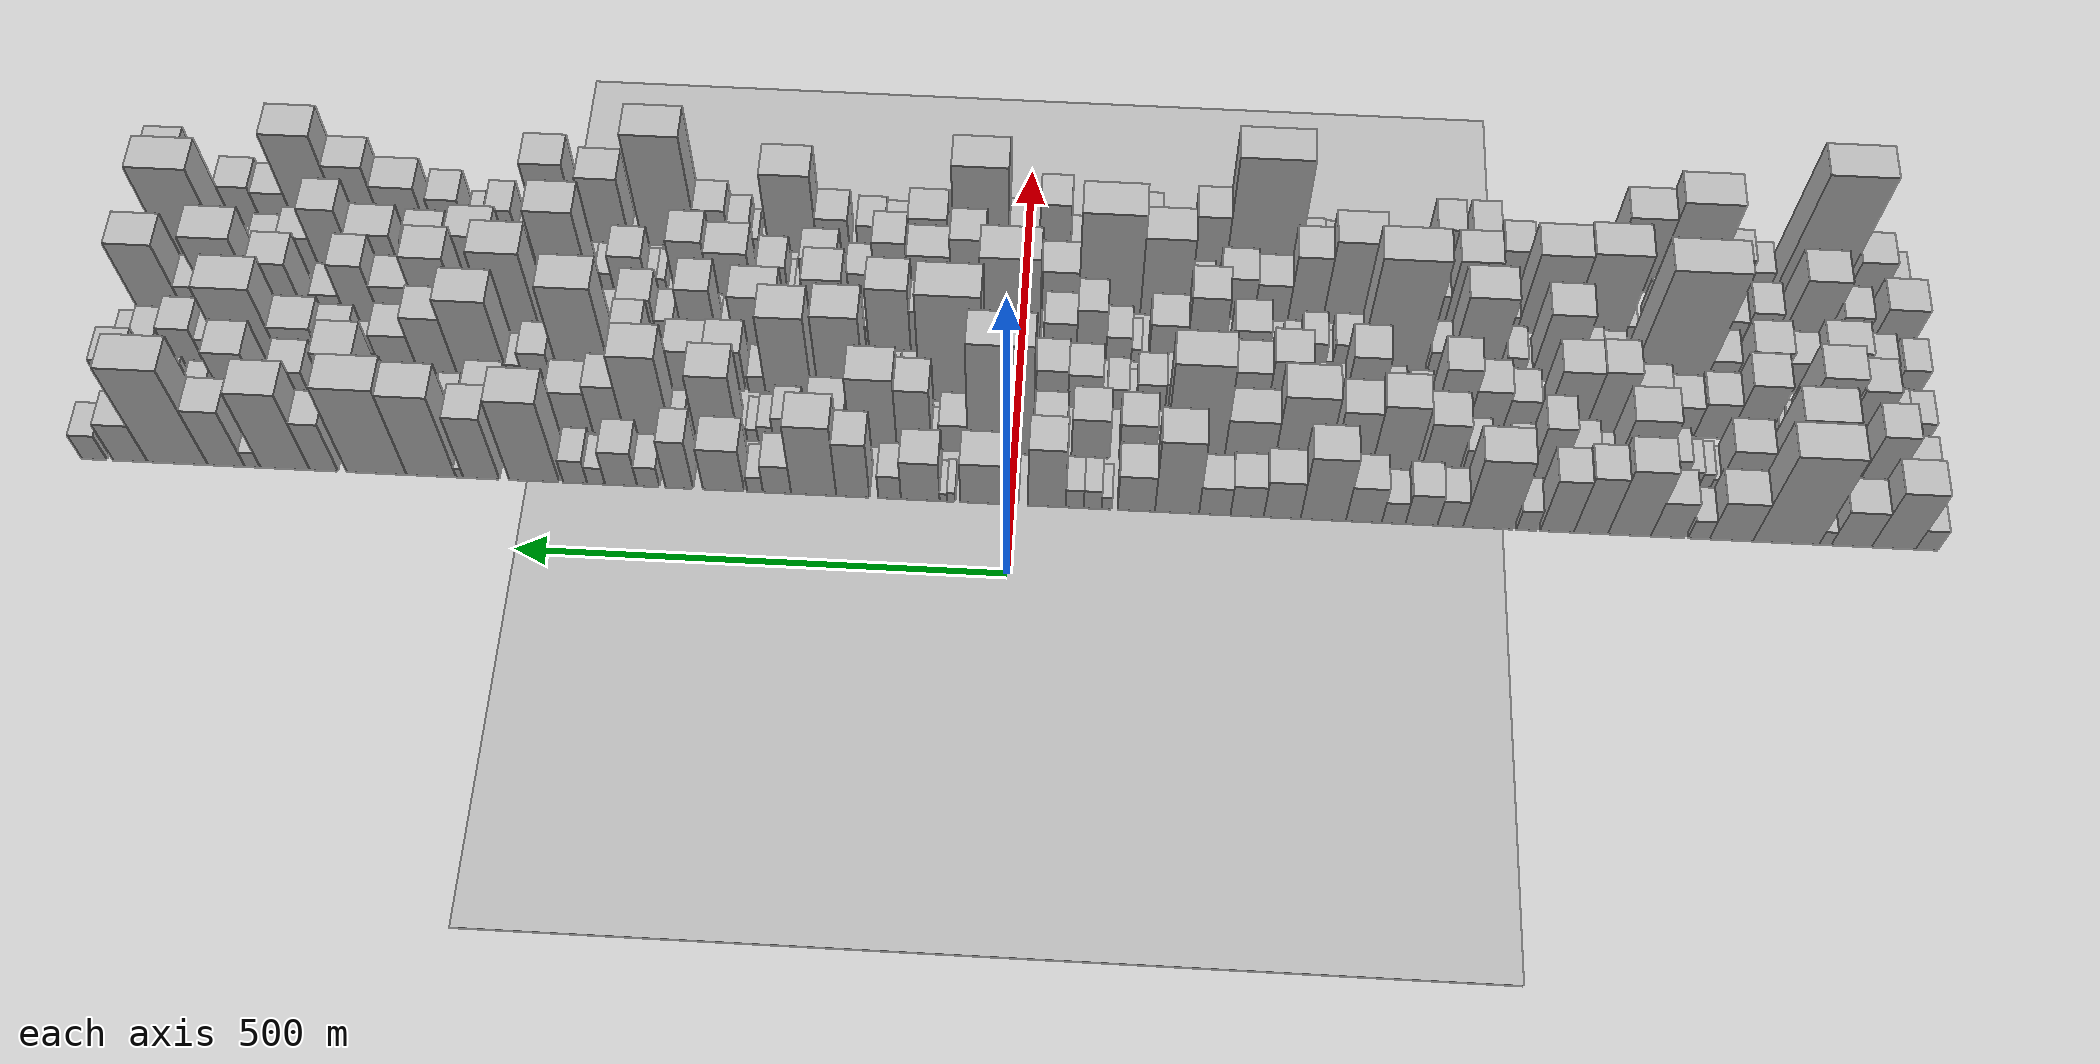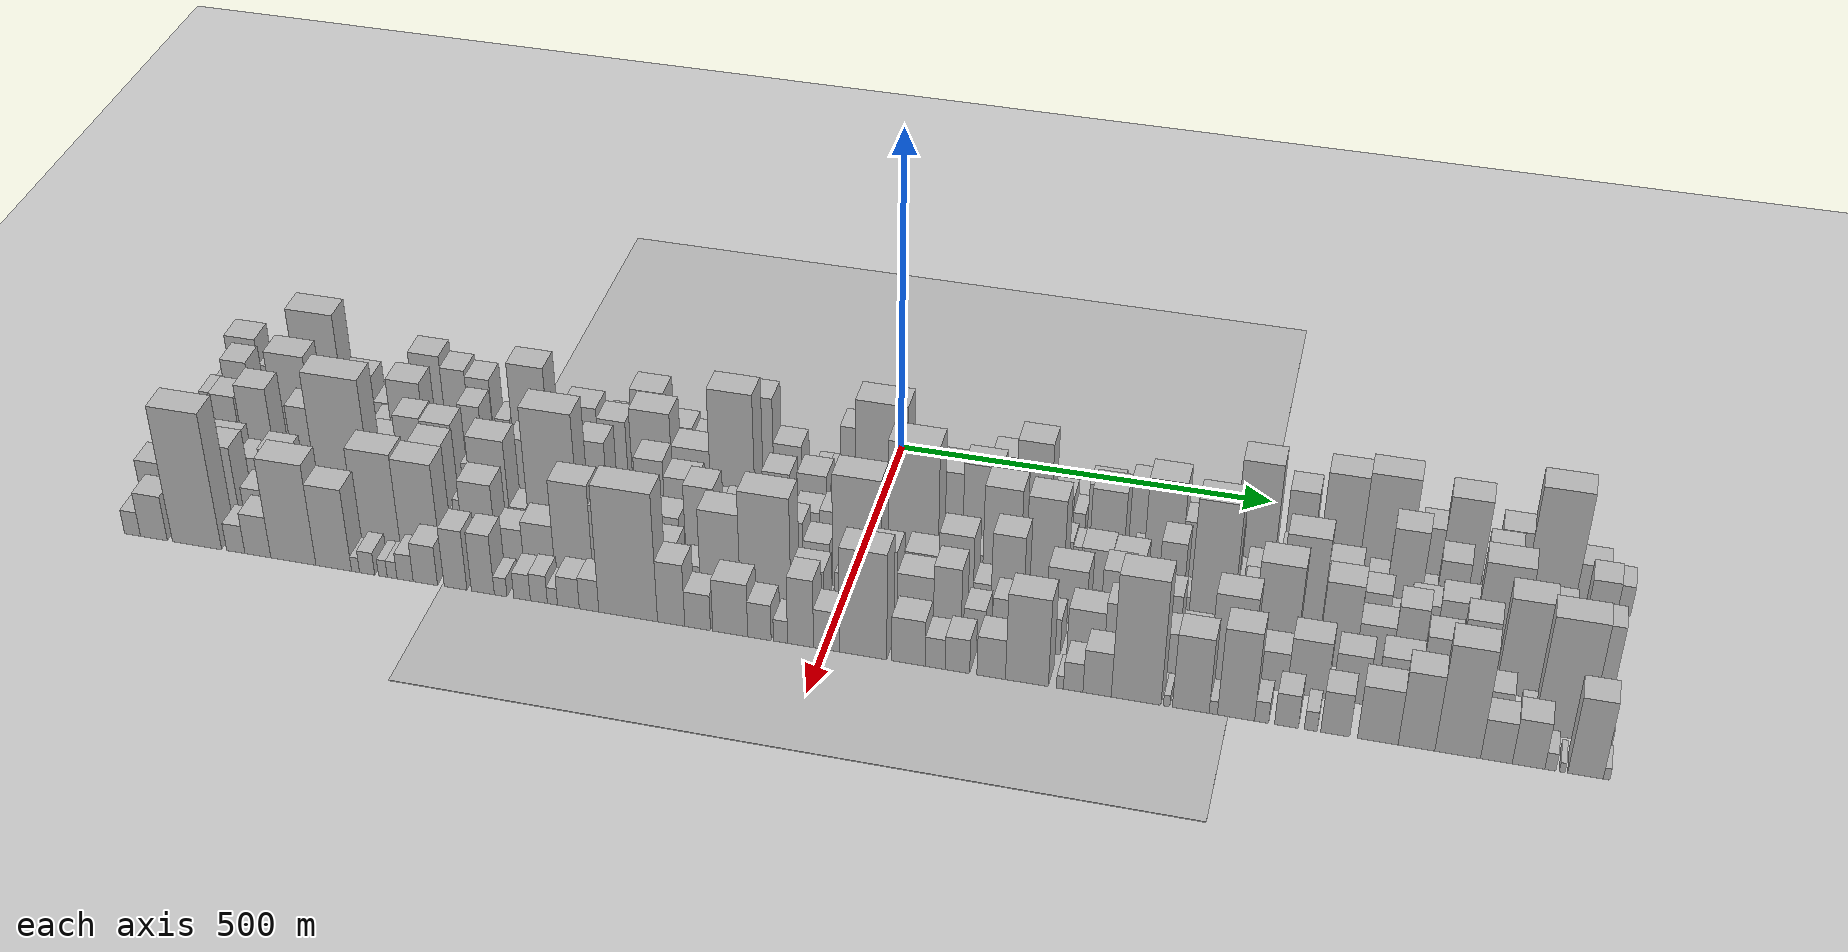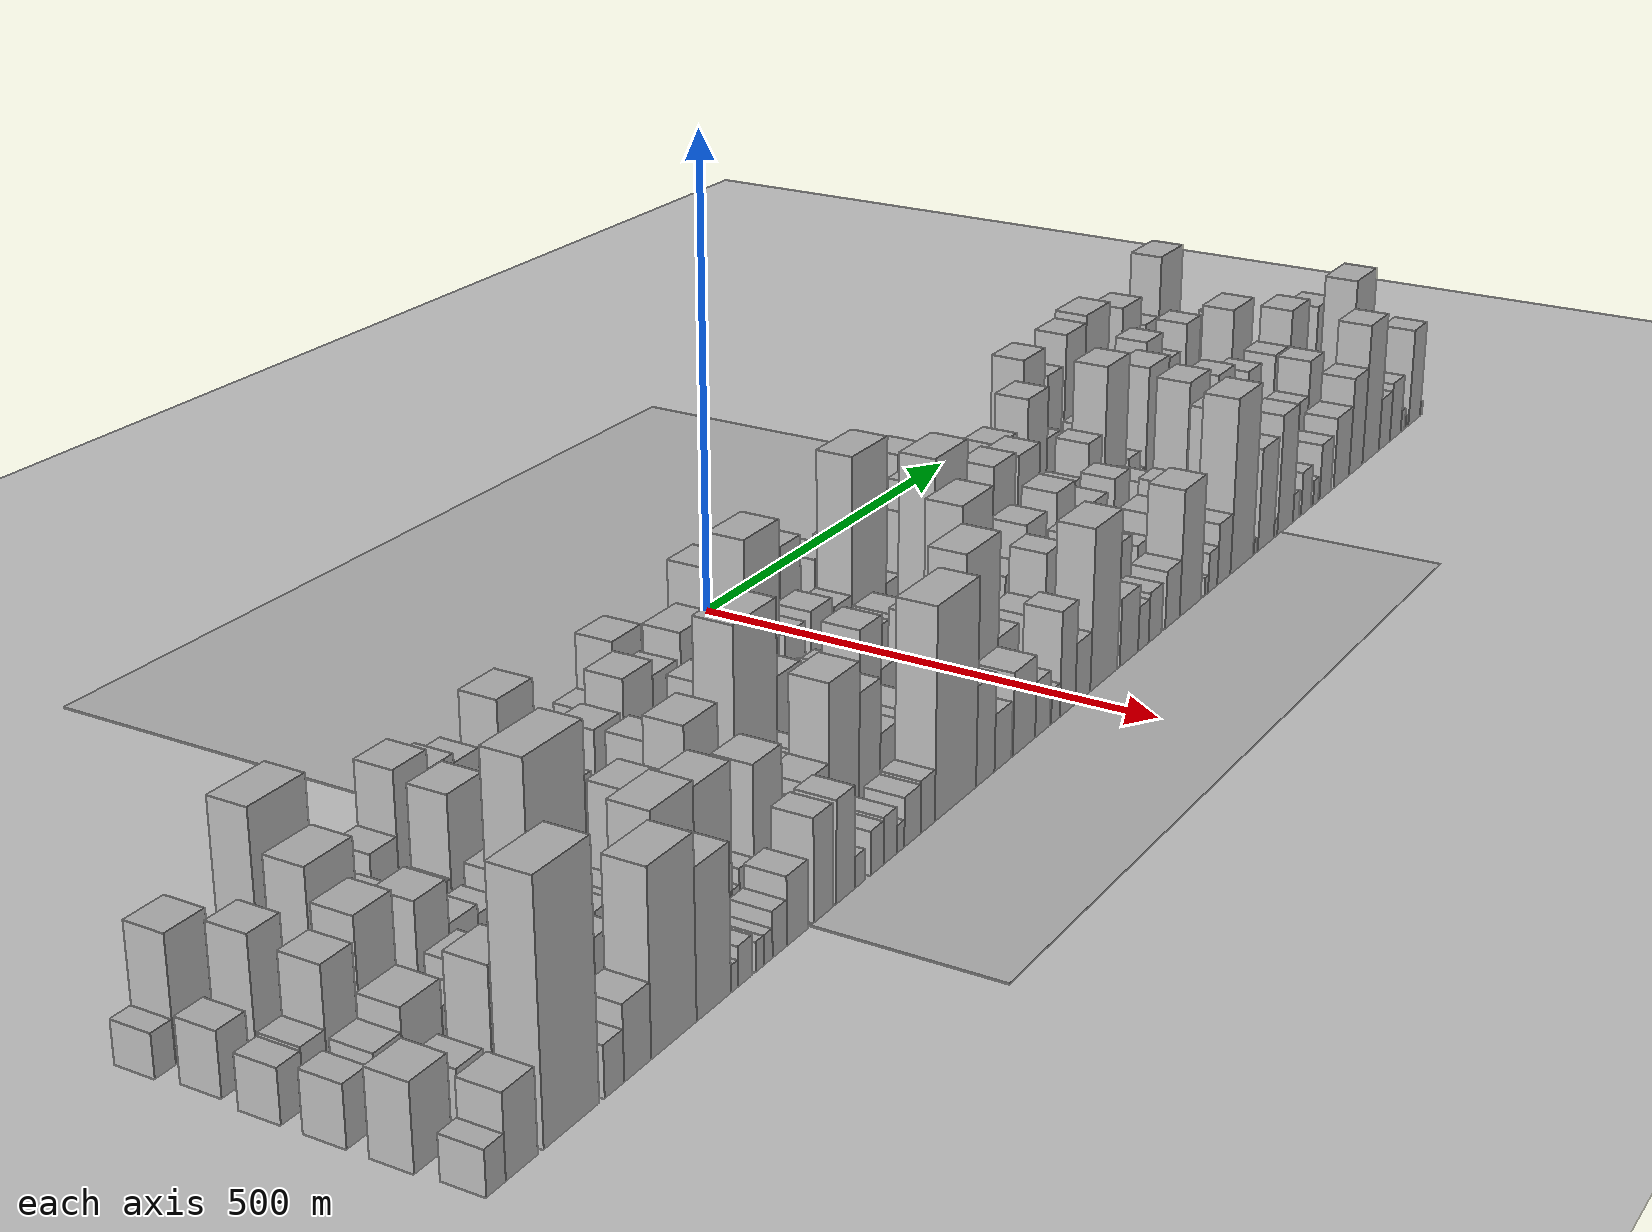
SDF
<?xml version="1.0" encoding="utf-8"?>

<sdf version="1.6">

   <world name="default">

      <gui fullscreen="0">

         <camera name="user_camera">

            <pose>-15 0 4.57585 0 0 0</pose>

            <view_controller>orbit</view_controller>

         </camera>

      </gui>

      <scene>

         <sky>

           <clouds>

             <speed>12</speed>

           </clouds>

         </sky>

         <ambient>0.4 0.4 0.4 1</ambient>

         <background>0.7 0.7 0.7 1</background>

         <shadows>1</shadows>

      </scene>

      <gravity>0 0 -9.8066</gravity>

      <magnetic_field>6e-06 2.3e-05 -4.2e-05</magnetic_field>

      <physics default="0" name="default_physics" type="ode">

         <ode>

            <solver>

               <type>quick</type>

               <iters>10</iters>

               <sor>1.0</sor>

               <use_dynamic_moi_rescaling>0</use_dynamic_moi_rescaling>

            </solver>

            <constraints>

               <cfm>0</cfm>

               <erp>0.2</erp>

               <contact_max_correcting_vel>100</contact_max_correcting_vel>

               <contact_surface_layer>0.001</contact_surface_layer>

            </constraints>

         </ode>

         <max_step_size>0.004</max_step_size>

         <real_time_factor>1</real_time_factor>

         <real_time_update_rate>250</real_time_update_rate>

      </physics>

      <light name="sun" type="directional">

         <cast_shadows>1</cast_shadows>

         <pose>0 0 10 0 0 0</pose>

         <diffuse>0.8 0.8 0.8 1</diffuse>

         <specular>0.2 0.2 0.2 1</specular>

         <attenuation>

            <range>1000</range>

            <constant>0.9</constant>

            <linear>0.01</linear>

            <quadratic>0.001</quadratic>

         </attenuation>

         <direction>-0.5 0.1 -0.9</direction>

      </light>

      <include>

         <name>ground_plane_1</name>

         <uri>model://HANNAS_ground_plane</uri>

         <pose>0 0 0  0 0 0</pose>

      </include>

      <include>

         <name>ground_plane_2</name>

         <uri>model://HANNAS_ground_plane</uri>

         <pose>100 0 0  0 0 0</pose>

      </include>

      <model name="building_1">

         <static>1</static>

         <pose frame="">100.0000 -928.6633 0 0.000000 0.000000 0.000000</pose>

         <link name="link">

            <pose frame="">0 0 19.50 0 0 0</pose>

            <collision name="collision">

               <geometry>

                  <box>

                     <size>40.0000 22.6733 39.0000</size>

                  </box>

               </geometry>

               <max_contacts>10</max_contacts>

               <surface>

                  <contact>

                     <ode/>

                  </contact>

                  <bounce/>

                  <friction>

                     <torsional>

                        <ode/>

                     </torsional>

                     <ode/>

                  </friction>

               </surface>

            </collision>

            <visual name="visual">

               <cast_shadows>0</cast_shadows>

               <geometry>

                  <box>

                     <size>40.0000 22.6733 39.0000</size>

                  </box>

               </geometry>

               <material>

                  <script>

                     <uri>model://HANNAS_wall/materials/scripts</uri>

                     <uri>model://HANNAS_wall/materials/textures</uri>

                     <name>vrc/HANNAS_wall</name>

                  </script>

               </material>

            </visual>

            <self_collide>0</self_collide>

            <enable_wind>0</enable_wind>

            <kinematic>0</kinematic>

         </link>

      </model>

      <model name="building_2">

         <static>1</static>

         <pose frame="">100.0000 -895.1582 0 0.000000 0.000000 0.000000</pose>

         <link name="link">

            <pose frame="">0 0 55.50 0 0 0</pose>

            <collision name="collision">

               <geometry>

                  <box>

                     <size>40.0000 44.3370 111.0000</size>

                  </box>

               </geometry>

               <max_contacts>10</max_contacts>

               <surface>

                  <contact>

                     <ode/>

                  </contact>

                  <bounce/>

                  <friction>

                     <torsional>

                        <ode/>

                     </torsional>

                     <ode/>

                  </friction>

               </surface>

            </collision>

            <visual name="visual">

               <cast_shadows>0</cast_shadows>

               <geometry>

                  <box>

                     <size>40.0000 44.3370 111.0000</size>

                  </box>

               </geometry>

               <material>

                  <script>

                     <uri>model://HANNAS_wall/materials/scripts</uri>

                     <uri>model://HANNAS_wall/materials/textures</uri>

                     <name>vrc/HANNAS_wall</name>

                  </script>

               </material>

            </visual>

            <self_collide>0</self_collide>

            <enable_wind>0</enable_wind>

            <kinematic>0</kinematic>

         </link>

      </model>

      <model name="building_3">

         <static>1</static>

         <pose frame="">100.0000 -852.6867 0 0.000000 0.000000 0.000000</pose>

         <link name="link">

            <pose frame="">0 0 34.50 0 0 0</pose>

            <collision name="collision">

               <geometry>

                  <box>

                     <size>40.0000 40.6060 69.0000</size>

                  </box>

               </geometry>

               <max_contacts>10</max_contacts>

               <surface>

                  <contact>

                     <ode/>

                  </contact>

                  <bounce/>

                  <friction>

                     <torsional>

                        <ode/>

                     </torsional>

                     <ode/>

                  </friction>

               </surface>

            </collision>

            <visual name="visual">

               <cast_shadows>0</cast_shadows>

               <geometry>

                  <box>

                     <size>40.0000 40.6060 69.0000</size>

                  </box>

               </geometry>

               <material>

                  <script>

                     <uri>model://HANNAS_wall/materials/scripts</uri>

                     <uri>model://HANNAS_wall/materials/textures</uri>

                     <name>vrc/HANNAS_wall</name>

                  </script>

               </material>

            </visual>

            <self_collide>0</self_collide>

            <enable_wind>0</enable_wind>

            <kinematic>0</kinematic>

         </link>

      </model>

      <model name="building_4">

         <static>1</static>

         <pose frame="">100.0000 -826.3222 0 0.000000 0.000000 0.000000</pose>

         <link name="link">

            <pose frame="">0 0 13.50 0 0 0</pose>

            <collision name="collision">

               <geometry>

                  <box>

                     <size>40.0000 12.1230 27.0000</size>

                  </box>

               </geometry>

               <max_contacts>10</max_contacts>

               <surface>

                  <contact>

                     <ode/>

                  </contact>

                  <bounce/>

                  <friction>

                     <torsional>

                        <ode/>

                     </torsional>

                     <ode/>

                  </friction>

               </surface>

            </collision>

            <visual name="visual">

               <cast_shadows>0</cast_shadows>

               <geometry>

                  <box>

                     <size>40.0000 12.1230 27.0000</size>

                  </box>

               </geometry>

               <material>

                  <script>

                     <uri>model://HANNAS_wall/materials/scripts</uri>

                     <uri>model://HANNAS_wall/materials/textures</uri>

                     <name>vrc/HANNAS_wall</name>

                  </script>

               </material>

            </visual>

            <self_collide>0</self_collide>

            <enable_wind>0</enable_wind>

            <kinematic>0</kinematic>

         </link>

      </model>

      <model name="building_5">

         <static>1</static>

         <pose frame="">100.0000 -786.8183 0 0.000000 0.000000 0.000000</pose>

         <link name="link">

            <pose frame="">0 0 85.50 0 0 0</pose>

            <collision name="collision">

               <geometry>

                  <box>

                     <size>40.0000 66.8846 171.0000</size>

                  </box>

               </geometry>

               <max_contacts>10</max_contacts>

               <surface>

                  <contact>

                     <ode/>

                  </contact>

                  <bounce/>

                  <friction>

                     <torsional>

                        <ode/>

                     </torsional>

                     <ode/>

                  </friction>

               </surface>

            </collision>

            <visual name="visual">

               <cast_shadows>0</cast_shadows>

               <geometry>

                  <box>

                     <size>40.0000 66.8846 171.0000</size>

                  </box>

               </geometry>

               <material>

                  <script>

                     <uri>model://HANNAS_wall/materials/scripts</uri>

                     <uri>model://HANNAS_wall/materials/textures</uri>

                     <name>vrc/HANNAS_wall</name>

                  </script>

               </material>

            </visual>

            <self_collide>0</self_collide>

            <enable_wind>0</enable_wind>

            <kinematic>0</kinematic>

         </link>

      </model>

      <model name="building_6">

         <static>1</static>

         <pose frame="">100.0000 -731.4493 0 0.000000 0.000000 0.000000</pose>

         <link name="link">

            <pose frame="">0 0 37.50 0 0 0</pose>

            <collision name="collision">

               <geometry>

                  <box>

                     <size>40.0000 43.8536 75.0000</size>

                  </box>

               </geometry>

               <max_contacts>10</max_contacts>

               <surface>

                  <contact>

                     <ode/>

                  </contact>

                  <bounce/>

                  <friction>

                     <torsional>

                        <ode/>

                     </torsional>

                     <ode/>

                  </friction>

               </surface>

            </collision>

            <visual name="visual">

               <cast_shadows>0</cast_shadows>

               <geometry>

                  <box>

                     <size>40.0000 43.8536 75.0000</size>

                  </box>

               </geometry>

               <material>

                  <script>

                     <uri>model://HANNAS_wall/materials/scripts</uri>

                     <uri>model://HANNAS_wall/materials/textures</uri>

                     <name>vrc/HANNAS_wall</name>

                  </script>

               </material>

            </visual>

            <self_collide>0</self_collide>

            <enable_wind>0</enable_wind>

            <kinematic>0</kinematic>

         </link>

      </model>

      <model name="building_7">

         <static>1</static>

         <pose frame="">100.0000 -698.7344 0 0.000000 0.000000 0.000000</pose>

         <link name="link">

            <pose frame="">0 0 18.00 0 0 0</pose>

            <collision name="collision">

               <geometry>

                  <box>

                     <size>40.0000 21.5762 36.0000</size>

                  </box>

               </geometry>

               <max_contacts>10</max_contacts>

               <surface>

                  <contact>

                     <ode/>

                  </contact>

                  <bounce/>

                  <friction>

                     <torsional>

                        <ode/>

                     </torsional>

                     <ode/>

                  </friction>

               </surface>

            </collision>

            <visual name="visual">

               <cast_shadows>0</cast_shadows>

               <geometry>

                  <box>

                     <size>40.0000 21.5762 36.0000</size>

                  </box>

               </geometry>

               <material>

                  <script>

                     <uri>model://HANNAS_wall/materials/scripts</uri>

                     <uri>model://HANNAS_wall/materials/textures</uri>

                     <name>vrc/HANNAS_wall</name>

                  </script>

               </material>

            </visual>

            <self_collide>0</self_collide>

            <enable_wind>0</enable_wind>

            <kinematic>0</kinematic>

         </link>

      </model>

      <model name="building_8">

         <static>1</static>

         <pose frame="">100.0000 -667.6218 0 0.000000 0.000000 0.000000</pose>

         <link name="link">

            <pose frame="">0 0 34.50 0 0 0</pose>

            <collision name="collision">

               <geometry>

                  <box>

                     <size>40.0000 34.6488 69.0000</size>

                  </box>

               </geometry>

               <max_contacts>10</max_contacts>

               <surface>

                  <contact>

                     <ode/>

                  </contact>

                  <bounce/>

                  <friction>

                     <torsional>

                        <ode/>

                     </torsional>

                     <ode/>

                  </friction>

               </surface>

            </collision>

            <visual name="visual">

               <cast_shadows>0</cast_shadows>

               <geometry>

                  <box>

                     <size>40.0000 34.6488 69.0000</size>

                  </box>

               </geometry>

               <material>

                  <script>

                     <uri>model://HANNAS_wall/materials/scripts</uri>

                     <uri>model://HANNAS_wall/materials/textures</uri>

                     <name>vrc/HANNAS_wall</name>

                  </script>

               </material>

            </visual>

            <self_collide>0</self_collide>

            <enable_wind>0</enable_wind>

            <kinematic>0</kinematic>

         </link>

      </model>

      <model name="building_9">

         <static>1</static>

         <pose frame="">100.0000 -628.5737 0 0.000000 0.000000 0.000000</pose>

         <link name="link">

            <pose frame="">0 0 64.50 0 0 0</pose>

            <collision name="collision">

               <geometry>

                  <box>

                     <size>40.0000 43.4475 129.0000</size>

                  </box>

               </geometry>

               <max_contacts>10</max_contacts>

               <surface>

                  <contact>

                     <ode/>

                  </contact>

                  <bounce/>

                  <friction>

                     <torsional>

                        <ode/>

                     </torsional>

                     <ode/>

                  </friction>

               </surface>

            </collision>

            <visual name="visual">

               <cast_shadows>0</cast_shadows>

               <geometry>

                  <box>

                     <size>40.0000 43.4475 129.0000</size>

                  </box>

               </geometry>

               <material>

                  <script>

                     <uri>model://HANNAS_wall/materials/scripts</uri>

                     <uri>model://HANNAS_wall/materials/textures</uri>

                     <name>vrc/HANNAS_wall</name>

                  </script>

               </material>

            </visual>

            <self_collide>0</self_collide>

            <enable_wind>0</enable_wind>

            <kinematic>0</kinematic>

         </link>

      </model>

      <model name="building_10">

         <static>1</static>

         <pose frame="">100.0000 -589.6463 0 0.000000 0.000000 0.000000</pose>

         <link name="link">

            <pose frame="">0 0 55.50 0 0 0</pose>

            <collision name="collision">

               <geometry>

                  <box>

                     <size>40.0000 34.4072 111.0000</size>

                  </box>

               </geometry>

               <max_contacts>10</max_contacts>

               <surface>

                  <contact>

                     <ode/>

                  </contact>

                  <bounce/>

                  <friction>

                     <torsional>

                        <ode/>

                     </torsional>

                     <ode/>

                  </friction>

               </surface>

            </collision>

            <visual name="visual">

               <cast_shadows>0</cast_shadows>

               <geometry>

                  <box>

                     <size>40.0000 34.4072 111.0000</size>

                  </box>

               </geometry>

               <material>

                  <script>

                     <uri>model://HANNAS_wall/materials/scripts</uri>

                     <uri>model://HANNAS_wall/materials/textures</uri>

                     <name>vrc/HANNAS_wall</name>

                  </script>

               </material>

            </visual>

            <self_collide>0</self_collide>

            <enable_wind>0</enable_wind>

            <kinematic>0</kinematic>

         </link>

      </model>

      <model name="building_11">

         <static>1</static>

         <pose frame="">100.0000 -555.4277 0 0.000000 0.000000 0.000000</pose>

         <link name="link">

            <pose frame="">0 0 51.00 0 0 0</pose>

            <collision name="collision">

               <geometry>

                  <box>

                     <size>40.0000 34.0300 102.0000</size>

                  </box>

               </geometry>

               <max_contacts>10</max_contacts>

               <surface>

                  <contact>

                     <ode/>

                  </contact>

                  <bounce/>

                  <friction>

                     <torsional>

                        <ode/>

                     </torsional>

                     <ode/>

                  </friction>

               </surface>

            </collision>

            <visual name="visual">

               <cast_shadows>0</cast_shadows>

               <geometry>

                  <box>

                     <size>40.0000 34.0300 102.0000</size>

                  </box>

               </geometry>

               <material>

                  <script>

                     <uri>model://HANNAS_wall/materials/scripts</uri>

                     <uri>model://HANNAS_wall/materials/textures</uri>

                     <name>vrc/HANNAS_wall</name>

                  </script>

               </material>

            </visual>

            <self_collide>0</self_collide>

            <enable_wind>0</enable_wind>

            <kinematic>0</kinematic>

         </link>

      </model>

      <model name="building_12">

         <static>1</static>

         <pose frame="">100.0000 -524.8343 0 0.000000 0.000000 0.000000</pose>

         <link name="link">

            <pose frame="">0 0 19.50 0 0 0</pose>

            <collision name="collision">

               <geometry>

                  <box>

                     <size>40.0000 21.1568 39.0000</size>

                  </box>

               </geometry>

               <max_contacts>10</max_contacts>

               <surface>

                  <contact>

                     <ode/>

                  </contact>

                  <bounce/>

                  <friction>

                     <torsional>

                        <ode/>

                     </torsional>

                     <ode/>

                  </friction>

               </surface>

            </collision>

            <visual name="visual">

               <cast_shadows>0</cast_shadows>

               <geometry>

                  <box>

                     <size>40.0000 21.1568 39.0000</size>

                  </box>

               </geometry>

               <material>

                  <script>

                     <uri>model://HANNAS_wall/materials/scripts</uri>

                     <uri>model://HANNAS_wall/materials/textures</uri>

                     <name>vrc/HANNAS_wall</name>

                  </script>

               </material>

            </visual>

            <self_collide>0</self_collide>

            <enable_wind>0</enable_wind>

            <kinematic>0</kinematic>

         </link>

      </model>

      <model name="building_13">

         <static>1</static>

         <pose frame="">100.0000 -485.7063 0 0.000000 0.000000 0.000000</pose>

         <link name="link">

            <pose frame="">0 0 67.50 0 0 0</pose>

            <collision name="collision">

               <geometry>

                  <box>

                     <size>40.0000 51.0993 135.0000</size>

                  </box>

               </geometry>

               <max_contacts>10</max_contacts>

               <surface>

                  <contact>

                     <ode/>

                  </contact>

                  <bounce/>

                  <friction>

                     <torsional>

                        <ode/>

                     </torsional>

                     <ode/>

                  </friction>

               </surface>

            </collision>

            <visual name="visual">

               <cast_shadows>0</cast_shadows>

               <geometry>

                  <box>

                     <size>40.0000 51.0993 135.0000</size>

                  </box>

               </geometry>

               <material>

                  <script>

                     <uri>model://HANNAS_wall/materials/scripts</uri>

                     <uri>model://HANNAS_wall/materials/textures</uri>

                     <name>vrc/HANNAS_wall</name>

                  </script>

               </material>

            </visual>

            <self_collide>0</self_collide>

            <enable_wind>0</enable_wind>

            <kinematic>0</kinematic>

         </link>

      </model>

      <model name="building_14">

         <static>1</static>

         <pose frame="">100.0000 -447.0501 0 0.000000 0.000000 0.000000</pose>

         <link name="link">

            <pose frame="">0 0 25.50 0 0 0</pose>

            <collision name="collision">

               <geometry>

                  <box>

                     <size>40.0000 26.2131 51.0000</size>

                  </box>

               </geometry>

               <max_contacts>10</max_contacts>

               <surface>

                  <contact>

                     <ode/>

                  </contact>

                  <bounce/>

                  <friction>

                     <torsional>

                        <ode/>

                     </torsional>

                     <ode/>

                  </friction>

               </surface>

            </collision>

            <visual name="visual">

               <cast_shadows>0</cast_shadows>

               <geometry>

                  <box>

                     <size>40.0000 26.2131 51.0000</size>

                  </box>

               </geometry>

               <material>

                  <script>

                     <uri>model://HANNAS_wall/materials/scripts</uri>

                     <uri>model://HANNAS_wall/materials/textures</uri>

                     <name>vrc/HANNAS_wall</name>

                  </script>

               </material>

            </visual>

            <self_collide>0</self_collide>

            <enable_wind>0</enable_wind>

            <kinematic>0</kinematic>

         </link>

      </model>

      <model name="building_15">

         <static>1</static>

         <pose frame="">100.0000 -417.6876 0 0.000000 0.000000 0.000000</pose>

         <link name="link">

            <pose frame="">0 0 30.00 0 0 0</pose>

            <collision name="collision">

               <geometry>

                  <box>

                     <size>40.0000 32.5119 60.0000</size>

                  </box>

               </geometry>

               <max_contacts>10</max_contacts>

               <surface>

                  <contact>

                     <ode/>

                  </contact>

                  <bounce/>

                  <friction>

                     <torsional>

                        <ode/>

                     </torsional>

                     <ode/>

                  </friction>

               </surface>

            </collision>

            <visual name="visual">

               <cast_shadows>0</cast_shadows>

               <geometry>

                  <box>

                     <size>40.0000 32.5119 60.0000</size>

                  </box>

               </geometry>

               <material>

                  <script>

                     <uri>model://HANNAS_wall/materials/scripts</uri>

                     <uri>model://HANNAS_wall/materials/textures</uri>

                     <name>vrc/HANNAS_wall</name>

                  </script>

               </material>

            </visual>

            <self_collide>0</self_collide>

            <enable_wind>0</enable_wind>

            <kinematic>0</kinematic>

         </link>

      </model>

      <model name="building_16">

         <static>1</static>

         <pose frame="">100.0000 -389.3960 0 0.000000 0.000000 0.000000</pose>

         <link name="link">

            <pose frame="">0 0 21.00 0 0 0</pose>

            <collision name="collision">

               <geometry>

                  <box>

                     <size>40.0000 24.0713 42.0000</size>

                  </box>

               </geometry>

               <max_contacts>10</max_contacts>

               <surface>

                  <contact>

                     <ode/>

                  </contact>

                  <bounce/>

                  <friction>

                     <torsional>

                        <ode/>

                     </torsional>

                     <ode/>

                  </friction>

               </surface>

            </collision>

            <visual name="visual">

               <cast_shadows>0</cast_shadows>

               <geometry>

                  <box>

                     <size>40.0000 24.0713 42.0000</size>

                  </box>

               </geometry>

               <material>

                  <script>

                     <uri>model://HANNAS_wall/materials/scripts</uri>

                     <uri>model://HANNAS_wall/materials/textures</uri>

                     <name>vrc/HANNAS_wall</name>

                  </script>

               </material>

            </visual>

            <self_collide>0</self_collide>

            <enable_wind>0</enable_wind>

            <kinematic>0</kinematic>

         </link>

      </model>

      <model name="building_17">

         <static>1</static>

         <pose frame="">100.0000 -359.1189 0 0.000000 0.000000 0.000000</pose>

         <link name="link">

            <pose frame="">0 0 34.50 0 0 0</pose>

            <collision name="collision">

               <geometry>

                  <box>

                     <size>40.0000 36.4830 69.0000</size>

                  </box>

               </geometry>

               <max_contacts>10</max_contacts>

               <surface>

                  <contact>

                     <ode/>

                  </contact>

                  <bounce/>

                  <friction>

                     <torsional>

                        <ode/>

                     </torsional>

                     <ode/>

                  </friction>

               </surface>

            </collision>

            <visual name="visual">

               <cast_shadows>0</cast_shadows>

               <geometry>

                  <box>

                     <size>40.0000 36.4830 69.0000</size>

                  </box>

               </geometry>

               <material>

                  <script>

                     <uri>model://HANNAS_wall/materials/scripts</uri>

                     <uri>model://HANNAS_wall/materials/textures</uri>

                     <name>vrc/HANNAS_wall</name>

                  </script>

               </material>

            </visual>

            <self_collide>0</self_collide>

            <enable_wind>0</enable_wind>

            <kinematic>0</kinematic>

         </link>

      </model>

      <model name="building_18">

         <static>1</static>

         <pose frame="">100.0000 -317.8565 0 0.000000 0.000000 0.000000</pose>

         <link name="link">

            <pose frame="">0 0 61.50 0 0 0</pose>

            <collision name="collision">

               <geometry>

                  <box>

                     <size>40.0000 46.0417 123.0000</size>

                  </box>

               </geometry>

               <max_contacts>10</max_contacts>

               <surface>

                  <contact>

                     <ode/>

                  </contact>

                  <bounce/>

                  <friction>

                     <torsional>

                        <ode/>

                     </torsional>

                     <ode/>

                  </friction>

               </surface>

            </collision>

            <visual name="visual">

               <cast_shadows>0</cast_shadows>

               <geometry>

                  <box>

                     <size>40.0000 46.0417 123.0000</size>

                  </box>

               </geometry>

               <material>

                  <script>

                     <uri>model://HANNAS_wall/materials/scripts</uri>

                     <uri>model://HANNAS_wall/materials/textures</uri>

                     <name>vrc/HANNAS_wall</name>

                  </script>

               </material>

            </visual>

            <self_collide>0</self_collide>

            <enable_wind>0</enable_wind>

            <kinematic>0</kinematic>

         </link>

      </model>

      <model name="building_19">

         <static>1</static>

         <pose frame="">100.0000 -276.0443 0 0.000000 0.000000 0.000000</pose>

         <link name="link">

            <pose frame="">0 0 36.00 0 0 0</pose>

            <collision name="collision">

               <geometry>

                  <box>

                     <size>40.0000 37.5828 72.0000</size>

                  </box>

               </geometry>

               <max_contacts>10</max_contacts>

               <surface>

                  <contact>

                     <ode/>

                  </contact>

                  <bounce/>

                  <friction>

                     <torsional>

                        <ode/>

                     </torsional>

                     <ode/>

                  </friction>

               </surface>

            </collision>

            <visual name="visual">

               <cast_shadows>0</cast_shadows>

               <geometry>

                  <box>

                     <size>40.0000 37.5828 72.0000</size>

                  </box>

               </geometry>

               <material>

                  <script>

                     <uri>model://HANNAS_wall/materials/scripts</uri>

                     <uri>model://HANNAS_wall/materials/textures</uri>

                     <name>vrc/HANNAS_wall</name>

                  </script>

               </material>

            </visual>

            <self_collide>0</self_collide>

            <enable_wind>0</enable_wind>

            <kinematic>0</kinematic>

         </link>

      </model>

      <model name="building_20">

         <static>1</static>

         <pose frame="">100.0000 -240.2655 0 0.000000 0.000000 0.000000</pose>

         <link name="link">

            <pose frame="">0 0 30.00 0 0 0</pose>

            <collision name="collision">

               <geometry>

                  <box>

                     <size>40.0000 33.9747 60.0000</size>

                  </box>

               </geometry>

               <max_contacts>10</max_contacts>

               <surface>

                  <contact>

                     <ode/>

                  </contact>

                  <bounce/>

                  <friction>

                     <torsional>

                        <ode/>

                     </torsional>

                     <ode/>

                  </friction>

               </surface>

            </collision>

            <visual name="visual">

               <cast_shadows>0</cast_shadows>

               <geometry>

                  <box>

                     <size>40.0000 33.9747 60.0000</size>

                  </box>

               </geometry>

               <material>

                  <script>

                     <uri>model://HANNAS_wall/materials/scripts</uri>

                     <uri>model://HANNAS_wall/materials/textures</uri>

                     <name>vrc/HANNAS_wall</name>

                  </script>

               </material>

            </visual>

            <self_collide>0</self_collide>

            <enable_wind>0</enable_wind>

            <kinematic>0</kinematic>

         </link>

      </model>

      <model name="building_21">

         <static>1</static>

         <pose frame="">100.0000 -207.2316 0 0.000000 0.000000 0.000000</pose>

         <link name="link">

            <pose frame="">0 0 27.00 0 0 0</pose>

            <collision name="collision">

               <geometry>

                  <box>

                     <size>40.0000 32.0932 54.0000</size>

                  </box>

               </geometry>

               <max_contacts>10</max_contacts>

               <surface>

                  <contact>

                     <ode/>

                  </contact>

                  <bounce/>

                  <friction>

                     <torsional>

                        <ode/>

                     </torsional>

                     <ode/>

                  </friction>

               </surface>

            </collision>

            <visual name="visual">

               <cast_shadows>0</cast_shadows>

               <geometry>

                  <box>

                     <size>40.0000 32.0932 54.0000</size>

                  </box>

               </geometry>

               <material>

                  <script>

                     <uri>model://HANNAS_wall/materials/scripts</uri>

                     <uri>model://HANNAS_wall/materials/textures</uri>

                     <name>vrc/HANNAS_wall</name>

                  </script>

               </material>

            </visual>

            <self_collide>0</self_collide>

            <enable_wind>0</enable_wind>

            <kinematic>0</kinematic>

         </link>

      </model>

      <model name="building_22">

         <static>1</static>

         <pose frame="">100.0000 -168.6694 0 0.000000 0.000000 0.000000</pose>

         <link name="link">

            <pose frame="">0 0 70.50 0 0 0</pose>

            <collision name="collision">

               <geometry>

                  <box>

                     <size>40.0000 45.0312 141.0000</size>

                  </box>

               </geometry>

               <max_contacts>10</max_contacts>

               <surface>

                  <contact>

                     <ode/>

                  </contact>

                  <bounce/>

                  <friction>

                     <torsional>

                        <ode/>

                     </torsional>

                     <ode/>

                  </friction>

               </surface>

            </collision>

            <visual name="visual">

               <cast_shadows>0</cast_shadows>

               <geometry>

                  <box>

                     <size>40.0000 45.0312 141.0000</size>

                  </box>

               </geometry>

               <material>

                  <script>

                     <uri>model://HANNAS_wall/materials/scripts</uri>

                     <uri>model://HANNAS_wall/materials/textures</uri>

                     <name>vrc/HANNAS_wall</name>

                  </script>

               </material>

            </visual>

            <self_collide>0</self_collide>

            <enable_wind>0</enable_wind>

            <kinematic>0</kinematic>

         </link>

      </model>

      <model name="building_23">

         <static>1</static>

         <pose frame="">100.0000 -127.0873 0 0.000000 0.000000 0.000000</pose>

         <link name="link">

            <pose frame="">0 0 34.50 0 0 0</pose>

            <collision name="collision">

               <geometry>

                  <box>

                     <size>40.0000 38.1330 69.0000</size>

                  </box>

               </geometry>

               <max_contacts>10</max_contacts>

               <surface>

                  <contact>

                     <ode/>

                  </contact>

                  <bounce/>

                  <friction>

                     <torsional>

                        <ode/>

                     </torsional>

                     <ode/>

                  </friction>

               </surface>

            </collision>

            <visual name="visual">

               <cast_shadows>0</cast_shadows>

               <geometry>

                  <box>

                     <size>40.0000 38.1330 69.0000</size>

                  </box>

               </geometry>

               <material>

                  <script>

                     <uri>model://HANNAS_wall/materials/scripts</uri>

                     <uri>model://HANNAS_wall/materials/textures</uri>

                     <name>vrc/HANNAS_wall</name>

                  </script>

               </material>

            </visual>

            <self_collide>0</self_collide>

            <enable_wind>0</enable_wind>

            <kinematic>0</kinematic>

         </link>

      </model>

      <model name="building_24">

         <static>1</static>

         <pose frame="">100.0000 -96.7946 0 0.000000 0.000000 0.000000</pose>

         <link name="link">

            <pose frame="">0 0 12.00 0 0 0</pose>

            <collision name="collision">

               <geometry>

                  <box>

                     <size>40.0000 10.4522 24.0000</size>

                  </box>

               </geometry>

               <max_contacts>10</max_contacts>

               <surface>

                  <contact>

                     <ode/>

                  </contact>

                  <bounce/>

                  <friction>

                     <torsional>

                        <ode/>

                     </torsional>

                     <ode/>

                  </friction>

               </surface>

            </collision>

            <visual name="visual">

               <cast_shadows>0</cast_shadows>

               <geometry>

                  <box>

                     <size>40.0000 10.4522 24.0000</size>

                  </box>

               </geometry>

               <material>

                  <script>

                     <uri>model://HANNAS_wall/materials/scripts</uri>

                     <uri>model://HANNAS_wall/materials/textures</uri>

                     <name>vrc/HANNAS_wall</name>

                  </script>

               </material>

            </visual>

            <self_collide>0</self_collide>

            <enable_wind>0</enable_wind>

            <kinematic>0</kinematic>

         </link>

      </model>

      <model name="building_25">

         <static>1</static>

         <pose frame="">100.0000 -82.4453 0 0.000000 0.000000 0.000000</pose>

         <link name="link">

            <pose frame="">0 0 18.00 0 0 0</pose>

            <collision name="collision">

               <geometry>

                  <box>

                     <size>40.0000 18.2464 36.0000</size>

                  </box>

               </geometry>

               <max_contacts>10</max_contacts>

               <surface>

                  <contact>

                     <ode/>

                  </contact>

                  <bounce/>

                  <friction>

                     <torsional>

                        <ode/>

                     </torsional>

                     <ode/>

                  </friction>

               </surface>

            </collision>

            <visual name="visual">

               <cast_shadows>0</cast_shadows>

               <geometry>

                  <box>

                     <size>40.0000 18.2464 36.0000</size>

                  </box>

               </geometry>

               <material>

                  <script>

                     <uri>model://HANNAS_wall/materials/scripts</uri>

                     <uri>model://HANNAS_wall/materials/textures</uri>

                     <name>vrc/HANNAS_wall</name>

                  </script>

               </material>

            </visual>

            <self_collide>0</self_collide>

            <enable_wind>0</enable_wind>

            <kinematic>0</kinematic>

         </link>

      </model>

      <model name="building_26">

         <static>1</static>

         <pose frame="">100.0000 -64.1063 0 0.000000 0.000000 0.000000</pose>

         <link name="link">

            <pose frame="">0 0 18.00 0 0 0</pose>

            <collision name="collision">

               <geometry>

                  <box>

                     <size>40.0000 18.4317 36.0000</size>

                  </box>

               </geometry>

               <max_contacts>10</max_contacts>

               <surface>

                  <contact>

                     <ode/>

                  </contact>

                  <bounce/>

                  <friction>

                     <torsional>

                        <ode/>

                     </torsional>

                     <ode/>

                  </friction>

               </surface>

            </collision>

            <visual name="visual">

               <cast_shadows>0</cast_shadows>

               <geometry>

                  <box>

                     <size>40.0000 18.4317 36.0000</size>

                  </box>

               </geometry>

               <material>

                  <script>

                     <uri>model://HANNAS_wall/materials/scripts</uri>

                     <uri>model://HANNAS_wall/materials/textures</uri>

                     <name>vrc/HANNAS_wall</name>

                  </script>

               </material>

            </visual>

            <self_collide>0</self_collide>

            <enable_wind>0</enable_wind>

            <kinematic>0</kinematic>

         </link>

      </model>

      <model name="building_27">

         <static>1</static>

         <pose frame="">100.0000 -35.6017 0 0.000000 0.000000 0.000000</pose>

         <link name="link">

            <pose frame="">0 0 57.00 0 0 0</pose>

            <collision name="collision">

               <geometry>

                  <box>

                     <size>40.0000 38.5774 114.0000</size>

                  </box>

               </geometry>

               <max_contacts>10</max_contacts>

               <surface>

                  <contact>

                     <ode/>

                  </contact>

                  <bounce/>

                  <friction>

                     <torsional>

                        <ode/>

                     </torsional>

                     <ode/>

                  </friction>

               </surface>

            </collision>

            <visual name="visual">

               <cast_shadows>0</cast_shadows>

               <geometry>

                  <box>

                     <size>40.0000 38.5774 114.0000</size>

                  </box>

               </geometry>

               <material>

                  <script>

                     <uri>model://HANNAS_wall/materials/scripts</uri>

                     <uri>model://HANNAS_wall/materials/textures</uri>

                     <name>vrc/HANNAS_wall</name>

                  </script>

               </material>

            </visual>

            <self_collide>0</self_collide>

            <enable_wind>0</enable_wind>

            <kinematic>0</kinematic>

         </link>

      </model>

      <model name="building_28">

         <static>1</static>

         <pose frame="">100.0000 2.2748 0 0.000000 0.000000 0.000000</pose>

         <link name="link">

            <pose frame="">0 0 16.50 0 0 0</pose>

            <collision name="collision">

               <geometry>

                  <box>

                     <size>40.0000 17.1756 33.0000</size>

                  </box>

               </geometry>

               <max_contacts>10</max_contacts>

               <surface>

                  <contact>

                     <ode/>

                  </contact>

                  <bounce/>

                  <friction>

                     <torsional>

                        <ode/>

                     </torsional>

                     <ode/>

                  </friction>

               </surface>

            </collision>

            <visual name="visual">

               <cast_shadows>0</cast_shadows>

               <geometry>

                  <box>

                     <size>40.0000 17.1756 33.0000</size>

                  </box>

               </geometry>

               <material>

                  <script>

                     <uri>model://HANNAS_wall/materials/scripts</uri>

                     <uri>model://HANNAS_wall/materials/textures</uri>

                     <name>vrc/HANNAS_wall</name>

                  </script>

               </material>

            </visual>

            <self_collide>0</self_collide>

            <enable_wind>0</enable_wind>

            <kinematic>0</kinematic>

         </link>

      </model>

      <model name="building_29">

         <static>1</static>

         <pose frame="">100.0000 32.0478 0 0.000000 0.000000 0.000000</pose>

         <link name="link">

            <pose frame="">0 0 39.00 0 0 0</pose>

            <collision name="collision">

               <geometry>

                  <box>

                     <size>40.0000 42.3704 78.0000</size>

                  </box>

               </geometry>

               <max_contacts>10</max_contacts>

               <surface>

                  <contact>

                     <ode/>

                  </contact>

                  <bounce/>

                  <friction>

                     <torsional>

                        <ode/>

                     </torsional>

                     <ode/>

                  </friction>

               </surface>

            </collision>

            <visual name="visual">

               <cast_shadows>0</cast_shadows>

               <geometry>

                  <box>

                     <size>40.0000 42.3704 78.0000</size>

                  </box>

               </geometry>

               <material>

                  <script>

                     <uri>model://HANNAS_wall/materials/scripts</uri>

                     <uri>model://HANNAS_wall/materials/textures</uri>

                     <name>vrc/HANNAS_wall</name>

                  </script>

               </material>

            </visual>

            <self_collide>0</self_collide>

            <enable_wind>0</enable_wind>

            <kinematic>0</kinematic>

         </link>

      </model>

      <model name="building_30">

         <static>1</static>

         <pose frame="">100.0000 62.5855 0 0.000000 0.000000 0.000000</pose>

         <link name="link">

            <pose frame="">0 0 9.00 0 0 0</pose>

            <collision name="collision">

               <geometry>

                  <box>

                     <size>40.0000 8.7050 18.0000</size>

                  </box>

               </geometry>

               <max_contacts>10</max_contacts>

               <surface>

                  <contact>

                     <ode/>

                  </contact>

                  <bounce/>

                  <friction>

                     <torsional>

                        <ode/>

                     </torsional>

                     <ode/>

                  </friction>

               </surface>

            </collision>

            <visual name="visual">

               <cast_shadows>0</cast_shadows>

               <geometry>

                  <box>

                     <size>40.0000 8.7050 18.0000</size>

                  </box>

               </geometry>

               <material>

                  <script>

                     <uri>model://HANNAS_wall/materials/scripts</uri>

                     <uri>model://HANNAS_wall/materials/textures</uri>

                     <name>vrc/HANNAS_wall</name>

                  </script>

               </material>

            </visual>

            <self_collide>0</self_collide>

            <enable_wind>0</enable_wind>

            <kinematic>0</kinematic>

         </link>

      </model>

      <model name="building_31">

         <static>1</static>

         <pose frame="">100.0000 70.6687 0 0.000000 0.000000 0.000000</pose>

         <link name="link">

            <pose frame="">0 0 7.50 0 0 0</pose>

            <collision name="collision">

               <geometry>

                  <box>

                     <size>40.0000 7.4614 15.0000</size>

                  </box>

               </geometry>

               <max_contacts>10</max_contacts>

               <surface>

                  <contact>

                     <ode/>

                  </contact>

                  <bounce/>

                  <friction>

                     <torsional>

                        <ode/>

                     </torsional>

                     <ode/>

                  </friction>

               </surface>

            </collision>

            <visual name="visual">

               <cast_shadows>0</cast_shadows>

               <geometry>

                  <box>

                     <size>40.0000 7.4614 15.0000</size>

                  </box>

               </geometry>

               <material>

                  <script>

                     <uri>model://HANNAS_wall/materials/scripts</uri>

                     <uri>model://HANNAS_wall/materials/textures</uri>

                     <name>vrc/HANNAS_wall</name>

                  </script>

               </material>

            </visual>

            <self_collide>0</self_collide>

            <enable_wind>0</enable_wind>

            <kinematic>0</kinematic>

         </link>

      </model>

      <model name="building_32">

         <static>1</static>

         <pose frame="">100.0000 94.2671 0 0.000000 0.000000 0.000000</pose>

         <link name="link">

            <pose frame="">0 0 37.50 0 0 0</pose>

            <collision name="collision">

               <geometry>

                  <box>

                     <size>40.0000 39.7354 75.0000</size>

                  </box>

               </geometry>

               <max_contacts>10</max_contacts>

               <surface>

                  <contact>

                     <ode/>

                  </contact>

                  <bounce/>

                  <friction>

                     <torsional>

                        <ode/>

                     </torsional>

                     <ode/>

                  </friction>

               </surface>

            </collision>

            <visual name="visual">

               <cast_shadows>0</cast_shadows>

               <geometry>

                  <box>

                     <size>40.0000 39.7354 75.0000</size>

                  </box>

               </geometry>

               <material>

                  <script>

                     <uri>model://HANNAS_wall/materials/scripts</uri>

                     <uri>model://HANNAS_wall/materials/textures</uri>

                     <name>vrc/HANNAS_wall</name>

                  </script>

               </material>

            </visual>

            <self_collide>0</self_collide>

            <enable_wind>0</enable_wind>

            <kinematic>0</kinematic>

         </link>

      </model>

      <model name="building_33">

         <static>1</static>

         <pose frame="">100.0000 125.7722 0 0.000000 0.000000 0.000000</pose>

         <link name="link">

            <pose frame="">0 0 22.50 0 0 0</pose>

            <collision name="collision">

               <geometry>

                  <box>

                     <size>40.0000 23.2749 45.0000</size>

                  </box>

               </geometry>

               <max_contacts>10</max_contacts>

               <surface>

                  <contact>

                     <ode/>

                  </contact>

                  <bounce/>

                  <friction>

                     <torsional>

                        <ode/>

                     </torsional>

                     <ode/>

                  </friction>

               </surface>

            </collision>

            <visual name="visual">

               <cast_shadows>0</cast_shadows>

               <geometry>

                  <box>

                     <size>40.0000 23.2749 45.0000</size>

                  </box>

               </geometry>

               <material>

                  <script>

                     <uri>model://HANNAS_wall/materials/scripts</uri>

                     <uri>model://HANNAS_wall/materials/textures</uri>

                     <name>vrc/HANNAS_wall</name>

                  </script>

               </material>

            </visual>

            <self_collide>0</self_collide>

            <enable_wind>0</enable_wind>

            <kinematic>0</kinematic>

         </link>

      </model>

      <model name="building_34">

         <static>1</static>

         <pose frame="">100.0000 163.4008 0 0.000000 0.000000 0.000000</pose>

         <link name="link">

            <pose frame="">0 0 52.50 0 0 0</pose>

            <collision name="collision">

               <geometry>

                  <box>

                     <size>40.0000 33.9822 105.0000</size>

                  </box>

               </geometry>

               <max_contacts>10</max_contacts>

               <surface>

                  <contact>

                     <ode/>

                  </contact>

                  <bounce/>

                  <friction>

                     <torsional>

                        <ode/>

                     </torsional>

                     <ode/>

                  </friction>

               </surface>

            </collision>

            <visual name="visual">

               <cast_shadows>0</cast_shadows>

               <geometry>

                  <box>

                     <size>40.0000 33.9822 105.0000</size>

                  </box>

               </geometry>

               <material>

                  <script>

                     <uri>model://HANNAS_wall/materials/scripts</uri>

                     <uri>model://HANNAS_wall/materials/textures</uri>

                     <name>vrc/HANNAS_wall</name>

                  </script>

               </material>

            </visual>

            <self_collide>0</self_collide>

            <enable_wind>0</enable_wind>

            <kinematic>0</kinematic>

         </link>

      </model>

      <model name="building_35">

         <static>1</static>

         <pose frame="">100.0000 203.6889 0 0.000000 0.000000 0.000000</pose>

         <link name="link">

            <pose frame="">0 0 67.50 0 0 0</pose>

            <collision name="collision">

               <geometry>

                  <box>

                     <size>40.0000 46.5941 135.0000</size>

                  </box>

               </geometry>

               <max_contacts>10</max_contacts>

               <surface>

                  <contact>

                     <ode/>

                  </contact>

                  <bounce/>

                  <friction>

                     <torsional>

                        <ode/>

                     </torsional>

                     <ode/>

                  </friction>

               </surface>

            </collision>

            <visual name="visual">

               <cast_shadows>0</cast_shadows>

               <geometry>

                  <box>

                     <size>40.0000 46.5941 135.0000</size>

                  </box>

               </geometry>

               <material>

                  <script>

                     <uri>model://HANNAS_wall/materials/scripts</uri>

                     <uri>model://HANNAS_wall/materials/textures</uri>

                     <name>vrc/HANNAS_wall</name>

                  </script>

               </material>

            </visual>

            <self_collide>0</self_collide>

            <enable_wind>0</enable_wind>

            <kinematic>0</kinematic>

         </link>

      </model>

      <model name="building_36">

         <static>1</static>

         <pose frame="">100.0000 241.4894 0 0.000000 0.000000 0.000000</pose>

         <link name="link">

            <pose frame="">0 0 27.00 0 0 0</pose>

            <collision name="collision">

               <geometry>

                  <box>

                     <size>40.0000 29.0069 54.0000</size>

                  </box>

               </geometry>

               <max_contacts>10</max_contacts>

               <surface>

                  <contact>

                     <ode/>

                  </contact>

                  <bounce/>

                  <friction>

                     <torsional>

                        <ode/>

                     </torsional>

                     <ode/>

                  </friction>

               </surface>

            </collision>

            <visual name="visual">

               <cast_shadows>0</cast_shadows>

               <geometry>

                  <box>

                     <size>40.0000 29.0069 54.0000</size>

                  </box>

               </geometry>

               <material>

                  <script>

                     <uri>model://HANNAS_wall/materials/scripts</uri>

                     <uri>model://HANNAS_wall/materials/textures</uri>

                     <name>vrc/HANNAS_wall</name>

                  </script>

               </material>

            </visual>

            <self_collide>0</self_collide>

            <enable_wind>0</enable_wind>

            <kinematic>0</kinematic>

         </link>

      </model>

      <model name="building_37">

         <static>1</static>

         <pose frame="">100.0000 264.1600 0 0.000000 0.000000 0.000000</pose>

         <link name="link">

            <pose frame="">0 0 15.00 0 0 0</pose>

            <collision name="collision">

               <geometry>

                  <box>

                     <size>40.0000 16.3343 30.0000</size>

                  </box>

               </geometry>

               <max_contacts>10</max_contacts>

               <surface>

                  <contact>

                     <ode/>

                  </contact>

                  <bounce/>

                  <friction>

                     <torsional>

                        <ode/>

                     </torsional>

                     <ode/>

                  </friction>

               </surface>

            </collision>

            <visual name="visual">

               <cast_shadows>0</cast_shadows>

               <geometry>

                  <box>

                     <size>40.0000 16.3343 30.0000</size>

                  </box>

               </geometry>

               <material>

                  <script>

                     <uri>model://HANNAS_wall/materials/scripts</uri>

                     <uri>model://HANNAS_wall/materials/textures</uri>

                     <name>vrc/HANNAS_wall</name>

                  </script>

               </material>

            </visual>

            <self_collide>0</self_collide>

            <enable_wind>0</enable_wind>

            <kinematic>0</kinematic>

         </link>

      </model>

      <model name="building_38">

         <static>1</static>

         <pose frame="">100.0000 296.6469 0 0.000000 0.000000 0.000000</pose>

         <link name="link">

            <pose frame="">0 0 40.50 0 0 0</pose>

            <collision name="collision">

               <geometry>

                  <box>

                     <size>40.0000 42.6395 81.0000</size>

                  </box>

               </geometry>

               <max_contacts>10</max_contacts>

               <surface>

                  <contact>

                     <ode/>

                  </contact>

                  <bounce/>

                  <friction>

                     <torsional>

                        <ode/>

                     </torsional>

                     <ode/>

                  </friction>

               </surface>

            </collision>

            <visual name="visual">

               <cast_shadows>0</cast_shadows>

               <geometry>

                  <box>

                     <size>40.0000 42.6395 81.0000</size>

                  </box>

               </geometry>

               <material>

                  <script>

                     <uri>model://HANNAS_wall/materials/scripts</uri>

                     <uri>model://HANNAS_wall/materials/textures</uri>

                     <name>vrc/HANNAS_wall</name>

                  </script>

               </material>

            </visual>

            <self_collide>0</self_collide>

            <enable_wind>0</enable_wind>

            <kinematic>0</kinematic>

         </link>

      </model>

      <model name="building_39">

         <static>1</static>

         <pose frame="">100.0000 342.3426 0 0.000000 0.000000 0.000000</pose>

         <link name="link">

            <pose frame="">0 0 46.50 0 0 0</pose>

            <collision name="collision">

               <geometry>

                  <box>

                     <size>40.0000 28.7520 93.0000</size>

                  </box>

               </geometry>

               <max_contacts>10</max_contacts>

               <surface>

                  <contact>

                     <ode/>

                  </contact>

                  <bounce/>

                  <friction>

                     <torsional>

                        <ode/>

                     </torsional>

                     <ode/>

                  </friction>

               </surface>

            </collision>

            <visual name="visual">

               <cast_shadows>0</cast_shadows>

               <geometry>

                  <box>

                     <size>40.0000 28.7520 93.0000</size>

                  </box>

               </geometry>

               <material>

                  <script>

                     <uri>model://HANNAS_wall/materials/scripts</uri>

                     <uri>model://HANNAS_wall/materials/textures</uri>

                     <name>vrc/HANNAS_wall</name>

                  </script>

               </material>

            </visual>

            <self_collide>0</self_collide>

            <enable_wind>0</enable_wind>

            <kinematic>0</kinematic>

         </link>

      </model>

      <model name="building_40">

         <static>1</static>

         <pose frame="">100.0000 374.2584 0 0.000000 0.000000 0.000000</pose>

         <link name="link">

            <pose frame="">0 0 19.50 0 0 0</pose>

            <collision name="collision">

               <geometry>

                  <box>

                     <size>40.0000 23.0796 39.0000</size>

                  </box>

               </geometry>

               <max_contacts>10</max_contacts>

               <surface>

                  <contact>

                     <ode/>

                  </contact>

                  <bounce/>

                  <friction>

                     <torsional>

                        <ode/>

                     </torsional>

                     <ode/>

                  </friction>

               </surface>

            </collision>

            <visual name="visual">

               <cast_shadows>0</cast_shadows>

               <geometry>

                  <box>

                     <size>40.0000 23.0796 39.0000</size>

                  </box>

               </geometry>

               <material>

                  <script>

                     <uri>model://HANNAS_wall/materials/scripts</uri>

                     <uri>model://HANNAS_wall/materials/textures</uri>

                     <name>vrc/HANNAS_wall</name>

                  </script>

               </material>

            </visual>

            <self_collide>0</self_collide>

            <enable_wind>0</enable_wind>

            <kinematic>0</kinematic>

         </link>

      </model>

      <model name="building_41">

         <static>1</static>

         <pose frame="">100.0000 402.4575 0 0.000000 0.000000 0.000000</pose>

         <link name="link">

            <pose frame="">0 0 33.00 0 0 0</pose>

            <collision name="collision">

               <geometry>

                  <box>

                     <size>40.0000 33.3187 66.0000</size>

                  </box>

               </geometry>

               <max_contacts>10</max_contacts>

               <surface>

                  <contact>

                     <ode/>

                  </contact>

                  <bounce/>

                  <friction>

                     <torsional>

                        <ode/>

                     </torsional>

                     <ode/>

                  </friction>

               </surface>

            </collision>

            <visual name="visual">

               <cast_shadows>0</cast_shadows>

               <geometry>

                  <box>

                     <size>40.0000 33.3187 66.0000</size>

                  </box>

               </geometry>

               <material>

                  <script>

                     <uri>model://HANNAS_wall/materials/scripts</uri>

                     <uri>model://HANNAS_wall/materials/textures</uri>

                     <name>vrc/HANNAS_wall</name>

                  </script>

               </material>

            </visual>

            <self_collide>0</self_collide>

            <enable_wind>0</enable_wind>

            <kinematic>0</kinematic>

         </link>

      </model>

      <model name="building_42">

         <static>1</static>

         <pose frame="">100.0000 428.3117 0 0.000000 0.000000 0.000000</pose>

         <link name="link">

            <pose frame="">0 0 16.50 0 0 0</pose>

            <collision name="collision">

               <geometry>

                  <box>

                     <size>40.0000 18.3898 33.0000</size>

                  </box>

               </geometry>

               <max_contacts>10</max_contacts>

               <surface>

                  <contact>

                     <ode/>

                  </contact>

                  <bounce/>

                  <friction>

                     <torsional>

                        <ode/>

                     </torsional>

                     <ode/>

                  </friction>

               </surface>

            </collision>

            <visual name="visual">

               <cast_shadows>0</cast_shadows>

               <geometry>

                  <box>

                     <size>40.0000 18.3898 33.0000</size>

                  </box>

               </geometry>

               <material>

                  <script>

                     <uri>model://HANNAS_wall/materials/scripts</uri>

                     <uri>model://HANNAS_wall/materials/textures</uri>

                     <name>vrc/HANNAS_wall</name>

                  </script>

               </material>

            </visual>

            <self_collide>0</self_collide>

            <enable_wind>0</enable_wind>

            <kinematic>0</kinematic>

         </link>

      </model>

      <model name="building_43">

         <static>1</static>

         <pose frame="">100.0000 449.9957 0 0.000000 0.000000 0.000000</pose>

         <link name="link">

            <pose frame="">0 0 22.50 0 0 0</pose>

            <collision name="collision">

               <geometry>

                  <box>

                     <size>40.0000 24.9781 45.0000</size>

                  </box>

               </geometry>

               <max_contacts>10</max_contacts>

               <surface>

                  <contact>

                     <ode/>

                  </contact>

                  <bounce/>

                  <friction>

                     <torsional>

                        <ode/>

                     </torsional>

                     <ode/>

                  </friction>

               </surface>

            </collision>

            <visual name="visual">

               <cast_shadows>0</cast_shadows>

               <geometry>

                  <box>

                     <size>40.0000 24.9781 45.0000</size>

                  </box>

               </geometry>

               <material>

                  <script>

                     <uri>model://HANNAS_wall/materials/scripts</uri>

                     <uri>model://HANNAS_wall/materials/textures</uri>

                     <name>vrc/HANNAS_wall</name>

                  </script>

               </material>

            </visual>

            <self_collide>0</self_collide>

            <enable_wind>0</enable_wind>

            <kinematic>0</kinematic>

         </link>

      </model>

      <model name="building_44">

         <static>1</static>

         <pose frame="">100.0000 492.5037 0 0.000000 0.000000 0.000000</pose>

         <link name="link">

            <pose frame="">0 0 78.00 0 0 0</pose>

            <collision name="collision">

               <geometry>

                  <box>

                     <size>40.0000 52.0380 156.0000</size>

                  </box>

               </geometry>

               <max_contacts>10</max_contacts>

               <surface>

                  <contact>

                     <ode/>

                  </contact>

                  <bounce/>

                  <friction>

                     <torsional>

                        <ode/>

                     </torsional>

                     <ode/>

                  </friction>

               </surface>

            </collision>

            <visual name="visual">

               <cast_shadows>0</cast_shadows>

               <geometry>

                  <box>

                     <size>40.0000 52.0380 156.0000</size>

                  </box>

               </geometry>

               <material>

                  <script>

                     <uri>model://HANNAS_wall/materials/scripts</uri>

                     <uri>model://HANNAS_wall/materials/textures</uri>

                     <name>vrc/HANNAS_wall</name>

                  </script>

               </material>

            </visual>

            <self_collide>0</self_collide>

            <enable_wind>0</enable_wind>

            <kinematic>0</kinematic>

         </link>

      </model>

      <model name="building_45">

         <static>1</static>

         <pose frame="">100.0000 547.2936 0 0.000000 0.000000 0.000000</pose>

         <link name="link">

            <pose frame="">0 0 60.00 0 0 0</pose>

            <collision name="collision">

               <geometry>

                  <box>

                     <size>40.0000 37.5418 120.0000</size>

                  </box>

               </geometry>

               <max_contacts>10</max_contacts>

               <surface>

                  <contact>

                     <ode/>

                  </contact>

                  <bounce/>

                  <friction>

                     <torsional>

                        <ode/>

                     </torsional>

                     <ode/>

                  </friction>

               </surface>

            </collision>

            <visual name="visual">

               <cast_shadows>0</cast_shadows>

               <geometry>

                  <box>

                     <size>40.0000 37.5418 120.0000</size>

                  </box>

               </geometry>

               <material>

                  <script>

                     <uri>model://HANNAS_wall/materials/scripts</uri>

                     <uri>model://HANNAS_wall/materials/textures</uri>

                     <name>vrc/HANNAS_wall</name>

                  </script>

               </material>

            </visual>

            <self_collide>0</self_collide>

            <enable_wind>0</enable_wind>

            <kinematic>0</kinematic>

         </link>

      </model>

      <model name="building_46">

         <static>1</static>

         <pose frame="">100.0000 569.7478 0 0.000000 0.000000 0.000000</pose>

         <link name="link">

            <pose frame="">0 0 9.00 0 0 0</pose>

            <collision name="collision">

               <geometry>

                  <box>

                     <size>40.0000 7.3667 18.0000</size>

                  </box>

               </geometry>

               <max_contacts>10</max_contacts>

               <surface>

                  <contact>

                     <ode/>

                  </contact>

                  <bounce/>

                  <friction>

                     <torsional>

                        <ode/>

                     </torsional>

                     <ode/>

                  </friction>

               </surface>

            </collision>

            <visual name="visual">

               <cast_shadows>0</cast_shadows>

               <geometry>

                  <box>

                     <size>40.0000 7.3667 18.0000</size>

                  </box>

               </geometry>

               <material>

                  <script>

                     <uri>model://HANNAS_wall/materials/scripts</uri>

                     <uri>model://HANNAS_wall/materials/textures</uri>

                     <name>vrc/HANNAS_wall</name>

                  </script>

               </material>

            </visual>

            <self_collide>0</self_collide>

            <enable_wind>0</enable_wind>

            <kinematic>0</kinematic>

         </link>

      </model>

      <model name="building_47">

         <static>1</static>

         <pose frame="">100.0000 599.1721 0 0.000000 0.000000 0.000000</pose>

         <link name="link">

            <pose frame="">0 0 78.00 0 0 0</pose>

            <collision name="collision">

               <geometry>

                  <box>

                     <size>40.0000 51.4819 156.0000</size>

                  </box>

               </geometry>

               <max_contacts>10</max_contacts>

               <surface>

                  <contact>

                     <ode/>

                  </contact>

                  <bounce/>

                  <friction>

                     <torsional>

                        <ode/>

                     </torsional>

                     <ode/>

                  </friction>

               </surface>

            </collision>

            <visual name="visual">

               <cast_shadows>0</cast_shadows>

               <geometry>

                  <box>

                     <size>40.0000 51.4819 156.0000</size>

                  </box>

               </geometry>

               <material>

                  <script>

                     <uri>model://HANNAS_wall/materials/scripts</uri>

                     <uri>model://HANNAS_wall/materials/textures</uri>

                     <name>vrc/HANNAS_wall</name>

                  </script>

               </material>

            </visual>

            <self_collide>0</self_collide>

            <enable_wind>0</enable_wind>

            <kinematic>0</kinematic>

         </link>

      </model>

      <model name="building_48">

         <static>1</static>

         <pose frame="">100.0000 656.0593 0 0.000000 0.000000 0.000000</pose>

         <link name="link">

            <pose frame="">0 0 82.50 0 0 0</pose>

            <collision name="collision">

               <geometry>

                  <box>

                     <size>40.0000 62.2925 165.0000</size>

                  </box>

               </geometry>

               <max_contacts>10</max_contacts>

               <surface>

                  <contact>

                     <ode/>

                  </contact>

                  <bounce/>

                  <friction>

                     <torsional>

                        <ode/>

                     </torsional>

                     <ode/>

                  </friction>

               </surface>

            </collision>

            <visual name="visual">

               <cast_shadows>0</cast_shadows>

               <geometry>

                  <box>

                     <size>40.0000 62.2925 165.0000</size>

                  </box>

               </geometry>

               <material>

                  <script>

                     <uri>model://HANNAS_wall/materials/scripts</uri>

                     <uri>model://HANNAS_wall/materials/textures</uri>

                     <name>vrc/HANNAS_wall</name>

                  </script>

               </material>

            </visual>

            <self_collide>0</self_collide>

            <enable_wind>0</enable_wind>

            <kinematic>0</kinematic>

         </link>

      </model>

      <model name="building_49">

         <static>1</static>

         <pose frame="">100.0000 710.8783 0 0.000000 0.000000 0.000000</pose>

         <link name="link">

            <pose frame="">0 0 46.50 0 0 0</pose>

            <collision name="collision">

               <geometry>

                  <box>

                     <size>40.0000 29.3456 93.0000</size>

                  </box>

               </geometry>

               <max_contacts>10</max_contacts>

               <surface>

                  <contact>

                     <ode/>

                  </contact>

                  <bounce/>

                  <friction>

                     <torsional>

                        <ode/>

                     </torsional>

                     <ode/>

                  </friction>

               </surface>

            </collision>

            <visual name="visual">

               <cast_shadows>0</cast_shadows>

               <geometry>

                  <box>

                     <size>40.0000 29.3456 93.0000</size>

                  </box>

               </geometry>

               <material>

                  <script>

                     <uri>model://HANNAS_wall/materials/scripts</uri>

                     <uri>model://HANNAS_wall/materials/textures</uri>

                     <name>vrc/HANNAS_wall</name>

                  </script>

               </material>

            </visual>

            <self_collide>0</self_collide>

            <enable_wind>0</enable_wind>

            <kinematic>0</kinematic>

         </link>

      </model>

      <model name="building_50">

         <static>1</static>

         <pose frame="">100.0000 751.2971 0 0.000000 0.000000 0.000000</pose>

         <link name="link">

            <pose frame="">0 0 73.50 0 0 0</pose>

            <collision name="collision">

               <geometry>

                  <box>

                     <size>40.0000 51.4919 147.0000</size>

                  </box>

               </geometry>

               <max_contacts>10</max_contacts>

               <surface>

                  <contact>

                     <ode/>

                  </contact>

                  <bounce/>

                  <friction>

                     <torsional>

                        <ode/>

                     </torsional>

                     <ode/>

                  </friction>

               </surface>

            </collision>

            <visual name="visual">

               <cast_shadows>0</cast_shadows>

               <geometry>

                  <box>

                     <size>40.0000 51.4919 147.0000</size>

                  </box>

               </geometry>

               <material>

                  <script>

                     <uri>model://HANNAS_wall/materials/scripts</uri>

                     <uri>model://HANNAS_wall/materials/textures</uri>

                     <name>vrc/HANNAS_wall</name>

                  </script>

               </material>

            </visual>

            <self_collide>0</self_collide>

            <enable_wind>0</enable_wind>

            <kinematic>0</kinematic>

         </link>

      </model>

      <model name="building_51">

         <static>1</static>

         <pose frame="">100.0000 785.1018 0 0.000000 0.000000 0.000000</pose>

         <link name="link">

            <pose frame="">0 0 15.00 0 0 0</pose>

            <collision name="collision">

               <geometry>

                  <box>

                     <size>40.0000 16.1175 30.0000</size>

                  </box>

               </geometry>

               <max_contacts>10</max_contacts>

               <surface>

                  <contact>

                     <ode/>

                  </contact>

                  <bounce/>

                  <friction>

                     <torsional>

                        <ode/>

                     </torsional>

                     <ode/>

                  </friction>

               </surface>

            </collision>

            <visual name="visual">

               <cast_shadows>0</cast_shadows>

               <geometry>

                  <box>

                     <size>40.0000 16.1175 30.0000</size>

                  </box>

               </geometry>

               <material>

                  <script>

                     <uri>model://HANNAS_wall/materials/scripts</uri>

                     <uri>model://HANNAS_wall/materials/textures</uri>

                     <name>vrc/HANNAS_wall</name>

                  </script>

               </material>

            </visual>

            <self_collide>0</self_collide>

            <enable_wind>0</enable_wind>

            <kinematic>0</kinematic>

         </link>

      </model>

      <model name="building_52">

         <static>1</static>

         <pose frame="">100.0000 812.4176 0 0.000000 0.000000 0.000000</pose>

         <link name="link">

            <pose frame="">0 0 54.00 0 0 0</pose>

            <collision name="collision">

               <geometry>

                  <box>

                     <size>40.0000 38.5142 108.0000</size>

                  </box>

               </geometry>

               <max_contacts>10</max_contacts>

               <surface>

                  <contact>

                     <ode/>

                  </contact>

                  <bounce/>

                  <friction>

                     <torsional>

                        <ode/>

                     </torsional>

                     <ode/>

                  </friction>

               </surface>

            </collision>

            <visual name="visual">

               <cast_shadows>0</cast_shadows>

               <geometry>

                  <box>

                     <size>40.0000 38.5142 108.0000</size>

                  </box>

               </geometry>

               <material>

                  <script>

                     <uri>model://HANNAS_wall/materials/scripts</uri>

                     <uri>model://HANNAS_wall/materials/textures</uri>

                     <name>vrc/HANNAS_wall</name>

                  </script>

               </material>

            </visual>

            <self_collide>0</self_collide>

            <enable_wind>0</enable_wind>

            <kinematic>0</kinematic>

         </link>

      </model>

      <model name="building_53">

         <static>1</static>

         <pose frame="">100.0000 863.1393 0 0.000000 0.000000 0.000000</pose>

         <link name="link">

            <pose frame="">0 0 91.50 0 0 0</pose>

            <collision name="collision">

               <geometry>

                  <box>

                     <size>40.0000 62.9293 183.0000</size>

                  </box>

               </geometry>

               <max_contacts>10</max_contacts>

               <surface>

                  <contact>

                     <ode/>

                  </contact>

                  <bounce/>

                  <friction>

                     <torsional>

                        <ode/>

                     </torsional>

                     <ode/>

                  </friction>

               </surface>

            </collision>

            <visual name="visual">

               <cast_shadows>0</cast_shadows>

               <geometry>

                  <box>

                     <size>40.0000 62.9293 183.0000</size>

                  </box>

               </geometry>

               <material>

                  <script>

                     <uri>model://HANNAS_wall/materials/scripts</uri>

                     <uri>model://HANNAS_wall/materials/textures</uri>

                     <name>vrc/HANNAS_wall</name>

                  </script>

               </material>

            </visual>

            <self_collide>0</self_collide>

            <enable_wind>0</enable_wind>

            <kinematic>0</kinematic>

         </link>

      </model>

      <model name="building_54">

         <static>1</static>

         <pose frame="">100.0000 912.8080 0 0.000000 0.000000 0.000000</pose>

         <link name="link">

            <pose frame="">0 0 36.00 0 0 0</pose>

            <collision name="collision">

               <geometry>

                  <box>

                     <size>40.0000 36.4080 72.0000</size>

                  </box>

               </geometry>

               <max_contacts>10</max_contacts>

               <surface>

                  <contact>

                     <ode/>

                  </contact>

                  <bounce/>

                  <friction>

                     <torsional>

                        <ode/>

                     </torsional>

                     <ode/>

                  </friction>

               </surface>

            </collision>

            <visual name="visual">

               <cast_shadows>0</cast_shadows>

               <geometry>

                  <box>

                     <size>40.0000 36.4080 72.0000</size>

                  </box>

               </geometry>

               <material>

                  <script>

                     <uri>model://HANNAS_wall/materials/scripts</uri>

                     <uri>model://HANNAS_wall/materials/textures</uri>

                     <name>vrc/HANNAS_wall</name>

                  </script>

               </material>

            </visual>

            <self_collide>0</self_collide>

            <enable_wind>0</enable_wind>

            <kinematic>0</kinematic>

         </link>

      </model>

      <model name="building_55">

         <static>1</static>

         <pose frame="">100.0000 950.3897 0 0.000000 0.000000 0.000000</pose>

         <link name="link">

            <pose frame="">0 0 24.00 0 0 0</pose>

            <collision name="collision">

               <geometry>

                  <box>

                     <size>40.0000 26.7554 48.0000</size>

                  </box>

               </geometry>

               <max_contacts>10</max_contacts>

               <surface>

                  <contact>

                     <ode/>

                  </contact>

                  <bounce/>

                  <friction>

                     <torsional>

                        <ode/>

                     </torsional>

                     <ode/>

                  </friction>

               </surface>

            </collision>

            <visual name="visual">

               <cast_shadows>0</cast_shadows>

               <geometry>

                  <box>

                     <size>40.0000 26.7554 48.0000</size>

                  </box>

               </geometry>

               <material>

                  <script>

                     <uri>model://HANNAS_wall/materials/scripts</uri>

                     <uri>model://HANNAS_wall/materials/textures</uri>

                     <name>vrc/HANNAS_wall</name>

                  </script>

               </material>

            </visual>

            <self_collide>0</self_collide>

            <enable_wind>0</enable_wind>

            <kinematic>0</kinematic>

         </link>

      </model>

      <model name="building_56">

         <static>1</static>

         <pose frame="">160.0000 -919.1552 0 0.000000 0.000000 0.000000</pose>

         <link name="link">

            <pose frame="">0 0 28.50 0 0 0</pose>

            <collision name="collision">

               <geometry>

                  <box>

                     <size>40.0000 31.6895 57.0000</size>

                  </box>

               </geometry>

               <max_contacts>10</max_contacts>

               <surface>

                  <contact>

                     <ode/>

                  </contact>

                  <bounce/>

                  <friction>

                     <torsional>

                        <ode/>

                     </torsional>

                     <ode/>

                  </friction>

               </surface>

            </collision>

            <visual name="visual">

               <cast_shadows>0</cast_shadows>

               <geometry>

                  <box>

                     <size>40.0000 31.6895 57.0000</size>

                  </box>

               </geometry>

               <material>

                  <script>

                     <uri>model://HANNAS_wall/materials/scripts</uri>

                     <uri>model://HANNAS_wall/materials/textures</uri>

                     <name>vrc/HANNAS_wall</name>

                  </script>

               </material>

            </visual>

            <self_collide>0</self_collide>

            <enable_wind>0</enable_wind>

            <kinematic>0</kinematic>

         </link>

      </model>

      <model name="building_57">

         <static>1</static>

         <pose frame="">160.0000 -877.0877 0 0.000000 0.000000 0.000000</pose>

         <link name="link">

            <pose frame="">0 0 58.50 0 0 0</pose>

            <collision name="collision">

               <geometry>

                  <box>

                     <size>40.0000 36.4456 117.0000</size>

                  </box>

               </geometry>

               <max_contacts>10</max_contacts>

               <surface>

                  <contact>

                     <ode/>

                  </contact>

                  <bounce/>

                  <friction>

                     <torsional>

                        <ode/>

                     </torsional>

                     <ode/>

                  </friction>

               </surface>

            </collision>

            <visual name="visual">

               <cast_shadows>0</cast_shadows>

               <geometry>

                  <box>

                     <size>40.0000 36.4456 117.0000</size>

                  </box>

               </geometry>

               <material>

                  <script>

                     <uri>model://HANNAS_wall/materials/scripts</uri>

                     <uri>model://HANNAS_wall/materials/textures</uri>

                     <name>vrc/HANNAS_wall</name>

                  </script>

               </material>

            </visual>

            <self_collide>0</self_collide>

            <enable_wind>0</enable_wind>

            <kinematic>0</kinematic>

         </link>

      </model>

      <model name="building_58">

         <static>1</static>

         <pose frame="">160.0000 -840.0924 0 0.000000 0.000000 0.000000</pose>

         <link name="link">

            <pose frame="">0 0 19.50 0 0 0</pose>

            <collision name="collision">

               <geometry>

                  <box>

                     <size>40.0000 21.5450 39.0000</size>

                  </box>

               </geometry>

               <max_contacts>10</max_contacts>

               <surface>

                  <contact>

                     <ode/>

                  </contact>

                  <bounce/>

                  <friction>

                     <torsional>

                        <ode/>

                     </torsional>

                     <ode/>

                  </friction>

               </surface>

            </collision>

            <visual name="visual">

               <cast_shadows>0</cast_shadows>

               <geometry>

                  <box>

                     <size>40.0000 21.5450 39.0000</size>

                  </box>

               </geometry>

               <material>

                  <script>

                     <uri>model://HANNAS_wall/materials/scripts</uri>

                     <uri>model://HANNAS_wall/materials/textures</uri>

                     <name>vrc/HANNAS_wall</name>

                  </script>

               </material>

            </visual>

            <self_collide>0</self_collide>

            <enable_wind>0</enable_wind>

            <kinematic>0</kinematic>

         </link>

      </model>

      <model name="building_59">

         <static>1</static>

         <pose frame="">160.0000 -801.3334 0 0.000000 0.000000 0.000000</pose>

         <link name="link">

            <pose frame="">0 0 70.50 0 0 0</pose>

            <collision name="collision">

               <geometry>

                  <box>

                     <size>40.0000 55.9730 141.0000</size>

                  </box>

               </geometry>

               <max_contacts>10</max_contacts>

               <surface>

                  <contact>

                     <ode/>

                  </contact>

                  <bounce/>

                  <friction>

                     <torsional>

                        <ode/>

                     </torsional>

                     <ode/>

                  </friction>

               </surface>

            </collision>

            <visual name="visual">

               <cast_shadows>0</cast_shadows>

               <geometry>

                  <box>

                     <size>40.0000 55.9730 141.0000</size>

                  </box>

               </geometry>

               <material>

                  <script>

                     <uri>model://HANNAS_wall/materials/scripts</uri>

                     <uri>model://HANNAS_wall/materials/textures</uri>

                     <name>vrc/HANNAS_wall</name>

                  </script>

               </material>

            </visual>

            <self_collide>0</self_collide>

            <enable_wind>0</enable_wind>

            <kinematic>0</kinematic>

         </link>

      </model>

      <model name="building_60">

         <static>1</static>

         <pose frame="">160.0000 -743.4794 0 0.000000 0.000000 0.000000</pose>

         <link name="link">

            <pose frame="">0 0 37.50 0 0 0</pose>

            <collision name="collision">

               <geometry>

                  <box>

                     <size>40.0000 41.7349 75.0000</size>

                  </box>

               </geometry>

               <max_contacts>10</max_contacts>

               <surface>

                  <contact>

                     <ode/>

                  </contact>

                  <bounce/>

                  <friction>

                     <torsional>

                        <ode/>

                     </torsional>

                     <ode/>

                  </friction>

               </surface>

            </collision>

            <visual name="visual">

               <cast_shadows>0</cast_shadows>

               <geometry>

                  <box>

                     <size>40.0000 41.7349 75.0000</size>

                  </box>

               </geometry>

               <material>

                  <script>

                     <uri>model://HANNAS_wall/materials/scripts</uri>

                     <uri>model://HANNAS_wall/materials/textures</uri>

                     <name>vrc/HANNAS_wall</name>

                  </script>

               </material>

            </visual>

            <self_collide>0</self_collide>

            <enable_wind>0</enable_wind>

            <kinematic>0</kinematic>

         </link>

      </model>

      <model name="building_61">

         <static>1</static>

         <pose frame="">160.0000 -718.9502 0 0.000000 0.000000 0.000000</pose>

         <link name="link">

            <pose frame="">0 0 9.00 0 0 0</pose>

            <collision name="collision">

               <geometry>

                  <box>

                     <size>40.0000 7.3236 18.0000</size>

                  </box>

               </geometry>

               <max_contacts>10</max_contacts>

               <surface>

                  <contact>

                     <ode/>

                  </contact>

                  <bounce/>

                  <friction>

                     <torsional>

                        <ode/>

                     </torsional>

                     <ode/>

                  </friction>

               </surface>

            </collision>

            <visual name="visual">

               <cast_shadows>0</cast_shadows>

               <geometry>

                  <box>

                     <size>40.0000 7.3236 18.0000</size>

                  </box>

               </geometry>

               <material>

                  <script>

                     <uri>model://HANNAS_wall/materials/scripts</uri>

                     <uri>model://HANNAS_wall/materials/textures</uri>

                     <name>vrc/HANNAS_wall</name>

                  </script>

               </material>

            </visual>

            <self_collide>0</self_collide>

            <enable_wind>0</enable_wind>

            <kinematic>0</kinematic>

         </link>

      </model>

      <model name="building_62">

         <static>1</static>

         <pose frame="">160.0000 -709.4369 0 0.000000 0.000000 0.000000</pose>

         <link name="link">

            <pose frame="">0 0 13.50 0 0 0</pose>

            <collision name="collision">

               <geometry>

                  <box>

                     <size>40.0000 11.7029 27.0000</size>

                  </box>

               </geometry>

               <max_contacts>10</max_contacts>

               <surface>

                  <contact>

                     <ode/>

                  </contact>

                  <bounce/>

                  <friction>

                     <torsional>

                        <ode/>

                     </torsional>

                     <ode/>

                  </friction>

               </surface>

            </collision>

            <visual name="visual">

               <cast_shadows>0</cast_shadows>

               <geometry>

                  <box>

                     <size>40.0000 11.7029 27.0000</size>

                  </box>

               </geometry>

               <material>

                  <script>

                     <uri>model://HANNAS_wall/materials/scripts</uri>

                     <uri>model://HANNAS_wall/materials/textures</uri>

                     <name>vrc/HANNAS_wall</name>

                  </script>

               </material>

            </visual>

            <self_collide>0</self_collide>

            <enable_wind>0</enable_wind>

            <kinematic>0</kinematic>

         </link>

      </model>

      <model name="building_63">

         <static>1</static>

         <pose frame="">160.0000 -695.0232 0 0.000000 0.000000 0.000000</pose>

         <link name="link">

            <pose frame="">0 0 15.00 0 0 0</pose>

            <collision name="collision">

               <geometry>

                  <box>

                     <size>40.0000 17.1245 30.0000</size>

                  </box>

               </geometry>

               <max_contacts>10</max_contacts>

               <surface>

                  <contact>

                     <ode/>

                  </contact>

                  <bounce/>

                  <friction>

                     <torsional>

                        <ode/>

                     </torsional>

                     <ode/>

                  </friction>

               </surface>

            </collision>

            <visual name="visual">

               <cast_shadows>0</cast_shadows>

               <geometry>

                  <box>

                     <size>40.0000 17.1245 30.0000</size>

                  </box>

               </geometry>

               <material>

                  <script>

                     <uri>model://HANNAS_wall/materials/scripts</uri>

                     <uri>model://HANNAS_wall/materials/textures</uri>

                     <name>vrc/HANNAS_wall</name>

                  </script>

               </material>

            </visual>

            <self_collide>0</self_collide>

            <enable_wind>0</enable_wind>

            <kinematic>0</kinematic>

         </link>

      </model>

      <model name="building_64">

         <static>1</static>

         <pose frame="">160.0000 -672.4857 0 0.000000 0.000000 0.000000</pose>

         <link name="link">

            <pose frame="">0 0 25.50 0 0 0</pose>

            <collision name="collision">

               <geometry>

                  <box>

                     <size>40.0000 27.9505 51.0000</size>

                  </box>

               </geometry>

               <max_contacts>10</max_contacts>

               <surface>

                  <contact>

                     <ode/>

                  </contact>

                  <bounce/>

                  <friction>

                     <torsional>

                        <ode/>

                     </torsional>

                     <ode/>

                  </friction>

               </surface>

            </collision>

            <visual name="visual">

               <cast_shadows>0</cast_shadows>

               <geometry>

                  <box>

                     <size>40.0000 27.9505 51.0000</size>

                  </box>

               </geometry>

               <material>

                  <script>

                     <uri>model://HANNAS_wall/materials/scripts</uri>

                     <uri>model://HANNAS_wall/materials/textures</uri>

                     <name>vrc/HANNAS_wall</name>

                  </script>

               </material>

            </visual>

            <self_collide>0</self_collide>

            <enable_wind>0</enable_wind>

            <kinematic>0</kinematic>

         </link>

      </model>

      <model name="building_65">

         <static>1</static>

         <pose frame="">160.0000 -635.2087 0 0.000000 0.000000 0.000000</pose>

         <link name="link">

            <pose frame="">0 0 63.00 0 0 0</pose>

            <collision name="collision">

               <geometry>

                  <box>

                     <size>40.0000 46.6035 126.0000</size>

                  </box>

               </geometry>

               <max_contacts>10</max_contacts>

               <surface>

                  <contact>

                     <ode/>

                  </contact>

                  <bounce/>

                  <friction>

                     <torsional>

                        <ode/>

                     </torsional>

                     <ode/>

                  </friction>

               </surface>

            </collision>

            <visual name="visual">

               <cast_shadows>0</cast_shadows>

               <geometry>

                  <box>

                     <size>40.0000 46.6035 126.0000</size>

                  </box>

               </geometry>

               <material>

                  <script>

                     <uri>model://HANNAS_wall/materials/scripts</uri>

                     <uri>model://HANNAS_wall/materials/textures</uri>

                     <name>vrc/HANNAS_wall</name>

                  </script>

               </material>

            </visual>

            <self_collide>0</self_collide>

            <enable_wind>0</enable_wind>

            <kinematic>0</kinematic>

         </link>

      </model>

      <model name="building_66">

         <static>1</static>

         <pose frame="">160.0000 -602.7980 0 0.000000 0.000000 0.000000</pose>

         <link name="link">

            <pose frame="">0 0 18.00 0 0 0</pose>

            <collision name="collision">

               <geometry>

                  <box>

                     <size>40.0000 18.2181 36.0000</size>

                  </box>

               </geometry>

               <max_contacts>10</max_contacts>

               <surface>

                  <contact>

                     <ode/>

                  </contact>

                  <bounce/>

                  <friction>

                     <torsional>

                        <ode/>

                     </torsional>

                     <ode/>

                  </friction>

               </surface>

            </collision>

            <visual name="visual">

               <cast_shadows>0</cast_shadows>

               <geometry>

                  <box>

                     <size>40.0000 18.2181 36.0000</size>

                  </box>

               </geometry>

               <material>

                  <script>

                     <uri>model://HANNAS_wall/materials/scripts</uri>

                     <uri>model://HANNAS_wall/materials/textures</uri>

                     <name>vrc/HANNAS_wall</name>

                  </script>

               </material>

            </visual>

            <self_collide>0</self_collide>

            <enable_wind>0</enable_wind>

            <kinematic>0</kinematic>

         </link>

      </model>

      <model name="building_67">

         <static>1</static>

         <pose frame="">160.0000 -577.5004 0 0.000000 0.000000 0.000000</pose>

         <link name="link">

            <pose frame="">0 0 28.50 0 0 0</pose>

            <collision name="collision">

               <geometry>

                  <box>

                     <size>40.0000 32.3771 57.0000</size>

                  </box>

               </geometry>

               <max_contacts>10</max_contacts>

               <surface>

                  <contact>

                     <ode/>

                  </contact>

                  <bounce/>

                  <friction>

                     <torsional>

                        <ode/>

                     </torsional>

                     <ode/>

                  </friction>

               </surface>

            </collision>

            <visual name="visual">

               <cast_shadows>0</cast_shadows>

               <geometry>

                  <box>

                     <size>40.0000 32.3771 57.0000</size>

                  </box>

               </geometry>

               <material>

                  <script>

                     <uri>model://HANNAS_wall/materials/scripts</uri>

                     <uri>model://HANNAS_wall/materials/textures</uri>

                     <name>vrc/HANNAS_wall</name>

                  </script>

               </material>

            </visual>

            <self_collide>0</self_collide>

            <enable_wind>0</enable_wind>

            <kinematic>0</kinematic>

         </link>

      </model>

      <model name="building_68">

         <static>1</static>

         <pose frame="">160.0000 -545.9241 0 0.000000 0.000000 0.000000</pose>

         <link name="link">

            <pose frame="">0 0 51.00 0 0 0</pose>

            <collision name="collision">

               <geometry>

                  <box>

                     <size>40.0000 30.7753 102.0000</size>

                  </box>

               </geometry>

               <max_contacts>10</max_contacts>

               <surface>

                  <contact>

                     <ode/>

                  </contact>

                  <bounce/>

                  <friction>

                     <torsional>

                        <ode/>

                     </torsional>

                     <ode/>

                  </friction>

               </surface>

            </collision>

            <visual name="visual">

               <cast_shadows>0</cast_shadows>

               <geometry>

                  <box>

                     <size>40.0000 30.7753 102.0000</size>

                  </box>

               </geometry>

               <material>

                  <script>

                     <uri>model://HANNAS_wall/materials/scripts</uri>

                     <uri>model://HANNAS_wall/materials/textures</uri>

                     <name>vrc/HANNAS_wall</name>

                  </script>

               </material>

            </visual>

            <self_collide>0</self_collide>

            <enable_wind>0</enable_wind>

            <kinematic>0</kinematic>

         </link>

      </model>

      <model name="building_69">

         <static>1</static>

         <pose frame="">160.0000 -518.3903 0 0.000000 0.000000 0.000000</pose>

         <link name="link">

            <pose frame="">0 0 22.50 0 0 0</pose>

            <collision name="collision">

               <geometry>

                  <box>

                     <size>40.0000 24.2923 45.0000</size>

                  </box>

               </geometry>

               <max_contacts>10</max_contacts>

               <surface>

                  <contact>

                     <ode/>

                  </contact>

                  <bounce/>

                  <friction>

                     <torsional>

                        <ode/>

                     </torsional>

                     <ode/>

                  </friction>

               </surface>

            </collision>

            <visual name="visual">

               <cast_shadows>0</cast_shadows>

               <geometry>

                  <box>

                     <size>40.0000 24.2923 45.0000</size>

                  </box>

               </geometry>

               <material>

                  <script>

                     <uri>model://HANNAS_wall/materials/scripts</uri>

                     <uri>model://HANNAS_wall/materials/textures</uri>

                     <name>vrc/HANNAS_wall</name>

                  </script>

               </material>

            </visual>

            <self_collide>0</self_collide>

            <enable_wind>0</enable_wind>

            <kinematic>0</kinematic>

         </link>

      </model>

      <model name="building_70">

         <static>1</static>

         <pose frame="">160.0000 -495.8701 0 0.000000 0.000000 0.000000</pose>

         <link name="link">

            <pose frame="">0 0 18.00 0 0 0</pose>

            <collision name="collision">

               <geometry>

                  <box>

                     <size>40.0000 20.7482 36.0000</size>

                  </box>

               </geometry>

               <max_contacts>10</max_contacts>

               <surface>

                  <contact>

                     <ode/>

                  </contact>

                  <bounce/>

                  <friction>

                     <torsional>

                        <ode/>

                     </torsional>

                     <ode/>

                  </friction>

               </surface>

            </collision>

            <visual name="visual">

               <cast_shadows>0</cast_shadows>

               <geometry>

                  <box>

                     <size>40.0000 20.7482 36.0000</size>

                  </box>

               </geometry>

               <material>

                  <script>

                     <uri>model://HANNAS_wall/materials/scripts</uri>

                     <uri>model://HANNAS_wall/materials/textures</uri>

                     <name>vrc/HANNAS_wall</name>

                  </script>

               </material>

            </visual>

            <self_collide>0</self_collide>

            <enable_wind>0</enable_wind>

            <kinematic>0</kinematic>

         </link>

      </model>

      <model name="building_71">

         <static>1</static>

         <pose frame="">160.0000 -472.6045 0 0.000000 0.000000 0.000000</pose>

         <link name="link">

            <pose frame="">0 0 25.50 0 0 0</pose>

            <collision name="collision">

               <geometry>

                  <box>

                     <size>40.0000 25.7830 51.0000</size>

                  </box>

               </geometry>

               <max_contacts>10</max_contacts>

               <surface>

                  <contact>

                     <ode/>

                  </contact>

                  <bounce/>

                  <friction>

                     <torsional>

                        <ode/>

                     </torsional>

                     <ode/>

                  </friction>

               </surface>

            </collision>

            <visual name="visual">

               <cast_shadows>0</cast_shadows>

               <geometry>

                  <box>

                     <size>40.0000 25.7830 51.0000</size>

                  </box>

               </geometry>

               <material>

                  <script>

                     <uri>model://HANNAS_wall/materials/scripts</uri>

                     <uri>model://HANNAS_wall/materials/textures</uri>

                     <name>vrc/HANNAS_wall</name>

                  </script>

               </material>

            </visual>

            <self_collide>0</self_collide>

            <enable_wind>0</enable_wind>

            <kinematic>0</kinematic>

         </link>

      </model>

      <model name="building_72">

         <static>1</static>

         <pose frame="">160.0000 -437.1283 0 0.000000 0.000000 0.000000</pose>

         <link name="link">

            <pose frame="">0 0 49.50 0 0 0</pose>

            <collision name="collision">

               <geometry>

                  <box>

                     <size>40.0000 39.1692 99.0000</size>

                  </box>

               </geometry>

               <max_contacts>10</max_contacts>

               <surface>

                  <contact>

                     <ode/>

                  </contact>

                  <bounce/>

                  <friction>

                     <torsional>

                        <ode/>

                     </torsional>

                     <ode/>

                  </friction>

               </surface>

            </collision>

            <visual name="visual">

               <cast_shadows>0</cast_shadows>

               <geometry>

                  <box>

                     <size>40.0000 39.1692 99.0000</size>

                  </box>

               </geometry>

               <material>

                  <script>

                     <uri>model://HANNAS_wall/materials/scripts</uri>

                     <uri>model://HANNAS_wall/materials/textures</uri>

                     <name>vrc/HANNAS_wall</name>

                  </script>

               </material>

            </visual>

            <self_collide>0</self_collide>

            <enable_wind>0</enable_wind>

            <kinematic>0</kinematic>

         </link>

      </model>

      <model name="building_73">

         <static>1</static>

         <pose frame="">160.0000 -389.7357 0 0.000000 0.000000 0.000000</pose>

         <link name="link">

            <pose frame="">0 0 64.50 0 0 0</pose>

            <collision name="collision">

               <geometry>

                  <box>

                     <size>40.0000 45.6160 129.0000</size>

                  </box>

               </geometry>

               <max_contacts>10</max_contacts>

               <surface>

                  <contact>

                     <ode/>

                  </contact>

                  <bounce/>

                  <friction>

                     <torsional>

                        <ode/>

                     </torsional>

                     <ode/>

                  </friction>

               </surface>

            </collision>

            <visual name="visual">

               <cast_shadows>0</cast_shadows>

               <geometry>

                  <box>

                     <size>40.0000 45.6160 129.0000</size>

                  </box>

               </geometry>

               <material>

                  <script>

                     <uri>model://HANNAS_wall/materials/scripts</uri>

                     <uri>model://HANNAS_wall/materials/textures</uri>

                     <name>vrc/HANNAS_wall</name>

                  </script>

               </material>

            </visual>

            <self_collide>0</self_collide>

            <enable_wind>0</enable_wind>

            <kinematic>0</kinematic>

         </link>

      </model>

      <model name="building_74">

         <static>1</static>

         <pose frame="">160.0000 -347.4984 0 0.000000 0.000000 0.000000</pose>

         <link name="link">

            <pose frame="">0 0 57.00 0 0 0</pose>

            <collision name="collision">

               <geometry>

                  <box>

                     <size>40.0000 38.8587 114.0000</size>

                  </box>

               </geometry>

               <max_contacts>10</max_contacts>

               <surface>

                  <contact>

                     <ode/>

                  </contact>

                  <bounce/>

                  <friction>

                     <torsional>

                        <ode/>

                     </torsional>

                     <ode/>

                  </friction>

               </surface>

            </collision>

            <visual name="visual">

               <cast_shadows>0</cast_shadows>

               <geometry>

                  <box>

                     <size>40.0000 38.8587 114.0000</size>

                  </box>

               </geometry>

               <material>

                  <script>

                     <uri>model://HANNAS_wall/materials/scripts</uri>

                     <uri>model://HANNAS_wall/materials/textures</uri>

                     <name>vrc/HANNAS_wall</name>

                  </script>

               </material>

            </visual>

            <self_collide>0</self_collide>

            <enable_wind>0</enable_wind>

            <kinematic>0</kinematic>

         </link>

      </model>

      <model name="building_75">

         <static>1</static>

         <pose frame="">160.0000 -294.6215 0 0.000000 0.000000 0.000000</pose>

         <link name="link">

            <pose frame="">0 0 69.00 0 0 0</pose>

            <collision name="collision">

               <geometry>

                  <box>

                     <size>40.0000 54.8951 138.0000</size>

                  </box>

               </geometry>

               <max_contacts>10</max_contacts>

               <surface>

                  <contact>

                     <ode/>

                  </contact>

                  <bounce/>

                  <friction>

                     <torsional>

                        <ode/>

                     </torsional>

                     <ode/>

                  </friction>

               </surface>

            </collision>

            <visual name="visual">

               <cast_shadows>0</cast_shadows>

               <geometry>

                  <box>

                     <size>40.0000 54.8951 138.0000</size>

                  </box>

               </geometry>

               <material>

                  <script>

                     <uri>model://HANNAS_wall/materials/scripts</uri>

                     <uri>model://HANNAS_wall/materials/textures</uri>

                     <name>vrc/HANNAS_wall</name>

                  </script>

               </material>

            </visual>

            <self_collide>0</self_collide>

            <enable_wind>0</enable_wind>

            <kinematic>0</kinematic>

         </link>

      </model>

      <model name="building_76">

         <static>1</static>

         <pose frame="">160.0000 -241.2307 0 0.000000 0.000000 0.000000</pose>

         <link name="link">

            <pose frame="">0 0 43.50 0 0 0</pose>

            <collision name="collision">

               <geometry>

                  <box>

                     <size>40.0000 51.8864 87.0000</size>

                  </box>

               </geometry>

               <max_contacts>10</max_contacts>

               <surface>

                  <contact>

                     <ode/>

                  </contact>

                  <bounce/>

                  <friction>

                     <torsional>

                        <ode/>

                     </torsional>

                     <ode/>

                  </friction>

               </surface>

            </collision>

            <visual name="visual">

               <cast_shadows>0</cast_shadows>

               <geometry>

                  <box>

                     <size>40.0000 51.8864 87.0000</size>

                  </box>

               </geometry>

               <material>

                  <script>

                     <uri>model://HANNAS_wall/materials/scripts</uri>

                     <uri>model://HANNAS_wall/materials/textures</uri>

                     <name>vrc/HANNAS_wall</name>

                  </script>

               </material>

            </visual>

            <self_collide>0</self_collide>

            <enable_wind>0</enable_wind>

            <kinematic>0</kinematic>

         </link>

      </model>

      <model name="building_77">

         <static>1</static>

         <pose frame="">160.0000 -185.1722 0 0.000000 0.000000 0.000000</pose>

         <link name="link">

            <pose frame="">0 0 94.50 0 0 0</pose>

            <collision name="collision">

               <geometry>

                  <box>

                     <size>40.0000 60.2305 189.0000</size>

                  </box>

               </geometry>

               <max_contacts>10</max_contacts>

               <surface>

                  <contact>

                     <ode/>

                  </contact>

                  <bounce/>

                  <friction>

                     <torsional>

                        <ode/>

                     </torsional>

                     <ode/>

                  </friction>

               </surface>

            </collision>

            <visual name="visual">

               <cast_shadows>0</cast_shadows>

               <geometry>

                  <box>

                     <size>40.0000 60.2305 189.0000</size>

                  </box>

               </geometry>

               <material>

                  <script>

                     <uri>model://HANNAS_wall/materials/scripts</uri>

                     <uri>model://HANNAS_wall/materials/textures</uri>

                     <name>vrc/HANNAS_wall</name>

                  </script>

               </material>

            </visual>

            <self_collide>0</self_collide>

            <enable_wind>0</enable_wind>

            <kinematic>0</kinematic>

         </link>

      </model>

      <model name="building_78">

         <static>1</static>

         <pose frame="">160.0000 -126.2597 0 0.000000 0.000000 0.000000</pose>

         <link name="link">

            <pose frame="">0 0 34.50 0 0 0</pose>

            <collision name="collision">

               <geometry>

                  <box>

                     <size>40.0000 37.5945 69.0000</size>

                  </box>

               </geometry>

               <max_contacts>10</max_contacts>

               <surface>

                  <contact>

                     <ode/>

                  </contact>

                  <bounce/>

                  <friction>

                     <torsional>

                        <ode/>

                     </torsional>

                     <ode/>

                  </friction>

               </surface>

            </collision>

            <visual name="visual">

               <cast_shadows>0</cast_shadows>

               <geometry>

                  <box>

                     <size>40.0000 37.5945 69.0000</size>

                  </box>

               </geometry>

               <material>

                  <script>

                     <uri>model://HANNAS_wall/materials/scripts</uri>

                     <uri>model://HANNAS_wall/materials/textures</uri>

                     <name>vrc/HANNAS_wall</name>

                  </script>

               </material>

            </visual>

            <self_collide>0</self_collide>

            <enable_wind>0</enable_wind>

            <kinematic>0</kinematic>

         </link>

      </model>

      <model name="building_79">

         <static>1</static>

         <pose frame="">160.0000 -77.7265 0 0.000000 0.000000 0.000000</pose>

         <link name="link">

            <pose frame="">0 0 37.50 0 0 0</pose>

            <collision name="collision">

               <geometry>

                  <box>

                     <size>40.0000 39.4718 75.0000</size>

                  </box>

               </geometry>

               <max_contacts>10</max_contacts>

               <surface>

                  <contact>

                     <ode/>

                  </contact>

                  <bounce/>

                  <friction>

                     <torsional>

                        <ode/>

                     </torsional>

                     <ode/>

                  </friction>

               </surface>

            </collision>

            <visual name="visual">

               <cast_shadows>0</cast_shadows>

               <geometry>

                  <box>

                     <size>40.0000 39.4718 75.0000</size>

                  </box>

               </geometry>

               <material>

                  <script>

                     <uri>model://HANNAS_wall/materials/scripts</uri>

                     <uri>model://HANNAS_wall/materials/textures</uri>

                     <name>vrc/HANNAS_wall</name>

                  </script>

               </material>

            </visual>

            <self_collide>0</self_collide>

            <enable_wind>0</enable_wind>

            <kinematic>0</kinematic>

         </link>

      </model>

      <model name="building_80">

         <static>1</static>

         <pose frame="">160.0000 -35.9864 0 0.000000 0.000000 0.000000</pose>

         <link name="link">

            <pose frame="">0 0 31.50 0 0 0</pose>

            <collision name="collision">

               <geometry>

                  <box>

                     <size>40.0000 34.0084 63.0000</size>

                  </box>

               </geometry>

               <max_contacts>10</max_contacts>

               <surface>

                  <contact>

                     <ode/>

                  </contact>

                  <bounce/>

                  <friction>

                     <torsional>

                        <ode/>

                     </torsional>

                     <ode/>

                  </friction>

               </surface>

            </collision>

            <visual name="visual">

               <cast_shadows>0</cast_shadows>

               <geometry>

                  <box>

                     <size>40.0000 34.0084 63.0000</size>

                  </box>

               </geometry>

               <material>

                  <script>

                     <uri>model://HANNAS_wall/materials/scripts</uri>

                     <uri>model://HANNAS_wall/materials/textures</uri>

                     <name>vrc/HANNAS_wall</name>

                  </script>

               </material>

            </visual>

            <self_collide>0</self_collide>

            <enable_wind>0</enable_wind>

            <kinematic>0</kinematic>

         </link>

      </model>

      <model name="building_81">

         <static>1</static>

         <pose frame="">160.0000 15.2245 0 0.000000 0.000000 0.000000</pose>

         <link name="link">

            <pose frame="">0 0 103.50 0 0 0</pose>

            <collision name="collision">

               <geometry>

                  <box>

                     <size>40.0000 68.4135 207.0000</size>

                  </box>

               </geometry>

               <max_contacts>10</max_contacts>

               <surface>

                  <contact>

                     <ode/>

                  </contact>

                  <bounce/>

                  <friction>

                     <torsional>

                        <ode/>

                     </torsional>

                     <ode/>

                  </friction>

               </surface>

            </collision>

            <visual name="visual">

               <cast_shadows>0</cast_shadows>

               <geometry>

                  <box>

                     <size>40.0000 68.4135 207.0000</size>

                  </box>

               </geometry>

               <material>

                  <script>

                     <uri>model://HANNAS_wall/materials/scripts</uri>

                     <uri>model://HANNAS_wall/materials/textures</uri>

                     <name>vrc/HANNAS_wall</name>

                  </script>

               </material>

            </visual>

            <self_collide>0</self_collide>

            <enable_wind>0</enable_wind>

            <kinematic>0</kinematic>

         </link>

      </model>

      <model name="building_82">

         <static>1</static>

         <pose frame="">160.0000 64.0984 0 0.000000 0.000000 0.000000</pose>

         <link name="link">

            <pose frame="">0 0 25.50 0 0 0</pose>

            <collision name="collision">

               <geometry>

                  <box>

                     <size>40.0000 29.3343 51.0000</size>

                  </box>

               </geometry>

               <max_contacts>10</max_contacts>

               <surface>

                  <contact>

                     <ode/>

                  </contact>

                  <bounce/>

                  <friction>

                     <torsional>

                        <ode/>

                     </torsional>

                     <ode/>

                  </friction>

               </surface>

            </collision>

            <visual name="visual">

               <cast_shadows>0</cast_shadows>

               <geometry>

                  <box>

                     <size>40.0000 29.3343 51.0000</size>

                  </box>

               </geometry>

               <material>

                  <script>

                     <uri>model://HANNAS_wall/materials/scripts</uri>

                     <uri>model://HANNAS_wall/materials/textures</uri>

                     <name>vrc/HANNAS_wall</name>

                  </script>

               </material>

            </visual>

            <self_collide>0</self_collide>

            <enable_wind>0</enable_wind>

            <kinematic>0</kinematic>

         </link>

      </model>

      <model name="building_83">

         <static>1</static>

         <pose frame="">160.0000 82.9798 0 0.000000 0.000000 0.000000</pose>

         <link name="link">

            <pose frame="">0 0 10.50 0 0 0</pose>

            <collision name="collision">

               <geometry>

                  <box>

                     <size>40.0000 8.4284 21.0000</size>

                  </box>

               </geometry>

               <max_contacts>10</max_contacts>

               <surface>

                  <contact>

                     <ode/>

                  </contact>

                  <bounce/>

                  <friction>

                     <torsional>

                        <ode/>

                     </torsional>

                     <ode/>

                  </friction>

               </surface>

            </collision>

            <visual name="visual">

               <cast_shadows>0</cast_shadows>

               <geometry>

                  <box>

                     <size>40.0000 8.4284 21.0000</size>

                  </box>

               </geometry>

               <material>

                  <script>

                     <uri>model://HANNAS_wall/materials/scripts</uri>

                     <uri>model://HANNAS_wall/materials/textures</uri>

                     <name>vrc/HANNAS_wall</name>

                  </script>

               </material>

            </visual>

            <self_collide>0</self_collide>

            <enable_wind>0</enable_wind>

            <kinematic>0</kinematic>

         </link>

      </model>

      <model name="building_84">

         <static>1</static>

         <pose frame="">160.0000 105.0675 0 0.000000 0.000000 0.000000</pose>

         <link name="link">

            <pose frame="">0 0 57.00 0 0 0</pose>

            <collision name="collision">

               <geometry>

                  <box>

                     <size>40.0000 35.7471 114.0000</size>

                  </box>

               </geometry>

               <max_contacts>10</max_contacts>

               <surface>

                  <contact>

                     <ode/>

                  </contact>

                  <bounce/>

                  <friction>

                     <torsional>

                        <ode/>

                     </torsional>

                     <ode/>

                  </friction>

               </surface>

            </collision>

            <visual name="visual">

               <cast_shadows>0</cast_shadows>

               <geometry>

                  <box>

                     <size>40.0000 35.7471 114.0000</size>

                  </box>

               </geometry>

               <material>

                  <script>

                     <uri>model://HANNAS_wall/materials/scripts</uri>

                     <uri>model://HANNAS_wall/materials/textures</uri>

                     <name>vrc/HANNAS_wall</name>

                  </script>

               </material>

            </visual>

            <self_collide>0</self_collide>

            <enable_wind>0</enable_wind>

            <kinematic>0</kinematic>

         </link>

      </model>

      <model name="building_85">

         <static>1</static>

         <pose frame="">160.0000 147.1211 0 0.000000 0.000000 0.000000</pose>

         <link name="link">

            <pose frame="">0 0 66.00 0 0 0</pose>

            <collision name="collision">

               <geometry>

                  <box>

                     <size>40.0000 48.3600 132.0000</size>

                  </box>

               </geometry>

               <max_contacts>10</max_contacts>

               <surface>

                  <contact>

                     <ode/>

                  </contact>

                  <bounce/>

                  <friction>

                     <torsional>

                        <ode/>

                     </torsional>

                     <ode/>

                  </friction>

               </surface>

            </collision>

            <visual name="visual">

               <cast_shadows>0</cast_shadows>

               <geometry>

                  <box>

                     <size>40.0000 48.3600 132.0000</size>

                  </box>

               </geometry>

               <material>

                  <script>

                     <uri>model://HANNAS_wall/materials/scripts</uri>

                     <uri>model://HANNAS_wall/materials/textures</uri>

                     <name>vrc/HANNAS_wall</name>

                  </script>

               </material>

            </visual>

            <self_collide>0</self_collide>

            <enable_wind>0</enable_wind>

            <kinematic>0</kinematic>

         </link>

      </model>

      <model name="building_86">

         <static>1</static>

         <pose frame="">160.0000 194.2117 0 0.000000 0.000000 0.000000</pose>

         <link name="link">

            <pose frame="">0 0 34.50 0 0 0</pose>

            <collision name="collision">

               <geometry>

                  <box>

                     <size>40.0000 39.8213 69.0000</size>

                  </box>

               </geometry>

               <max_contacts>10</max_contacts>

               <surface>

                  <contact>

                     <ode/>

                  </contact>

                  <bounce/>

                  <friction>

                     <torsional>

                        <ode/>

                     </torsional>

                     <ode/>

                  </friction>

               </surface>

            </collision>

            <visual name="visual">

               <cast_shadows>0</cast_shadows>

               <geometry>

                  <box>

                     <size>40.0000 39.8213 69.0000</size>

                  </box>

               </geometry>

               <material>

                  <script>

                     <uri>model://HANNAS_wall/materials/scripts</uri>

                     <uri>model://HANNAS_wall/materials/textures</uri>

                     <name>vrc/HANNAS_wall</name>

                  </script>

               </material>

            </visual>

            <self_collide>0</self_collide>

            <enable_wind>0</enable_wind>

            <kinematic>0</kinematic>

         </link>

      </model>

      <model name="building_87">

         <static>1</static>

         <pose frame="">160.0000 237.1192 0 0.000000 0.000000 0.000000</pose>

         <link name="link">

            <pose frame="">0 0 24.00 0 0 0</pose>

            <collision name="collision">

               <geometry>

                  <box>

                     <size>40.0000 27.9937 48.0000</size>

                  </box>

               </geometry>

               <max_contacts>10</max_contacts>

               <surface>

                  <contact>

                     <ode/>

                  </contact>

                  <bounce/>

                  <friction>

                     <torsional>

                        <ode/>

                     </torsional>

                     <ode/>

                  </friction>

               </surface>

            </collision>

            <visual name="visual">

               <cast_shadows>0</cast_shadows>

               <geometry>

                  <box>

                     <size>40.0000 27.9937 48.0000</size>

                  </box>

               </geometry>

               <material>

                  <script>

                     <uri>model://HANNAS_wall/materials/scripts</uri>

                     <uri>model://HANNAS_wall/materials/textures</uri>

                     <name>vrc/HANNAS_wall</name>

                  </script>

               </material>

            </visual>

            <self_collide>0</self_collide>

            <enable_wind>0</enable_wind>

            <kinematic>0</kinematic>

         </link>

      </model>

      <model name="building_88">

         <static>1</static>

         <pose frame="">160.0000 259.2010 0 0.000000 0.000000 0.000000</pose>

         <link name="link">

            <pose frame="">0 0 15.00 0 0 0</pose>

            <collision name="collision">

               <geometry>

                  <box>

                     <size>40.0000 16.1699 30.0000</size>

                  </box>

               </geometry>

               <max_contacts>10</max_contacts>

               <surface>

                  <contact>

                     <ode/>

                  </contact>

                  <bounce/>

                  <friction>

                     <torsional>

                        <ode/>

                     </torsional>

                     <ode/>

                  </friction>

               </surface>

            </collision>

            <visual name="visual">

               <cast_shadows>0</cast_shadows>

               <geometry>

                  <box>

                     <size>40.0000 16.1699 30.0000</size>

                  </box>

               </geometry>

               <material>

                  <script>

                     <uri>model://HANNAS_wall/materials/scripts</uri>

                     <uri>model://HANNAS_wall/materials/textures</uri>

                     <name>vrc/HANNAS_wall</name>

                  </script>

               </material>

            </visual>

            <self_collide>0</self_collide>

            <enable_wind>0</enable_wind>

            <kinematic>0</kinematic>

         </link>

      </model>

      <model name="building_89">

         <static>1</static>

         <pose frame="">160.0000 273.0693 0 0.000000 0.000000 0.000000</pose>

         <link name="link">

            <pose frame="">0 0 12.00 0 0 0</pose>

            <collision name="collision">

               <geometry>

                  <box>

                     <size>40.0000 11.5666 24.0000</size>

                  </box>

               </geometry>

               <max_contacts>10</max_contacts>

               <surface>

                  <contact>

                     <ode/>

                  </contact>

                  <bounce/>

                  <friction>

                     <torsional>

                        <ode/>

                     </torsional>

                     <ode/>

                  </friction>

               </surface>

            </collision>

            <visual name="visual">

               <cast_shadows>0</cast_shadows>

               <geometry>

                  <box>

                     <size>40.0000 11.5666 24.0000</size>

                  </box>

               </geometry>

               <material>

                  <script>

                     <uri>model://HANNAS_wall/materials/scripts</uri>

                     <uri>model://HANNAS_wall/materials/textures</uri>

                     <name>vrc/HANNAS_wall</name>

                  </script>

               </material>

            </visual>

            <self_collide>0</self_collide>

            <enable_wind>0</enable_wind>

            <kinematic>0</kinematic>

         </link>

      </model>

      <model name="building_90">

         <static>1</static>

         <pose frame="">160.0000 310.0901 0 0.000000 0.000000 0.000000</pose>

         <link name="link">

            <pose frame="">0 0 61.50 0 0 0</pose>

            <collision name="collision">

               <geometry>

                  <box>

                     <size>40.0000 44.4751 123.0000</size>

                  </box>

               </geometry>

               <max_contacts>10</max_contacts>

               <surface>

                  <contact>

                     <ode/>

                  </contact>

                  <bounce/>

                  <friction>

                     <torsional>

                        <ode/>

                     </torsional>

                     <ode/>

                  </friction>

               </surface>

            </collision>

            <visual name="visual">

               <cast_shadows>0</cast_shadows>

               <geometry>

                  <box>

                     <size>40.0000 44.4751 123.0000</size>

                  </box>

               </geometry>

               <material>

                  <script>

                     <uri>model://HANNAS_wall/materials/scripts</uri>

                     <uri>model://HANNAS_wall/materials/textures</uri>

                     <name>vrc/HANNAS_wall</name>

                  </script>

               </material>

            </visual>

            <self_collide>0</self_collide>

            <enable_wind>0</enable_wind>

            <kinematic>0</kinematic>

         </link>

      </model>

      <model name="building_91">

         <static>1</static>

         <pose frame="">160.0000 350.1598 0 0.000000 0.000000 0.000000</pose>

         <link name="link">

            <pose frame="">0 0 15.00 0 0 0</pose>

            <collision name="collision">

               <geometry>

                  <box>

                     <size>40.0000 15.6643 30.0000</size>

                  </box>

               </geometry>

               <max_contacts>10</max_contacts>

               <surface>

                  <contact>

                     <ode/>

                  </contact>

                  <bounce/>

                  <friction>

                     <torsional>

                        <ode/>

                     </torsional>

                     <ode/>

                  </friction>

               </surface>

            </collision>

            <visual name="visual">

               <cast_shadows>0</cast_shadows>

               <geometry>

                  <box>

                     <size>40.0000 15.6643 30.0000</size>

                  </box>

               </geometry>

               <material>

                  <script>

                     <uri>model://HANNAS_wall/materials/scripts</uri>

                     <uri>model://HANNAS_wall/materials/textures</uri>

                     <name>vrc/HANNAS_wall</name>

                  </script>

               </material>

            </visual>

            <self_collide>0</self_collide>

            <enable_wind>0</enable_wind>

            <kinematic>0</kinematic>

         </link>

      </model>

      <model name="building_92">

         <static>1</static>

         <pose frame="">160.0000 382.2190 0 0.000000 0.000000 0.000000</pose>

         <link name="link">

            <pose frame="">0 0 76.50 0 0 0</pose>

            <collision name="collision">

               <geometry>

                  <box>

                     <size>40.0000 48.4540 153.0000</size>

                  </box>

               </geometry>

               <max_contacts>10</max_contacts>

               <surface>

                  <contact>

                     <ode/>

                  </contact>

                  <bounce/>

                  <friction>

                     <torsional>

                        <ode/>

                     </torsional>

                     <ode/>

                  </friction>

               </surface>

            </collision>

            <visual name="visual">

               <cast_shadows>0</cast_shadows>

               <geometry>

                  <box>

                     <size>40.0000 48.4540 153.0000</size>

                  </box>

               </geometry>

               <material>

                  <script>

                     <uri>model://HANNAS_wall/materials/scripts</uri>

                     <uri>model://HANNAS_wall/materials/textures</uri>

                     <name>vrc/HANNAS_wall</name>

                  </script>

               </material>

            </visual>

            <self_collide>0</self_collide>

            <enable_wind>0</enable_wind>

            <kinematic>0</kinematic>

         </link>

      </model>

      <model name="building_93">

         <static>1</static>

         <pose frame="">160.0000 422.9871 0 0.000000 0.000000 0.000000</pose>

         <link name="link">

            <pose frame="">0 0 46.50 0 0 0</pose>

            <collision name="collision">

               <geometry>

                  <box>

                     <size>40.0000 33.0822 93.0000</size>

                  </box>

               </geometry>

               <max_contacts>10</max_contacts>

               <surface>

                  <contact>

                     <ode/>

                  </contact>

                  <bounce/>

                  <friction>

                     <torsional>

                        <ode/>

                     </torsional>

                     <ode/>

                  </friction>

               </surface>

            </collision>

            <visual name="visual">

               <cast_shadows>0</cast_shadows>

               <geometry>

                  <box>

                     <size>40.0000 33.0822 93.0000</size>

                  </box>

               </geometry>

               <material>

                  <script>

                     <uri>model://HANNAS_wall/materials/scripts</uri>

                     <uri>model://HANNAS_wall/materials/textures</uri>

                     <name>vrc/HANNAS_wall</name>

                  </script>

               </material>

            </visual>

            <self_collide>0</self_collide>

            <enable_wind>0</enable_wind>

            <kinematic>0</kinematic>

         </link>

      </model>

      <model name="building_94">

         <static>1</static>

         <pose frame="">160.0000 459.3986 0 0.000000 0.000000 0.000000</pose>

         <link name="link">

            <pose frame="">0 0 39.00 0 0 0</pose>

            <collision name="collision">

               <geometry>

                  <box>

                     <size>40.0000 39.7409 78.0000</size>

                  </box>

               </geometry>

               <max_contacts>10</max_contacts>

               <surface>

                  <contact>

                     <ode/>

                  </contact>

                  <bounce/>

                  <friction>

                     <torsional>

                        <ode/>

                     </torsional>

                     <ode/>

                  </friction>

               </surface>

            </collision>

            <visual name="visual">

               <cast_shadows>0</cast_shadows>

               <geometry>

                  <box>

                     <size>40.0000 39.7409 78.0000</size>

                  </box>

               </geometry>

               <material>

                  <script>

                     <uri>model://HANNAS_wall/materials/scripts</uri>

                     <uri>model://HANNAS_wall/materials/textures</uri>

                     <name>vrc/HANNAS_wall</name>

                  </script>

               </material>

            </visual>

            <self_collide>0</self_collide>

            <enable_wind>0</enable_wind>

            <kinematic>0</kinematic>

         </link>

      </model>

      <model name="building_95">

         <static>1</static>

         <pose frame="">160.0000 497.0071 0 0.000000 0.000000 0.000000</pose>

         <link name="link">

            <pose frame="">0 0 18.00 0 0 0</pose>

            <collision name="collision">

               <geometry>

                  <box>

                     <size>40.0000 19.4762 36.0000</size>

                  </box>

               </geometry>

               <max_contacts>10</max_contacts>

               <surface>

                  <contact>

                     <ode/>

                  </contact>

                  <bounce/>

                  <friction>

                     <torsional>

                        <ode/>

                     </torsional>

                     <ode/>

                  </friction>

               </surface>

            </collision>

            <visual name="visual">

               <cast_shadows>0</cast_shadows>

               <geometry>

                  <box>

                     <size>40.0000 19.4762 36.0000</size>

                  </box>

               </geometry>

               <material>

                  <script>

                     <uri>model://HANNAS_wall/materials/scripts</uri>

                     <uri>model://HANNAS_wall/materials/textures</uri>

                     <name>vrc/HANNAS_wall</name>

                  </script>

               </material>

            </visual>

            <self_collide>0</self_collide>

            <enable_wind>0</enable_wind>

            <kinematic>0</kinematic>

         </link>

      </model>

      <model name="building_96">

         <static>1</static>

         <pose frame="">160.0000 515.1529 0 0.000000 0.000000 0.000000</pose>

         <link name="link">

            <pose frame="">0 0 15.00 0 0 0</pose>

            <collision name="collision">

               <geometry>

                  <box>

                     <size>40.0000 16.8154 30.0000</size>

                  </box>

               </geometry>

               <max_contacts>10</max_contacts>

               <surface>

                  <contact>

                     <ode/>

                  </contact>

                  <bounce/>

                  <friction>

                     <torsional>

                        <ode/>

                     </torsional>

                     <ode/>

                  </friction>

               </surface>

            </collision>

            <visual name="visual">

               <cast_shadows>0</cast_shadows>

               <geometry>

                  <box>

                     <size>40.0000 16.8154 30.0000</size>

                  </box>

               </geometry>

               <material>

                  <script>

                     <uri>model://HANNAS_wall/materials/scripts</uri>

                     <uri>model://HANNAS_wall/materials/textures</uri>

                     <name>vrc/HANNAS_wall</name>

                  </script>

               </material>

            </visual>

            <self_collide>0</self_collide>

            <enable_wind>0</enable_wind>

            <kinematic>0</kinematic>

         </link>

      </model>

      <model name="building_97">

         <static>1</static>

         <pose frame="">160.0000 548.3710 0 0.000000 0.000000 0.000000</pose>

         <link name="link">

            <pose frame="">0 0 34.50 0 0 0</pose>

            <collision name="collision">

               <geometry>

                  <box>

                     <size>40.0000 39.6206 69.0000</size>

                  </box>

               </geometry>

               <max_contacts>10</max_contacts>

               <surface>

                  <contact>

                     <ode/>

                  </contact>

                  <bounce/>

                  <friction>

                     <torsional>

                        <ode/>

                     </torsional>

                     <ode/>

                  </friction>

               </surface>

            </collision>

            <visual name="visual">

               <cast_shadows>0</cast_shadows>

               <geometry>

                  <box>

                     <size>40.0000 39.6206 69.0000</size>

                  </box>

               </geometry>

               <material>

                  <script>

                     <uri>model://HANNAS_wall/materials/scripts</uri>

                     <uri>model://HANNAS_wall/materials/textures</uri>

                     <name>vrc/HANNAS_wall</name>

                  </script>

               </material>

            </visual>

            <self_collide>0</self_collide>

            <enable_wind>0</enable_wind>

            <kinematic>0</kinematic>

         </link>

      </model>

      <model name="building_98">

         <static>1</static>

         <pose frame="">160.0000 588.7720 0 0.000000 0.000000 0.000000</pose>

         <link name="link">

            <pose frame="">0 0 21.00 0 0 0</pose>

            <collision name="collision">

               <geometry>

                  <box>

                     <size>40.0000 23.1814 42.0000</size>

                  </box>

               </geometry>

               <max_contacts>10</max_contacts>

               <surface>

                  <contact>

                     <ode/>

                  </contact>

                  <bounce/>

                  <friction>

                     <torsional>

                        <ode/>

                     </torsional>

                     <ode/>

                  </friction>

               </surface>

            </collision>

            <visual name="visual">

               <cast_shadows>0</cast_shadows>

               <geometry>

                  <box>

                     <size>40.0000 23.1814 42.0000</size>

                  </box>

               </geometry>

               <material>

                  <script>

                     <uri>model://HANNAS_wall/materials/scripts</uri>

                     <uri>model://HANNAS_wall/materials/textures</uri>

                     <name>vrc/HANNAS_wall</name>

                  </script>

               </material>

            </visual>

            <self_collide>0</self_collide>

            <enable_wind>0</enable_wind>

            <kinematic>0</kinematic>

         </link>

      </model>

      <model name="building_99">

         <static>1</static>

         <pose frame="">160.0000 609.3860 0 0.000000 0.000000 0.000000</pose>

         <link name="link">

            <pose frame="">0 0 18.00 0 0 0</pose>

            <collision name="collision">

               <geometry>

                  <box>

                     <size>40.0000 18.0466 36.0000</size>

                  </box>

               </geometry>

               <max_contacts>10</max_contacts>

               <surface>

                  <contact>

                     <ode/>

                  </contact>

                  <bounce/>

                  <friction>

                     <torsional>

                        <ode/>

                     </torsional>

                     <ode/>

                  </friction>

               </surface>

            </collision>

            <visual name="visual">

               <cast_shadows>0</cast_shadows>

               <geometry>

                  <box>

                     <size>40.0000 18.0466 36.0000</size>

                  </box>

               </geometry>

               <material>

                  <script>

                     <uri>model://HANNAS_wall/materials/scripts</uri>

                     <uri>model://HANNAS_wall/materials/textures</uri>

                     <name>vrc/HANNAS_wall</name>

                  </script>

               </material>

            </visual>

            <self_collide>0</self_collide>

            <enable_wind>0</enable_wind>

            <kinematic>0</kinematic>

         </link>

      </model>

      <model name="building_100">

         <static>1</static>

         <pose frame="">160.0000 632.1679 0 0.000000 0.000000 0.000000</pose>

         <link name="link">

            <pose frame="">0 0 12.00 0 0 0</pose>

            <collision name="collision">

               <geometry>

                  <box>

                     <size>40.0000 11.5172 24.0000</size>

                  </box>

               </geometry>

               <max_contacts>10</max_contacts>

               <surface>

                  <contact>

                     <ode/>

                  </contact>

                  <bounce/>

                  <friction>

                     <torsional>

                        <ode/>

                     </torsional>

                     <ode/>

                  </friction>

               </surface>

            </collision>

            <visual name="visual">

               <cast_shadows>0</cast_shadows>

               <geometry>

                  <box>

                     <size>40.0000 11.5172 24.0000</size>

                  </box>

               </geometry>

               <material>

                  <script>

                     <uri>model://HANNAS_wall/materials/scripts</uri>

                     <uri>model://HANNAS_wall/materials/textures</uri>

                     <name>vrc/HANNAS_wall</name>

                  </script>

               </material>

            </visual>

            <self_collide>0</self_collide>

            <enable_wind>0</enable_wind>

            <kinematic>0</kinematic>

         </link>

      </model>

      <model name="building_101">

         <static>1</static>

         <pose frame="">160.0000 650.5871 0 0.000000 0.000000 0.000000</pose>

         <link name="link">

            <pose frame="">0 0 24.00 0 0 0</pose>

            <collision name="collision">

               <geometry>

                  <box>

                     <size>40.0000 25.3212 48.0000</size>

                  </box>

               </geometry>

               <max_contacts>10</max_contacts>

               <surface>

                  <contact>

                     <ode/>

                  </contact>

                  <bounce/>

                  <friction>

                     <torsional>

                        <ode/>

                     </torsional>

                     <ode/>

                  </friction>

               </surface>

            </collision>

            <visual name="visual">

               <cast_shadows>0</cast_shadows>

               <geometry>

                  <box>

                     <size>40.0000 25.3212 48.0000</size>

                  </box>

               </geometry>

               <material>

                  <script>

                     <uri>model://HANNAS_wall/materials/scripts</uri>

                     <uri>model://HANNAS_wall/materials/textures</uri>

                     <name>vrc/HANNAS_wall</name>

                  </script>

               </material>

            </visual>

            <self_collide>0</self_collide>

            <enable_wind>0</enable_wind>

            <kinematic>0</kinematic>

         </link>

      </model>

      <model name="building_102">

         <static>1</static>

         <pose frame="">160.0000 684.8621 0 0.000000 0.000000 0.000000</pose>

         <link name="link">

            <pose frame="">0 0 66.00 0 0 0</pose>

            <collision name="collision">

               <geometry>

                  <box>

                     <size>40.0000 43.2289 132.0000</size>

                  </box>

               </geometry>

               <max_contacts>10</max_contacts>

               <surface>

                  <contact>

                     <ode/>

                  </contact>

                  <bounce/>

                  <friction>

                     <torsional>

                        <ode/>

                     </torsional>

                     <ode/>

                  </friction>

               </surface>

            </collision>

            <visual name="visual">

               <cast_shadows>0</cast_shadows>

               <geometry>

                  <box>

                     <size>40.0000 43.2289 132.0000</size>

                  </box>

               </geometry>

               <material>

                  <script>

                     <uri>model://HANNAS_wall/materials/scripts</uri>

                     <uri>model://HANNAS_wall/materials/textures</uri>

                     <name>vrc/HANNAS_wall</name>

                  </script>

               </material>

            </visual>

            <self_collide>0</self_collide>

            <enable_wind>0</enable_wind>

            <kinematic>0</kinematic>

         </link>

      </model>

      <model name="building_103">

         <static>1</static>

         <pose frame="">160.0000 715.4889 0 0.000000 0.000000 0.000000</pose>

         <link name="link">

            <pose frame="">0 0 18.00 0 0 0</pose>

            <collision name="collision">

               <geometry>

                  <box>

                     <size>40.0000 18.0246 36.0000</size>

                  </box>

               </geometry>

               <max_contacts>10</max_contacts>

               <surface>

                  <contact>

                     <ode/>

                  </contact>

                  <bounce/>

                  <friction>

                     <torsional>

                        <ode/>

                     </torsional>

                     <ode/>

                  </friction>

               </surface>

            </collision>

            <visual name="visual">

               <cast_shadows>0</cast_shadows>

               <geometry>

                  <box>

                     <size>40.0000 18.0246 36.0000</size>

                  </box>

               </geometry>

               <material>

                  <script>

                     <uri>model://HANNAS_wall/materials/scripts</uri>

                     <uri>model://HANNAS_wall/materials/textures</uri>

                     <name>vrc/HANNAS_wall</name>

                  </script>

               </material>

            </visual>

            <self_collide>0</self_collide>

            <enable_wind>0</enable_wind>

            <kinematic>0</kinematic>

         </link>

      </model>

      <model name="building_104">

         <static>1</static>

         <pose frame="">160.0000 743.0289 0 0.000000 0.000000 0.000000</pose>

         <link name="link">

            <pose frame="">0 0 46.50 0 0 0</pose>

            <collision name="collision">

               <geometry>

                  <box>

                     <size>40.0000 37.0555 93.0000</size>

                  </box>

               </geometry>

               <max_contacts>10</max_contacts>

               <surface>

                  <contact>

                     <ode/>

                  </contact>

                  <bounce/>

                  <friction>

                     <torsional>

                        <ode/>

                     </torsional>

                     <ode/>

                  </friction>

               </surface>

            </collision>

            <visual name="visual">

               <cast_shadows>0</cast_shadows>

               <geometry>

                  <box>

                     <size>40.0000 37.0555 93.0000</size>

                  </box>

               </geometry>

               <material>

                  <script>

                     <uri>model://HANNAS_wall/materials/scripts</uri>

                     <uri>model://HANNAS_wall/materials/textures</uri>

                     <name>vrc/HANNAS_wall</name>

                  </script>

               </material>

            </visual>

            <self_collide>0</self_collide>

            <enable_wind>0</enable_wind>

            <kinematic>0</kinematic>

         </link>

      </model>

      <model name="building_105">

         <static>1</static>

         <pose frame="">160.0000 769.9390 0 0.000000 0.000000 0.000000</pose>

         <link name="link">

            <pose frame="">0 0 15.00 0 0 0</pose>

            <collision name="collision">

               <geometry>

                  <box>

                     <size>40.0000 16.7647 30.0000</size>

                  </box>

               </geometry>

               <max_contacts>10</max_contacts>

               <surface>

                  <contact>

                     <ode/>

                  </contact>

                  <bounce/>

                  <friction>

                     <torsional>

                        <ode/>

                     </torsional>

                     <ode/>

                  </friction>

               </surface>

            </collision>

            <visual name="visual">

               <cast_shadows>0</cast_shadows>

               <geometry>

                  <box>

                     <size>40.0000 16.7647 30.0000</size>

                  </box>

               </geometry>

               <material>

                  <script>

                     <uri>model://HANNAS_wall/materials/scripts</uri>

                     <uri>model://HANNAS_wall/materials/textures</uri>

                     <name>vrc/HANNAS_wall</name>

                  </script>

               </material>

            </visual>

            <self_collide>0</self_collide>

            <enable_wind>0</enable_wind>

            <kinematic>0</kinematic>

         </link>

      </model>

      <model name="building_106">

         <static>1</static>

         <pose frame="">160.0000 798.6658 0 0.000000 0.000000 0.000000</pose>

         <link name="link">

            <pose frame="">0 0 61.50 0 0 0</pose>

            <collision name="collision">

               <geometry>

                  <box>

                     <size>40.0000 40.6890 123.0000</size>

                  </box>

               </geometry>

               <max_contacts>10</max_contacts>

               <surface>

                  <contact>

                     <ode/>

                  </contact>

                  <bounce/>

                  <friction>

                     <torsional>

                        <ode/>

                     </torsional>

                     <ode/>

                  </friction>

               </surface>

            </collision>

            <visual name="visual">

               <cast_shadows>0</cast_shadows>

               <geometry>

                  <box>

                     <size>40.0000 40.6890 123.0000</size>

                  </box>

               </geometry>

               <material>

                  <script>

                     <uri>model://HANNAS_wall/materials/scripts</uri>

                     <uri>model://HANNAS_wall/materials/textures</uri>

                     <name>vrc/HANNAS_wall</name>

                  </script>

               </material>

            </visual>

            <self_collide>0</self_collide>

            <enable_wind>0</enable_wind>

            <kinematic>0</kinematic>

         </link>

      </model>

      <model name="building_107">

         <static>1</static>

         <pose frame="">160.0000 828.9600 0 0.000000 0.000000 0.000000</pose>

         <link name="link">

            <pose frame="">0 0 18.00 0 0 0</pose>

            <collision name="collision">

               <geometry>

                  <box>

                     <size>40.0000 19.8992 36.0000</size>

                  </box>

               </geometry>

               <max_contacts>10</max_contacts>

               <surface>

                  <contact>

                     <ode/>

                  </contact>

                  <bounce/>

                  <friction>

                     <torsional>

                        <ode/>

                     </torsional>

                     <ode/>

                  </friction>

               </surface>

            </collision>

            <visual name="visual">

               <cast_shadows>0</cast_shadows>

               <geometry>

                  <box>

                     <size>40.0000 19.8992 36.0000</size>

                  </box>

               </geometry>

               <material>

                  <script>

                     <uri>model://HANNAS_wall/materials/scripts</uri>

                     <uri>model://HANNAS_wall/materials/textures</uri>

                     <name>vrc/HANNAS_wall</name>

                  </script>

               </material>

            </visual>

            <self_collide>0</self_collide>

            <enable_wind>0</enable_wind>

            <kinematic>0</kinematic>

         </link>

      </model>

      <model name="building_108">

         <static>1</static>

         <pose frame="">160.0000 850.4219 0 0.000000 0.000000 0.000000</pose>

         <link name="link">

            <pose frame="">0 0 21.00 0 0 0</pose>

            <collision name="collision">

               <geometry>

                  <box>

                     <size>40.0000 23.0246 42.0000</size>

                  </box>

               </geometry>

               <max_contacts>10</max_contacts>

               <surface>

                  <contact>

                     <ode/>

                  </contact>

                  <bounce/>

                  <friction>

                     <torsional>

                        <ode/>

                     </torsional>

                     <ode/>

                  </friction>

               </surface>

            </collision>

            <visual name="visual">

               <cast_shadows>0</cast_shadows>

               <geometry>

                  <box>

                     <size>40.0000 23.0246 42.0000</size>

                  </box>

               </geometry>

               <material>

                  <script>

                     <uri>model://HANNAS_wall/materials/scripts</uri>

                     <uri>model://HANNAS_wall/materials/textures</uri>

                     <name>vrc/HANNAS_wall</name>

                  </script>

               </material>

            </visual>

            <self_collide>0</self_collide>

            <enable_wind>0</enable_wind>

            <kinematic>0</kinematic>

         </link>

      </model>

      <model name="building_109">

         <static>1</static>

         <pose frame="">160.0000 864.9803 0 0.000000 0.000000 0.000000</pose>

         <link name="link">

            <pose frame="">0 0 7.50 0 0 0</pose>

            <collision name="collision">

               <geometry>

                  <box>

                     <size>40.0000 6.0921 15.0000</size>

                  </box>

               </geometry>

               <max_contacts>10</max_contacts>

               <surface>

                  <contact>

                     <ode/>

                  </contact>

                  <bounce/>

                  <friction>

                     <torsional>

                        <ode/>

                     </torsional>

                     <ode/>

                  </friction>

               </surface>

            </collision>

            <visual name="visual">

               <cast_shadows>0</cast_shadows>

               <geometry>

                  <box>

                     <size>40.0000 6.0921 15.0000</size>

                  </box>

               </geometry>

               <material>

                  <script>

                     <uri>model://HANNAS_wall/materials/scripts</uri>

                     <uri>model://HANNAS_wall/materials/textures</uri>

                     <name>vrc/HANNAS_wall</name>

                  </script>

               </material>

            </visual>

            <self_collide>0</self_collide>

            <enable_wind>0</enable_wind>

            <kinematic>0</kinematic>

         </link>

      </model>

      <model name="building_110">

         <static>1</static>

         <pose frame="">160.0000 881.4248 0 0.000000 0.000000 0.000000</pose>

         <link name="link">

            <pose frame="">0 0 24.00 0 0 0</pose>

            <collision name="collision">

               <geometry>

                  <box>

                     <size>40.0000 26.7970 48.0000</size>

                  </box>

               </geometry>

               <max_contacts>10</max_contacts>

               <surface>

                  <contact>

                     <ode/>

                  </contact>

                  <bounce/>

                  <friction>

                     <torsional>

                        <ode/>

                     </torsional>

                     <ode/>

                  </friction>

               </surface>

            </collision>

            <visual name="visual">

               <cast_shadows>0</cast_shadows>

               <geometry>

                  <box>

                     <size>40.0000 26.7970 48.0000</size>

                  </box>

               </geometry>

               <material>

                  <script>

                     <uri>model://HANNAS_wall/materials/scripts</uri>

                     <uri>model://HANNAS_wall/materials/textures</uri>

                     <name>vrc/HANNAS_wall</name>

                  </script>

               </material>

            </visual>

            <self_collide>0</self_collide>

            <enable_wind>0</enable_wind>

            <kinematic>0</kinematic>

         </link>

      </model>

      <model name="building_111">

         <static>1</static>

         <pose frame="">160.0000 900.4712 0 0.000000 0.000000 0.000000</pose>

         <link name="link">

            <pose frame="">0 0 13.50 0 0 0</pose>

            <collision name="collision">

               <geometry>

                  <box>

                     <size>40.0000 11.2957 27.0000</size>

                  </box>

               </geometry>

               <max_contacts>10</max_contacts>

               <surface>

                  <contact>

                     <ode/>

                  </contact>

                  <bounce/>

                  <friction>

                     <torsional>

                        <ode/>

                     </torsional>

                     <ode/>

                  </friction>

               </surface>

            </collision>

            <visual name="visual">

               <cast_shadows>0</cast_shadows>

               <geometry>

                  <box>

                     <size>40.0000 11.2957 27.0000</size>

                  </box>

               </geometry>

               <material>

                  <script>

                     <uri>model://HANNAS_wall/materials/scripts</uri>

                     <uri>model://HANNAS_wall/materials/textures</uri>

                     <name>vrc/HANNAS_wall</name>

                  </script>

               </material>

            </visual>

            <self_collide>0</self_collide>

            <enable_wind>0</enable_wind>

            <kinematic>0</kinematic>

         </link>

      </model>

      <model name="building_112">

         <static>1</static>

         <pose frame="">160.0000 923.4870 0 0.000000 0.000000 0.000000</pose>

         <link name="link">

            <pose frame="">0 0 49.50 0 0 0</pose>

            <collision name="collision">

               <geometry>

                  <box>

                     <size>40.0000 34.7358 99.0000</size>

                  </box>

               </geometry>

               <max_contacts>10</max_contacts>

               <surface>

                  <contact>

                     <ode/>

                  </contact>

                  <bounce/>

                  <friction>

                     <torsional>

                        <ode/>

                     </torsional>

                     <ode/>

                  </friction>

               </surface>

            </collision>

            <visual name="visual">

               <cast_shadows>0</cast_shadows>

               <geometry>

                  <box>

                     <size>40.0000 34.7358 99.0000</size>

                  </box>

               </geometry>

               <material>

                  <script>

                     <uri>model://HANNAS_wall/materials/scripts</uri>

                     <uri>model://HANNAS_wall/materials/textures</uri>

                     <name>vrc/HANNAS_wall</name>

                  </script>

               </material>

            </visual>

            <self_collide>0</self_collide>

            <enable_wind>0</enable_wind>

            <kinematic>0</kinematic>

         </link>

      </model>

      <model name="building_113">

         <static>1</static>

         <pose frame="">220.0000 -926.9657 0 0.000000 0.000000 0.000000</pose>

         <link name="link">

            <pose frame="">0 0 24.00 0 0 0</pose>

            <collision name="collision">

               <geometry>

                  <box>

                     <size>40.0000 26.0686 48.0000</size>

                  </box>

               </geometry>

               <max_contacts>10</max_contacts>

               <surface>

                  <contact>

                     <ode/>

                  </contact>

                  <bounce/>

                  <friction>

                     <torsional>

                        <ode/>

                     </torsional>

                     <ode/>

                  </friction>

               </surface>

            </collision>

            <visual name="visual">

               <cast_shadows>0</cast_shadows>

               <geometry>

                  <box>

                     <size>40.0000 26.0686 48.0000</size>

                  </box>

               </geometry>

               <material>

                  <script>

                     <uri>model://HANNAS_wall/materials/scripts</uri>

                     <uri>model://HANNAS_wall/materials/textures</uri>

                     <name>vrc/HANNAS_wall</name>

                  </script>

               </material>

            </visual>

            <self_collide>0</self_collide>

            <enable_wind>0</enable_wind>

            <kinematic>0</kinematic>

         </link>

      </model>

      <model name="building_114">

         <static>1</static>

         <pose frame="">220.0000 -900.2919 0 0.000000 0.000000 0.000000</pose>

         <link name="link">

            <pose frame="">0 0 25.50 0 0 0</pose>

            <collision name="collision">

               <geometry>

                  <box>

                     <size>40.0000 27.2789 51.0000</size>

                  </box>

               </geometry>

               <max_contacts>10</max_contacts>

               <surface>

                  <contact>

                     <ode/>

                  </contact>

                  <bounce/>

                  <friction>

                     <torsional>

                        <ode/>

                     </torsional>

                     <ode/>

                  </friction>

               </surface>

            </collision>

            <visual name="visual">

               <cast_shadows>0</cast_shadows>

               <geometry>

                  <box>

                     <size>40.0000 27.2789 51.0000</size>

                  </box>

               </geometry>

               <material>

                  <script>

                     <uri>model://HANNAS_wall/materials/scripts</uri>

                     <uri>model://HANNAS_wall/materials/textures</uri>

                     <name>vrc/HANNAS_wall</name>

                  </script>

               </material>

            </visual>

            <self_collide>0</self_collide>

            <enable_wind>0</enable_wind>

            <kinematic>0</kinematic>

         </link>

      </model>

      <model name="building_115">

         <static>1</static>

         <pose frame="">220.0000 -868.7130 0 0.000000 0.000000 0.000000</pose>

         <link name="link">

            <pose frame="">0 0 52.50 0 0 0</pose>

            <collision name="collision">

               <geometry>

                  <box>

                     <size>40.0000 35.8790 105.0000</size>

                  </box>

               </geometry>

               <max_contacts>10</max_contacts>

               <surface>

                  <contact>

                     <ode/>

                  </contact>

                  <bounce/>

                  <friction>

                     <torsional>

                        <ode/>

                     </torsional>

                     <ode/>

                  </friction>

               </surface>

            </collision>

            <visual name="visual">

               <cast_shadows>0</cast_shadows>

               <geometry>

                  <box>

                     <size>40.0000 35.8790 105.0000</size>

                  </box>

               </geometry>

               <material>

                  <script>

                     <uri>model://HANNAS_wall/materials/scripts</uri>

                     <uri>model://HANNAS_wall/materials/textures</uri>

                     <name>vrc/HANNAS_wall</name>

                  </script>

               </material>

            </visual>

            <self_collide>0</self_collide>

            <enable_wind>0</enable_wind>

            <kinematic>0</kinematic>

         </link>

      </model>

      <model name="building_116">

         <static>1</static>

         <pose frame="">220.0000 -825.6072 0 0.000000 0.000000 0.000000</pose>

         <link name="link">

            <pose frame="">0 0 63.00 0 0 0</pose>

            <collision name="collision">

               <geometry>

                  <box>

                     <size>40.0000 44.3325 126.0000</size>

                  </box>

               </geometry>

               <max_contacts>10</max_contacts>

               <surface>

                  <contact>

                     <ode/>

                  </contact>

                  <bounce/>

                  <friction>

                     <torsional>

                        <ode/>

                     </torsional>

                     <ode/>

                  </friction>

               </surface>

            </collision>

            <visual name="visual">

               <cast_shadows>0</cast_shadows>

               <geometry>

                  <box>

                     <size>40.0000 44.3325 126.0000</size>

                  </box>

               </geometry>

               <material>

                  <script>

                     <uri>model://HANNAS_wall/materials/scripts</uri>

                     <uri>model://HANNAS_wall/materials/textures</uri>

                     <name>vrc/HANNAS_wall</name>

                  </script>

               </material>

            </visual>

            <self_collide>0</self_collide>

            <enable_wind>0</enable_wind>

            <kinematic>0</kinematic>

         </link>

      </model>

      <model name="building_117">

         <static>1</static>

         <pose frame="">220.0000 -799.6809 0 0.000000 0.000000 0.000000</pose>

         <link name="link">

            <pose frame="">0 0 9.00 0 0 0</pose>

            <collision name="collision">

               <geometry>

                  <box>

                     <size>40.0000 7.5201 18.0000</size>

                  </box>

               </geometry>

               <max_contacts>10</max_contacts>

               <surface>

                  <contact>

                     <ode/>

                  </contact>

                  <bounce/>

                  <friction>

                     <torsional>

                        <ode/>

                     </torsional>

                     <ode/>

                  </friction>

               </surface>

            </collision>

            <visual name="visual">

               <cast_shadows>0</cast_shadows>

               <geometry>

                  <box>

                     <size>40.0000 7.5201 18.0000</size>

                  </box>

               </geometry>

               <material>

                  <script>

                     <uri>model://HANNAS_wall/materials/scripts</uri>

                     <uri>model://HANNAS_wall/materials/textures</uri>

                     <name>vrc/HANNAS_wall</name>

                  </script>

               </material>

            </visual>

            <self_collide>0</self_collide>

            <enable_wind>0</enable_wind>

            <kinematic>0</kinematic>

         </link>

      </model>

      <model name="building_118">

         <static>1</static>

         <pose frame="">220.0000 -792.2036 0 0.000000 0.000000 0.000000</pose>

         <link name="link">

            <pose frame="">0 0 7.50 0 0 0</pose>

            <collision name="collision">

               <geometry>

                  <box>

                     <size>40.0000 7.4347 15.0000</size>

                  </box>

               </geometry>

               <max_contacts>10</max_contacts>

               <surface>

                  <contact>

                     <ode/>

                  </contact>

                  <bounce/>

                  <friction>

                     <torsional>

                        <ode/>

                     </torsional>

                     <ode/>

                  </friction>

               </surface>

            </collision>

            <visual name="visual">

               <cast_shadows>0</cast_shadows>

               <geometry>

                  <box>

                     <size>40.0000 7.4347 15.0000</size>

                  </box>

               </geometry>

               <material>

                  <script>

                     <uri>model://HANNAS_wall/materials/scripts</uri>

                     <uri>model://HANNAS_wall/materials/textures</uri>

                     <name>vrc/HANNAS_wall</name>

                  </script>

               </material>

            </visual>

            <self_collide>0</self_collide>

            <enable_wind>0</enable_wind>

            <kinematic>0</kinematic>

         </link>

      </model>

      <model name="building_119">

         <static>1</static>

         <pose frame="">220.0000 -758.5660 0 0.000000 0.000000 0.000000</pose>

         <link name="link">

            <pose frame="">0 0 52.50 0 0 0</pose>

            <collision name="collision">

               <geometry>

                  <box>

                     <size>40.0000 39.8404 105.0000</size>

                  </box>

               </geometry>

               <max_contacts>10</max_contacts>

               <surface>

                  <contact>

                     <ode/>

                  </contact>

                  <bounce/>

                  <friction>

                     <torsional>

                        <ode/>

                     </torsional>

                     <ode/>

                  </friction>

               </surface>

            </collision>

            <visual name="visual">

               <cast_shadows>0</cast_shadows>

               <geometry>

                  <box>

                     <size>40.0000 39.8404 105.0000</size>

                  </box>

               </geometry>

               <material>

                  <script>

                     <uri>model://HANNAS_wall/materials/scripts</uri>

                     <uri>model://HANNAS_wall/materials/textures</uri>

                     <name>vrc/HANNAS_wall</name>

                  </script>

               </material>

            </visual>

            <self_collide>0</self_collide>

            <enable_wind>0</enable_wind>

            <kinematic>0</kinematic>

         </link>

      </model>

      <model name="building_120">

         <static>1</static>

         <pose frame="">220.0000 -720.6980 0 0.000000 0.000000 0.000000</pose>

         <link name="link">

            <pose frame="">0 0 33.00 0 0 0</pose>

            <collision name="collision">

               <geometry>

                  <box>

                     <size>40.0000 35.8957 66.0000</size>

                  </box>

               </geometry>

               <max_contacts>10</max_contacts>

               <surface>

                  <contact>

                     <ode/>

                  </contact>

                  <bounce/>

                  <friction>

                     <torsional>

                        <ode/>

                     </torsional>

                     <ode/>

                  </friction>

               </surface>

            </collision>

            <visual name="visual">

               <cast_shadows>0</cast_shadows>

               <geometry>

                  <box>

                     <size>40.0000 35.8957 66.0000</size>

                  </box>

               </geometry>

               <material>

                  <script>

                     <uri>model://HANNAS_wall/materials/scripts</uri>

                     <uri>model://HANNAS_wall/materials/textures</uri>

                     <name>vrc/HANNAS_wall</name>

                  </script>

               </material>

            </visual>

            <self_collide>0</self_collide>

            <enable_wind>0</enable_wind>

            <kinematic>0</kinematic>

         </link>

      </model>

      <model name="building_121">

         <static>1</static>

         <pose frame="">220.0000 -686.6123 0 0.000000 0.000000 0.000000</pose>

         <link name="link">

            <pose frame="">0 0 28.50 0 0 0</pose>

            <collision name="collision">

               <geometry>

                  <box>

                     <size>40.0000 32.2755 57.0000</size>

                  </box>

               </geometry>

               <max_contacts>10</max_contacts>

               <surface>

                  <contact>

                     <ode/>

                  </contact>

                  <bounce/>

                  <friction>

                     <torsional>

                        <ode/>

                     </torsional>

                     <ode/>

                  </friction>

               </surface>

            </collision>

            <visual name="visual">

               <cast_shadows>0</cast_shadows>

               <geometry>

                  <box>

                     <size>40.0000 32.2755 57.0000</size>

                  </box>

               </geometry>

               <material>

                  <script>

                     <uri>model://HANNAS_wall/materials/scripts</uri>

                     <uri>model://HANNAS_wall/materials/textures</uri>

                     <name>vrc/HANNAS_wall</name>

                  </script>

               </material>

            </visual>

            <self_collide>0</self_collide>

            <enable_wind>0</enable_wind>

            <kinematic>0</kinematic>

         </link>

      </model>

      <model name="building_122">

         <static>1</static>

         <pose frame="">220.0000 -646.3371 0 0.000000 0.000000 0.000000</pose>

         <link name="link">

            <pose frame="">0 0 37.50 0 0 0</pose>

            <collision name="collision">

               <geometry>

                  <box>

                     <size>40.0000 40.2749 75.0000</size>

                  </box>

               </geometry>

               <max_contacts>10</max_contacts>

               <surface>

                  <contact>

                     <ode/>

                  </contact>

                  <bounce/>

                  <friction>

                     <torsional>

                        <ode/>

                     </torsional>

                     <ode/>

                  </friction>

               </surface>

            </collision>

            <visual name="visual">

               <cast_shadows>0</cast_shadows>

               <geometry>

                  <box>

                     <size>40.0000 40.2749 75.0000</size>

                  </box>

               </geometry>

               <material>

                  <script>

                     <uri>model://HANNAS_wall/materials/scripts</uri>

                     <uri>model://HANNAS_wall/materials/textures</uri>

                     <name>vrc/HANNAS_wall</name>

                  </script>

               </material>

            </visual>

            <self_collide>0</self_collide>

            <enable_wind>0</enable_wind>

            <kinematic>0</kinematic>

         </link>

      </model>

      <model name="building_123">

         <static>1</static>

         <pose frame="">220.0000 -607.9706 0 0.000000 0.000000 0.000000</pose>

         <link name="link">

            <pose frame="">0 0 58.50 0 0 0</pose>

            <collision name="collision">

               <geometry>

                  <box>

                     <size>40.0000 36.4581 117.0000</size>

                  </box>

               </geometry>

               <max_contacts>10</max_contacts>

               <surface>

                  <contact>

                     <ode/>

                  </contact>

                  <bounce/>

                  <friction>

                     <torsional>

                        <ode/>

                     </torsional>

                     <ode/>

                  </friction>

               </surface>

            </collision>

            <visual name="visual">

               <cast_shadows>0</cast_shadows>

               <geometry>

                  <box>

                     <size>40.0000 36.4581 117.0000</size>

                  </box>

               </geometry>

               <material>

                  <script>

                     <uri>model://HANNAS_wall/materials/scripts</uri>

                     <uri>model://HANNAS_wall/materials/textures</uri>

                     <name>vrc/HANNAS_wall</name>

                  </script>

               </material>

            </visual>

            <self_collide>0</self_collide>

            <enable_wind>0</enable_wind>

            <kinematic>0</kinematic>

         </link>

      </model>

      <model name="building_124">

         <static>1</static>

         <pose frame="">220.0000 -568.2606 0 0.000000 0.000000 0.000000</pose>

         <link name="link">

            <pose frame="">0 0 57.00 0 0 0</pose>

            <collision name="collision">

               <geometry>

                  <box>

                     <size>40.0000 42.9619 114.0000</size>

                  </box>

               </geometry>

               <max_contacts>10</max_contacts>

               <surface>

                  <contact>

                     <ode/>

                  </contact>

                  <bounce/>

                  <friction>

                     <torsional>

                        <ode/>

                     </torsional>

                     <ode/>

                  </friction>

               </surface>

            </collision>

            <visual name="visual">

               <cast_shadows>0</cast_shadows>

               <geometry>

                  <box>

                     <size>40.0000 42.9619 114.0000</size>

                  </box>

               </geometry>

               <material>

                  <script>

                     <uri>model://HANNAS_wall/materials/scripts</uri>

                     <uri>model://HANNAS_wall/materials/textures</uri>

                     <name>vrc/HANNAS_wall</name>

                  </script>

               </material>

            </visual>

            <self_collide>0</self_collide>

            <enable_wind>0</enable_wind>

            <kinematic>0</kinematic>

         </link>

      </model>

      <model name="building_125">

         <static>1</static>

         <pose frame="">220.0000 -542.0178 0 0.000000 0.000000 0.000000</pose>

         <link name="link">

            <pose frame="">0 0 10.50 0 0 0</pose>

            <collision name="collision">

               <geometry>

                  <box>

                     <size>40.0000 9.5236 21.0000</size>

                  </box>

               </geometry>

               <max_contacts>10</max_contacts>

               <surface>

                  <contact>

                     <ode/>

                  </contact>

                  <bounce/>

                  <friction>

                     <torsional>

                        <ode/>

                     </torsional>

                     <ode/>

                  </friction>

               </surface>

            </collision>

            <visual name="visual">

               <cast_shadows>0</cast_shadows>

               <geometry>

                  <box>

                     <size>40.0000 9.5236 21.0000</size>

                  </box>

               </geometry>

               <material>

                  <script>

                     <uri>model://HANNAS_wall/materials/scripts</uri>

                     <uri>model://HANNAS_wall/materials/textures</uri>

                     <name>vrc/HANNAS_wall</name>

                  </script>

               </material>

            </visual>

            <self_collide>0</self_collide>

            <enable_wind>0</enable_wind>

            <kinematic>0</kinematic>

         </link>

      </model>

      <model name="building_126">

         <static>1</static>

         <pose frame="">220.0000 -521.4622 0 0.000000 0.000000 0.000000</pose>

         <link name="link">

            <pose frame="">0 0 27.00 0 0 0</pose>

            <collision name="collision">

               <geometry>

                  <box>

                     <size>40.0000 31.5876 54.0000</size>

                  </box>

               </geometry>

               <max_contacts>10</max_contacts>

               <surface>

                  <contact>

                     <ode/>

                  </contact>

                  <bounce/>

                  <friction>

                     <torsional>

                        <ode/>

                     </torsional>

                     <ode/>

                  </friction>

               </surface>

            </collision>

            <visual name="visual">

               <cast_shadows>0</cast_shadows>

               <geometry>

                  <box>

                     <size>40.0000 31.5876 54.0000</size>

                  </box>

               </geometry>

               <material>

                  <script>

                     <uri>model://HANNAS_wall/materials/scripts</uri>

                     <uri>model://HANNAS_wall/materials/textures</uri>

                     <name>vrc/HANNAS_wall</name>

                  </script>

               </material>

            </visual>

            <self_collide>0</self_collide>

            <enable_wind>0</enable_wind>

            <kinematic>0</kinematic>

         </link>

      </model>

      <model name="building_127">

         <static>1</static>

         <pose frame="">220.0000 -487.2275 0 0.000000 0.000000 0.000000</pose>

         <link name="link">

            <pose frame="">0 0 34.50 0 0 0</pose>

            <collision name="collision">

               <geometry>

                  <box>

                     <size>40.0000 36.8818 69.0000</size>

                  </box>

               </geometry>

               <max_contacts>10</max_contacts>

               <surface>

                  <contact>

                     <ode/>

                  </contact>

                  <bounce/>

                  <friction>

                     <torsional>

                        <ode/>

                     </torsional>

                     <ode/>

                  </friction>

               </surface>

            </collision>

            <visual name="visual">

               <cast_shadows>0</cast_shadows>

               <geometry>

                  <box>

                     <size>40.0000 36.8818 69.0000</size>

                  </box>

               </geometry>

               <material>

                  <script>

                     <uri>model://HANNAS_wall/materials/scripts</uri>

                     <uri>model://HANNAS_wall/materials/textures</uri>

                     <name>vrc/HANNAS_wall</name>

                  </script>

               </material>

            </visual>

            <self_collide>0</self_collide>

            <enable_wind>0</enable_wind>

            <kinematic>0</kinematic>

         </link>

      </model>

      <model name="building_128">

         <static>1</static>

         <pose frame="">220.0000 -450.6214 0 0.000000 0.000000 0.000000</pose>

         <link name="link">

            <pose frame="">0 0 54.00 0 0 0</pose>

            <collision name="collision">

               <geometry>

                  <box>

                     <size>40.0000 36.3304 108.0000</size>

                  </box>

               </geometry>

               <max_contacts>10</max_contacts>

               <surface>

                  <contact>

                     <ode/>

                  </contact>

                  <bounce/>

                  <friction>

                     <torsional>

                        <ode/>

                     </torsional>

                     <ode/>

                  </friction>

               </surface>

            </collision>

            <visual name="visual">

               <cast_shadows>0</cast_shadows>

               <geometry>

                  <box>

                     <size>40.0000 36.3304 108.0000</size>

                  </box>

               </geometry>

               <material>

                  <script>

                     <uri>model://HANNAS_wall/materials/scripts</uri>

                     <uri>model://HANNAS_wall/materials/textures</uri>

                     <name>vrc/HANNAS_wall</name>

                  </script>

               </material>

            </visual>

            <self_collide>0</self_collide>

            <enable_wind>0</enable_wind>

            <kinematic>0</kinematic>

         </link>

      </model>

      <model name="building_129">

         <static>1</static>

         <pose frame="">220.0000 -416.3922 0 0.000000 0.000000 0.000000</pose>

         <link name="link">

            <pose frame="">0 0 21.00 0 0 0</pose>

            <collision name="collision">

               <geometry>

                  <box>

                     <size>40.0000 24.1280 42.0000</size>

                  </box>

               </geometry>

               <max_contacts>10</max_contacts>

               <surface>

                  <contact>

                     <ode/>

                  </contact>

                  <bounce/>

                  <friction>

                     <torsional>

                        <ode/>

                     </torsional>

                     <ode/>

                  </friction>

               </surface>

            </collision>

            <visual name="visual">

               <cast_shadows>0</cast_shadows>

               <geometry>

                  <box>

                     <size>40.0000 24.1280 42.0000</size>

                  </box>

               </geometry>

               <material>

                  <script>

                     <uri>model://HANNAS_wall/materials/scripts</uri>

                     <uri>model://HANNAS_wall/materials/textures</uri>

                     <name>vrc/HANNAS_wall</name>

                  </script>

               </material>

            </visual>

            <self_collide>0</self_collide>

            <enable_wind>0</enable_wind>

            <kinematic>0</kinematic>

         </link>

      </model>

      <model name="building_130">

         <static>1</static>

         <pose frame="">220.0000 -387.5634 0 0.000000 0.000000 0.000000</pose>

         <link name="link">

            <pose frame="">0 0 24.00 0 0 0</pose>

            <collision name="collision">

               <geometry>

                  <box>

                     <size>40.0000 25.5296 48.0000</size>

                  </box>

               </geometry>

               <max_contacts>10</max_contacts>

               <surface>

                  <contact>

                     <ode/>

                  </contact>

                  <bounce/>

                  <friction>

                     <torsional>

                        <ode/>

                     </torsional>

                     <ode/>

                  </friction>

               </surface>

            </collision>

            <visual name="visual">

               <cast_shadows>0</cast_shadows>

               <geometry>

                  <box>

                     <size>40.0000 25.5296 48.0000</size>

                  </box>

               </geometry>

               <material>

                  <script>

                     <uri>model://HANNAS_wall/materials/scripts</uri>

                     <uri>model://HANNAS_wall/materials/textures</uri>

                     <name>vrc/HANNAS_wall</name>

                  </script>

               </material>

            </visual>

            <self_collide>0</self_collide>

            <enable_wind>0</enable_wind>

            <kinematic>0</kinematic>

         </link>

      </model>

      <model name="building_131">

         <static>1</static>

         <pose frame="">220.0000 -355.8093 0 0.000000 0.000000 0.000000</pose>

         <link name="link">

            <pose frame="">0 0 61.50 0 0 0</pose>

            <collision name="collision">

               <geometry>

                  <box>

                     <size>40.0000 37.9786 123.0000</size>

                  </box>

               </geometry>

               <max_contacts>10</max_contacts>

               <surface>

                  <contact>

                     <ode/>

                  </contact>

                  <bounce/>

                  <friction>

                     <torsional>

                        <ode/>

                     </torsional>

                     <ode/>

                  </friction>

               </surface>

            </collision>

            <visual name="visual">

               <cast_shadows>0</cast_shadows>

               <geometry>

                  <box>

                     <size>40.0000 37.9786 123.0000</size>

                  </box>

               </geometry>

               <material>

                  <script>

                     <uri>model://HANNAS_wall/materials/scripts</uri>

                     <uri>model://HANNAS_wall/materials/textures</uri>

                     <name>vrc/HANNAS_wall</name>

                  </script>

               </material>

            </visual>

            <self_collide>0</self_collide>

            <enable_wind>0</enable_wind>

            <kinematic>0</kinematic>

         </link>

      </model>

      <model name="building_132">

         <static>1</static>

         <pose frame="">220.0000 -323.4053 0 0.000000 0.000000 0.000000</pose>

         <link name="link">

            <pose frame="">0 0 24.00 0 0 0</pose>

            <collision name="collision">

               <geometry>

                  <box>

                     <size>40.0000 26.8293 48.0000</size>

                  </box>

               </geometry>

               <max_contacts>10</max_contacts>

               <surface>

                  <contact>

                     <ode/>

                  </contact>

                  <bounce/>

                  <friction>

                     <torsional>

                        <ode/>

                     </torsional>

                     <ode/>

                  </friction>

               </surface>

            </collision>

            <visual name="visual">

               <cast_shadows>0</cast_shadows>

               <geometry>

                  <box>

                     <size>40.0000 26.8293 48.0000</size>

                  </box>

               </geometry>

               <material>

                  <script>

                     <uri>model://HANNAS_wall/materials/scripts</uri>

                     <uri>model://HANNAS_wall/materials/textures</uri>

                     <name>vrc/HANNAS_wall</name>

                  </script>

               </material>

            </visual>

            <self_collide>0</self_collide>

            <enable_wind>0</enable_wind>

            <kinematic>0</kinematic>

         </link>

      </model>

      <model name="building_133">

         <static>1</static>

         <pose frame="">220.0000 -304.1540 0 0.000000 0.000000 0.000000</pose>

         <link name="link">

            <pose frame="">0 0 12.00 0 0 0</pose>

            <collision name="collision">

               <geometry>

                  <box>

                     <size>40.0000 11.6734 24.0000</size>

                  </box>

               </geometry>

               <max_contacts>10</max_contacts>

               <surface>

                  <contact>

                     <ode/>

                  </contact>

                  <bounce/>

                  <friction>

                     <torsional>

                        <ode/>

                     </torsional>

                     <ode/>

                  </friction>

               </surface>

            </collision>

            <visual name="visual">

               <cast_shadows>0</cast_shadows>

               <geometry>

                  <box>

                     <size>40.0000 11.6734 24.0000</size>

                  </box>

               </geometry>

               <material>

                  <script>

                     <uri>model://HANNAS_wall/materials/scripts</uri>

                     <uri>model://HANNAS_wall/materials/textures</uri>

                     <name>vrc/HANNAS_wall</name>

                  </script>

               </material>

            </visual>

            <self_collide>0</self_collide>

            <enable_wind>0</enable_wind>

            <kinematic>0</kinematic>

         </link>

      </model>

      <model name="building_134">

         <static>1</static>

         <pose frame="">220.0000 -278.7449 0 0.000000 0.000000 0.000000</pose>

         <link name="link">

            <pose frame="">0 0 54.00 0 0 0</pose>

            <collision name="collision">

               <geometry>

                  <box>

                     <size>40.0000 39.1448 108.0000</size>

                  </box>

               </geometry>

               <max_contacts>10</max_contacts>

               <surface>

                  <contact>

                     <ode/>

                  </contact>

                  <bounce/>

                  <friction>

                     <torsional>

                        <ode/>

                     </torsional>

                     <ode/>

                  </friction>

               </surface>

            </collision>

            <visual name="visual">

               <cast_shadows>0</cast_shadows>

               <geometry>

                  <box>

                     <size>40.0000 39.1448 108.0000</size>

                  </box>

               </geometry>

               <material>

                  <script>

                     <uri>model://HANNAS_wall/materials/scripts</uri>

                     <uri>model://HANNAS_wall/materials/textures</uri>

                     <name>vrc/HANNAS_wall</name>

                  </script>

               </material>

            </visual>

            <self_collide>0</self_collide>

            <enable_wind>0</enable_wind>

            <kinematic>0</kinematic>

         </link>

      </model>

      <model name="building_135">

         <static>1</static>

         <pose frame="">220.0000 -237.5979 0 0.000000 0.000000 0.000000</pose>

         <link name="link">

            <pose frame="">0 0 42.00 0 0 0</pose>

            <collision name="collision">

               <geometry>

                  <box>

                     <size>40.0000 43.1493 84.0000</size>

                  </box>

               </geometry>

               <max_contacts>10</max_contacts>

               <surface>

                  <contact>

                     <ode/>

                  </contact>

                  <bounce/>

                  <friction>

                     <torsional>

                        <ode/>

                     </torsional>

                     <ode/>

                  </friction>

               </surface>

            </collision>

            <visual name="visual">

               <cast_shadows>0</cast_shadows>

               <geometry>

                  <box>

                     <size>40.0000 43.1493 84.0000</size>

                  </box>

               </geometry>

               <material>

                  <script>

                     <uri>model://HANNAS_wall/materials/scripts</uri>

                     <uri>model://HANNAS_wall/materials/textures</uri>

                     <name>vrc/HANNAS_wall</name>

                  </script>

               </material>

            </visual>

            <self_collide>0</self_collide>

            <enable_wind>0</enable_wind>

            <kinematic>0</kinematic>

         </link>

      </model>

      <model name="building_136">

         <static>1</static>

         <pose frame="">220.0000 -195.4484 0 0.000000 0.000000 0.000000</pose>

         <link name="link">

            <pose frame="">0 0 25.50 0 0 0</pose>

            <collision name="collision">

               <geometry>

                  <box>

                     <size>40.0000 27.1496 51.0000</size>

                  </box>

               </geometry>

               <max_contacts>10</max_contacts>

               <surface>

                  <contact>

                     <ode/>

                  </contact>

                  <bounce/>

                  <friction>

                     <torsional>

                        <ode/>

                     </torsional>

                     <ode/>

                  </friction>

               </surface>

            </collision>

            <visual name="visual">

               <cast_shadows>0</cast_shadows>

               <geometry>

                  <box>

                     <size>40.0000 27.1496 51.0000</size>

                  </box>

               </geometry>

               <material>

                  <script>

                     <uri>model://HANNAS_wall/materials/scripts</uri>

                     <uri>model://HANNAS_wall/materials/textures</uri>

                     <name>vrc/HANNAS_wall</name>

                  </script>

               </material>

            </visual>

            <self_collide>0</self_collide>

            <enable_wind>0</enable_wind>

            <kinematic>0</kinematic>

         </link>

      </model>

      <model name="building_137">

         <static>1</static>

         <pose frame="">220.0000 -167.5142 0 0.000000 0.000000 0.000000</pose>

         <link name="link">

            <pose frame="">0 0 27.00 0 0 0</pose>

            <collision name="collision">

               <geometry>

                  <box>

                     <size>40.0000 28.7188 54.0000</size>

                  </box>

               </geometry>

               <max_contacts>10</max_contacts>

               <surface>

                  <contact>

                     <ode/>

                  </contact>

                  <bounce/>

                  <friction>

                     <torsional>

                        <ode/>

                     </torsional>

                     <ode/>

                  </friction>

               </surface>

            </collision>

            <visual name="visual">

               <cast_shadows>0</cast_shadows>

               <geometry>

                  <box>

                     <size>40.0000 28.7188 54.0000</size>

                  </box>

               </geometry>

               <material>

                  <script>

                     <uri>model://HANNAS_wall/materials/scripts</uri>

                     <uri>model://HANNAS_wall/materials/textures</uri>

                     <name>vrc/HANNAS_wall</name>

                  </script>

               </material>

            </visual>

            <self_collide>0</self_collide>

            <enable_wind>0</enable_wind>

            <kinematic>0</kinematic>

         </link>

      </model>

      <model name="building_138">

         <static>1</static>

         <pose frame="">220.0000 -138.2313 0 0.000000 0.000000 0.000000</pose>

         <link name="link">

            <pose frame="">0 0 25.50 0 0 0</pose>

            <collision name="collision">

               <geometry>

                  <box>

                     <size>40.0000 29.8470 51.0000</size>

                  </box>

               </geometry>

               <max_contacts>10</max_contacts>

               <surface>

                  <contact>

                     <ode/>

                  </contact>

                  <bounce/>

                  <friction>

                     <torsional>

                        <ode/>

                     </torsional>

                     <ode/>

                  </friction>

               </surface>

            </collision>

            <visual name="visual">

               <cast_shadows>0</cast_shadows>

               <geometry>

                  <box>

                     <size>40.0000 29.8470 51.0000</size>

                  </box>

               </geometry>

               <material>

                  <script>

                     <uri>model://HANNAS_wall/materials/scripts</uri>

                     <uri>model://HANNAS_wall/materials/textures</uri>

                     <name>vrc/HANNAS_wall</name>

                  </script>

               </material>

            </visual>

            <self_collide>0</self_collide>

            <enable_wind>0</enable_wind>

            <kinematic>0</kinematic>

         </link>

      </model>

      <model name="building_139">

         <static>1</static>

         <pose frame="">220.0000 -118.9698 0 0.000000 0.000000 0.000000</pose>

         <link name="link">

            <pose frame="">0 0 9.00 0 0 0</pose>

            <collision name="collision">

               <geometry>

                  <box>

                     <size>40.0000 8.6760 18.0000</size>

                  </box>

               </geometry>

               <max_contacts>10</max_contacts>

               <surface>

                  <contact>

                     <ode/>

                  </contact>

                  <bounce/>

                  <friction>

                     <torsional>

                        <ode/>

                     </torsional>

                     <ode/>

                  </friction>

               </surface>

            </collision>

            <visual name="visual">

               <cast_shadows>0</cast_shadows>

               <geometry>

                  <box>

                     <size>40.0000 8.6760 18.0000</size>

                  </box>

               </geometry>

               <material>

                  <script>

                     <uri>model://HANNAS_wall/materials/scripts</uri>

                     <uri>model://HANNAS_wall/materials/textures</uri>

                     <name>vrc/HANNAS_wall</name>

                  </script>

               </material>

            </visual>

            <self_collide>0</self_collide>

            <enable_wind>0</enable_wind>

            <kinematic>0</kinematic>

         </link>

      </model>

      <model name="building_140">

         <static>1</static>

         <pose frame="">220.0000 -103.5277 0 0.000000 0.000000 0.000000</pose>

         <link name="link">

            <pose frame="">0 0 19.50 0 0 0</pose>

            <collision name="collision">

               <geometry>

                  <box>

                     <size>40.0000 22.2082 39.0000</size>

                  </box>

               </geometry>

               <max_contacts>10</max_contacts>

               <surface>

                  <contact>

                     <ode/>

                  </contact>

                  <bounce/>

                  <friction>

                     <torsional>

                        <ode/>

                     </torsional>

                     <ode/>

                  </friction>

               </surface>

            </collision>

            <visual name="visual">

               <cast_shadows>0</cast_shadows>

               <geometry>

                  <box>

                     <size>40.0000 22.2082 39.0000</size>

                  </box>

               </geometry>

               <material>

                  <script>

                     <uri>model://HANNAS_wall/materials/scripts</uri>

                     <uri>model://HANNAS_wall/materials/textures</uri>

                     <name>vrc/HANNAS_wall</name>

                  </script>

               </material>

            </visual>

            <self_collide>0</self_collide>

            <enable_wind>0</enable_wind>

            <kinematic>0</kinematic>

         </link>

      </model>

      <model name="building_141">

         <static>1</static>

         <pose frame="">220.0000 -69.5356 0 0.000000 0.000000 0.000000</pose>

         <link name="link">

            <pose frame="">0 0 31.50 0 0 0</pose>

            <collision name="collision">

               <geometry>

                  <box>

                     <size>40.0000 35.7761 63.0000</size>

                  </box>

               </geometry>

               <max_contacts>10</max_contacts>

               <surface>

                  <contact>

                     <ode/>

                  </contact>

                  <bounce/>

                  <friction>

                     <torsional>

                        <ode/>

                     </torsional>

                     <ode/>

                  </friction>

               </surface>

            </collision>

            <visual name="visual">

               <cast_shadows>0</cast_shadows>

               <geometry>

                  <box>

                     <size>40.0000 35.7761 63.0000</size>

                  </box>

               </geometry>

               <material>

                  <script>

                     <uri>model://HANNAS_wall/materials/scripts</uri>

                     <uri>model://HANNAS_wall/materials/textures</uri>

                     <name>vrc/HANNAS_wall</name>

                  </script>

               </material>

            </visual>

            <self_collide>0</self_collide>

            <enable_wind>0</enable_wind>

            <kinematic>0</kinematic>

         </link>

      </model>

      <model name="building_142">

         <static>1</static>

         <pose frame="">220.0000 -32.1963 0 0.000000 0.000000 0.000000</pose>

         <link name="link">

            <pose frame="">0 0 34.50 0 0 0</pose>

            <collision name="collision">

               <geometry>

                  <box>

                     <size>40.0000 38.9025 69.0000</size>

                  </box>

               </geometry>

               <max_contacts>10</max_contacts>

               <surface>

                  <contact>

                     <ode/>

                  </contact>

                  <bounce/>

                  <friction>

                     <torsional>

                        <ode/>

                     </torsional>

                     <ode/>

                  </friction>

               </surface>

            </collision>

            <visual name="visual">

               <cast_shadows>0</cast_shadows>

               <geometry>

                  <box>

                     <size>40.0000 38.9025 69.0000</size>

                  </box>

               </geometry>

               <material>

                  <script>

                     <uri>model://HANNAS_wall/materials/scripts</uri>

                     <uri>model://HANNAS_wall/materials/textures</uri>

                     <name>vrc/HANNAS_wall</name>

                  </script>

               </material>

            </visual>

            <self_collide>0</self_collide>

            <enable_wind>0</enable_wind>

            <kinematic>0</kinematic>

         </link>

      </model>

      <model name="building_143">

         <static>1</static>

         <pose frame="">220.0000 0.9673 0 0.000000 0.000000 0.000000</pose>

         <link name="link">

            <pose frame="">0 0 19.50 0 0 0</pose>

            <collision name="collision">

               <geometry>

                  <box>

                     <size>40.0000 21.4247 39.0000</size>

                  </box>

               </geometry>

               <max_contacts>10</max_contacts>

               <surface>

                  <contact>

                     <ode/>

                  </contact>

                  <bounce/>

                  <friction>

                     <torsional>

                        <ode/>

                     </torsional>

                     <ode/>

                  </friction>

               </surface>

            </collision>

            <visual name="visual">

               <cast_shadows>0</cast_shadows>

               <geometry>

                  <box>

                     <size>40.0000 21.4247 39.0000</size>

                  </box>

               </geometry>

               <material>

                  <script>

                     <uri>model://HANNAS_wall/materials/scripts</uri>

                     <uri>model://HANNAS_wall/materials/textures</uri>

                     <name>vrc/HANNAS_wall</name>

                  </script>

               </material>

            </visual>

            <self_collide>0</self_collide>

            <enable_wind>0</enable_wind>

            <kinematic>0</kinematic>

         </link>

      </model>

      <model name="building_144">

         <static>1</static>

         <pose frame="">220.0000 24.5465 0 0.000000 0.000000 0.000000</pose>

         <link name="link">

            <pose frame="">0 0 22.50 0 0 0</pose>

            <collision name="collision">

               <geometry>

                  <box>

                     <size>40.0000 25.7337 45.0000</size>

                  </box>

               </geometry>

               <max_contacts>10</max_contacts>

               <surface>

                  <contact>

                     <ode/>

                  </contact>

                  <bounce/>

                  <friction>

                     <torsional>

                        <ode/>

                     </torsional>

                     <ode/>

                  </friction>

               </surface>

            </collision>

            <visual name="visual">

               <cast_shadows>0</cast_shadows>

               <geometry>

                  <box>

                     <size>40.0000 25.7337 45.0000</size>

                  </box>

               </geometry>

               <material>

                  <script>

                     <uri>model://HANNAS_wall/materials/scripts</uri>

                     <uri>model://HANNAS_wall/materials/textures</uri>

                     <name>vrc/HANNAS_wall</name>

                  </script>

               </material>

            </visual>

            <self_collide>0</self_collide>

            <enable_wind>0</enable_wind>

            <kinematic>0</kinematic>

         </link>

      </model>

      <model name="building_145">

         <static>1</static>

         <pose frame="">220.0000 70.5505 0 0.000000 0.000000 0.000000</pose>

         <link name="link">

            <pose frame="">0 0 99.00 0 0 0</pose>

            <collision name="collision">

               <geometry>

                  <box>

                     <size>40.0000 66.2743 198.0000</size>

                  </box>

               </geometry>

               <max_contacts>10</max_contacts>

               <surface>

                  <contact>

                     <ode/>

                  </contact>

                  <bounce/>

                  <friction>

                     <torsional>

                        <ode/>

                     </torsional>

                     <ode/>

                  </friction>

               </surface>

            </collision>

            <visual name="visual">

               <cast_shadows>0</cast_shadows>

               <geometry>

                  <box>

                     <size>40.0000 66.2743 198.0000</size>

                  </box>

               </geometry>

               <material>

                  <script>

                     <uri>model://HANNAS_wall/materials/scripts</uri>

                     <uri>model://HANNAS_wall/materials/textures</uri>

                     <name>vrc/HANNAS_wall</name>

                  </script>

               </material>

            </visual>

            <self_collide>0</self_collide>

            <enable_wind>0</enable_wind>

            <kinematic>0</kinematic>

         </link>

      </model>

      <model name="building_146">

         <static>1</static>

         <pose frame="">220.0000 112.0741 0 0.000000 0.000000 0.000000</pose>

         <link name="link">

            <pose frame="">0 0 9.00 0 0 0</pose>

            <collision name="collision">

               <geometry>

                  <box>

                     <size>40.0000 8.7728 18.0000</size>

                  </box>

               </geometry>

               <max_contacts>10</max_contacts>

               <surface>

                  <contact>

                     <ode/>

                  </contact>

                  <bounce/>

                  <friction>

                     <torsional>

                        <ode/>

                     </torsional>

                     <ode/>

                  </friction>

               </surface>

            </collision>

            <visual name="visual">

               <cast_shadows>0</cast_shadows>

               <geometry>

                  <box>

                     <size>40.0000 8.7728 18.0000</size>

                  </box>

               </geometry>

               <material>

                  <script>

                     <uri>model://HANNAS_wall/materials/scripts</uri>

                     <uri>model://HANNAS_wall/materials/textures</uri>

                     <name>vrc/HANNAS_wall</name>

                  </script>

               </material>

            </visual>

            <self_collide>0</self_collide>

            <enable_wind>0</enable_wind>

            <kinematic>0</kinematic>

         </link>

      </model>

      <model name="building_147">

         <static>1</static>

         <pose frame="">220.0000 120.5434 0 0.000000 0.000000 0.000000</pose>

         <link name="link">

            <pose frame="">0 0 9.00 0 0 0</pose>

            <collision name="collision">

               <geometry>

                  <box>

                     <size>40.0000 8.1659 18.0000</size>

                  </box>

               </geometry>

               <max_contacts>10</max_contacts>

               <surface>

                  <contact>

                     <ode/>

                  </contact>

                  <bounce/>

                  <friction>

                     <torsional>

                        <ode/>

                     </torsional>

                     <ode/>

                  </friction>

               </surface>

            </collision>

            <visual name="visual">

               <cast_shadows>0</cast_shadows>

               <geometry>

                  <box>

                     <size>40.0000 8.1659 18.0000</size>

                  </box>

               </geometry>

               <material>

                  <script>

                     <uri>model://HANNAS_wall/materials/scripts</uri>

                     <uri>model://HANNAS_wall/materials/textures</uri>

                     <name>vrc/HANNAS_wall</name>

                  </script>

               </material>

            </visual>

            <self_collide>0</self_collide>

            <enable_wind>0</enable_wind>

            <kinematic>0</kinematic>

         </link>

      </model>

      <model name="building_148">

         <static>1</static>

         <pose frame="">220.0000 132.6926 0 0.000000 0.000000 0.000000</pose>

         <link name="link">

            <pose frame="">0 0 15.00 0 0 0</pose>

            <collision name="collision">

               <geometry>

                  <box>

                     <size>40.0000 16.1325 30.0000</size>

                  </box>

               </geometry>

               <max_contacts>10</max_contacts>

               <surface>

                  <contact>

                     <ode/>

                  </contact>

                  <bounce/>

                  <friction>

                     <torsional>

                        <ode/>

                     </torsional>

                     <ode/>

                  </friction>

               </surface>

            </collision>

            <visual name="visual">

               <cast_shadows>0</cast_shadows>

               <geometry>

                  <box>

                     <size>40.0000 16.1325 30.0000</size>

                  </box>

               </geometry>

               <material>

                  <script>

                     <uri>model://HANNAS_wall/materials/scripts</uri>

                     <uri>model://HANNAS_wall/materials/textures</uri>

                     <name>vrc/HANNAS_wall</name>

                  </script>

               </material>

            </visual>

            <self_collide>0</self_collide>

            <enable_wind>0</enable_wind>

            <kinematic>0</kinematic>

         </link>

      </model>

      <model name="building_149">

         <static>1</static>

         <pose frame="">220.0000 151.2144 0 0.000000 0.000000 0.000000</pose>

         <link name="link">

            <pose frame="">0 0 18.00 0 0 0</pose>

            <collision name="collision">

               <geometry>

                  <box>

                     <size>40.0000 20.9111 36.0000</size>

                  </box>

               </geometry>

               <max_contacts>10</max_contacts>

               <surface>

                  <contact>

                     <ode/>

                  </contact>

                  <bounce/>

                  <friction>

                     <torsional>

                        <ode/>

                     </torsional>

                     <ode/>

                  </friction>

               </surface>

            </collision>

            <visual name="visual">

               <cast_shadows>0</cast_shadows>

               <geometry>

                  <box>

                     <size>40.0000 20.9111 36.0000</size>

                  </box>

               </geometry>

               <material>

                  <script>

                     <uri>model://HANNAS_wall/materials/scripts</uri>

                     <uri>model://HANNAS_wall/materials/textures</uri>

                     <name>vrc/HANNAS_wall</name>

                  </script>

               </material>

            </visual>

            <self_collide>0</self_collide>

            <enable_wind>0</enable_wind>

            <kinematic>0</kinematic>

         </link>

      </model>

      <model name="building_150">

         <static>1</static>

         <pose frame="">220.0000 185.9614 0 0.000000 0.000000 0.000000</pose>

         <link name="link">

            <pose frame="">0 0 75.00 0 0 0</pose>

            <collision name="collision">

               <geometry>

                  <box>

                     <size>40.0000 48.5829 150.0000</size>

                  </box>

               </geometry>

               <max_contacts>10</max_contacts>

               <surface>

                  <contact>

                     <ode/>

                  </contact>

                  <bounce/>

                  <friction>

                     <torsional>

                        <ode/>

                     </torsional>

                     <ode/>

                  </friction>

               </surface>

            </collision>

            <visual name="visual">

               <cast_shadows>0</cast_shadows>

               <geometry>

                  <box>

                     <size>40.0000 48.5829 150.0000</size>

                  </box>

               </geometry>

               <material>

                  <script>

                     <uri>model://HANNAS_wall/materials/scripts</uri>

                     <uri>model://HANNAS_wall/materials/textures</uri>

                     <name>vrc/HANNAS_wall</name>

                  </script>

               </material>

            </visual>

            <self_collide>0</self_collide>

            <enable_wind>0</enable_wind>

            <kinematic>0</kinematic>

         </link>

      </model>

      <model name="building_151">

         <static>1</static>

         <pose frame="">220.0000 241.5914 0 0.000000 0.000000 0.000000</pose>

         <link name="link">

            <pose frame="">0 0 72.00 0 0 0</pose>

            <collision name="collision">

               <geometry>

                  <box>

                     <size>40.0000 48.6770 144.0000</size>

                  </box>

               </geometry>

               <max_contacts>10</max_contacts>

               <surface>

                  <contact>

                     <ode/>

                  </contact>

                  <bounce/>

                  <friction>

                     <torsional>

                        <ode/>

                     </torsional>

                     <ode/>

                  </friction>

               </surface>

            </collision>

            <visual name="visual">

               <cast_shadows>0</cast_shadows>

               <geometry>

                  <box>

                     <size>40.0000 48.6770 144.0000</size>

                  </box>

               </geometry>

               <material>

                  <script>

                     <uri>model://HANNAS_wall/materials/scripts</uri>

                     <uri>model://HANNAS_wall/materials/textures</uri>

                     <name>vrc/HANNAS_wall</name>

                  </script>

               </material>

            </visual>

            <self_collide>0</self_collide>

            <enable_wind>0</enable_wind>

            <kinematic>0</kinematic>

         </link>

      </model>

      <model name="building_152">

         <static>1</static>

         <pose frame="">220.0000 274.8368 0 0.000000 0.000000 0.000000</pose>

         <link name="link">

            <pose frame="">0 0 15.00 0 0 0</pose>

            <collision name="collision">

               <geometry>

                  <box>

                     <size>40.0000 17.8139 30.0000</size>

                  </box>

               </geometry>

               <max_contacts>10</max_contacts>

               <surface>

                  <contact>

                     <ode/>

                  </contact>

                  <bounce/>

                  <friction>

                     <torsional>

                        <ode/>

                     </torsional>

                     <ode/>

                  </friction>

               </surface>

            </collision>

            <visual name="visual">

               <cast_shadows>0</cast_shadows>

               <geometry>

                  <box>

                     <size>40.0000 17.8139 30.0000</size>

                  </box>

               </geometry>

               <material>

                  <script>

                     <uri>model://HANNAS_wall/materials/scripts</uri>

                     <uri>model://HANNAS_wall/materials/textures</uri>

                     <name>vrc/HANNAS_wall</name>

                  </script>

               </material>

            </visual>

            <self_collide>0</self_collide>

            <enable_wind>0</enable_wind>

            <kinematic>0</kinematic>

         </link>

      </model>

      <model name="building_153">

         <static>1</static>

         <pose frame="">220.0000 306.5463 0 0.000000 0.000000 0.000000</pose>

         <link name="link">

            <pose frame="">0 0 37.50 0 0 0</pose>

            <collision name="collision">

               <geometry>

                  <box>

                     <size>40.0000 39.6051 75.0000</size>

                  </box>

               </geometry>

               <max_contacts>10</max_contacts>

               <surface>

                  <contact>

                     <ode/>

                  </contact>

                  <bounce/>

                  <friction>

                     <torsional>

                        <ode/>

                     </torsional>

                     <ode/>

                  </friction>

               </surface>

            </collision>

            <visual name="visual">

               <cast_shadows>0</cast_shadows>

               <geometry>

                  <box>

                     <size>40.0000 39.6051 75.0000</size>

                  </box>

               </geometry>

               <material>

                  <script>

                     <uri>model://HANNAS_wall/materials/scripts</uri>

                     <uri>model://HANNAS_wall/materials/textures</uri>

                     <name>vrc/HANNAS_wall</name>

                  </script>

               </material>

            </visual>

            <self_collide>0</self_collide>

            <enable_wind>0</enable_wind>

            <kinematic>0</kinematic>

         </link>

      </model>

      <model name="building_154">

         <static>1</static>

         <pose frame="">220.0000 347.1592 0 0.000000 0.000000 0.000000</pose>

         <link name="link">

            <pose frame="">0 0 36.00 0 0 0</pose>

            <collision name="collision">

               <geometry>

                  <box>

                     <size>40.0000 41.6206 72.0000</size>

                  </box>

               </geometry>

               <max_contacts>10</max_contacts>

               <surface>

                  <contact>

                     <ode/>

                  </contact>

                  <bounce/>

                  <friction>

                     <torsional>

                        <ode/>

                     </torsional>

                     <ode/>

                  </friction>

               </surface>

            </collision>

            <visual name="visual">

               <cast_shadows>0</cast_shadows>

               <geometry>

                  <box>

                     <size>40.0000 41.6206 72.0000</size>

                  </box>

               </geometry>

               <material>

                  <script>

                     <uri>model://HANNAS_wall/materials/scripts</uri>

                     <uri>model://HANNAS_wall/materials/textures</uri>

                     <name>vrc/HANNAS_wall</name>

                  </script>

               </material>

            </visual>

            <self_collide>0</self_collide>

            <enable_wind>0</enable_wind>

            <kinematic>0</kinematic>

         </link>

      </model>

      <model name="building_155">

         <static>1</static>

         <pose frame="">220.0000 373.7664 0 0.000000 0.000000 0.000000</pose>

         <link name="link">

            <pose frame="">0 0 13.50 0 0 0</pose>

            <collision name="collision">

               <geometry>

                  <box>

                     <size>40.0000 11.5938 27.0000</size>

                  </box>

               </geometry>

               <max_contacts>10</max_contacts>

               <surface>

                  <contact>

                     <ode/>

                  </contact>

                  <bounce/>

                  <friction>

                     <torsional>

                        <ode/>

                     </torsional>

                     <ode/>

                  </friction>

               </surface>

            </collision>

            <visual name="visual">

               <cast_shadows>0</cast_shadows>

               <geometry>

                  <box>

                     <size>40.0000 11.5938 27.0000</size>

                  </box>

               </geometry>

               <material>

                  <script>

                     <uri>model://HANNAS_wall/materials/scripts</uri>

                     <uri>model://HANNAS_wall/materials/textures</uri>

                     <name>vrc/HANNAS_wall</name>

                  </script>

               </material>

            </visual>

            <self_collide>0</self_collide>

            <enable_wind>0</enable_wind>

            <kinematic>0</kinematic>

         </link>

      </model>

      <model name="building_156">

         <static>1</static>

         <pose frame="">220.0000 401.7848 0 0.000000 0.000000 0.000000</pose>

         <link name="link">

            <pose frame="">0 0 52.50 0 0 0</pose>

            <collision name="collision">

               <geometry>

                  <box>

                     <size>40.0000 32.4430 105.0000</size>

                  </box>

               </geometry>

               <max_contacts>10</max_contacts>

               <surface>

                  <contact>

                     <ode/>

                  </contact>

                  <bounce/>

                  <friction>

                     <torsional>

                        <ode/>

                     </torsional>

                     <ode/>

                  </friction>

               </surface>

            </collision>

            <visual name="visual">

               <cast_shadows>0</cast_shadows>

               <geometry>

                  <box>

                     <size>40.0000 32.4430 105.0000</size>

                  </box>

               </geometry>

               <material>

                  <script>

                     <uri>model://HANNAS_wall/materials/scripts</uri>

                     <uri>model://HANNAS_wall/materials/textures</uri>

                     <name>vrc/HANNAS_wall</name>

                  </script>

               </material>

            </visual>

            <self_collide>0</self_collide>

            <enable_wind>0</enable_wind>

            <kinematic>0</kinematic>

         </link>

      </model>

      <model name="building_157">

         <static>1</static>

         <pose frame="">220.0000 422.2212 0 0.000000 0.000000 0.000000</pose>

         <link name="link">

            <pose frame="">0 0 10.50 0 0 0</pose>

            <collision name="collision">

               <geometry>

                  <box>

                     <size>40.0000 8.4297 21.0000</size>

                  </box>

               </geometry>

               <max_contacts>10</max_contacts>

               <surface>

                  <contact>

                     <ode/>

                  </contact>

                  <bounce/>

                  <friction>

                     <torsional>

                        <ode/>

                     </torsional>

                     <ode/>

                  </friction>

               </surface>

            </collision>

            <visual name="visual">

               <cast_shadows>0</cast_shadows>

               <geometry>

                  <box>

                     <size>40.0000 8.4297 21.0000</size>

                  </box>

               </geometry>

               <material>

                  <script>

                     <uri>model://HANNAS_wall/materials/scripts</uri>

                     <uri>model://HANNAS_wall/materials/textures</uri>

                     <name>vrc/HANNAS_wall</name>

                  </script>

               </material>

            </visual>

            <self_collide>0</self_collide>

            <enable_wind>0</enable_wind>

            <kinematic>0</kinematic>

         </link>

      </model>

      <model name="building_158">

         <static>1</static>

         <pose frame="">220.0000 454.1619 0 0.000000 0.000000 0.000000</pose>

         <link name="link">

            <pose frame="">0 0 90.00 0 0 0</pose>

            <collision name="collision">

               <geometry>

                  <box>

                     <size>40.0000 55.4517 180.0000</size>

                  </box>

               </geometry>

               <max_contacts>10</max_contacts>

               <surface>

                  <contact>

                     <ode/>

                  </contact>

                  <bounce/>

                  <friction>

                     <torsional>

                        <ode/>

                     </torsional>

                     <ode/>

                  </friction>

               </surface>

            </collision>

            <visual name="visual">

               <cast_shadows>0</cast_shadows>

               <geometry>

                  <box>

                     <size>40.0000 55.4517 180.0000</size>

                  </box>

               </geometry>

               <material>

                  <script>

                     <uri>model://HANNAS_wall/materials/scripts</uri>

                     <uri>model://HANNAS_wall/materials/textures</uri>

                     <name>vrc/HANNAS_wall</name>

                  </script>

               </material>

            </visual>

            <self_collide>0</self_collide>

            <enable_wind>0</enable_wind>

            <kinematic>0</kinematic>

         </link>

      </model>

      <model name="building_159">

         <static>1</static>

         <pose frame="">220.0000 506.1049 0 0.000000 0.000000 0.000000</pose>

         <link name="link">

            <pose frame="">0 0 27.00 0 0 0</pose>

            <collision name="collision">

               <geometry>

                  <box>

                     <size>40.0000 30.4342 54.0000</size>

                  </box>

               </geometry>

               <max_contacts>10</max_contacts>

               <surface>

                  <contact>

                     <ode/>

                  </contact>

                  <bounce/>

                  <friction>

                     <torsional>

                        <ode/>

                     </torsional>

                     <ode/>

                  </friction>

               </surface>

            </collision>

            <visual name="visual">

               <cast_shadows>0</cast_shadows>

               <geometry>

                  <box>

                     <size>40.0000 30.4342 54.0000</size>

                  </box>

               </geometry>

               <material>

                  <script>

                     <uri>model://HANNAS_wall/materials/scripts</uri>

                     <uri>model://HANNAS_wall/materials/textures</uri>

                     <name>vrc/HANNAS_wall</name>

                  </script>

               </material>

            </visual>

            <self_collide>0</self_collide>

            <enable_wind>0</enable_wind>

            <kinematic>0</kinematic>

         </link>

      </model>

      <model name="building_160">

         <static>1</static>

         <pose frame="">220.0000 529.2427 0 0.000000 0.000000 0.000000</pose>

         <link name="link">

            <pose frame="">0 0 15.00 0 0 0</pose>

            <collision name="collision">

               <geometry>

                  <box>

                     <size>40.0000 15.8416 30.0000</size>

                  </box>

               </geometry>

               <max_contacts>10</max_contacts>

               <surface>

                  <contact>

                     <ode/>

                  </contact>

                  <bounce/>

                  <friction>

                     <torsional>

                        <ode/>

                     </torsional>

                     <ode/>

                  </friction>

               </surface>

            </collision>

            <visual name="visual">

               <cast_shadows>0</cast_shadows>

               <geometry>

                  <box>

                     <size>40.0000 15.8416 30.0000</size>

                  </box>

               </geometry>

               <material>

                  <script>

                     <uri>model://HANNAS_wall/materials/scripts</uri>

                     <uri>model://HANNAS_wall/materials/textures</uri>

                     <name>vrc/HANNAS_wall</name>

                  </script>

               </material>

            </visual>

            <self_collide>0</self_collide>

            <enable_wind>0</enable_wind>

            <kinematic>0</kinematic>

         </link>

      </model>

      <model name="building_161">

         <static>1</static>

         <pose frame="">220.0000 564.0679 0 0.000000 0.000000 0.000000</pose>

         <link name="link">

            <pose frame="">0 0 73.50 0 0 0</pose>

            <collision name="collision">

               <geometry>

                  <box>

                     <size>40.0000 53.8087 147.0000</size>

                  </box>

               </geometry>

               <max_contacts>10</max_contacts>

               <surface>

                  <contact>

                     <ode/>

                  </contact>

                  <bounce/>

                  <friction>

                     <torsional>

                        <ode/>

                     </torsional>

                     <ode/>

                  </friction>

               </surface>

            </collision>

            <visual name="visual">

               <cast_shadows>0</cast_shadows>

               <geometry>

                  <box>

                     <size>40.0000 53.8087 147.0000</size>

                  </box>

               </geometry>

               <material>

                  <script>

                     <uri>model://HANNAS_wall/materials/scripts</uri>

                     <uri>model://HANNAS_wall/materials/textures</uri>

                     <name>vrc/HANNAS_wall</name>

                  </script>

               </material>

            </visual>

            <self_collide>0</self_collide>

            <enable_wind>0</enable_wind>

            <kinematic>0</kinematic>

         </link>

      </model>

      <model name="building_162">

         <static>1</static>

         <pose frame="">220.0000 611.3706 0 0.000000 0.000000 0.000000</pose>

         <link name="link">

            <pose frame="">0 0 55.50 0 0 0</pose>

            <collision name="collision">

               <geometry>

                  <box>

                     <size>40.0000 40.7969 111.0000</size>

                  </box>

               </geometry>

               <max_contacts>10</max_contacts>

               <surface>

                  <contact>

                     <ode/>

                  </contact>

                  <bounce/>

                  <friction>

                     <torsional>

                        <ode/>

                     </torsional>

                     <ode/>

                  </friction>

               </surface>

            </collision>

            <visual name="visual">

               <cast_shadows>0</cast_shadows>

               <geometry>

                  <box>

                     <size>40.0000 40.7969 111.0000</size>

                  </box>

               </geometry>

               <material>

                  <script>

                     <uri>model://HANNAS_wall/materials/scripts</uri>

                     <uri>model://HANNAS_wall/materials/textures</uri>

                     <name>vrc/HANNAS_wall</name>

                  </script>

               </material>

            </visual>

            <self_collide>0</self_collide>

            <enable_wind>0</enable_wind>

            <kinematic>0</kinematic>

         </link>

      </model>

      <model name="building_163">

         <static>1</static>

         <pose frame="">220.0000 651.8011 0 0.000000 0.000000 0.000000</pose>

         <link name="link">

            <pose frame="">0 0 37.50 0 0 0</pose>

            <collision name="collision">

               <geometry>

                  <box>

                     <size>40.0000 40.0640 75.0000</size>

                  </box>

               </geometry>

               <max_contacts>10</max_contacts>

               <surface>

                  <contact>

                     <ode/>

                  </contact>

                  <bounce/>

                  <friction>

                     <torsional>

                        <ode/>

                     </torsional>

                     <ode/>

                  </friction>

               </surface>

            </collision>

            <visual name="visual">

               <cast_shadows>0</cast_shadows>

               <geometry>

                  <box>

                     <size>40.0000 40.0640 75.0000</size>

                  </box>

               </geometry>

               <material>

                  <script>

                     <uri>model://HANNAS_wall/materials/scripts</uri>

                     <uri>model://HANNAS_wall/materials/textures</uri>

                     <name>vrc/HANNAS_wall</name>

                  </script>

               </material>

            </visual>

            <self_collide>0</self_collide>

            <enable_wind>0</enable_wind>

            <kinematic>0</kinematic>

         </link>

      </model>

      <model name="building_164">

         <static>1</static>

         <pose frame="">220.0000 683.2706 0 0.000000 0.000000 0.000000</pose>

         <link name="link">

            <pose frame="">0 0 19.50 0 0 0</pose>

            <collision name="collision">

               <geometry>

                  <box>

                     <size>40.0000 22.8750 39.0000</size>

                  </box>

               </geometry>

               <max_contacts>10</max_contacts>

               <surface>

                  <contact>

                     <ode/>

                  </contact>

                  <bounce/>

                  <friction>

                     <torsional>

                        <ode/>

                     </torsional>

                     <ode/>

                  </friction>

               </surface>

            </collision>

            <visual name="visual">

               <cast_shadows>0</cast_shadows>

               <geometry>

                  <box>

                     <size>40.0000 22.8750 39.0000</size>

                  </box>

               </geometry>

               <material>

                  <script>

                     <uri>model://HANNAS_wall/materials/scripts</uri>

                     <uri>model://HANNAS_wall/materials/textures</uri>

                     <name>vrc/HANNAS_wall</name>

                  </script>

               </material>

            </visual>

            <self_collide>0</self_collide>

            <enable_wind>0</enable_wind>

            <kinematic>0</kinematic>

         </link>

      </model>

      <model name="building_165">

         <static>1</static>

         <pose frame="">220.0000 712.8104 0 0.000000 0.000000 0.000000</pose>

         <link name="link">

            <pose frame="">0 0 34.50 0 0 0</pose>

            <collision name="collision">

               <geometry>

                  <box>

                     <size>40.0000 36.2046 69.0000</size>

                  </box>

               </geometry>

               <max_contacts>10</max_contacts>

               <surface>

                  <contact>

                     <ode/>

                  </contact>

                  <bounce/>

                  <friction>

                     <torsional>

                        <ode/>

                     </torsional>

                     <ode/>

                  </friction>

               </surface>

            </collision>

            <visual name="visual">

               <cast_shadows>0</cast_shadows>

               <geometry>

                  <box>

                     <size>40.0000 36.2046 69.0000</size>

                  </box>

               </geometry>

               <material>

                  <script>

                     <uri>model://HANNAS_wall/materials/scripts</uri>

                     <uri>model://HANNAS_wall/materials/textures</uri>

                     <name>vrc/HANNAS_wall</name>

                  </script>

               </material>

            </visual>

            <self_collide>0</self_collide>

            <enable_wind>0</enable_wind>

            <kinematic>0</kinematic>

         </link>

      </model>

      <model name="building_166">

         <static>1</static>

         <pose frame="">220.0000 753.1588 0 0.000000 0.000000 0.000000</pose>

         <link name="link">

            <pose frame="">0 0 40.50 0 0 0</pose>

            <collision name="collision">

               <geometry>

                  <box>

                     <size>40.0000 44.4922 81.0000</size>

                  </box>

               </geometry>

               <max_contacts>10</max_contacts>

               <surface>

                  <contact>

                     <ode/>

                  </contact>

                  <bounce/>

                  <friction>

                     <torsional>

                        <ode/>

                     </torsional>

                     <ode/>

                  </friction>

               </surface>

            </collision>

            <visual name="visual">

               <cast_shadows>0</cast_shadows>

               <geometry>

                  <box>

                     <size>40.0000 44.4922 81.0000</size>

                  </box>

               </geometry>

               <material>

                  <script>

                     <uri>model://HANNAS_wall/materials/scripts</uri>

                     <uri>model://HANNAS_wall/materials/textures</uri>

                     <name>vrc/HANNAS_wall</name>

                  </script>

               </material>

            </visual>

            <self_collide>0</self_collide>

            <enable_wind>0</enable_wind>

            <kinematic>0</kinematic>

         </link>

      </model>

      <model name="building_167">

         <static>1</static>

         <pose frame="">220.0000 804.8289 0 0.000000 0.000000 0.000000</pose>

         <link name="link">

            <pose frame="">0 0 75.00 0 0 0</pose>

            <collision name="collision">

               <geometry>

                  <box>

                     <size>40.0000 58.8481 150.0000</size>

                  </box>

               </geometry>

               <max_contacts>10</max_contacts>

               <surface>

                  <contact>

                     <ode/>

                  </contact>

                  <bounce/>

                  <friction>

                     <torsional>

                        <ode/>

                     </torsional>

                     <ode/>

                  </friction>

               </surface>

            </collision>

            <visual name="visual">

               <cast_shadows>0</cast_shadows>

               <geometry>

                  <box>

                     <size>40.0000 58.8481 150.0000</size>

                  </box>

               </geometry>

               <material>

                  <script>

                     <uri>model://HANNAS_wall/materials/scripts</uri>

                     <uri>model://HANNAS_wall/materials/textures</uri>

                     <name>vrc/HANNAS_wall</name>

                  </script>

               </material>

            </visual>

            <self_collide>0</self_collide>

            <enable_wind>0</enable_wind>

            <kinematic>0</kinematic>

         </link>

      </model>

      <model name="building_168">

         <static>1</static>

         <pose frame="">220.0000 847.0097 0 0.000000 0.000000 0.000000</pose>

         <link name="link">

            <pose frame="">0 0 25.50 0 0 0</pose>

            <collision name="collision">

               <geometry>

                  <box>

                     <size>40.0000 25.5136 51.0000</size>

                  </box>

               </geometry>

               <max_contacts>10</max_contacts>

               <surface>

                  <contact>

                     <ode/>

                  </contact>

                  <bounce/>

                  <friction>

                     <torsional>

                        <ode/>

                     </torsional>

                     <ode/>

                  </friction>

               </surface>

            </collision>

            <visual name="visual">

               <cast_shadows>0</cast_shadows>

               <geometry>

                  <box>

                     <size>40.0000 25.5136 51.0000</size>

                  </box>

               </geometry>

               <material>

                  <script>

                     <uri>model://HANNAS_wall/materials/scripts</uri>

                     <uri>model://HANNAS_wall/materials/textures</uri>

                     <name>vrc/HANNAS_wall</name>

                  </script>

               </material>

            </visual>

            <self_collide>0</self_collide>

            <enable_wind>0</enable_wind>

            <kinematic>0</kinematic>

         </link>

      </model>

      <model name="building_169">

         <static>1</static>

         <pose frame="">220.0000 877.3425 0 0.000000 0.000000 0.000000</pose>

         <link name="link">

            <pose frame="">0 0 34.50 0 0 0</pose>

            <collision name="collision">

               <geometry>

                  <box>

                     <size>40.0000 35.1518 69.0000</size>

                  </box>

               </geometry>

               <max_contacts>10</max_contacts>

               <surface>

                  <contact>

                     <ode/>

                  </contact>

                  <bounce/>

                  <friction>

                     <torsional>

                        <ode/>

                     </torsional>

                     <ode/>

                  </friction>

               </surface>

            </collision>

            <visual name="visual">

               <cast_shadows>0</cast_shadows>

               <geometry>

                  <box>

                     <size>40.0000 35.1518 69.0000</size>

                  </box>

               </geometry>

               <material>

                  <script>

                     <uri>model://HANNAS_wall/materials/scripts</uri>

                     <uri>model://HANNAS_wall/materials/textures</uri>

                     <name>vrc/HANNAS_wall</name>

                  </script>

               </material>

            </visual>

            <self_collide>0</self_collide>

            <enable_wind>0</enable_wind>

            <kinematic>0</kinematic>

         </link>

      </model>

      <model name="building_170">

         <static>1</static>

         <pose frame="">220.0000 916.3771 0 0.000000 0.000000 0.000000</pose>

         <link name="link">

            <pose frame="">0 0 24.00 0 0 0</pose>

            <collision name="collision">

               <geometry>

                  <box>

                     <size>40.0000 26.9175 48.0000</size>

                  </box>

               </geometry>

               <max_contacts>10</max_contacts>

               <surface>

                  <contact>

                     <ode/>

                  </contact>

                  <bounce/>

                  <friction>

                     <torsional>

                        <ode/>

                     </torsional>

                     <ode/>

                  </friction>

               </surface>

            </collision>

            <visual name="visual">

               <cast_shadows>0</cast_shadows>

               <geometry>

                  <box>

                     <size>40.0000 26.9175 48.0000</size>

                  </box>

               </geometry>

               <material>

                  <script>

                     <uri>model://HANNAS_wall/materials/scripts</uri>

                     <uri>model://HANNAS_wall/materials/textures</uri>

                     <name>vrc/HANNAS_wall</name>

                  </script>

               </material>

            </visual>

            <self_collide>0</self_collide>

            <enable_wind>0</enable_wind>

            <kinematic>0</kinematic>

         </link>

      </model>

      <model name="building_171">

         <static>1</static>

         <pose frame="">220.0000 939.7011 0 0.000000 0.000000 0.000000</pose>

         <link name="link">

            <pose frame="">0 0 19.50 0 0 0</pose>

            <collision name="collision">

               <geometry>

                  <box>

                     <size>40.0000 19.7306 39.0000</size>

                  </box>

               </geometry>

               <max_contacts>10</max_contacts>

               <surface>

                  <contact>

                     <ode/>

                  </contact>

                  <bounce/>

                  <friction>

                     <torsional>

                        <ode/>

                     </torsional>

                     <ode/>

                  </friction>

               </surface>

            </collision>

            <visual name="visual">

               <cast_shadows>0</cast_shadows>

               <geometry>

                  <box>

                     <size>40.0000 19.7306 39.0000</size>

                  </box>

               </geometry>

               <material>

                  <script>

                     <uri>model://HANNAS_wall/materials/scripts</uri>

                     <uri>model://HANNAS_wall/materials/textures</uri>

                     <name>vrc/HANNAS_wall</name>

                  </script>

               </material>

            </visual>

            <self_collide>0</self_collide>

            <enable_wind>0</enable_wind>

            <kinematic>0</kinematic>

         </link>

      </model>

      <model name="building_172">

         <static>1</static>

         <pose frame="">280.0000 -926.1013 0 0.000000 0.000000 0.000000</pose>

         <link name="link">

            <pose frame="">0 0 27.00 0 0 0</pose>

            <collision name="collision">

               <geometry>

                  <box>

                     <size>40.0000 27.7974 54.0000</size>

                  </box>

               </geometry>

               <max_contacts>10</max_contacts>

               <surface>

                  <contact>

                     <ode/>

                  </contact>

                  <bounce/>

                  <friction>

                     <torsional>

                        <ode/>

                     </torsional>

                     <ode/>

                  </friction>

               </surface>

            </collision>

            <visual name="visual">

               <cast_shadows>0</cast_shadows>

               <geometry>

                  <box>

                     <size>40.0000 27.7974 54.0000</size>

                  </box>

               </geometry>

               <material>

                  <script>

                     <uri>model://HANNAS_wall/materials/scripts</uri>

                     <uri>model://HANNAS_wall/materials/textures</uri>

                     <name>vrc/HANNAS_wall</name>

                  </script>

               </material>

            </visual>

            <self_collide>0</self_collide>

            <enable_wind>0</enable_wind>

            <kinematic>0</kinematic>

         </link>

      </model>

      <model name="building_173">

         <static>1</static>

         <pose frame="">280.0000 -889.1991 0 0.000000 0.000000 0.000000</pose>

         <link name="link">

            <pose frame="">0 0 30.00 0 0 0</pose>

            <collision name="collision">

               <geometry>

                  <box>

                     <size>40.0000 32.0070 60.0000</size>

                  </box>

               </geometry>

               <max_contacts>10</max_contacts>

               <surface>

                  <contact>

                     <ode/>

                  </contact>

                  <bounce/>

                  <friction>

                     <torsional>

                        <ode/>

                     </torsional>

                     <ode/>

                  </friction>

               </surface>

            </collision>

            <visual name="visual">

               <cast_shadows>0</cast_shadows>

               <geometry>

                  <box>

                     <size>40.0000 32.0070 60.0000</size>

                  </box>

               </geometry>

               <material>

                  <script>

                     <uri>model://HANNAS_wall/materials/scripts</uri>

                     <uri>model://HANNAS_wall/materials/textures</uri>

                     <name>vrc/HANNAS_wall</name>

                  </script>

               </material>

            </visual>

            <self_collide>0</self_collide>

            <enable_wind>0</enable_wind>

            <kinematic>0</kinematic>

         </link>

      </model>

      <model name="building_174">

         <static>1</static>

         <pose frame="">280.0000 -849.8943 0 0.000000 0.000000 0.000000</pose>

         <link name="link">

            <pose frame="">0 0 40.50 0 0 0</pose>

            <collision name="collision">

               <geometry>

                  <box>

                     <size>40.0000 46.6026 81.0000</size>

                  </box>

               </geometry>

               <max_contacts>10</max_contacts>

               <surface>

                  <contact>

                     <ode/>

                  </contact>

                  <bounce/>

                  <friction>

                     <torsional>

                        <ode/>

                     </torsional>

                     <ode/>

                  </friction>

               </surface>

            </collision>

            <visual name="visual">

               <cast_shadows>0</cast_shadows>

               <geometry>

                  <box>

                     <size>40.0000 46.6026 81.0000</size>

                  </box>

               </geometry>

               <material>

                  <script>

                     <uri>model://HANNAS_wall/materials/scripts</uri>

                     <uri>model://HANNAS_wall/materials/textures</uri>

                     <name>vrc/HANNAS_wall</name>

                  </script>

               </material>

            </visual>

            <self_collide>0</self_collide>

            <enable_wind>0</enable_wind>

            <kinematic>0</kinematic>

         </link>

      </model>

      <model name="building_175">

         <static>1</static>

         <pose frame="">280.0000 -810.5837 0 0.000000 0.000000 0.000000</pose>

         <link name="link">

            <pose frame="">0 0 28.50 0 0 0</pose>

            <collision name="collision">

               <geometry>

                  <box>

                     <size>40.0000 32.0185 57.0000</size>

                  </box>

               </geometry>

               <max_contacts>10</max_contacts>

               <surface>

                  <contact>

                     <ode/>

                  </contact>

                  <bounce/>

                  <friction>

                     <torsional>

                        <ode/>

                     </torsional>

                     <ode/>

                  </friction>

               </surface>

            </collision>

            <visual name="visual">

               <cast_shadows>0</cast_shadows>

               <geometry>

                  <box>

                     <size>40.0000 32.0185 57.0000</size>

                  </box>

               </geometry>

               <material>

                  <script>

                     <uri>model://HANNAS_wall/materials/scripts</uri>

                     <uri>model://HANNAS_wall/materials/textures</uri>

                     <name>vrc/HANNAS_wall</name>

                  </script>

               </material>

            </visual>

            <self_collide>0</self_collide>

            <enable_wind>0</enable_wind>

            <kinematic>0</kinematic>

         </link>

      </model>

      <model name="building_176">

         <static>1</static>

         <pose frame="">280.0000 -774.1640 0 0.000000 0.000000 0.000000</pose>

         <link name="link">

            <pose frame="">0 0 37.50 0 0 0</pose>

            <collision name="collision">

               <geometry>

                  <box>

                     <size>40.0000 40.8207 75.0000</size>

                  </box>

               </geometry>

               <max_contacts>10</max_contacts>

               <surface>

                  <contact>

                     <ode/>

                  </contact>

                  <bounce/>

                  <friction>

                     <torsional>

                        <ode/>

                     </torsional>

                     <ode/>

                  </friction>

               </surface>

            </collision>

            <visual name="visual">

               <cast_shadows>0</cast_shadows>

               <geometry>

                  <box>

                     <size>40.0000 40.8207 75.0000</size>

                  </box>

               </geometry>

               <material>

                  <script>

                     <uri>model://HANNAS_wall/materials/scripts</uri>

                     <uri>model://HANNAS_wall/materials/textures</uri>

                     <name>vrc/HANNAS_wall</name>

                  </script>

               </material>

            </visual>

            <self_collide>0</self_collide>

            <enable_wind>0</enable_wind>

            <kinematic>0</kinematic>

         </link>

      </model>

      <model name="building_177">

         <static>1</static>

         <pose frame="">280.0000 -731.1877 0 0.000000 0.000000 0.000000</pose>

         <link name="link">

            <pose frame="">0 0 27.00 0 0 0</pose>

            <collision name="collision">

               <geometry>

                  <box>

                     <size>40.0000 29.1320 54.0000</size>

                  </box>

               </geometry>

               <max_contacts>10</max_contacts>

               <surface>

                  <contact>

                     <ode/>

                  </contact>

                  <bounce/>

                  <friction>

                     <torsional>

                        <ode/>

                     </torsional>

                     <ode/>

                  </friction>

               </surface>

            </collision>

            <visual name="visual">

               <cast_shadows>0</cast_shadows>

               <geometry>

                  <box>

                     <size>40.0000 29.1320 54.0000</size>

                  </box>

               </geometry>

               <material>

                  <script>

                     <uri>model://HANNAS_wall/materials/scripts</uri>

                     <uri>model://HANNAS_wall/materials/textures</uri>

                     <name>vrc/HANNAS_wall</name>

                  </script>

               </material>

            </visual>

            <self_collide>0</self_collide>

            <enable_wind>0</enable_wind>

            <kinematic>0</kinematic>

         </link>

      </model>

      <model name="building_178">

         <static>1</static>

         <pose frame="">280.0000 -677.9026 0 0.000000 0.000000 0.000000</pose>

         <link name="link">

            <pose frame="">0 0 106.50 0 0 0</pose>

            <collision name="collision">

               <geometry>

                  <box>

                     <size>40.0000 77.4381 213.0000</size>

                  </box>

               </geometry>

               <max_contacts>10</max_contacts>

               <surface>

                  <contact>

                     <ode/>

                  </contact>

                  <bounce/>

                  <friction>

                     <torsional>

                        <ode/>

                     </torsional>

                     <ode/>

                  </friction>

               </surface>

            </collision>

            <visual name="visual">

               <cast_shadows>0</cast_shadows>

               <geometry>

                  <box>

                     <size>40.0000 77.4381 213.0000</size>

                  </box>

               </geometry>

               <material>

                  <script>

                     <uri>model://HANNAS_wall/materials/scripts</uri>

                     <uri>model://HANNAS_wall/materials/textures</uri>

                     <name>vrc/HANNAS_wall</name>

                  </script>

               </material>

            </visual>

            <self_collide>0</self_collide>

            <enable_wind>0</enable_wind>

            <kinematic>0</kinematic>

         </link>

      </model>

      <model name="building_179">

         <static>1</static>

         <pose frame="">280.0000 -618.6739 0 0.000000 0.000000 0.000000</pose>

         <link name="link">

            <pose frame="">0 0 21.00 0 0 0</pose>

            <collision name="collision">

               <geometry>

                  <box>

                     <size>40.0000 25.0192 42.0000</size>

                  </box>

               </geometry>

               <max_contacts>10</max_contacts>

               <surface>

                  <contact>

                     <ode/>

                  </contact>

                  <bounce/>

                  <friction>

                     <torsional>

                        <ode/>

                     </torsional>

                     <ode/>

                  </friction>

               </surface>

            </collision>

            <visual name="visual">

               <cast_shadows>0</cast_shadows>

               <geometry>

                  <box>

                     <size>40.0000 25.0192 42.0000</size>

                  </box>

               </geometry>

               <material>

                  <script>

                     <uri>model://HANNAS_wall/materials/scripts</uri>

                     <uri>model://HANNAS_wall/materials/textures</uri>

                     <name>vrc/HANNAS_wall</name>

                  </script>

               </material>

            </visual>

            <self_collide>0</self_collide>

            <enable_wind>0</enable_wind>

            <kinematic>0</kinematic>

         </link>

      </model>

      <model name="building_180">

         <static>1</static>

         <pose frame="">280.0000 -593.6778 0 0.000000 0.000000 0.000000</pose>

         <link name="link">

            <pose frame="">0 0 24.00 0 0 0</pose>

            <collision name="collision">

               <geometry>

                  <box>

                     <size>40.0000 24.9732 48.0000</size>

                  </box>

               </geometry>

               <max_contacts>10</max_contacts>

               <surface>

                  <contact>

                     <ode/>

                  </contact>

                  <bounce/>

                  <friction>

                     <torsional>

                        <ode/>

                     </torsional>

                     <ode/>

                  </friction>

               </surface>

            </collision>

            <visual name="visual">

               <cast_shadows>0</cast_shadows>

               <geometry>

                  <box>

                     <size>40.0000 24.9732 48.0000</size>

                  </box>

               </geometry>

               <material>

                  <script>

                     <uri>model://HANNAS_wall/materials/scripts</uri>

                     <uri>model://HANNAS_wall/materials/textures</uri>

                     <name>vrc/HANNAS_wall</name>

                  </script>

               </material>

            </visual>

            <self_collide>0</self_collide>

            <enable_wind>0</enable_wind>

            <kinematic>0</kinematic>

         </link>

      </model>

      <model name="building_181">

         <static>1</static>

         <pose frame="">280.0000 -558.6664 0 0.000000 0.000000 0.000000</pose>

         <link name="link">

            <pose frame="">0 0 63.00 0 0 0</pose>

            <collision name="collision">

               <geometry>

                  <box>

                     <size>40.0000 45.0495 126.0000</size>

                  </box>

               </geometry>

               <max_contacts>10</max_contacts>

               <surface>

                  <contact>

                     <ode/>

                  </contact>

                  <bounce/>

                  <friction>

                     <torsional>

                        <ode/>

                     </torsional>

                     <ode/>

                  </friction>

               </surface>

            </collision>

            <visual name="visual">

               <cast_shadows>0</cast_shadows>

               <geometry>

                  <box>

                     <size>40.0000 45.0495 126.0000</size>

                  </box>

               </geometry>

               <material>

                  <script>

                     <uri>model://HANNAS_wall/materials/scripts</uri>

                     <uri>model://HANNAS_wall/materials/textures</uri>

                     <name>vrc/HANNAS_wall</name>

                  </script>

               </material>

            </visual>

            <self_collide>0</self_collide>

            <enable_wind>0</enable_wind>

            <kinematic>0</kinematic>

         </link>

      </model>

      <model name="building_182">

         <static>1</static>

         <pose frame="">280.0000 -531.9766 0 0.000000 0.000000 0.000000</pose>

         <link name="link">

            <pose frame="">0 0 9.00 0 0 0</pose>

            <collision name="collision">

               <geometry>

                  <box>

                     <size>40.0000 8.3303 18.0000</size>

                  </box>

               </geometry>

               <max_contacts>10</max_contacts>

               <surface>

                  <contact>

                     <ode/>

                  </contact>

                  <bounce/>

                  <friction>

                     <torsional>

                        <ode/>

                     </torsional>

                     <ode/>

                  </friction>

               </surface>

            </collision>

            <visual name="visual">

               <cast_shadows>0</cast_shadows>

               <geometry>

                  <box>

                     <size>40.0000 8.3303 18.0000</size>

                  </box>

               </geometry>

               <material>

                  <script>

                     <uri>model://HANNAS_wall/materials/scripts</uri>

                     <uri>model://HANNAS_wall/materials/textures</uri>

                     <name>vrc/HANNAS_wall</name>

                  </script>

               </material>

            </visual>

            <self_collide>0</self_collide>

            <enable_wind>0</enable_wind>

            <kinematic>0</kinematic>

         </link>

      </model>

      <model name="building_183">

         <static>1</static>

         <pose frame="">280.0000 -517.1595 0 0.000000 0.000000 0.000000</pose>

         <link name="link">

            <pose frame="">0 0 21.00 0 0 0</pose>

            <collision name="collision">

               <geometry>

                  <box>

                     <size>40.0000 21.3039 42.0000</size>

                  </box>

               </geometry>

               <max_contacts>10</max_contacts>

               <surface>

                  <contact>

                     <ode/>

                  </contact>

                  <bounce/>

                  <friction>

                     <torsional>

                        <ode/>

                     </torsional>

                     <ode/>

                  </friction>

               </surface>

            </collision>

            <visual name="visual">

               <cast_shadows>0</cast_shadows>

               <geometry>

                  <box>

                     <size>40.0000 21.3039 42.0000</size>

                  </box>

               </geometry>

               <material>

                  <script>

                     <uri>model://HANNAS_wall/materials/scripts</uri>

                     <uri>model://HANNAS_wall/materials/textures</uri>

                     <name>vrc/HANNAS_wall</name>

                  </script>

               </material>

            </visual>

            <self_collide>0</self_collide>

            <enable_wind>0</enable_wind>

            <kinematic>0</kinematic>

         </link>

      </model>

      <model name="building_184">

         <static>1</static>

         <pose frame="">280.0000 -475.0863 0 0.000000 0.000000 0.000000</pose>

         <link name="link">

            <pose frame="">0 0 75.00 0 0 0</pose>

            <collision name="collision">

               <geometry>

                  <box>

                     <size>40.0000 50.8425 150.0000</size>

                  </box>

               </geometry>

               <max_contacts>10</max_contacts>

               <surface>

                  <contact>

                     <ode/>

                  </contact>

                  <bounce/>

                  <friction>

                     <torsional>

                        <ode/>

                     </torsional>

                     <ode/>

                  </friction>

               </surface>

            </collision>

            <visual name="visual">

               <cast_shadows>0</cast_shadows>

               <geometry>

                  <box>

                     <size>40.0000 50.8425 150.0000</size>

                  </box>

               </geometry>

               <material>

                  <script>

                     <uri>model://HANNAS_wall/materials/scripts</uri>

                     <uri>model://HANNAS_wall/materials/textures</uri>

                     <name>vrc/HANNAS_wall</name>

                  </script>

               </material>

            </visual>

            <self_collide>0</self_collide>

            <enable_wind>0</enable_wind>

            <kinematic>0</kinematic>

         </link>

      </model>

      <model name="building_185">

         <static>1</static>

         <pose frame="">280.0000 -438.3790 0 0.000000 0.000000 0.000000</pose>

         <link name="link">

            <pose frame="">0 0 22.50 0 0 0</pose>

            <collision name="collision">

               <geometry>

                  <box>

                     <size>40.0000 22.5720 45.0000</size>

                  </box>

               </geometry>

               <max_contacts>10</max_contacts>

               <surface>

                  <contact>

                     <ode/>

                  </contact>

                  <bounce/>

                  <friction>

                     <torsional>

                        <ode/>

                     </torsional>

                     <ode/>

                  </friction>

               </surface>

            </collision>

            <visual name="visual">

               <cast_shadows>0</cast_shadows>

               <geometry>

                  <box>

                     <size>40.0000 22.5720 45.0000</size>

                  </box>

               </geometry>

               <material>

                  <script>

                     <uri>model://HANNAS_wall/materials/scripts</uri>

                     <uri>model://HANNAS_wall/materials/textures</uri>

                     <name>vrc/HANNAS_wall</name>

                  </script>

               </material>

            </visual>

            <self_collide>0</self_collide>

            <enable_wind>0</enable_wind>

            <kinematic>0</kinematic>

         </link>

      </model>

      <model name="building_186">

         <static>1</static>

         <pose frame="">280.0000 -389.8259 0 0.000000 0.000000 0.000000</pose>

         <link name="link">

            <pose frame="">0 0 105.00 0 0 0</pose>

            <collision name="collision">

               <geometry>

                  <box>

                     <size>40.0000 68.5343 210.0000</size>

                  </box>

               </geometry>

               <max_contacts>10</max_contacts>

               <surface>

                  <contact>

                     <ode/>

                  </contact>

                  <bounce/>

                  <friction>

                     <torsional>

                        <ode/>

                     </torsional>

                     <ode/>

                  </friction>

               </surface>

            </collision>

            <visual name="visual">

               <cast_shadows>0</cast_shadows>

               <geometry>

                  <box>

                     <size>40.0000 68.5343 210.0000</size>

                  </box>

               </geometry>

               <material>

                  <script>

                     <uri>model://HANNAS_wall/materials/scripts</uri>

                     <uri>model://HANNAS_wall/materials/textures</uri>

                     <name>vrc/HANNAS_wall</name>

                  </script>

               </material>

            </visual>

            <self_collide>0</self_collide>

            <enable_wind>0</enable_wind>

            <kinematic>0</kinematic>

         </link>

      </model>

      <model name="building_187">

         <static>1</static>

         <pose frame="">280.0000 -341.3168 0 0.000000 0.000000 0.000000</pose>

         <link name="link">

            <pose frame="">0 0 25.50 0 0 0</pose>

            <collision name="collision">

               <geometry>

                  <box>

                     <size>40.0000 28.4838 51.0000</size>

                  </box>

               </geometry>

               <max_contacts>10</max_contacts>

               <surface>

                  <contact>

                     <ode/>

                  </contact>

                  <bounce/>

                  <friction>

                     <torsional>

                        <ode/>

                     </torsional>

                     <ode/>

                  </friction>

               </surface>

            </collision>

            <visual name="visual">

               <cast_shadows>0</cast_shadows>

               <geometry>

                  <box>

                     <size>40.0000 28.4838 51.0000</size>

                  </box>

               </geometry>

               <material>

                  <script>

                     <uri>model://HANNAS_wall/materials/scripts</uri>

                     <uri>model://HANNAS_wall/materials/textures</uri>

                     <name>vrc/HANNAS_wall</name>

                  </script>

               </material>

            </visual>

            <self_collide>0</self_collide>

            <enable_wind>0</enable_wind>

            <kinematic>0</kinematic>

         </link>

      </model>

      <model name="building_188">

         <static>1</static>

         <pose frame="">280.0000 -323.3960 0 0.000000 0.000000 0.000000</pose>

         <link name="link">

            <pose frame="">0 0 9.00 0 0 0</pose>

            <collision name="collision">

               <geometry>

                  <box>

                     <size>40.0000 7.3579 18.0000</size>

                  </box>

               </geometry>

               <max_contacts>10</max_contacts>

               <surface>

                  <contact>

                     <ode/>

                  </contact>

                  <bounce/>

                  <friction>

                     <torsional>

                        <ode/>

                     </torsional>

                     <ode/>

                  </friction>

               </surface>

            </collision>

            <visual name="visual">

               <cast_shadows>0</cast_shadows>

               <geometry>

                  <box>

                     <size>40.0000 7.3579 18.0000</size>

                  </box>

               </geometry>

               <material>

                  <script>

                     <uri>model://HANNAS_wall/materials/scripts</uri>

                     <uri>model://HANNAS_wall/materials/textures</uri>

                     <name>vrc/HANNAS_wall</name>

                  </script>

               </material>

            </visual>

            <self_collide>0</self_collide>

            <enable_wind>0</enable_wind>

            <kinematic>0</kinematic>

         </link>

      </model>

      <model name="building_189">

         <static>1</static>

         <pose frame="">280.0000 -306.6684 0 0.000000 0.000000 0.000000</pose>

         <link name="link">

            <pose frame="">0 0 25.50 0 0 0</pose>

            <collision name="collision">

               <geometry>

                  <box>

                     <size>40.0000 26.0972 51.0000</size>

                  </box>

               </geometry>

               <max_contacts>10</max_contacts>

               <surface>

                  <contact>

                     <ode/>

                  </contact>

                  <bounce/>

                  <friction>

                     <torsional>

                        <ode/>

                     </torsional>

                     <ode/>

                  </friction>

               </surface>

            </collision>

            <visual name="visual">

               <cast_shadows>0</cast_shadows>

               <geometry>

                  <box>

                     <size>40.0000 26.0972 51.0000</size>

                  </box>

               </geometry>

               <material>

                  <script>

                     <uri>model://HANNAS_wall/materials/scripts</uri>

                     <uri>model://HANNAS_wall/materials/textures</uri>

                     <name>vrc/HANNAS_wall</name>

                  </script>

               </material>

            </visual>

            <self_collide>0</self_collide>

            <enable_wind>0</enable_wind>

            <kinematic>0</kinematic>

         </link>

      </model>

      <model name="building_190">

         <static>1</static>

         <pose frame="">280.0000 -284.6190 0 0.000000 0.000000 0.000000</pose>

         <link name="link">

            <pose frame="">0 0 16.50 0 0 0</pose>

            <collision name="collision">

               <geometry>

                  <box>

                     <size>40.0000 18.0017 33.0000</size>

                  </box>

               </geometry>

               <max_contacts>10</max_contacts>

               <surface>

                  <contact>

                     <ode/>

                  </contact>

                  <bounce/>

                  <friction>

                     <torsional>

                        <ode/>

                     </torsional>

                     <ode/>

                  </friction>

               </surface>

            </collision>

            <visual name="visual">

               <cast_shadows>0</cast_shadows>

               <geometry>

                  <box>

                     <size>40.0000 18.0017 33.0000</size>

                  </box>

               </geometry>

               <material>

                  <script>

                     <uri>model://HANNAS_wall/materials/scripts</uri>

                     <uri>model://HANNAS_wall/materials/textures</uri>

                     <name>vrc/HANNAS_wall</name>

                  </script>

               </material>

            </visual>

            <self_collide>0</self_collide>

            <enable_wind>0</enable_wind>

            <kinematic>0</kinematic>

         </link>

      </model>

      <model name="building_191">

         <static>1</static>

         <pose frame="">280.0000 -271.9486 0 0.000000 0.000000 0.000000</pose>

         <link name="link">

            <pose frame="">0 0 9.00 0 0 0</pose>

            <collision name="collision">

               <geometry>

                  <box>

                     <size>40.0000 7.3390 18.0000</size>

                  </box>

               </geometry>

               <max_contacts>10</max_contacts>

               <surface>

                  <contact>

                     <ode/>

                  </contact>

                  <bounce/>

                  <friction>

                     <torsional>

                        <ode/>

                     </torsional>

                     <ode/>

                  </friction>

               </surface>

            </collision>

            <visual name="visual">

               <cast_shadows>0</cast_shadows>

               <geometry>

                  <box>

                     <size>40.0000 7.3390 18.0000</size>

                  </box>

               </geometry>

               <material>

                  <script>

                     <uri>model://HANNAS_wall/materials/scripts</uri>

                     <uri>model://HANNAS_wall/materials/textures</uri>

                     <name>vrc/HANNAS_wall</name>

                  </script>

               </material>

            </visual>

            <self_collide>0</self_collide>

            <enable_wind>0</enable_wind>

            <kinematic>0</kinematic>

         </link>

      </model>

      <model name="building_192">

         <static>1</static>

         <pose frame="">280.0000 -240.1046 0 0.000000 0.000000 0.000000</pose>

         <link name="link">

            <pose frame="">0 0 34.50 0 0 0</pose>

            <collision name="collision">

               <geometry>

                  <box>

                     <size>40.0000 38.3490 69.0000</size>

                  </box>

               </geometry>

               <max_contacts>10</max_contacts>

               <surface>

                  <contact>

                     <ode/>

                  </contact>

                  <bounce/>

                  <friction>

                     <torsional>

                        <ode/>

                     </torsional>

                     <ode/>

                  </friction>

               </surface>

            </collision>

            <visual name="visual">

               <cast_shadows>0</cast_shadows>

               <geometry>

                  <box>

                     <size>40.0000 38.3490 69.0000</size>

                  </box>

               </geometry>

               <material>

                  <script>

                     <uri>model://HANNAS_wall/materials/scripts</uri>

                     <uri>model://HANNAS_wall/materials/textures</uri>

                     <name>vrc/HANNAS_wall</name>

                  </script>

               </material>

            </visual>

            <self_collide>0</self_collide>

            <enable_wind>0</enable_wind>

            <kinematic>0</kinematic>

         </link>

      </model>

      <model name="building_193">

         <static>1</static>

         <pose frame="">280.0000 -193.2772 0 0.000000 0.000000 0.000000</pose>

         <link name="link">

            <pose frame="">0 0 63.00 0 0 0</pose>

            <collision name="collision">

               <geometry>

                  <box>

                     <size>40.0000 39.3057 126.0000</size>

                  </box>

               </geometry>

               <max_contacts>10</max_contacts>

               <surface>

                  <contact>

                     <ode/>

                  </contact>

                  <bounce/>

                  <friction>

                     <torsional>

                        <ode/>

                     </torsional>

                     <ode/>

                  </friction>

               </surface>

            </collision>

            <visual name="visual">

               <cast_shadows>0</cast_shadows>

               <geometry>

                  <box>

                     <size>40.0000 39.3057 126.0000</size>

                  </box>

               </geometry>

               <material>

                  <script>

                     <uri>model://HANNAS_wall/materials/scripts</uri>

                     <uri>model://HANNAS_wall/materials/textures</uri>

                     <name>vrc/HANNAS_wall</name>

                  </script>

               </material>

            </visual>

            <self_collide>0</self_collide>

            <enable_wind>0</enable_wind>

            <kinematic>0</kinematic>

         </link>

      </model>

      <model name="building_194">

         <static>1</static>

         <pose frame="">280.0000 -154.0582 0 0.000000 0.000000 0.000000</pose>

         <link name="link">

            <pose frame="">0 0 36.00 0 0 0</pose>

            <collision name="collision">

               <geometry>

                  <box>

                     <size>40.0000 39.1322 72.0000</size>

                  </box>

               </geometry>

               <max_contacts>10</max_contacts>

               <surface>

                  <contact>

                     <ode/>

                  </contact>

                  <bounce/>

                  <friction>

                     <torsional>

                        <ode/>

                     </torsional>

                     <ode/>

                  </friction>

               </surface>

            </collision>

            <visual name="visual">

               <cast_shadows>0</cast_shadows>

               <geometry>

                  <box>

                     <size>40.0000 39.1322 72.0000</size>

                  </box>

               </geometry>

               <material>

                  <script>

                     <uri>model://HANNAS_wall/materials/scripts</uri>

                     <uri>model://HANNAS_wall/materials/textures</uri>

                     <name>vrc/HANNAS_wall</name>

                  </script>

               </material>

            </visual>

            <self_collide>0</self_collide>

            <enable_wind>0</enable_wind>

            <kinematic>0</kinematic>

         </link>

      </model>

      <model name="building_195">

         <static>1</static>

         <pose frame="">280.0000 -121.1529 0 0.000000 0.000000 0.000000</pose>

         <link name="link">

            <pose frame="">0 0 12.00 0 0 0</pose>

            <collision name="collision">

               <geometry>

                  <box>

                     <size>40.0000 10.6785 24.0000</size>

                  </box>

               </geometry>

               <max_contacts>10</max_contacts>

               <surface>

                  <contact>

                     <ode/>

                  </contact>

                  <bounce/>

                  <friction>

                     <torsional>

                        <ode/>

                     </torsional>

                     <ode/>

                  </friction>

               </surface>

            </collision>

            <visual name="visual">

               <cast_shadows>0</cast_shadows>

               <geometry>

                  <box>

                     <size>40.0000 10.6785 24.0000</size>

                  </box>

               </geometry>

               <material>

                  <script>

                     <uri>model://HANNAS_wall/materials/scripts</uri>

                     <uri>model://HANNAS_wall/materials/textures</uri>

                     <name>vrc/HANNAS_wall</name>

                  </script>

               </material>

            </visual>

            <self_collide>0</self_collide>

            <enable_wind>0</enable_wind>

            <kinematic>0</kinematic>

         </link>

      </model>

      <model name="building_196">

         <static>1</static>

         <pose frame="">280.0000 -102.4514 0 0.000000 0.000000 0.000000</pose>

         <link name="link">

            <pose frame="">0 0 22.50 0 0 0</pose>

            <collision name="collision">

               <geometry>

                  <box>

                     <size>40.0000 26.7245 45.0000</size>

                  </box>

               </geometry>

               <max_contacts>10</max_contacts>

               <surface>

                  <contact>

                     <ode/>

                  </contact>

                  <bounce/>

                  <friction>

                     <torsional>

                        <ode/>

                     </torsional>

                     <ode/>

                  </friction>

               </surface>

            </collision>

            <visual name="visual">

               <cast_shadows>0</cast_shadows>

               <geometry>

                  <box>

                     <size>40.0000 26.7245 45.0000</size>

                  </box>

               </geometry>

               <material>

                  <script>

                     <uri>model://HANNAS_wall/materials/scripts</uri>

                     <uri>model://HANNAS_wall/materials/textures</uri>

                     <name>vrc/HANNAS_wall</name>

                  </script>

               </material>

            </visual>

            <self_collide>0</self_collide>

            <enable_wind>0</enable_wind>

            <kinematic>0</kinematic>

         </link>

      </model>

      <model name="building_197">

         <static>1</static>

         <pose frame="">280.0000 -73.4893 0 0.000000 0.000000 0.000000</pose>

         <link name="link">

            <pose frame="">0 0 46.50 0 0 0</pose>

            <collision name="collision">

               <geometry>

                  <box>

                     <size>40.0000 31.1997 93.0000</size>

                  </box>

               </geometry>

               <max_contacts>10</max_contacts>

               <surface>

                  <contact>

                     <ode/>

                  </contact>

                  <bounce/>

                  <friction>

                     <torsional>

                        <ode/>

                     </torsional>

                     <ode/>

                  </friction>

               </surface>

            </collision>

            <visual name="visual">

               <cast_shadows>0</cast_shadows>

               <geometry>

                  <box>

                     <size>40.0000 31.1997 93.0000</size>

                  </box>

               </geometry>

               <material>

                  <script>

                     <uri>model://HANNAS_wall/materials/scripts</uri>

                     <uri>model://HANNAS_wall/materials/textures</uri>

                     <name>vrc/HANNAS_wall</name>

                  </script>

               </material>

            </visual>

            <self_collide>0</self_collide>

            <enable_wind>0</enable_wind>

            <kinematic>0</kinematic>

         </link>

      </model>

      <model name="building_198">

         <static>1</static>

         <pose frame="">280.0000 -40.6269 0 0.000000 0.000000 0.000000</pose>

         <link name="link">

            <pose frame="">0 0 33.00 0 0 0</pose>

            <collision name="collision">

               <geometry>

                  <box>

                     <size>40.0000 34.5250 66.0000</size>

                  </box>

               </geometry>

               <max_contacts>10</max_contacts>

               <surface>

                  <contact>

                     <ode/>

                  </contact>

                  <bounce/>

                  <friction>

                     <torsional>

                        <ode/>

                     </torsional>

                     <ode/>

                  </friction>

               </surface>

            </collision>

            <visual name="visual">

               <cast_shadows>0</cast_shadows>

               <geometry>

                  <box>

                     <size>40.0000 34.5250 66.0000</size>

                  </box>

               </geometry>

               <material>

                  <script>

                     <uri>model://HANNAS_wall/materials/scripts</uri>

                     <uri>model://HANNAS_wall/materials/textures</uri>

                     <name>vrc/HANNAS_wall</name>

                  </script>

               </material>

            </visual>

            <self_collide>0</self_collide>

            <enable_wind>0</enable_wind>

            <kinematic>0</kinematic>

         </link>

      </model>

      <model name="building_199">

         <static>1</static>

         <pose frame="">280.0000 11.9639 0 0.000000 0.000000 0.000000</pose>

         <link name="link">

            <pose frame="">0 0 90.00 0 0 0</pose>

            <collision name="collision">

               <geometry>

                  <box>

                     <size>40.0000 62.6566 180.0000</size>

                  </box>

               </geometry>

               <max_contacts>10</max_contacts>

               <surface>

                  <contact>

                     <ode/>

                  </contact>

                  <bounce/>

                  <friction>

                     <torsional>

                        <ode/>

                     </torsional>

                     <ode/>

                  </friction>

               </surface>

            </collision>

            <visual name="visual">

               <cast_shadows>0</cast_shadows>

               <geometry>

                  <box>

                     <size>40.0000 62.6566 180.0000</size>

                  </box>

               </geometry>

               <material>

                  <script>

                     <uri>model://HANNAS_wall/materials/scripts</uri>

                     <uri>model://HANNAS_wall/materials/textures</uri>

                     <name>vrc/HANNAS_wall</name>

                  </script>

               </material>

            </visual>

            <self_collide>0</self_collide>

            <enable_wind>0</enable_wind>

            <kinematic>0</kinematic>

         </link>

      </model>

      <model name="building_200">

         <static>1</static>

         <pose frame="">280.0000 56.0909 0 0.000000 0.000000 0.000000</pose>

         <link name="link">

            <pose frame="">0 0 24.00 0 0 0</pose>

            <collision name="collision">

               <geometry>

                  <box>

                     <size>40.0000 25.5975 48.0000</size>

                  </box>

               </geometry>

               <max_contacts>10</max_contacts>

               <surface>

                  <contact>

                     <ode/>

                  </contact>

                  <bounce/>

                  <friction>

                     <torsional>

                        <ode/>

                     </torsional>

                     <ode/>

                  </friction>

               </surface>

            </collision>

            <visual name="visual">

               <cast_shadows>0</cast_shadows>

               <geometry>

                  <box>

                     <size>40.0000 25.5975 48.0000</size>

                  </box>

               </geometry>

               <material>

                  <script>

                     <uri>model://HANNAS_wall/materials/scripts</uri>

                     <uri>model://HANNAS_wall/materials/textures</uri>

                     <name>vrc/HANNAS_wall</name>

                  </script>

               </material>

            </visual>

            <self_collide>0</self_collide>

            <enable_wind>0</enable_wind>

            <kinematic>0</kinematic>

         </link>

      </model>

      <model name="building_201">

         <static>1</static>

         <pose frame="">280.0000 95.7626 0 0.000000 0.000000 0.000000</pose>

         <link name="link">

            <pose frame="">0 0 37.50 0 0 0</pose>

            <collision name="collision">

               <geometry>

                  <box>

                     <size>40.0000 43.7458 75.0000</size>

                  </box>

               </geometry>

               <max_contacts>10</max_contacts>

               <surface>

                  <contact>

                     <ode/>

                  </contact>

                  <bounce/>

                  <friction>

                     <torsional>

                        <ode/>

                     </torsional>

                     <ode/>

                  </friction>

               </surface>

            </collision>

            <visual name="visual">

               <cast_shadows>0</cast_shadows>

               <geometry>

                  <box>

                     <size>40.0000 43.7458 75.0000</size>

                  </box>

               </geometry>

               <material>

                  <script>

                     <uri>model://HANNAS_wall/materials/scripts</uri>

                     <uri>model://HANNAS_wall/materials/textures</uri>

                     <name>vrc/HANNAS_wall</name>

                  </script>

               </material>

            </visual>

            <self_collide>0</self_collide>

            <enable_wind>0</enable_wind>

            <kinematic>0</kinematic>

         </link>

      </model>

      <model name="building_202">

         <static>1</static>

         <pose frame="">280.0000 139.8098 0 0.000000 0.000000 0.000000</pose>

         <link name="link">

            <pose frame="">0 0 57.00 0 0 0</pose>

            <collision name="collision">

               <geometry>

                  <box>

                     <size>40.0000 44.3487 114.0000</size>

                  </box>

               </geometry>

               <max_contacts>10</max_contacts>

               <surface>

                  <contact>

                     <ode/>

                  </contact>

                  <bounce/>

                  <friction>

                     <torsional>

                        <ode/>

                     </torsional>

                     <ode/>

                  </friction>

               </surface>

            </collision>

            <visual name="visual">

               <cast_shadows>0</cast_shadows>

               <geometry>

                  <box>

                     <size>40.0000 44.3487 114.0000</size>

                  </box>

               </geometry>

               <material>

                  <script>

                     <uri>model://HANNAS_wall/materials/scripts</uri>

                     <uri>model://HANNAS_wall/materials/textures</uri>

                     <name>vrc/HANNAS_wall</name>

                  </script>

               </material>

            </visual>

            <self_collide>0</self_collide>

            <enable_wind>0</enable_wind>

            <kinematic>0</kinematic>

         </link>

      </model>

      <model name="building_203">

         <static>1</static>

         <pose frame="">280.0000 173.4415 0 0.000000 0.000000 0.000000</pose>

         <link name="link">

            <pose frame="">0 0 21.00 0 0 0</pose>

            <collision name="collision">

               <geometry>

                  <box>

                     <size>40.0000 22.9148 42.0000</size>

                  </box>

               </geometry>

               <max_contacts>10</max_contacts>

               <surface>

                  <contact>

                     <ode/>

                  </contact>

                  <bounce/>

                  <friction>

                     <torsional>

                        <ode/>

                     </torsional>

                     <ode/>

                  </friction>

               </surface>

            </collision>

            <visual name="visual">

               <cast_shadows>0</cast_shadows>

               <geometry>

                  <box>

                     <size>40.0000 22.9148 42.0000</size>

                  </box>

               </geometry>

               <material>

                  <script>

                     <uri>model://HANNAS_wall/materials/scripts</uri>

                     <uri>model://HANNAS_wall/materials/textures</uri>

                     <name>vrc/HANNAS_wall</name>

                  </script>

               </material>

            </visual>

            <self_collide>0</self_collide>

            <enable_wind>0</enable_wind>

            <kinematic>0</kinematic>

         </link>

      </model>

      <model name="building_204">

         <static>1</static>

         <pose frame="">280.0000 205.6495 0 0.000000 0.000000 0.000000</pose>

         <link name="link">

            <pose frame="">0 0 63.00 0 0 0</pose>

            <collision name="collision">

               <geometry>

                  <box>

                     <size>40.0000 41.5011 126.0000</size>

                  </box>

               </geometry>

               <max_contacts>10</max_contacts>

               <surface>

                  <contact>

                     <ode/>

                  </contact>

                  <bounce/>

                  <friction>

                     <torsional>

                        <ode/>

                     </torsional>

                     <ode/>

                  </friction>

               </surface>

            </collision>

            <visual name="visual">

               <cast_shadows>0</cast_shadows>

               <geometry>

                  <box>

                     <size>40.0000 41.5011 126.0000</size>

                  </box>

               </geometry>

               <material>

                  <script>

                     <uri>model://HANNAS_wall/materials/scripts</uri>

                     <uri>model://HANNAS_wall/materials/textures</uri>

                     <name>vrc/HANNAS_wall</name>

                  </script>

               </material>

            </visual>

            <self_collide>0</self_collide>

            <enable_wind>0</enable_wind>

            <kinematic>0</kinematic>

         </link>

      </model>

      <model name="building_205">

         <static>1</static>

         <pose frame="">280.0000 241.9253 0 0.000000 0.000000 0.000000</pose>

         <link name="link">

            <pose frame="">0 0 13.50 0 0 0</pose>

            <collision name="collision">

               <geometry>

                  <box>

                     <size>40.0000 13.0503 27.0000</size>

                  </box>

               </geometry>

               <max_contacts>10</max_contacts>

               <surface>

                  <contact>

                     <ode/>

                  </contact>

                  <bounce/>

                  <friction>

                     <torsional>

                        <ode/>

                     </torsional>

                     <ode/>

                  </friction>

               </surface>

            </collision>

            <visual name="visual">

               <cast_shadows>0</cast_shadows>

               <geometry>

                  <box>

                     <size>40.0000 13.0503 27.0000</size>

                  </box>

               </geometry>

               <material>

                  <script>

                     <uri>model://HANNAS_wall/materials/scripts</uri>

                     <uri>model://HANNAS_wall/materials/textures</uri>

                     <name>vrc/HANNAS_wall</name>

                  </script>

               </material>

            </visual>

            <self_collide>0</self_collide>

            <enable_wind>0</enable_wind>

            <kinematic>0</kinematic>

         </link>

      </model>

      <model name="building_206">

         <static>1</static>

         <pose frame="">280.0000 280.7193 0 0.000000 0.000000 0.000000</pose>

         <link name="link">

            <pose frame="">0 0 43.50 0 0 0</pose>

            <collision name="collision">

               <geometry>

                  <box>

                     <size>40.0000 50.5378 87.0000</size>

                  </box>

               </geometry>

               <max_contacts>10</max_contacts>

               <surface>

                  <contact>

                     <ode/>

                  </contact>

                  <bounce/>

                  <friction>

                     <torsional>

                        <ode/>

                     </torsional>

                     <ode/>

                  </friction>

               </surface>

            </collision>

            <visual name="visual">

               <cast_shadows>0</cast_shadows>

               <geometry>

                  <box>

                     <size>40.0000 50.5378 87.0000</size>

                  </box>

               </geometry>

               <material>

                  <script>

                     <uri>model://HANNAS_wall/materials/scripts</uri>

                     <uri>model://HANNAS_wall/materials/textures</uri>

                     <name>vrc/HANNAS_wall</name>

                  </script>

               </material>

            </visual>

            <self_collide>0</self_collide>

            <enable_wind>0</enable_wind>

            <kinematic>0</kinematic>

         </link>

      </model>

      <model name="building_207">

         <static>1</static>

         <pose frame="">280.0000 312.3597 0 0.000000 0.000000 0.000000</pose>

         <link name="link">

            <pose frame="">0 0 13.50 0 0 0</pose>

            <collision name="collision">

               <geometry>

                  <box>

                     <size>40.0000 12.7430 27.0000</size>

                  </box>

               </geometry>

               <max_contacts>10</max_contacts>

               <surface>

                  <contact>

                     <ode/>

                  </contact>

                  <bounce/>

                  <friction>

                     <torsional>

                        <ode/>

                     </torsional>

                     <ode/>

                  </friction>

               </surface>

            </collision>

            <visual name="visual">

               <cast_shadows>0</cast_shadows>

               <geometry>

                  <box>

                     <size>40.0000 12.7430 27.0000</size>

                  </box>

               </geometry>

               <material>

                  <script>

                     <uri>model://HANNAS_wall/materials/scripts</uri>

                     <uri>model://HANNAS_wall/materials/textures</uri>

                     <name>vrc/HANNAS_wall</name>

                  </script>

               </material>

            </visual>

            <self_collide>0</self_collide>

            <enable_wind>0</enable_wind>

            <kinematic>0</kinematic>

         </link>

      </model>

      <model name="building_208">

         <static>1</static>

         <pose frame="">280.0000 341.9331 0 0.000000 0.000000 0.000000</pose>

         <link name="link">

            <pose frame="">0 0 48.00 0 0 0</pose>

            <collision name="collision">

               <geometry>

                  <box>

                     <size>40.0000 36.4038 96.0000</size>

                  </box>

               </geometry>

               <max_contacts>10</max_contacts>

               <surface>

                  <contact>

                     <ode/>

                  </contact>

                  <bounce/>

                  <friction>

                     <torsional>

                        <ode/>

                     </torsional>

                     <ode/>

                  </friction>

               </surface>

            </collision>

            <visual name="visual">

               <cast_shadows>0</cast_shadows>

               <geometry>

                  <box>

                     <size>40.0000 36.4038 96.0000</size>

                  </box>

               </geometry>

               <material>

                  <script>

                     <uri>model://HANNAS_wall/materials/scripts</uri>

                     <uri>model://HANNAS_wall/materials/textures</uri>

                     <name>vrc/HANNAS_wall</name>

                  </script>

               </material>

            </visual>

            <self_collide>0</self_collide>

            <enable_wind>0</enable_wind>

            <kinematic>0</kinematic>

         </link>

      </model>

      <model name="building_209">

         <static>1</static>

         <pose frame="">280.0000 363.8580 0 0.000000 0.000000 0.000000</pose>

         <link name="link">

            <pose frame="">0 0 9.00 0 0 0</pose>

            <collision name="collision">

               <geometry>

                  <box>

                     <size>40.0000 7.4460 18.0000</size>

                  </box>

               </geometry>

               <max_contacts>10</max_contacts>

               <surface>

                  <contact>

                     <ode/>

                  </contact>

                  <bounce/>

                  <friction>

                     <torsional>

                        <ode/>

                     </torsional>

                     <ode/>

                  </friction>

               </surface>

            </collision>

            <visual name="visual">

               <cast_shadows>0</cast_shadows>

               <geometry>

                  <box>

                     <size>40.0000 7.4460 18.0000</size>

                  </box>

               </geometry>

               <material>

                  <script>

                     <uri>model://HANNAS_wall/materials/scripts</uri>

                     <uri>model://HANNAS_wall/materials/textures</uri>

                     <name>vrc/HANNAS_wall</name>

                  </script>

               </material>

            </visual>

            <self_collide>0</self_collide>

            <enable_wind>0</enable_wind>

            <kinematic>0</kinematic>

         </link>

      </model>

      <model name="building_210">

         <static>1</static>

         <pose frame="">280.0000 377.6251 0 0.000000 0.000000 0.000000</pose>

         <link name="link">

            <pose frame="">0 0 18.00 0 0 0</pose>

            <collision name="collision">

               <geometry>

                  <box>

                     <size>40.0000 20.0882 36.0000</size>

                  </box>

               </geometry>

               <max_contacts>10</max_contacts>

               <surface>

                  <contact>

                     <ode/>

                  </contact>

                  <bounce/>

                  <friction>

                     <torsional>

                        <ode/>

                     </torsional>

                     <ode/>

                  </friction>

               </surface>

            </collision>

            <visual name="visual">

               <cast_shadows>0</cast_shadows>

               <geometry>

                  <box>

                     <size>40.0000 20.0882 36.0000</size>

                  </box>

               </geometry>

               <material>

                  <script>

                     <uri>model://HANNAS_wall/materials/scripts</uri>

                     <uri>model://HANNAS_wall/materials/textures</uri>

                     <name>vrc/HANNAS_wall</name>

                  </script>

               </material>

            </visual>

            <self_collide>0</self_collide>

            <enable_wind>0</enable_wind>

            <kinematic>0</kinematic>

         </link>

      </model>

      <model name="building_211">

         <static>1</static>

         <pose frame="">280.0000 405.7894 0 0.000000 0.000000 0.000000</pose>

         <link name="link">

            <pose frame="">0 0 36.00 0 0 0</pose>

            <collision name="collision">

               <geometry>

                  <box>

                     <size>40.0000 36.2403 72.0000</size>

                  </box>

               </geometry>

               <max_contacts>10</max_contacts>

               <surface>

                  <contact>

                     <ode/>

                  </contact>

                  <bounce/>

                  <friction>

                     <torsional>

                        <ode/>

                     </torsional>

                     <ode/>

                  </friction>

               </surface>

            </collision>

            <visual name="visual">

               <cast_shadows>0</cast_shadows>

               <geometry>

                  <box>

                     <size>40.0000 36.2403 72.0000</size>

                  </box>

               </geometry>

               <material>

                  <script>

                     <uri>model://HANNAS_wall/materials/scripts</uri>

                     <uri>model://HANNAS_wall/materials/textures</uri>

                     <name>vrc/HANNAS_wall</name>

                  </script>

               </material>

            </visual>

            <self_collide>0</self_collide>

            <enable_wind>0</enable_wind>

            <kinematic>0</kinematic>

         </link>

      </model>

      <model name="building_212">

         <static>1</static>

         <pose frame="">280.0000 539.6585 0 0.000000 0.000000 0.000000</pose>

         <link name="link">

            <pose frame="">0 0 73.50 0 0 0</pose>

            <collision name="collision">

               <geometry>

                  <box>

                     <size>40.0000 54.4994 147.0000</size>

                  </box>

               </geometry>

               <max_contacts>10</max_contacts>

               <surface>

                  <contact>

                     <ode/>

                  </contact>

                  <bounce/>

                  <friction>

                     <torsional>

                        <ode/>

                     </torsional>

                     <ode/>

                  </friction>

               </surface>

            </collision>

            <visual name="visual">

               <cast_shadows>0</cast_shadows>

               <geometry>

                  <box>

                     <size>40.0000 54.4994 147.0000</size>

                  </box>

               </geometry>

               <material>

                  <script>

                     <uri>model://HANNAS_wall/materials/scripts</uri>

                     <uri>model://HANNAS_wall/materials/textures</uri>

                     <name>vrc/HANNAS_wall</name>

                  </script>

               </material>

            </visual>

            <self_collide>0</self_collide>

            <enable_wind>0</enable_wind>

            <kinematic>0</kinematic>

         </link>

      </model>

      <model name="building_213">

         <static>1</static>

         <pose frame="">280.0000 575.1079 0 0.000000 0.000000 0.000000</pose>

         <link name="link">

            <pose frame="">0 0 15.00 0 0 0</pose>

            <collision name="collision">

               <geometry>

                  <box>

                     <size>40.0000 16.3994 30.0000</size>

                  </box>

               </geometry>

               <max_contacts>10</max_contacts>

               <surface>

                  <contact>

                     <ode/>

                  </contact>

                  <bounce/>

                  <friction>

                     <torsional>

                        <ode/>

                     </torsional>

                     <ode/>

                  </friction>

               </surface>

            </collision>

            <visual name="visual">

               <cast_shadows>0</cast_shadows>

               <geometry>

                  <box>

                     <size>40.0000 16.3994 30.0000</size>

                  </box>

               </geometry>

               <material>

                  <script>

                     <uri>model://HANNAS_wall/materials/scripts</uri>

                     <uri>model://HANNAS_wall/materials/textures</uri>

                     <name>vrc/HANNAS_wall</name>

                  </script>

               </material>

            </visual>

            <self_collide>0</self_collide>

            <enable_wind>0</enable_wind>

            <kinematic>0</kinematic>

         </link>

      </model>

      <model name="building_214">

         <static>1</static>

         <pose frame="">280.0000 616.0432 0 0.000000 0.000000 0.000000</pose>

         <link name="link">

            <pose frame="">0 0 66.00 0 0 0</pose>

            <collision name="collision">

               <geometry>

                  <box>

                     <size>40.0000 45.4712 132.0000</size>

                  </box>

               </geometry>

               <max_contacts>10</max_contacts>

               <surface>

                  <contact>

                     <ode/>

                  </contact>

                  <bounce/>

                  <friction>

                     <torsional>

                        <ode/>

                     </torsional>

                     <ode/>

                  </friction>

               </surface>

            </collision>

            <visual name="visual">

               <cast_shadows>0</cast_shadows>

               <geometry>

                  <box>

                     <size>40.0000 45.4712 132.0000</size>

                  </box>

               </geometry>

               <material>

                  <script>

                     <uri>model://HANNAS_wall/materials/scripts</uri>

                     <uri>model://HANNAS_wall/materials/textures</uri>

                     <name>vrc/HANNAS_wall</name>

                  </script>

               </material>

            </visual>

            <self_collide>0</self_collide>

            <enable_wind>0</enable_wind>

            <kinematic>0</kinematic>

         </link>

      </model>

      <model name="building_215">

         <static>1</static>

         <pose frame="">280.0000 660.3918 0 0.000000 0.000000 0.000000</pose>

         <link name="link">

            <pose frame="">0 0 37.50 0 0 0</pose>

            <collision name="collision">

               <geometry>

                  <box>

                     <size>40.0000 43.2259 75.0000</size>

                  </box>

               </geometry>

               <max_contacts>10</max_contacts>

               <surface>

                  <contact>

                     <ode/>

                  </contact>

                  <bounce/>

                  <friction>

                     <torsional>

                        <ode/>

                     </torsional>

                     <ode/>

                  </friction>

               </surface>

            </collision>

            <visual name="visual">

               <cast_shadows>0</cast_shadows>

               <geometry>

                  <box>

                     <size>40.0000 43.2259 75.0000</size>

                  </box>

               </geometry>

               <material>

                  <script>

                     <uri>model://HANNAS_wall/materials/scripts</uri>

                     <uri>model://HANNAS_wall/materials/textures</uri>

                     <name>vrc/HANNAS_wall</name>

                  </script>

               </material>

            </visual>

            <self_collide>0</self_collide>

            <enable_wind>0</enable_wind>

            <kinematic>0</kinematic>

         </link>

      </model>

      <model name="building_216">

         <static>1</static>

         <pose frame="">280.0000 700.1992 0 0.000000 0.000000 0.000000</pose>

         <link name="link">

            <pose frame="">0 0 55.50 0 0 0</pose>

            <collision name="collision">

               <geometry>

                  <box>

                     <size>40.0000 36.3891 111.0000</size>

                  </box>

               </geometry>

               <max_contacts>10</max_contacts>

               <surface>

                  <contact>

                     <ode/>

                  </contact>

                  <bounce/>

                  <friction>

                     <torsional>

                        <ode/>

                     </torsional>

                     <ode/>

                  </friction>

               </surface>

            </collision>

            <visual name="visual">

               <cast_shadows>0</cast_shadows>

               <geometry>

                  <box>

                     <size>40.0000 36.3891 111.0000</size>

                  </box>

               </geometry>

               <material>

                  <script>

                     <uri>model://HANNAS_wall/materials/scripts</uri>

                     <uri>model://HANNAS_wall/materials/textures</uri>

                     <name>vrc/HANNAS_wall</name>

                  </script>

               </material>

            </visual>

            <self_collide>0</self_collide>

            <enable_wind>0</enable_wind>

            <kinematic>0</kinematic>

         </link>

      </model>

      <model name="building_217">

         <static>1</static>

         <pose frame="">280.0000 734.0759 0 0.000000 0.000000 0.000000</pose>

         <link name="link">

            <pose frame="">0 0 27.00 0 0 0</pose>

            <collision name="collision">

               <geometry>

                  <box>

                     <size>40.0000 31.3641 54.0000</size>

                  </box>

               </geometry>

               <max_contacts>10</max_contacts>

               <surface>

                  <contact>

                     <ode/>

                  </contact>

                  <bounce/>

                  <friction>

                     <torsional>

                        <ode/>

                     </torsional>

                     <ode/>

                  </friction>

               </surface>

            </collision>

            <visual name="visual">

               <cast_shadows>0</cast_shadows>

               <geometry>

                  <box>

                     <size>40.0000 31.3641 54.0000</size>

                  </box>

               </geometry>

               <material>

                  <script>

                     <uri>model://HANNAS_wall/materials/scripts</uri>

                     <uri>model://HANNAS_wall/materials/textures</uri>

                     <name>vrc/HANNAS_wall</name>

                  </script>

               </material>

            </visual>

            <self_collide>0</self_collide>

            <enable_wind>0</enable_wind>

            <kinematic>0</kinematic>

         </link>

      </model>

      <model name="building_218">

         <static>1</static>

         <pose frame="">280.0000 752.8654 0 0.000000 0.000000 0.000000</pose>

         <link name="link">

            <pose frame="">0 0 7.50 0 0 0</pose>

            <collision name="collision">

               <geometry>

                  <box>

                     <size>40.0000 6.2149 15.0000</size>

                  </box>

               </geometry>

               <max_contacts>10</max_contacts>

               <surface>

                  <contact>

                     <ode/>

                  </contact>

                  <bounce/>

                  <friction>

                     <torsional>

                        <ode/>

                     </torsional>

                     <ode/>

                  </friction>

               </surface>

            </collision>

            <visual name="visual">

               <cast_shadows>0</cast_shadows>

               <geometry>

                  <box>

                     <size>40.0000 6.2149 15.0000</size>

                  </box>

               </geometry>

               <material>

                  <script>

                     <uri>model://HANNAS_wall/materials/scripts</uri>

                     <uri>model://HANNAS_wall/materials/textures</uri>

                     <name>vrc/HANNAS_wall</name>

                  </script>

               </material>

            </visual>

            <self_collide>0</self_collide>

            <enable_wind>0</enable_wind>

            <kinematic>0</kinematic>

         </link>

      </model>

      <model name="building_219">

         <static>1</static>

         <pose frame="">280.0000 782.6055 0 0.000000 0.000000 0.000000</pose>

         <link name="link">

            <pose frame="">0 0 54.00 0 0 0</pose>

            <collision name="collision">

               <geometry>

                  <box>

                     <size>40.0000 41.2653 108.0000</size>

                  </box>

               </geometry>

               <max_contacts>10</max_contacts>

               <surface>

                  <contact>

                     <ode/>

                  </contact>

                  <bounce/>

                  <friction>

                     <torsional>

                        <ode/>

                     </torsional>

                     <ode/>

                  </friction>

               </surface>

            </collision>

            <visual name="visual">

               <cast_shadows>0</cast_shadows>

               <geometry>

                  <box>

                     <size>40.0000 41.2653 108.0000</size>

                  </box>

               </geometry>

               <material>

                  <script>

                     <uri>model://HANNAS_wall/materials/scripts</uri>

                     <uri>model://HANNAS_wall/materials/textures</uri>

                     <name>vrc/HANNAS_wall</name>

                  </script>

               </material>

            </visual>

            <self_collide>0</self_collide>

            <enable_wind>0</enable_wind>

            <kinematic>0</kinematic>

         </link>

      </model>

      <model name="building_220">

         <static>1</static>

         <pose frame="">280.0000 834.9517 0 0.000000 0.000000 0.000000</pose>

         <link name="link">

            <pose frame="">0 0 75.00 0 0 0</pose>

            <collision name="collision">

               <geometry>

                  <box>

                     <size>40.0000 53.4271 150.0000</size>

                  </box>

               </geometry>

               <max_contacts>10</max_contacts>

               <surface>

                  <contact>

                     <ode/>

                  </contact>

                  <bounce/>

                  <friction>

                     <torsional>

                        <ode/>

                     </torsional>

                     <ode/>

                  </friction>

               </surface>

            </collision>

            <visual name="visual">

               <cast_shadows>0</cast_shadows>

               <geometry>

                  <box>

                     <size>40.0000 53.4271 150.0000</size>

                  </box>

               </geometry>

               <material>

                  <script>

                     <uri>model://HANNAS_wall/materials/scripts</uri>

                     <uri>model://HANNAS_wall/materials/textures</uri>

                     <name>vrc/HANNAS_wall</name>

                  </script>

               </material>

            </visual>

            <self_collide>0</self_collide>

            <enable_wind>0</enable_wind>

            <kinematic>0</kinematic>

         </link>

      </model>

      <model name="building_221">

         <static>1</static>

         <pose frame="">280.0000 877.5240 0 0.000000 0.000000 0.000000</pose>

         <link name="link">

            <pose frame="">0 0 28.50 0 0 0</pose>

            <collision name="collision">

               <geometry>

                  <box>

                     <size>40.0000 31.7174 57.0000</size>

                  </box>

               </geometry>

               <max_contacts>10</max_contacts>

               <surface>

                  <contact>

                     <ode/>

                  </contact>

                  <bounce/>

                  <friction>

                     <torsional>

                        <ode/>

                     </torsional>

                     <ode/>

                  </friction>

               </surface>

            </collision>

            <visual name="visual">

               <cast_shadows>0</cast_shadows>

               <geometry>

                  <box>

                     <size>40.0000 31.7174 57.0000</size>

                  </box>

               </geometry>

               <material>

                  <script>

                     <uri>model://HANNAS_wall/materials/scripts</uri>

                     <uri>model://HANNAS_wall/materials/textures</uri>

                     <name>vrc/HANNAS_wall</name>

                  </script>

               </material>

            </visual>

            <self_collide>0</self_collide>

            <enable_wind>0</enable_wind>

            <kinematic>0</kinematic>

         </link>

      </model>

      <model name="building_222">

         <static>1</static>

         <pose frame="">280.0000 918.4187 0 0.000000 0.000000 0.000000</pose>

         <link name="link">

            <pose frame="">0 0 66.00 0 0 0</pose>

            <collision name="collision">

               <geometry>

                  <box>

                     <size>40.0000 50.0720 132.0000</size>

                  </box>

               </geometry>

               <max_contacts>10</max_contacts>

               <surface>

                  <contact>

                     <ode/>

                  </contact>

                  <bounce/>

                  <friction>

                     <torsional>

                        <ode/>

                     </torsional>

                     <ode/>

                  </friction>

               </surface>

            </collision>

            <visual name="visual">

               <cast_shadows>0</cast_shadows>

               <geometry>

                  <box>

                     <size>40.0000 50.0720 132.0000</size>

                  </box>

               </geometry>

               <material>

                  <script>

                     <uri>model://HANNAS_wall/materials/scripts</uri>

                     <uri>model://HANNAS_wall/materials/textures</uri>

                     <name>vrc/HANNAS_wall</name>

                  </script>

               </material>

            </visual>

            <self_collide>0</self_collide>

            <enable_wind>0</enable_wind>

            <kinematic>0</kinematic>

         </link>

      </model>

      <model name="building_223">

         <static>1</static>

         <pose frame="">340.0000 -918.4983 0 0.000000 0.000000 0.000000</pose>

         <link name="link">

            <pose frame="">0 0 37.50 0 0 0</pose>

            <collision name="collision">

               <geometry>

                  <box>

                     <size>40.0000 43.0033 75.0000</size>

                  </box>

               </geometry>

               <max_contacts>10</max_contacts>

               <surface>

                  <contact>

                     <ode/>

                  </contact>

                  <bounce/>

                  <friction>

                     <torsional>

                        <ode/>

                     </torsional>

                     <ode/>

                  </friction>

               </surface>

            </collision>

            <visual name="visual">

               <cast_shadows>0</cast_shadows>

               <geometry>

                  <box>

                     <size>40.0000 43.0033 75.0000</size>

                  </box>

               </geometry>

               <material>

                  <script>

                     <uri>model://HANNAS_wall/materials/scripts</uri>

                     <uri>model://HANNAS_wall/materials/textures</uri>

                     <name>vrc/HANNAS_wall</name>

                  </script>

               </material>

            </visual>

            <self_collide>0</self_collide>

            <enable_wind>0</enable_wind>

            <kinematic>0</kinematic>

         </link>

      </model>

      <model name="building_224">

         <static>1</static>

         <pose frame="">340.0000 -872.4000 0 0.000000 0.000000 0.000000</pose>

         <link name="link">

            <pose frame="">0 0 28.50 0 0 0</pose>

            <collision name="collision">

               <geometry>

                  <box>

                     <size>40.0000 31.1934 57.0000</size>

                  </box>

               </geometry>

               <max_contacts>10</max_contacts>

               <surface>

                  <contact>

                     <ode/>

                  </contact>

                  <bounce/>

                  <friction>

                     <torsional>

                        <ode/>

                     </torsional>

                     <ode/>

                  </friction>

               </surface>

            </collision>

            <visual name="visual">

               <cast_shadows>0</cast_shadows>

               <geometry>

                  <box>

                     <size>40.0000 31.1934 57.0000</size>

                  </box>

               </geometry>

               <material>

                  <script>

                     <uri>model://HANNAS_wall/materials/scripts</uri>

                     <uri>model://HANNAS_wall/materials/textures</uri>

                     <name>vrc/HANNAS_wall</name>

                  </script>

               </material>

            </visual>

            <self_collide>0</self_collide>

            <enable_wind>0</enable_wind>

            <kinematic>0</kinematic>

         </link>

      </model>

      <model name="building_225">

         <static>1</static>

         <pose frame="">340.0000 -824.1453 0 0.000000 0.000000 0.000000</pose>

         <link name="link">

            <pose frame="">0 0 60.00 0 0 0</pose>

            <collision name="collision">

               <geometry>

                  <box>

                     <size>40.0000 45.3159 120.0000</size>

                  </box>

               </geometry>

               <max_contacts>10</max_contacts>

               <surface>

                  <contact>

                     <ode/>

                  </contact>

                  <bounce/>

                  <friction>

                     <torsional>

                        <ode/>

                     </torsional>

                     <ode/>

                  </friction>

               </surface>

            </collision>

            <visual name="visual">

               <cast_shadows>0</cast_shadows>

               <geometry>

                  <box>

                     <size>40.0000 45.3159 120.0000</size>

                  </box>

               </geometry>

               <material>

                  <script>

                     <uri>model://HANNAS_wall/materials/scripts</uri>

                     <uri>model://HANNAS_wall/materials/textures</uri>

                     <name>vrc/HANNAS_wall</name>

                  </script>

               </material>

            </visual>

            <self_collide>0</self_collide>

            <enable_wind>0</enable_wind>

            <kinematic>0</kinematic>

         </link>

      </model>

      <model name="building_226">

         <static>1</static>

         <pose frame="">340.0000 -778.5512 0 0.000000 0.000000 0.000000</pose>

         <link name="link">

            <pose frame="">0 0 28.50 0 0 0</pose>

            <collision name="collision">

               <geometry>

                  <box>

                     <size>40.0000 31.8724 57.0000</size>

                  </box>

               </geometry>

               <max_contacts>10</max_contacts>

               <surface>

                  <contact>

                     <ode/>

                  </contact>

                  <bounce/>

                  <friction>

                     <torsional>

                        <ode/>

                     </torsional>

                     <ode/>

                  </friction>

               </surface>

            </collision>

            <visual name="visual">

               <cast_shadows>0</cast_shadows>

               <geometry>

                  <box>

                     <size>40.0000 31.8724 57.0000</size>

                  </box>

               </geometry>

               <material>

                  <script>

                     <uri>model://HANNAS_wall/materials/scripts</uri>

                     <uri>model://HANNAS_wall/materials/textures</uri>

                     <name>vrc/HANNAS_wall</name>

                  </script>

               </material>

            </visual>

            <self_collide>0</self_collide>

            <enable_wind>0</enable_wind>

            <kinematic>0</kinematic>

         </link>

      </model>

      <model name="building_227">

         <static>1</static>

         <pose frame="">340.0000 -752.7260 0 0.000000 0.000000 0.000000</pose>

         <link name="link">

            <pose frame="">0 0 19.50 0 0 0</pose>

            <collision name="collision">

               <geometry>

                  <box>

                     <size>40.0000 19.7779 39.0000</size>

                  </box>

               </geometry>

               <max_contacts>10</max_contacts>

               <surface>

                  <contact>

                     <ode/>

                  </contact>

                  <bounce/>

                  <friction>

                     <torsional>

                        <ode/>

                     </torsional>

                     <ode/>

                  </friction>

               </surface>

            </collision>

            <visual name="visual">

               <cast_shadows>0</cast_shadows>

               <geometry>

                  <box>

                     <size>40.0000 19.7779 39.0000</size>

                  </box>

               </geometry>

               <material>

                  <script>

                     <uri>model://HANNAS_wall/materials/scripts</uri>

                     <uri>model://HANNAS_wall/materials/textures</uri>

                     <name>vrc/HANNAS_wall</name>

                  </script>

               </material>

            </visual>

            <self_collide>0</self_collide>

            <enable_wind>0</enable_wind>

            <kinematic>0</kinematic>

         </link>

      </model>

      <model name="building_228">

         <static>1</static>

         <pose frame="">340.0000 -710.6813 0 0.000000 0.000000 0.000000</pose>

         <link name="link">

            <pose frame="">0 0 39.00 0 0 0</pose>

            <collision name="collision">

               <geometry>

                  <box>

                     <size>40.0000 44.3116 78.0000</size>

                  </box>

               </geometry>

               <max_contacts>10</max_contacts>

               <surface>

                  <contact>

                     <ode/>

                  </contact>

                  <bounce/>

                  <friction>

                     <torsional>

                        <ode/>

                     </torsional>

                     <ode/>

                  </friction>

               </surface>

            </collision>

            <visual name="visual">

               <cast_shadows>0</cast_shadows>

               <geometry>

                  <box>

                     <size>40.0000 44.3116 78.0000</size>

                  </box>

               </geometry>

               <material>

                  <script>

                     <uri>model://HANNAS_wall/materials/scripts</uri>

                     <uri>model://HANNAS_wall/materials/textures</uri>

                     <name>vrc/HANNAS_wall</name>

                  </script>

               </material>

            </visual>

            <self_collide>0</self_collide>

            <enable_wind>0</enable_wind>

            <kinematic>0</kinematic>

         </link>

      </model>

      <model name="building_229">

         <static>1</static>

         <pose frame="">340.0000 -674.0462 0 0.000000 0.000000 0.000000</pose>

         <link name="link">

            <pose frame="">0 0 28.50 0 0 0</pose>

            <collision name="collision">

               <geometry>

                  <box>

                     <size>40.0000 28.9584 57.0000</size>

                  </box>

               </geometry>

               <max_contacts>10</max_contacts>

               <surface>

                  <contact>

                     <ode/>

                  </contact>

                  <bounce/>

                  <friction>

                     <torsional>

                        <ode/>

                     </torsional>

                     <ode/>

                  </friction>

               </surface>

            </collision>

            <visual name="visual">

               <cast_shadows>0</cast_shadows>

               <geometry>

                  <box>

                     <size>40.0000 28.9584 57.0000</size>

                  </box>

               </geometry>

               <material>

                  <script>

                     <uri>model://HANNAS_wall/materials/scripts</uri>

                     <uri>model://HANNAS_wall/materials/textures</uri>

                     <name>vrc/HANNAS_wall</name>

                  </script>

               </material>

            </visual>

            <self_collide>0</self_collide>

            <enable_wind>0</enable_wind>

            <kinematic>0</kinematic>

         </link>

      </model>

      <model name="building_230">

         <static>1</static>

         <pose frame="">340.0000 -644.4116 0 0.000000 0.000000 0.000000</pose>

         <link name="link">

            <pose frame="">0 0 10.50 0 0 0</pose>

            <collision name="collision">

               <geometry>

                  <box>

                     <size>40.0000 10.3109 21.0000</size>

                  </box>

               </geometry>

               <max_contacts>10</max_contacts>

               <surface>

                  <contact>

                     <ode/>

                  </contact>

                  <bounce/>

                  <friction>

                     <torsional>

                        <ode/>

                     </torsional>

                     <ode/>

                  </friction>

               </surface>

            </collision>

            <visual name="visual">

               <cast_shadows>0</cast_shadows>

               <geometry>

                  <box>

                     <size>40.0000 10.3109 21.0000</size>

                  </box>

               </geometry>

               <material>

                  <script>

                     <uri>model://HANNAS_wall/materials/scripts</uri>

                     <uri>model://HANNAS_wall/materials/textures</uri>

                     <name>vrc/HANNAS_wall</name>

                  </script>

               </material>

            </visual>

            <self_collide>0</self_collide>

            <enable_wind>0</enable_wind>

            <kinematic>0</kinematic>

         </link>

      </model>

      <model name="building_231">

         <static>1</static>

         <pose frame="">340.0000 -609.2688 0 0.000000 0.000000 0.000000</pose>

         <link name="link">

            <pose frame="">0 0 75.00 0 0 0</pose>

            <collision name="collision">

               <geometry>

                  <box>

                     <size>40.0000 59.9747 150.0000</size>

                  </box>

               </geometry>

               <max_contacts>10</max_contacts>

               <surface>

                  <contact>

                     <ode/>

                  </contact>

                  <bounce/>

                  <friction>

                     <torsional>

                        <ode/>

                     </torsional>

                     <ode/>

                  </friction>

               </surface>

            </collision>

            <visual name="visual">

               <cast_shadows>0</cast_shadows>

               <geometry>

                  <box>

                     <size>40.0000 59.9747 150.0000</size>

                  </box>

               </geometry>

               <material>

                  <script>

                     <uri>model://HANNAS_wall/materials/scripts</uri>

                     <uri>model://HANNAS_wall/materials/textures</uri>

                     <name>vrc/HANNAS_wall</name>

                  </script>

               </material>

            </visual>

            <self_collide>0</self_collide>

            <enable_wind>0</enable_wind>

            <kinematic>0</kinematic>

         </link>

      </model>

      <model name="building_232">

         <static>1</static>

         <pose frame="">340.0000 -552.1235 0 0.000000 0.000000 0.000000</pose>

         <link name="link">

            <pose frame="">0 0 72.00 0 0 0</pose>

            <collision name="collision">

               <geometry>

                  <box>

                     <size>40.0000 54.3159 144.0000</size>

                  </box>

               </geometry>

               <max_contacts>10</max_contacts>

               <surface>

                  <contact>

                     <ode/>

                  </contact>

                  <bounce/>

                  <friction>

                     <torsional>

                        <ode/>

                     </torsional>

                     <ode/>

                  </friction>

               </surface>

            </collision>

            <visual name="visual">

               <cast_shadows>0</cast_shadows>

               <geometry>

                  <box>

                     <size>40.0000 54.3159 144.0000</size>

                  </box>

               </geometry>

               <material>

                  <script>

                     <uri>model://HANNAS_wall/materials/scripts</uri>

                     <uri>model://HANNAS_wall/materials/textures</uri>

                     <name>vrc/HANNAS_wall</name>

                  </script>

               </material>

            </visual>

            <self_collide>0</self_collide>

            <enable_wind>0</enable_wind>

            <kinematic>0</kinematic>

         </link>

      </model>

      <model name="building_233">

         <static>1</static>

         <pose frame="">340.0000 -519.1542 0 0.000000 0.000000 0.000000</pose>

         <link name="link">

            <pose frame="">0 0 13.50 0 0 0</pose>

            <collision name="collision">

               <geometry>

                  <box>

                     <size>40.0000 11.6227 27.0000</size>

                  </box>

               </geometry>

               <max_contacts>10</max_contacts>

               <surface>

                  <contact>

                     <ode/>

                  </contact>

                  <bounce/>

                  <friction>

                     <torsional>

                        <ode/>

                     </torsional>

                     <ode/>

                  </friction>

               </surface>

            </collision>

            <visual name="visual">

               <cast_shadows>0</cast_shadows>

               <geometry>

                  <box>

                     <size>40.0000 11.6227 27.0000</size>

                  </box>

               </geometry>

               <material>

                  <script>

                     <uri>model://HANNAS_wall/materials/scripts</uri>

                     <uri>model://HANNAS_wall/materials/textures</uri>

                     <name>vrc/HANNAS_wall</name>

                  </script>

               </material>

            </visual>

            <self_collide>0</self_collide>

            <enable_wind>0</enable_wind>

            <kinematic>0</kinematic>

         </link>

      </model>

      <model name="building_234">

         <static>1</static>

         <pose frame="">340.0000 -502.2806 0 0.000000 0.000000 0.000000</pose>

         <link name="link">

            <pose frame="">0 0 21.00 0 0 0</pose>

            <collision name="collision">

               <geometry>

                  <box>

                     <size>40.0000 22.1245 42.0000</size>

                  </box>

               </geometry>

               <max_contacts>10</max_contacts>

               <surface>

                  <contact>

                     <ode/>

                  </contact>

                  <bounce/>

                  <friction>

                     <torsional>

                        <ode/>

                     </torsional>

                     <ode/>

                  </friction>

               </surface>

            </collision>

            <visual name="visual">

               <cast_shadows>0</cast_shadows>

               <geometry>

                  <box>

                     <size>40.0000 22.1245 42.0000</size>

                  </box>

               </geometry>

               <material>

                  <script>

                     <uri>model://HANNAS_wall/materials/scripts</uri>

                     <uri>model://HANNAS_wall/materials/textures</uri>

                     <name>vrc/HANNAS_wall</name>

                  </script>

               </material>

            </visual>

            <self_collide>0</self_collide>

            <enable_wind>0</enable_wind>

            <kinematic>0</kinematic>

         </link>

      </model>

      <model name="building_235">

         <static>1</static>

         <pose frame="">340.0000 -469.0460 0 0.000000 0.000000 0.000000</pose>

         <link name="link">

            <pose frame="">0 0 63.00 0 0 0</pose>

            <collision name="collision">

               <geometry>

                  <box>

                     <size>40.0000 44.3447 126.0000</size>

                  </box>

               </geometry>

               <max_contacts>10</max_contacts>

               <surface>

                  <contact>

                     <ode/>

                  </contact>

                  <bounce/>

                  <friction>

                     <torsional>

                        <ode/>

                     </torsional>

                     <ode/>

                  </friction>

               </surface>

            </collision>

            <visual name="visual">

               <cast_shadows>0</cast_shadows>

               <geometry>

                  <box>

                     <size>40.0000 44.3447 126.0000</size>

                  </box>

               </geometry>

               <material>

                  <script>

                     <uri>model://HANNAS_wall/materials/scripts</uri>

                     <uri>model://HANNAS_wall/materials/textures</uri>

                     <name>vrc/HANNAS_wall</name>

                  </script>

               </material>

            </visual>

            <self_collide>0</self_collide>

            <enable_wind>0</enable_wind>

            <kinematic>0</kinematic>

         </link>

      </model>

      <model name="building_236">

         <static>1</static>

         <pose frame="">340.0000 -429.0358 0 0.000000 0.000000 0.000000</pose>

         <link name="link">

            <pose frame="">0 0 30.00 0 0 0</pose>

            <collision name="collision">

               <geometry>

                  <box>

                     <size>40.0000 35.6757 60.0000</size>

                  </box>

               </geometry>

               <max_contacts>10</max_contacts>

               <surface>

                  <contact>

                     <ode/>

                  </contact>

                  <bounce/>

                  <friction>

                     <torsional>

                        <ode/>

                     </torsional>

                     <ode/>

                  </friction>

               </surface>

            </collision>

            <visual name="visual">

               <cast_shadows>0</cast_shadows>

               <geometry>

                  <box>

                     <size>40.0000 35.6757 60.0000</size>

                  </box>

               </geometry>

               <material>

                  <script>

                     <uri>model://HANNAS_wall/materials/scripts</uri>

                     <uri>model://HANNAS_wall/materials/textures</uri>

                     <name>vrc/HANNAS_wall</name>

                  </script>

               </material>

            </visual>

            <self_collide>0</self_collide>

            <enable_wind>0</enable_wind>

            <kinematic>0</kinematic>

         </link>

      </model>

      <model name="building_237">

         <static>1</static>

         <pose frame="">340.0000 -390.3393 0 0.000000 0.000000 0.000000</pose>

         <link name="link">

            <pose frame="">0 0 37.50 0 0 0</pose>

            <collision name="collision">

               <geometry>

                  <box>

                     <size>40.0000 41.7174 75.0000</size>

                  </box>

               </geometry>

               <max_contacts>10</max_contacts>

               <surface>

                  <contact>

                     <ode/>

                  </contact>

                  <bounce/>

                  <friction>

                     <torsional>

                        <ode/>

                     </torsional>

                     <ode/>

                  </friction>

               </surface>

            </collision>

            <visual name="visual">

               <cast_shadows>0</cast_shadows>

               <geometry>

                  <box>

                     <size>40.0000 41.7174 75.0000</size>

                  </box>

               </geometry>

               <material>

                  <script>

                     <uri>model://HANNAS_wall/materials/scripts</uri>

                     <uri>model://HANNAS_wall/materials/textures</uri>

                     <name>vrc/HANNAS_wall</name>

                  </script>

               </material>

            </visual>

            <self_collide>0</self_collide>

            <enable_wind>0</enable_wind>

            <kinematic>0</kinematic>

         </link>

      </model>

      <model name="building_238">

         <static>1</static>

         <pose frame="">340.0000 -343.8728 0 0.000000 0.000000 0.000000</pose>

         <link name="link">

            <pose frame="">0 0 75.00 0 0 0</pose>

            <collision name="collision">

               <geometry>

                  <box>

                     <size>40.0000 51.2154 150.0000</size>

                  </box>

               </geometry>

               <max_contacts>10</max_contacts>

               <surface>

                  <contact>

                     <ode/>

                  </contact>

                  <bounce/>

                  <friction>

                     <torsional>

                        <ode/>

                     </torsional>

                     <ode/>

                  </friction>

               </surface>

            </collision>

            <visual name="visual">

               <cast_shadows>0</cast_shadows>

               <geometry>

                  <box>

                     <size>40.0000 51.2154 150.0000</size>

                  </box>

               </geometry>

               <material>

                  <script>

                     <uri>model://HANNAS_wall/materials/scripts</uri>

                     <uri>model://HANNAS_wall/materials/textures</uri>

                     <name>vrc/HANNAS_wall</name>

                  </script>

               </material>

            </visual>

            <self_collide>0</self_collide>

            <enable_wind>0</enable_wind>

            <kinematic>0</kinematic>

         </link>

      </model>

      <model name="building_239">

         <static>1</static>

         <pose frame="">340.0000 -299.7451 0 0.000000 0.000000 0.000000</pose>

         <link name="link">

            <pose frame="">0 0 60.00 0 0 0</pose>

            <collision name="collision">

               <geometry>

                  <box>

                     <size>40.0000 37.0400 120.0000</size>

                  </box>

               </geometry>

               <max_contacts>10</max_contacts>

               <surface>

                  <contact>

                     <ode/>

                  </contact>

                  <bounce/>

                  <friction>

                     <torsional>

                        <ode/>

                     </torsional>

                     <ode/>

                  </friction>

               </surface>

            </collision>

            <visual name="visual">

               <cast_shadows>0</cast_shadows>

               <geometry>

                  <box>

                     <size>40.0000 37.0400 120.0000</size>

                  </box>

               </geometry>

               <material>

                  <script>

                     <uri>model://HANNAS_wall/materials/scripts</uri>

                     <uri>model://HANNAS_wall/materials/textures</uri>

                     <name>vrc/HANNAS_wall</name>

                  </script>

               </material>

            </visual>

            <self_collide>0</self_collide>

            <enable_wind>0</enable_wind>

            <kinematic>0</kinematic>

         </link>

      </model>

      <model name="building_240">

         <static>1</static>

         <pose frame="">340.0000 -263.2210 0 0.000000 0.000000 0.000000</pose>

         <link name="link">

            <pose frame="">0 0 33.00 0 0 0</pose>

            <collision name="collision">

               <geometry>

                  <box>

                     <size>40.0000 36.0082 66.0000</size>

                  </box>

               </geometry>

               <max_contacts>10</max_contacts>

               <surface>

                  <contact>

                     <ode/>

                  </contact>

                  <bounce/>

                  <friction>

                     <torsional>

                        <ode/>

                     </torsional>

                     <ode/>

                  </friction>

               </surface>

            </collision>

            <visual name="visual">

               <cast_shadows>0</cast_shadows>

               <geometry>

                  <box>

                     <size>40.0000 36.0082 66.0000</size>

                  </box>

               </geometry>

               <material>

                  <script>

                     <uri>model://HANNAS_wall/materials/scripts</uri>

                     <uri>model://HANNAS_wall/materials/textures</uri>

                     <name>vrc/HANNAS_wall</name>

                  </script>

               </material>

            </visual>

            <self_collide>0</self_collide>

            <enable_wind>0</enable_wind>

            <kinematic>0</kinematic>

         </link>

      </model>

      <model name="building_241">

         <static>1</static>

         <pose frame="">340.0000 -226.0064 0 0.000000 0.000000 0.000000</pose>

         <link name="link">

            <pose frame="">0 0 37.50 0 0 0</pose>

            <collision name="collision">

               <geometry>

                  <box>

                     <size>40.0000 38.4212 75.0000</size>

                  </box>

               </geometry>

               <max_contacts>10</max_contacts>

               <surface>

                  <contact>

                     <ode/>

                  </contact>

                  <bounce/>

                  <friction>

                     <torsional>

                        <ode/>

                     </torsional>

                     <ode/>

                  </friction>

               </surface>

            </collision>

            <visual name="visual">

               <cast_shadows>0</cast_shadows>

               <geometry>

                  <box>

                     <size>40.0000 38.4212 75.0000</size>

                  </box>

               </geometry>

               <material>

                  <script>

                     <uri>model://HANNAS_wall/materials/scripts</uri>

                     <uri>model://HANNAS_wall/materials/textures</uri>

                     <name>vrc/HANNAS_wall</name>

                  </script>

               </material>

            </visual>

            <self_collide>0</self_collide>

            <enable_wind>0</enable_wind>

            <kinematic>0</kinematic>

         </link>

      </model>

      <model name="building_242">

         <static>1</static>

         <pose frame="">340.0000 -188.2978 0 0.000000 0.000000 0.000000</pose>

         <link name="link">

            <pose frame="">0 0 24.00 0 0 0</pose>

            <collision name="collision">

               <geometry>

                  <box>

                     <size>40.0000 24.9959 48.0000</size>

                  </box>

               </geometry>

               <max_contacts>10</max_contacts>

               <surface>

                  <contact>

                     <ode/>

                  </contact>

                  <bounce/>

                  <friction>

                     <torsional>

                        <ode/>

                     </torsional>

                     <ode/>

                  </friction>

               </surface>

            </collision>

            <visual name="visual">

               <cast_shadows>0</cast_shadows>

               <geometry>

                  <box>

                     <size>40.0000 24.9959 48.0000</size>

                  </box>

               </geometry>

               <material>

                  <script>

                     <uri>model://HANNAS_wall/materials/scripts</uri>

                     <uri>model://HANNAS_wall/materials/textures</uri>

                     <name>vrc/HANNAS_wall</name>

                  </script>

               </material>

            </visual>

            <self_collide>0</self_collide>

            <enable_wind>0</enable_wind>

            <kinematic>0</kinematic>

         </link>

      </model>

      <model name="building_243">

         <static>1</static>

         <pose frame="">340.0000 -149.7953 0 0.000000 0.000000 0.000000</pose>

         <link name="link">

            <pose frame="">0 0 70.50 0 0 0</pose>

            <collision name="collision">

               <geometry>

                  <box>

                     <size>40.0000 52.0092 141.0000</size>

                  </box>

               </geometry>

               <max_contacts>10</max_contacts>

               <surface>

                  <contact>

                     <ode/>

                  </contact>

                  <bounce/>

                  <friction>

                     <torsional>

                        <ode/>

                     </torsional>

                     <ode/>

                  </friction>

               </surface>

            </collision>

            <visual name="visual">

               <cast_shadows>0</cast_shadows>

               <geometry>

                  <box>

                     <size>40.0000 52.0092 141.0000</size>

                  </box>

               </geometry>

               <material>

                  <script>

                     <uri>model://HANNAS_wall/materials/scripts</uri>

                     <uri>model://HANNAS_wall/materials/textures</uri>

                     <name>vrc/HANNAS_wall</name>

                  </script>

               </material>

            </visual>

            <self_collide>0</self_collide>

            <enable_wind>0</enable_wind>

            <kinematic>0</kinematic>

         </link>

      </model>

      <model name="building_244">

         <static>1</static>

         <pose frame="">340.0000 -90.8536 0 0.000000 0.000000 0.000000</pose>

         <link name="link">

            <pose frame="">0 0 90.00 0 0 0</pose>

            <collision name="collision">

               <geometry>

                  <box>

                     <size>40.0000 65.8742 180.0000</size>

                  </box>

               </geometry>

               <max_contacts>10</max_contacts>

               <surface>

                  <contact>

                     <ode/>

                  </contact>

                  <bounce/>

                  <friction>

                     <torsional>

                        <ode/>

                     </torsional>

                     <ode/>

                  </friction>

               </surface>

            </collision>

            <visual name="visual">

               <cast_shadows>0</cast_shadows>

               <geometry>

                  <box>

                     <size>40.0000 65.8742 180.0000</size>

                  </box>

               </geometry>

               <material>

                  <script>

                     <uri>model://HANNAS_wall/materials/scripts</uri>

                     <uri>model://HANNAS_wall/materials/textures</uri>

                     <name>vrc/HANNAS_wall</name>

                  </script>

               </material>

            </visual>

            <self_collide>0</self_collide>

            <enable_wind>0</enable_wind>

            <kinematic>0</kinematic>

         </link>

      </model>

      <model name="building_245">

         <static>1</static>

         <pose frame="">340.0000 -36.6448 0 0.000000 0.000000 0.000000</pose>

         <link name="link">

            <pose frame="">0 0 36.00 0 0 0</pose>

            <collision name="collision">

               <geometry>

                  <box>

                     <size>40.0000 42.5434 72.0000</size>

                  </box>

               </geometry>

               <max_contacts>10</max_contacts>

               <surface>

                  <contact>

                     <ode/>

                  </contact>

                  <bounce/>

                  <friction>

                     <torsional>

                        <ode/>

                     </torsional>

                     <ode/>

                  </friction>

               </surface>

            </collision>

            <visual name="visual">

               <cast_shadows>0</cast_shadows>

               <geometry>

                  <box>

                     <size>40.0000 42.5434 72.0000</size>

                  </box>

               </geometry>

               <material>

                  <script>

                     <uri>model://HANNAS_wall/materials/scripts</uri>

                     <uri>model://HANNAS_wall/materials/textures</uri>

                     <name>vrc/HANNAS_wall</name>

                  </script>

               </material>

            </visual>

            <self_collide>0</self_collide>

            <enable_wind>0</enable_wind>

            <kinematic>0</kinematic>

         </link>

      </model>

      <model name="building_246">

         <static>1</static>

         <pose frame="">340.0000 -5.6925 0 0.000000 0.000000 0.000000</pose>

         <link name="link">

            <pose frame="">0 0 10.50 0 0 0</pose>

            <collision name="collision">

               <geometry>

                  <box>

                     <size>40.0000 9.3612 21.0000</size>

                  </box>

               </geometry>

               <max_contacts>10</max_contacts>

               <surface>

                  <contact>

                     <ode/>

                  </contact>

                  <bounce/>

                  <friction>

                     <torsional>

                        <ode/>

                     </torsional>

                     <ode/>

                  </friction>

               </surface>

            </collision>

            <visual name="visual">

               <cast_shadows>0</cast_shadows>

               <geometry>

                  <box>

                     <size>40.0000 9.3612 21.0000</size>

                  </box>

               </geometry>

               <material>

                  <script>

                     <uri>model://HANNAS_wall/materials/scripts</uri>

                     <uri>model://HANNAS_wall/materials/textures</uri>

                     <name>vrc/HANNAS_wall</name>

                  </script>

               </material>

            </visual>

            <self_collide>0</self_collide>

            <enable_wind>0</enable_wind>

            <kinematic>0</kinematic>

         </link>

      </model>

      <model name="building_247">

         <static>1</static>

         <pose frame="">340.0000 20.0560 0 0.000000 0.000000 0.000000</pose>

         <link name="link">

            <pose frame="">0 0 37.50 0 0 0</pose>

            <collision name="collision">

               <geometry>

                  <box>

                     <size>40.0000 42.1358 75.0000</size>

                  </box>

               </geometry>

               <max_contacts>10</max_contacts>

               <surface>

                  <contact>

                     <ode/>

                  </contact>

                  <bounce/>

                  <friction>

                     <torsional>

                        <ode/>

                     </torsional>

                     <ode/>

                  </friction>

               </surface>

            </collision>

            <visual name="visual">

               <cast_shadows>0</cast_shadows>

               <geometry>

                  <box>

                     <size>40.0000 42.1358 75.0000</size>

                  </box>

               </geometry>

               <material>

                  <script>

                     <uri>model://HANNAS_wall/materials/scripts</uri>

                     <uri>model://HANNAS_wall/materials/textures</uri>

                     <name>vrc/HANNAS_wall</name>

                  </script>

               </material>

            </visual>

            <self_collide>0</self_collide>

            <enable_wind>0</enable_wind>

            <kinematic>0</kinematic>

         </link>

      </model>

      <model name="building_248">

         <static>1</static>

         <pose frame="">340.0000 59.7834 0 0.000000 0.000000 0.000000</pose>

         <link name="link">

            <pose frame="">0 0 61.50 0 0 0</pose>

            <collision name="collision">

               <geometry>

                  <box>

                     <size>40.0000 37.3188 123.0000</size>

                  </box>

               </geometry>

               <max_contacts>10</max_contacts>

               <surface>

                  <contact>

                     <ode/>

                  </contact>

                  <bounce/>

                  <friction>

                     <torsional>

                        <ode/>

                     </torsional>

                     <ode/>

                  </friction>

               </surface>

            </collision>

            <visual name="visual">

               <cast_shadows>0</cast_shadows>

               <geometry>

                  <box>

                     <size>40.0000 37.3188 123.0000</size>

                  </box>

               </geometry>

               <material>

                  <script>

                     <uri>model://HANNAS_wall/materials/scripts</uri>

                     <uri>model://HANNAS_wall/materials/textures</uri>

                     <name>vrc/HANNAS_wall</name>

                  </script>

               </material>

            </visual>

            <self_collide>0</self_collide>

            <enable_wind>0</enable_wind>

            <kinematic>0</kinematic>

         </link>

      </model>

      <model name="building_249">

         <static>1</static>

         <pose frame="">340.0000 101.5035 0 0.000000 0.000000 0.000000</pose>

         <link name="link">

            <pose frame="">0 0 45.00 0 0 0</pose>

            <collision name="collision">

               <geometry>

                  <box>

                     <size>40.0000 46.1215 90.0000</size>

                  </box>

               </geometry>

               <max_contacts>10</max_contacts>

               <surface>

                  <contact>

                     <ode/>

                  </contact>

                  <bounce/>

                  <friction>

                     <torsional>

                        <ode/>

                     </torsional>

                     <ode/>

                  </friction>

               </surface>

            </collision>

            <visual name="visual">

               <cast_shadows>0</cast_shadows>

               <geometry>

                  <box>

                     <size>40.0000 46.1215 90.0000</size>

                  </box>

               </geometry>

               <material>

                  <script>

                     <uri>model://HANNAS_wall/materials/scripts</uri>

                     <uri>model://HANNAS_wall/materials/textures</uri>

                     <name>vrc/HANNAS_wall</name>

                  </script>

               </material>

            </visual>

            <self_collide>0</self_collide>

            <enable_wind>0</enable_wind>

            <kinematic>0</kinematic>

         </link>

      </model>

      <model name="building_250">

         <static>1</static>

         <pose frame="">340.0000 142.1750 0 0.000000 0.000000 0.000000</pose>

         <link name="link">

            <pose frame="">0 0 55.50 0 0 0</pose>

            <collision name="collision">

               <geometry>

                  <box>

                     <size>40.0000 35.2214 111.0000</size>

                  </box>

               </geometry>

               <max_contacts>10</max_contacts>

               <surface>

                  <contact>

                     <ode/>

                  </contact>

                  <bounce/>

                  <friction>

                     <torsional>

                        <ode/>

                     </torsional>

                     <ode/>

                  </friction>

               </surface>

            </collision>

            <visual name="visual">

               <cast_shadows>0</cast_shadows>

               <geometry>

                  <box>

                     <size>40.0000 35.2214 111.0000</size>

                  </box>

               </geometry>

               <material>

                  <script>

                     <uri>model://HANNAS_wall/materials/scripts</uri>

                     <uri>model://HANNAS_wall/materials/textures</uri>

                     <name>vrc/HANNAS_wall</name>

                  </script>

               </material>

            </visual>

            <self_collide>0</self_collide>

            <enable_wind>0</enable_wind>

            <kinematic>0</kinematic>

         </link>

      </model>

      <model name="building_251">

         <static>1</static>

         <pose frame="">340.0000 176.6803 0 0.000000 0.000000 0.000000</pose>

         <link name="link">

            <pose frame="">0 0 25.50 0 0 0</pose>

            <collision name="collision">

               <geometry>

                  <box>

                     <size>40.0000 27.7892 51.0000</size>

                  </box>

               </geometry>

               <max_contacts>10</max_contacts>

               <surface>

                  <contact>

                     <ode/>

                  </contact>

                  <bounce/>

                  <friction>

                     <torsional>

                        <ode/>

                     </torsional>

                     <ode/>

                  </friction>

               </surface>

            </collision>

            <visual name="visual">

               <cast_shadows>0</cast_shadows>

               <geometry>

                  <box>

                     <size>40.0000 27.7892 51.0000</size>

                  </box>

               </geometry>

               <material>

                  <script>

                     <uri>model://HANNAS_wall/materials/scripts</uri>

                     <uri>model://HANNAS_wall/materials/textures</uri>

                     <name>vrc/HANNAS_wall</name>

                  </script>

               </material>

            </visual>

            <self_collide>0</self_collide>

            <enable_wind>0</enable_wind>

            <kinematic>0</kinematic>

         </link>

      </model>

      <model name="building_252">

         <static>1</static>

         <pose frame="">340.0000 218.1808 0 0.000000 0.000000 0.000000</pose>

         <link name="link">

            <pose frame="">0 0 37.50 0 0 0</pose>

            <collision name="collision">

               <geometry>

                  <box>

                     <size>40.0000 39.2118 75.0000</size>

                  </box>

               </geometry>

               <max_contacts>10</max_contacts>

               <surface>

                  <contact>

                     <ode/>

                  </contact>

                  <bounce/>

                  <friction>

                     <torsional>

                        <ode/>

                     </torsional>

                     <ode/>

                  </friction>

               </surface>

            </collision>

            <visual name="visual">

               <cast_shadows>0</cast_shadows>

               <geometry>

                  <box>

                     <size>40.0000 39.2118 75.0000</size>

                  </box>

               </geometry>

               <material>

                  <script>

                     <uri>model://HANNAS_wall/materials/scripts</uri>

                     <uri>model://HANNAS_wall/materials/textures</uri>

                     <name>vrc/HANNAS_wall</name>

                  </script>

               </material>

            </visual>

            <self_collide>0</self_collide>

            <enable_wind>0</enable_wind>

            <kinematic>0</kinematic>

         </link>

      </model>

      <model name="building_253">

         <static>1</static>

         <pose frame="">340.0000 243.9106 0 0.000000 0.000000 0.000000</pose>

         <link name="link">

            <pose frame="">0 0 7.50 0 0 0</pose>

            <collision name="collision">

               <geometry>

                  <box>

                     <size>40.0000 6.2478 15.0000</size>

                  </box>

               </geometry>

               <max_contacts>10</max_contacts>

               <surface>

                  <contact>

                     <ode/>

                  </contact>

                  <bounce/>

                  <friction>

                     <torsional>

                        <ode/>

                     </torsional>

                     <ode/>

                  </friction>

               </surface>

            </collision>

            <visual name="visual">

               <cast_shadows>0</cast_shadows>

               <geometry>

                  <box>

                     <size>40.0000 6.2478 15.0000</size>

                  </box>

               </geometry>

               <material>

                  <script>

                     <uri>model://HANNAS_wall/materials/scripts</uri>

                     <uri>model://HANNAS_wall/materials/textures</uri>

                     <name>vrc/HANNAS_wall</name>

                  </script>

               </material>

            </visual>

            <self_collide>0</self_collide>

            <enable_wind>0</enable_wind>

            <kinematic>0</kinematic>

         </link>

      </model>

      <model name="building_254">

         <static>1</static>

         <pose frame="">340.0000 250.3614 0 0.000000 0.000000 0.000000</pose>

         <link name="link">

            <pose frame="">0 0 7.50 0 0 0</pose>

            <collision name="collision">

               <geometry>

                  <box>

                     <size>40.0000 6.6537 15.0000</size>

                  </box>

               </geometry>

               <max_contacts>10</max_contacts>

               <surface>

                  <contact>

                     <ode/>

                  </contact>

                  <bounce/>

                  <friction>

                     <torsional>

                        <ode/>

                     </torsional>

                     <ode/>

                  </friction>

               </surface>

            </collision>

            <visual name="visual">

               <cast_shadows>0</cast_shadows>

               <geometry>

                  <box>

                     <size>40.0000 6.6537 15.0000</size>

                  </box>

               </geometry>

               <material>

                  <script>

                     <uri>model://HANNAS_wall/materials/scripts</uri>

                     <uri>model://HANNAS_wall/materials/textures</uri>

                     <name>vrc/HANNAS_wall</name>

                  </script>

               </material>

            </visual>

            <self_collide>0</self_collide>

            <enable_wind>0</enable_wind>

            <kinematic>0</kinematic>

         </link>

      </model>

      <model name="building_255">

         <static>1</static>

         <pose frame="">340.0000 269.1469 0 0.000000 0.000000 0.000000</pose>

         <link name="link">

            <pose frame="">0 0 28.50 0 0 0</pose>

            <collision name="collision">

               <geometry>

                  <box>

                     <size>40.0000 30.9172 57.0000</size>

                  </box>

               </geometry>

               <max_contacts>10</max_contacts>

               <surface>

                  <contact>

                     <ode/>

                  </contact>

                  <bounce/>

                  <friction>

                     <torsional>

                        <ode/>

                     </torsional>

                     <ode/>

                  </friction>

               </surface>

            </collision>

            <visual name="visual">

               <cast_shadows>0</cast_shadows>

               <geometry>

                  <box>

                     <size>40.0000 30.9172 57.0000</size>

                  </box>

               </geometry>

               <material>

                  <script>

                     <uri>model://HANNAS_wall/materials/scripts</uri>

                     <uri>model://HANNAS_wall/materials/textures</uri>

                     <name>vrc/HANNAS_wall</name>

                  </script>

               </material>

            </visual>

            <self_collide>0</self_collide>

            <enable_wind>0</enable_wind>

            <kinematic>0</kinematic>

         </link>

      </model>

      <model name="building_256">

         <static>1</static>

         <pose frame="">340.0000 315.6574 0 0.000000 0.000000 0.000000</pose>

         <link name="link">

            <pose frame="">0 0 39.00 0 0 0</pose>

            <collision name="collision">

               <geometry>

                  <box>

                     <size>40.0000 46.1039 78.0000</size>

                  </box>

               </geometry>

               <max_contacts>10</max_contacts>

               <surface>

                  <contact>

                     <ode/>

                  </contact>

                  <bounce/>

                  <friction>

                     <torsional>

                        <ode/>

                     </torsional>

                     <ode/>

                  </friction>

               </surface>

            </collision>

            <visual name="visual">

               <cast_shadows>0</cast_shadows>

               <geometry>

                  <box>

                     <size>40.0000 46.1039 78.0000</size>

                  </box>

               </geometry>

               <material>

                  <script>

                     <uri>model://HANNAS_wall/materials/scripts</uri>

                     <uri>model://HANNAS_wall/materials/textures</uri>

                     <name>vrc/HANNAS_wall</name>

                  </script>

               </material>

            </visual>

            <self_collide>0</self_collide>

            <enable_wind>0</enable_wind>

            <kinematic>0</kinematic>

         </link>

      </model>

      <model name="building_257">

         <static>1</static>

         <pose frame="">340.0000 357.5673 0 0.000000 0.000000 0.000000</pose>

         <link name="link">

            <pose frame="">0 0 48.00 0 0 0</pose>

            <collision name="collision">

               <geometry>

                  <box>

                     <size>40.0000 37.7157 96.0000</size>

                  </box>

               </geometry>

               <max_contacts>10</max_contacts>

               <surface>

                  <contact>

                     <ode/>

                  </contact>

                  <bounce/>

                  <friction>

                     <torsional>

                        <ode/>

                     </torsional>

                     <ode/>

                  </friction>

               </surface>

            </collision>

            <visual name="visual">

               <cast_shadows>0</cast_shadows>

               <geometry>

                  <box>

                     <size>40.0000 37.7157 96.0000</size>

                  </box>

               </geometry>

               <material>

                  <script>

                     <uri>model://HANNAS_wall/materials/scripts</uri>

                     <uri>model://HANNAS_wall/materials/textures</uri>

                     <name>vrc/HANNAS_wall</name>

                  </script>

               </material>

            </visual>

            <self_collide>0</self_collide>

            <enable_wind>0</enable_wind>

            <kinematic>0</kinematic>

         </link>

      </model>

      <model name="building_258">

         <static>1</static>

         <pose frame="">340.0000 389.2674 0 0.000000 0.000000 0.000000</pose>

         <link name="link">

            <pose frame="">0 0 12.00 0 0 0</pose>

            <collision name="collision">

               <geometry>

                  <box>

                     <size>40.0000 9.6847 24.0000</size>

                  </box>

               </geometry>

               <max_contacts>10</max_contacts>

               <surface>

                  <contact>

                     <ode/>

                  </contact>

                  <bounce/>

                  <friction>

                     <torsional>

                        <ode/>

                     </torsional>

                     <ode/>

                  </friction>

               </surface>

            </collision>

            <visual name="visual">

               <cast_shadows>0</cast_shadows>

               <geometry>

                  <box>

                     <size>40.0000 9.6847 24.0000</size>

                  </box>

               </geometry>

               <material>

                  <script>

                     <uri>model://HANNAS_wall/materials/scripts</uri>

                     <uri>model://HANNAS_wall/materials/textures</uri>

                     <name>vrc/HANNAS_wall</name>

                  </script>

               </material>

            </visual>

            <self_collide>0</self_collide>

            <enable_wind>0</enable_wind>

            <kinematic>0</kinematic>

         </link>

      </model>

      <model name="building_259">

         <static>1</static>

         <pose frame="">340.0000 400.0039 0 0.000000 0.000000 0.000000</pose>

         <link name="link">

            <pose frame="">0 0 12.00 0 0 0</pose>

            <collision name="collision">

               <geometry>

                  <box>

                     <size>40.0000 11.7882 24.0000</size>

                  </box>

               </geometry>

               <max_contacts>10</max_contacts>

               <surface>

                  <contact>

                     <ode/>

                  </contact>

                  <bounce/>

                  <friction>

                     <torsional>

                        <ode/>

                     </torsional>

                     <ode/>

                  </friction>

               </surface>

            </collision>

            <visual name="visual">

               <cast_shadows>0</cast_shadows>

               <geometry>

                  <box>

                     <size>40.0000 11.7882 24.0000</size>

                  </box>

               </geometry>

               <material>

                  <script>

                     <uri>model://HANNAS_wall/materials/scripts</uri>

                     <uri>model://HANNAS_wall/materials/textures</uri>

                     <name>vrc/HANNAS_wall</name>

                  </script>

               </material>

            </visual>

            <self_collide>0</self_collide>

            <enable_wind>0</enable_wind>

            <kinematic>0</kinematic>

         </link>

      </model>

      <model name="building_260">

         <static>1</static>

         <pose frame="">340.0000 424.1784 0 0.000000 0.000000 0.000000</pose>

         <link name="link">

            <pose frame="">0 0 31.50 0 0 0</pose>

            <collision name="collision">

               <geometry>

                  <box>

                     <size>40.0000 36.5609 63.0000</size>

                  </box>

               </geometry>

               <max_contacts>10</max_contacts>

               <surface>

                  <contact>

                     <ode/>

                  </contact>

                  <bounce/>

                  <friction>

                     <torsional>

                        <ode/>

                     </torsional>

                     <ode/>

                  </friction>

               </surface>

            </collision>

            <visual name="visual">

               <cast_shadows>0</cast_shadows>

               <geometry>

                  <box>

                     <size>40.0000 36.5609 63.0000</size>

                  </box>

               </geometry>

               <material>

                  <script>

                     <uri>model://HANNAS_wall/materials/scripts</uri>

                     <uri>model://HANNAS_wall/materials/textures</uri>

                     <name>vrc/HANNAS_wall</name>

                  </script>

               </material>

            </visual>

            <self_collide>0</self_collide>

            <enable_wind>0</enable_wind>

            <kinematic>0</kinematic>

         </link>

      </model>

      <model name="building_261">

         <static>1</static>

         <pose frame="">340.0000 451.1692 0 0.000000 0.000000 0.000000</pose>

         <link name="link">

            <pose frame="">0 0 15.00 0 0 0</pose>

            <collision name="collision">

               <geometry>

                  <box>

                     <size>40.0000 17.4206 30.0000</size>

                  </box>

               </geometry>

               <max_contacts>10</max_contacts>

               <surface>

                  <contact>

                     <ode/>

                  </contact>

                  <bounce/>

                  <friction>

                     <torsional>

                        <ode/>

                     </torsional>

                     <ode/>

                  </friction>

               </surface>

            </collision>

            <visual name="visual">

               <cast_shadows>0</cast_shadows>

               <geometry>

                  <box>

                     <size>40.0000 17.4206 30.0000</size>

                  </box>

               </geometry>

               <material>

                  <script>

                     <uri>model://HANNAS_wall/materials/scripts</uri>

                     <uri>model://HANNAS_wall/materials/textures</uri>

                     <name>vrc/HANNAS_wall</name>

                  </script>

               </material>

            </visual>

            <self_collide>0</self_collide>

            <enable_wind>0</enable_wind>

            <kinematic>0</kinematic>

         </link>

      </model>

      <model name="building_262">

         <static>1</static>

         <pose frame="">340.0000 493.6561 0 0.000000 0.000000 0.000000</pose>

         <link name="link">

            <pose frame="">0 0 69.00 0 0 0</pose>

            <collision name="collision">

               <geometry>

                  <box>

                     <size>40.0000 51.5532 138.0000</size>

                  </box>

               </geometry>

               <max_contacts>10</max_contacts>

               <surface>

                  <contact>

                     <ode/>

                  </contact>

                  <bounce/>

                  <friction>

                     <torsional>

                        <ode/>

                     </torsional>

                     <ode/>

                  </friction>

               </surface>

            </collision>

            <visual name="visual">

               <cast_shadows>0</cast_shadows>

               <geometry>

                  <box>

                     <size>40.0000 51.5532 138.0000</size>

                  </box>

               </geometry>

               <material>

                  <script>

                     <uri>model://HANNAS_wall/materials/scripts</uri>

                     <uri>model://HANNAS_wall/materials/textures</uri>

                     <name>vrc/HANNAS_wall</name>

                  </script>

               </material>

            </visual>

            <self_collide>0</self_collide>

            <enable_wind>0</enable_wind>

            <kinematic>0</kinematic>

         </link>

      </model>

      <model name="building_263">

         <static>1</static>

         <pose frame="">340.0000 545.9384 0 0.000000 0.000000 0.000000</pose>

         <link name="link">

            <pose frame="">0 0 30.00 0 0 0</pose>

            <collision name="collision">

               <geometry>

                  <box>

                     <size>40.0000 35.0116 60.0000</size>

                  </box>

               </geometry>

               <max_contacts>10</max_contacts>

               <surface>

                  <contact>

                     <ode/>

                  </contact>

                  <bounce/>

                  <friction>

                     <torsional>

                        <ode/>

                     </torsional>

                     <ode/>

                  </friction>

               </surface>

            </collision>

            <visual name="visual">

               <cast_shadows>0</cast_shadows>

               <geometry>

                  <box>

                     <size>40.0000 35.0116 60.0000</size>

                  </box>

               </geometry>

               <material>

                  <script>

                     <uri>model://HANNAS_wall/materials/scripts</uri>

                     <uri>model://HANNAS_wall/materials/textures</uri>

                     <name>vrc/HANNAS_wall</name>

                  </script>

               </material>

            </visual>

            <self_collide>0</self_collide>

            <enable_wind>0</enable_wind>

            <kinematic>0</kinematic>

         </link>

      </model>

      <model name="building_264">

         <static>1</static>

         <pose frame="">340.0000 587.5298 0 0.000000 0.000000 0.000000</pose>

         <link name="link">

            <pose frame="">0 0 43.50 0 0 0</pose>

            <collision name="collision">

               <geometry>

                  <box>

                     <size>40.0000 48.1712 87.0000</size>

                  </box>

               </geometry>

               <max_contacts>10</max_contacts>

               <surface>

                  <contact>

                     <ode/>

                  </contact>

                  <bounce/>

                  <friction>

                     <torsional>

                        <ode/>

                     </torsional>

                     <ode/>

                  </friction>

               </surface>

            </collision>

            <visual name="visual">

               <cast_shadows>0</cast_shadows>

               <geometry>

                  <box>

                     <size>40.0000 48.1712 87.0000</size>

                  </box>

               </geometry>

               <material>

                  <script>

                     <uri>model://HANNAS_wall/materials/scripts</uri>

                     <uri>model://HANNAS_wall/materials/textures</uri>

                     <name>vrc/HANNAS_wall</name>

                  </script>

               </material>

            </visual>

            <self_collide>0</self_collide>

            <enable_wind>0</enable_wind>

            <kinematic>0</kinematic>

         </link>

      </model>

      <model name="building_265">

         <static>1</static>

         <pose frame="">340.0000 638.8487 0 0.000000 0.000000 0.000000</pose>

         <link name="link">

            <pose frame="">0 0 37.50 0 0 0</pose>

            <collision name="collision">

               <geometry>

                  <box>

                     <size>40.0000 42.4667 75.0000</size>

                  </box>

               </geometry>

               <max_contacts>10</max_contacts>

               <surface>

                  <contact>

                     <ode/>

                  </contact>

                  <bounce/>

                  <friction>

                     <torsional>

                        <ode/>

                     </torsional>

                     <ode/>

                  </friction>

               </surface>

            </collision>

            <visual name="visual">

               <cast_shadows>0</cast_shadows>

               <geometry>

                  <box>

                     <size>40.0000 42.4667 75.0000</size>

                  </box>

               </geometry>

               <material>

                  <script>

                     <uri>model://HANNAS_wall/materials/scripts</uri>

                     <uri>model://HANNAS_wall/materials/textures</uri>

                     <name>vrc/HANNAS_wall</name>

                  </script>

               </material>

            </visual>

            <self_collide>0</self_collide>

            <enable_wind>0</enable_wind>

            <kinematic>0</kinematic>

         </link>

      </model>

      <model name="building_266">

         <static>1</static>

         <pose frame="">340.0000 665.0602 0 0.000000 0.000000 0.000000</pose>

         <link name="link">

            <pose frame="">0 0 10.50 0 0 0</pose>

            <collision name="collision">

               <geometry>

                  <box>

                     <size>40.0000 9.9562 21.0000</size>

                  </box>

               </geometry>

               <max_contacts>10</max_contacts>

               <surface>

                  <contact>

                     <ode/>

                  </contact>

                  <bounce/>

                  <friction>

                     <torsional>

                        <ode/>

                     </torsional>

                     <ode/>

                  </friction>

               </surface>

            </collision>

            <visual name="visual">

               <cast_shadows>0</cast_shadows>

               <geometry>

                  <box>

                     <size>40.0000 9.9562 21.0000</size>

                  </box>

               </geometry>

               <material>

                  <script>

                     <uri>model://HANNAS_wall/materials/scripts</uri>

                     <uri>model://HANNAS_wall/materials/textures</uri>

                     <name>vrc/HANNAS_wall</name>

                  </script>

               </material>

            </visual>

            <self_collide>0</self_collide>

            <enable_wind>0</enable_wind>

            <kinematic>0</kinematic>

         </link>

      </model>

      <model name="building_267">

         <static>1</static>

         <pose frame="">340.0000 694.2841 0 0.000000 0.000000 0.000000</pose>

         <link name="link">

            <pose frame="">0 0 40.50 0 0 0</pose>

            <collision name="collision">

               <geometry>

                  <box>

                     <size>40.0000 48.4916 81.0000</size>

                  </box>

               </geometry>

               <max_contacts>10</max_contacts>

               <surface>

                  <contact>

                     <ode/>

                  </contact>

                  <bounce/>

                  <friction>

                     <torsional>

                        <ode/>

                     </torsional>

                     <ode/>

                  </friction>

               </surface>

            </collision>

            <visual name="visual">

               <cast_shadows>0</cast_shadows>

               <geometry>

                  <box>

                     <size>40.0000 48.4916 81.0000</size>

                  </box>

               </geometry>

               <material>

                  <script>

                     <uri>model://HANNAS_wall/materials/scripts</uri>

                     <uri>model://HANNAS_wall/materials/textures</uri>

                     <name>vrc/HANNAS_wall</name>

                  </script>

               </material>

            </visual>

            <self_collide>0</self_collide>

            <enable_wind>0</enable_wind>

            <kinematic>0</kinematic>

         </link>

      </model>

      <model name="building_268">

         <static>1</static>

         <pose frame="">340.0000 738.4312 0 0.000000 0.000000 0.000000</pose>

         <link name="link">

            <pose frame="">0 0 61.50 0 0 0</pose>

            <collision name="collision">

               <geometry>

                  <box>

                     <size>40.0000 39.8026 123.0000</size>

                  </box>

               </geometry>

               <max_contacts>10</max_contacts>

               <surface>

                  <contact>

                     <ode/>

                  </contact>

                  <bounce/>

                  <friction>

                     <torsional>

                        <ode/>

                     </torsional>

                     <ode/>

                  </friction>

               </surface>

            </collision>

            <visual name="visual">

               <cast_shadows>0</cast_shadows>

               <geometry>

                  <box>

                     <size>40.0000 39.8026 123.0000</size>

                  </box>

               </geometry>

               <material>

                  <script>

                     <uri>model://HANNAS_wall/materials/scripts</uri>

                     <uri>model://HANNAS_wall/materials/textures</uri>

                     <name>vrc/HANNAS_wall</name>

                  </script>

               </material>

            </visual>

            <self_collide>0</self_collide>

            <enable_wind>0</enable_wind>

            <kinematic>0</kinematic>

         </link>

      </model>

      <model name="building_269">

         <static>1</static>

         <pose frame="">340.0000 775.9152 0 0.000000 0.000000 0.000000</pose>

         <link name="link">

            <pose frame="">0 0 34.50 0 0 0</pose>

            <collision name="collision">

               <geometry>

                  <box>

                     <size>40.0000 35.1655 69.0000</size>

                  </box>

               </geometry>

               <max_contacts>10</max_contacts>

               <surface>

                  <contact>

                     <ode/>

                  </contact>

                  <bounce/>

                  <friction>

                     <torsional>

                        <ode/>

                     </torsional>

                     <ode/>

                  </friction>

               </surface>

            </collision>

            <visual name="visual">

               <cast_shadows>0</cast_shadows>

               <geometry>

                  <box>

                     <size>40.0000 35.1655 69.0000</size>

                  </box>

               </geometry>

               <material>

                  <script>

                     <uri>model://HANNAS_wall/materials/scripts</uri>

                     <uri>model://HANNAS_wall/materials/textures</uri>

                     <name>vrc/HANNAS_wall</name>

                  </script>

               </material>

            </visual>

            <self_collide>0</self_collide>

            <enable_wind>0</enable_wind>

            <kinematic>0</kinematic>

         </link>

      </model>

      <model name="building_270">

         <static>1</static>

         <pose frame="">340.0000 813.6695 0 0.000000 0.000000 0.000000</pose>

         <link name="link">

            <pose frame="">0 0 27.00 0 0 0</pose>

            <collision name="collision">

               <geometry>

                  <box>

                     <size>40.0000 30.3432 54.0000</size>

                  </box>

               </geometry>

               <max_contacts>10</max_contacts>

               <surface>

                  <contact>

                     <ode/>

                  </contact>

                  <bounce/>

                  <friction>

                     <torsional>

                        <ode/>

                     </torsional>

                     <ode/>

                  </friction>

               </surface>

            </collision>

            <visual name="visual">

               <cast_shadows>0</cast_shadows>

               <geometry>

                  <box>

                     <size>40.0000 30.3432 54.0000</size>

                  </box>

               </geometry>

               <material>

                  <script>

                     <uri>model://HANNAS_wall/materials/scripts</uri>

                     <uri>model://HANNAS_wall/materials/textures</uri>

                     <name>vrc/HANNAS_wall</name>

                  </script>

               </material>

            </visual>

            <self_collide>0</self_collide>

            <enable_wind>0</enable_wind>

            <kinematic>0</kinematic>

         </link>

      </model>

      <model name="building_271">

         <static>1</static>

         <pose frame="">340.0000 847.5080 0 0.000000 0.000000 0.000000</pose>

         <link name="link">

            <pose frame="">0 0 15.00 0 0 0</pose>

            <collision name="collision">

               <geometry>

                  <box>

                     <size>40.0000 17.3338 30.0000</size>

                  </box>

               </geometry>

               <max_contacts>10</max_contacts>

               <surface>

                  <contact>

                     <ode/>

                  </contact>

                  <bounce/>

                  <friction>

                     <torsional>

                        <ode/>

                     </torsional>

                     <ode/>

                  </friction>

               </surface>

            </collision>

            <visual name="visual">

               <cast_shadows>0</cast_shadows>

               <geometry>

                  <box>

                     <size>40.0000 17.3338 30.0000</size>

                  </box>

               </geometry>

               <material>

                  <script>

                     <uri>model://HANNAS_wall/materials/scripts</uri>

                     <uri>model://HANNAS_wall/materials/textures</uri>

                     <name>vrc/HANNAS_wall</name>

                  </script>

               </material>

            </visual>

            <self_collide>0</self_collide>

            <enable_wind>0</enable_wind>

            <kinematic>0</kinematic>

         </link>

      </model>

      <model name="building_272">

         <static>1</static>

         <pose frame="">340.0000 887.9747 0 0.000000 0.000000 0.000000</pose>

         <link name="link">

            <pose frame="">0 0 91.50 0 0 0</pose>

            <collision name="collision">

               <geometry>

                  <box>

                     <size>40.0000 63.5994 183.0000</size>

                  </box>

               </geometry>

               <max_contacts>10</max_contacts>

               <surface>

                  <contact>

                     <ode/>

                  </contact>

                  <bounce/>

                  <friction>

                     <torsional>

                        <ode/>

                     </torsional>

                     <ode/>

                  </friction>

               </surface>

            </collision>

            <visual name="visual">

               <cast_shadows>0</cast_shadows>

               <geometry>

                  <box>

                     <size>40.0000 63.5994 183.0000</size>

                  </box>

               </geometry>

               <material>

                  <script>

                     <uri>model://HANNAS_wall/materials/scripts</uri>

                     <uri>model://HANNAS_wall/materials/textures</uri>

                     <name>vrc/HANNAS_wall</name>

                  </script>

               </material>

            </visual>

            <self_collide>0</self_collide>

            <enable_wind>0</enable_wind>

            <kinematic>0</kinematic>

         </link>

      </model>

      <model name="building_273">

         <static>1</static>

         <pose frame="">340.0000 928.1653 0 0.000000 0.000000 0.000000</pose>

         <link name="link">

            <pose frame="">0 0 16.50 0 0 0</pose>

            <collision name="collision">

               <geometry>

                  <box>

                     <size>40.0000 16.7818 33.0000</size>

                  </box>

               </geometry>

               <max_contacts>10</max_contacts>

               <surface>

                  <contact>

                     <ode/>

                  </contact>

                  <bounce/>

                  <friction>

                     <torsional>

                        <ode/>

                     </torsional>

                     <ode/>

                  </friction>

               </surface>

            </collision>

            <visual name="visual">

               <cast_shadows>0</cast_shadows>

               <geometry>

                  <box>

                     <size>40.0000 16.7818 33.0000</size>

                  </box>

               </geometry>

               <material>

                  <script>

                     <uri>model://HANNAS_wall/materials/scripts</uri>

                     <uri>model://HANNAS_wall/materials/textures</uri>

                     <name>vrc/HANNAS_wall</name>

                  </script>

               </material>

            </visual>

            <self_collide>0</self_collide>

            <enable_wind>0</enable_wind>

            <kinematic>0</kinematic>

         </link>

      </model>

      <model name="building_274">

         <static>1</static>

         <pose frame="">340.0000 942.4763 0 0.000000 0.000000 0.000000</pose>

         <link name="link">

            <pose frame="">0 0 12.00 0 0 0</pose>

            <collision name="collision">

               <geometry>

                  <box>

                     <size>40.0000 11.8402 24.0000</size>

                  </box>

               </geometry>

               <max_contacts>10</max_contacts>

               <surface>

                  <contact>

                     <ode/>

                  </contact>

                  <bounce/>

                  <friction>

                     <torsional>

                        <ode/>

                     </torsional>

                     <ode/>

                  </friction>

               </surface>

            </collision>

            <visual name="visual">

               <cast_shadows>0</cast_shadows>

               <geometry>

                  <box>

                     <size>40.0000 11.8402 24.0000</size>

                  </box>

               </geometry>

               <material>

                  <script>

                     <uri>model://HANNAS_wall/materials/scripts</uri>

                     <uri>model://HANNAS_wall/materials/textures</uri>

                     <name>vrc/HANNAS_wall</name>

                  </script>

               </material>

            </visual>

            <self_collide>0</self_collide>

            <enable_wind>0</enable_wind>

            <kinematic>0</kinematic>

         </link>

      </model>

      <model name="building_275">

         <static>1</static>

         <pose frame="">400.0000 -925.7689 0 0.000000 0.000000 0.000000</pose>

         <link name="link">

            <pose frame="">0 0 19.50 0 0 0</pose>

            <collision name="collision">

               <geometry>

                  <box>

                     <size>40.0000 22.4621 39.0000</size>

                  </box>

               </geometry>

               <max_contacts>10</max_contacts>

               <surface>

                  <contact>

                     <ode/>

                  </contact>

                  <bounce/>

                  <friction>

                     <torsional>

                        <ode/>

                     </torsional>

                     <ode/>

                  </friction>

               </surface>

            </collision>

            <visual name="visual">

               <cast_shadows>0</cast_shadows>

               <geometry>

                  <box>

                     <size>40.0000 22.4621 39.0000</size>

                  </box>

               </geometry>

               <material>

                  <script>

                     <uri>model://HANNAS_wall/materials/scripts</uri>

                     <uri>model://HANNAS_wall/materials/textures</uri>

                     <name>vrc/HANNAS_wall</name>

                  </script>

               </material>

            </visual>

            <self_collide>0</self_collide>

            <enable_wind>0</enable_wind>

            <kinematic>0</kinematic>

         </link>

      </model>

      <model name="building_276">

         <static>1</static>

         <pose frame="">400.0000 -895.6611 0 0.000000 0.000000 0.000000</pose>

         <link name="link">

            <pose frame="">0 0 36.00 0 0 0</pose>

            <collision name="collision">

               <geometry>

                  <box>

                     <size>40.0000 37.7536 72.0000</size>

                  </box>

               </geometry>

               <max_contacts>10</max_contacts>

               <surface>

                  <contact>

                     <ode/>

                  </contact>

                  <bounce/>

                  <friction>

                     <torsional>

                        <ode/>

                     </torsional>

                     <ode/>

                  </friction>

               </surface>

            </collision>

            <visual name="visual">

               <cast_shadows>0</cast_shadows>

               <geometry>

                  <box>

                     <size>40.0000 37.7536 72.0000</size>

                  </box>

               </geometry>

               <material>

                  <script>

                     <uri>model://HANNAS_wall/materials/scripts</uri>

                     <uri>model://HANNAS_wall/materials/textures</uri>

                     <name>vrc/HANNAS_wall</name>

                  </script>

               </material>

            </visual>

            <self_collide>0</self_collide>

            <enable_wind>0</enable_wind>

            <kinematic>0</kinematic>

         </link>

      </model>

      <model name="building_277">

         <static>1</static>

         <pose frame="">400.0000 -835.4396 0 0.000000 0.000000 0.000000</pose>

         <link name="link">

            <pose frame="">0 0 109.50 0 0 0</pose>

            <collision name="collision">

               <geometry>

                  <box>

                     <size>40.0000 68.6895 219.0000</size>

                  </box>

               </geometry>

               <max_contacts>10</max_contacts>

               <surface>

                  <contact>

                     <ode/>

                  </contact>

                  <bounce/>

                  <friction>

                     <torsional>

                        <ode/>

                     </torsional>

                     <ode/>

                  </friction>

               </surface>

            </collision>

            <visual name="visual">

               <cast_shadows>0</cast_shadows>

               <geometry>

                  <box>

                     <size>40.0000 68.6895 219.0000</size>

                  </box>

               </geometry>

               <material>

                  <script>

                     <uri>model://HANNAS_wall/materials/scripts</uri>

                     <uri>model://HANNAS_wall/materials/textures</uri>

                     <name>vrc/HANNAS_wall</name>

                  </script>

               </material>

            </visual>

            <self_collide>0</self_collide>

            <enable_wind>0</enable_wind>

            <kinematic>0</kinematic>

         </link>

      </model>

      <model name="building_278">

         <static>1</static>

         <pose frame="">400.0000 -781.4122 0 0.000000 0.000000 0.000000</pose>

         <link name="link">

            <pose frame="">0 0 22.50 0 0 0</pose>

            <collision name="collision">

               <geometry>

                  <box>

                     <size>40.0000 25.3652 45.0000</size>

                  </box>

               </geometry>

               <max_contacts>10</max_contacts>

               <surface>

                  <contact>

                     <ode/>

                  </contact>

                  <bounce/>

                  <friction>

                     <torsional>

                        <ode/>

                     </torsional>

                     <ode/>

                  </friction>

               </surface>

            </collision>

            <visual name="visual">

               <cast_shadows>0</cast_shadows>

               <geometry>

                  <box>

                     <size>40.0000 25.3652 45.0000</size>

                  </box>

               </geometry>

               <material>

                  <script>

                     <uri>model://HANNAS_wall/materials/scripts</uri>

                     <uri>model://HANNAS_wall/materials/textures</uri>

                     <name>vrc/HANNAS_wall</name>

                  </script>

               </material>

            </visual>

            <self_collide>0</self_collide>

            <enable_wind>0</enable_wind>

            <kinematic>0</kinematic>

         </link>

      </model>

      <model name="building_279">

         <static>1</static>

         <pose frame="">400.0000 -750.8535 0 0.000000 0.000000 0.000000</pose>

         <link name="link">

            <pose frame="">0 0 33.00 0 0 0</pose>

            <collision name="collision">

               <geometry>

                  <box>

                     <size>40.0000 35.7523 66.0000</size>

                  </box>

               </geometry>

               <max_contacts>10</max_contacts>

               <surface>

                  <contact>

                     <ode/>

                  </contact>

                  <bounce/>

                  <friction>

                     <torsional>

                        <ode/>

                     </torsional>

                     <ode/>

                  </friction>

               </surface>

            </collision>

            <visual name="visual">

               <cast_shadows>0</cast_shadows>

               <geometry>

                  <box>

                     <size>40.0000 35.7523 66.0000</size>

                  </box>

               </geometry>

               <material>

                  <script>

                     <uri>model://HANNAS_wall/materials/scripts</uri>

                     <uri>model://HANNAS_wall/materials/textures</uri>

                     <name>vrc/HANNAS_wall</name>

                  </script>

               </material>

            </visual>

            <self_collide>0</self_collide>

            <enable_wind>0</enable_wind>

            <kinematic>0</kinematic>

         </link>

      </model>

      <model name="building_280">

         <static>1</static>

         <pose frame="">400.0000 -701.9542 0 0.000000 0.000000 0.000000</pose>

         <link name="link">

            <pose frame="">0 0 81.00 0 0 0</pose>

            <collision name="collision">

               <geometry>

                  <box>

                     <size>40.0000 62.0462 162.0000</size>

                  </box>

               </geometry>

               <max_contacts>10</max_contacts>

               <surface>

                  <contact>

                     <ode/>

                  </contact>

                  <bounce/>

                  <friction>

                     <torsional>

                        <ode/>

                     </torsional>

                     <ode/>

                  </friction>

               </surface>

            </collision>

            <visual name="visual">

               <cast_shadows>0</cast_shadows>

               <geometry>

                  <box>

                     <size>40.0000 62.0462 162.0000</size>

                  </box>

               </geometry>

               <material>

                  <script>

                     <uri>model://HANNAS_wall/materials/scripts</uri>

                     <uri>model://HANNAS_wall/materials/textures</uri>

                     <name>vrc/HANNAS_wall</name>

                  </script>

               </material>

            </visual>

            <self_collide>0</self_collide>

            <enable_wind>0</enable_wind>

            <kinematic>0</kinematic>

         </link>

      </model>

      <model name="building_281">

         <static>1</static>

         <pose frame="">400.0000 -646.5770 0 0.000000 0.000000 0.000000</pose>

         <link name="link">

            <pose frame="">0 0 66.00 0 0 0</pose>

            <collision name="collision">

               <geometry>

                  <box>

                     <size>40.0000 48.7083 132.0000</size>

                  </box>

               </geometry>

               <max_contacts>10</max_contacts>

               <surface>

                  <contact>

                     <ode/>

                  </contact>

                  <bounce/>

                  <friction>

                     <torsional>

                        <ode/>

                     </torsional>

                     <ode/>

                  </friction>

               </surface>

            </collision>

            <visual name="visual">

               <cast_shadows>0</cast_shadows>

               <geometry>

                  <box>

                     <size>40.0000 48.7083 132.0000</size>

                  </box>

               </geometry>

               <material>

                  <script>

                     <uri>model://HANNAS_wall/materials/scripts</uri>

                     <uri>model://HANNAS_wall/materials/textures</uri>

                     <name>vrc/HANNAS_wall</name>

                  </script>

               </material>

            </visual>

            <self_collide>0</self_collide>

            <enable_wind>0</enable_wind>

            <kinematic>0</kinematic>

         </link>

      </model>

      <model name="building_282">

         <static>1</static>

         <pose frame="">400.0000 -616.7920 0 0.000000 0.000000 0.000000</pose>

         <link name="link">

            <pose frame="">0 0 12.00 0 0 0</pose>

            <collision name="collision">

               <geometry>

                  <box>

                     <size>40.0000 10.8618 24.0000</size>

                  </box>

               </geometry>

               <max_contacts>10</max_contacts>

               <surface>

                  <contact>

                     <ode/>

                  </contact>

                  <bounce/>

                  <friction>

                     <torsional>

                        <ode/>

                     </torsional>

                     <ode/>

                  </friction>

               </surface>

            </collision>

            <visual name="visual">

               <cast_shadows>0</cast_shadows>

               <geometry>

                  <box>

                     <size>40.0000 10.8618 24.0000</size>

                  </box>

               </geometry>

               <material>

                  <script>

                     <uri>model://HANNAS_wall/materials/scripts</uri>

                     <uri>model://HANNAS_wall/materials/textures</uri>

                     <name>vrc/HANNAS_wall</name>

                  </script>

               </material>

            </visual>

            <self_collide>0</self_collide>

            <enable_wind>0</enable_wind>

            <kinematic>0</kinematic>

         </link>

      </model>

      <model name="building_283">

         <static>1</static>

         <pose frame="">400.0000 -600.9945 0 0.000000 0.000000 0.000000</pose>

         <link name="link">

            <pose frame="">0 0 18.00 0 0 0</pose>

            <collision name="collision">

               <geometry>

                  <box>

                     <size>40.0000 20.7332 36.0000</size>

                  </box>

               </geometry>

               <max_contacts>10</max_contacts>

               <surface>

                  <contact>

                     <ode/>

                  </contact>

                  <bounce/>

                  <friction>

                     <torsional>

                        <ode/>

                     </torsional>

                     <ode/>

                  </friction>

               </surface>

            </collision>

            <visual name="visual">

               <cast_shadows>0</cast_shadows>

               <geometry>

                  <box>

                     <size>40.0000 20.7332 36.0000</size>

                  </box>

               </geometry>

               <material>

                  <script>

                     <uri>model://HANNAS_wall/materials/scripts</uri>

                     <uri>model://HANNAS_wall/materials/textures</uri>

                     <name>vrc/HANNAS_wall</name>

                  </script>

               </material>

            </visual>

            <self_collide>0</self_collide>

            <enable_wind>0</enable_wind>

            <kinematic>0</kinematic>

         </link>

      </model>

      <model name="building_284">

         <static>1</static>

         <pose frame="">400.0000 -579.6009 0 0.000000 0.000000 0.000000</pose>

         <link name="link">

            <pose frame="">0 0 13.50 0 0 0</pose>

            <collision name="collision">

               <geometry>

                  <box>

                     <size>40.0000 12.0539 27.0000</size>

                  </box>

               </geometry>

               <max_contacts>10</max_contacts>

               <surface>

                  <contact>

                     <ode/>

                  </contact>

                  <bounce/>

                  <friction>

                     <torsional>

                        <ode/>

                     </torsional>

                     <ode/>

                  </friction>

               </surface>

            </collision>

            <visual name="visual">

               <cast_shadows>0</cast_shadows>

               <geometry>

                  <box>

                     <size>40.0000 12.0539 27.0000</size>

                  </box>

               </geometry>

               <material>

                  <script>

                     <uri>model://HANNAS_wall/materials/scripts</uri>

                     <uri>model://HANNAS_wall/materials/textures</uri>

                     <name>vrc/HANNAS_wall</name>

                  </script>

               </material>

            </visual>

            <self_collide>0</self_collide>

            <enable_wind>0</enable_wind>

            <kinematic>0</kinematic>

         </link>

      </model>

      <model name="building_285">

         <static>1</static>

         <pose frame="">400.0000 -566.9584 0 0.000000 0.000000 0.000000</pose>

         <link name="link">

            <pose frame="">0 0 13.50 0 0 0</pose>

            <collision name="collision">

               <geometry>

                  <box>

                     <size>40.0000 13.2311 27.0000</size>

                  </box>

               </geometry>

               <max_contacts>10</max_contacts>

               <surface>

                  <contact>

                     <ode/>

                  </contact>

                  <bounce/>

                  <friction>

                     <torsional>

                        <ode/>

                     </torsional>

                     <ode/>

                  </friction>

               </surface>

            </collision>

            <visual name="visual">

               <cast_shadows>0</cast_shadows>

               <geometry>

                  <box>

                     <size>40.0000 13.2311 27.0000</size>

                  </box>

               </geometry>

               <material>

                  <script>

                     <uri>model://HANNAS_wall/materials/scripts</uri>

                     <uri>model://HANNAS_wall/materials/textures</uri>

                     <name>vrc/HANNAS_wall</name>

                  </script>

               </material>

            </visual>

            <self_collide>0</self_collide>

            <enable_wind>0</enable_wind>

            <kinematic>0</kinematic>

         </link>

      </model>

      <model name="building_286">

         <static>1</static>

         <pose frame="">400.0000 -549.4459 0 0.000000 0.000000 0.000000</pose>

         <link name="link">

            <pose frame="">0 0 21.00 0 0 0</pose>

            <collision name="collision">

               <geometry>

                  <box>

                     <size>40.0000 21.7937 42.0000</size>

                  </box>

               </geometry>

               <max_contacts>10</max_contacts>

               <surface>

                  <contact>

                     <ode/>

                  </contact>

                  <bounce/>

                  <friction>

                     <torsional>

                        <ode/>

                     </torsional>

                     <ode/>

                  </friction>

               </surface>

            </collision>

            <visual name="visual">

               <cast_shadows>0</cast_shadows>

               <geometry>

                  <box>

                     <size>40.0000 21.7937 42.0000</size>

                  </box>

               </geometry>

               <material>

                  <script>

                     <uri>model://HANNAS_wall/materials/scripts</uri>

                     <uri>model://HANNAS_wall/materials/textures</uri>

                     <name>vrc/HANNAS_wall</name>

                  </script>

               </material>

            </visual>

            <self_collide>0</self_collide>

            <enable_wind>0</enable_wind>

            <kinematic>0</kinematic>

         </link>

      </model>

      <model name="building_287">

         <static>1</static>

         <pose frame="">400.0000 -522.1143 0 0.000000 0.000000 0.000000</pose>

         <link name="link">

            <pose frame="">0 0 31.50 0 0 0</pose>

            <collision name="collision">

               <geometry>

                  <box>

                     <size>40.0000 32.8696 63.0000</size>

                  </box>

               </geometry>

               <max_contacts>10</max_contacts>

               <surface>

                  <contact>

                     <ode/>

                  </contact>

                  <bounce/>

                  <friction>

                     <torsional>

                        <ode/>

                     </torsional>

                     <ode/>

                  </friction>

               </surface>

            </collision>

            <visual name="visual">

               <cast_shadows>0</cast_shadows>

               <geometry>

                  <box>

                     <size>40.0000 32.8696 63.0000</size>

                  </box>

               </geometry>

               <material>

                  <script>

                     <uri>model://HANNAS_wall/materials/scripts</uri>

                     <uri>model://HANNAS_wall/materials/textures</uri>

                     <name>vrc/HANNAS_wall</name>

                  </script>

               </material>

            </visual>

            <self_collide>0</self_collide>

            <enable_wind>0</enable_wind>

            <kinematic>0</kinematic>

         </link>

      </model>

      <model name="building_288">

         <static>1</static>

         <pose frame="">400.0000 -481.4311 0 0.000000 0.000000 0.000000</pose>

         <link name="link">

            <pose frame="">0 0 48.00 0 0 0</pose>

            <collision name="collision">

               <geometry>

                  <box>

                     <size>40.0000 30.4968 96.0000</size>

                  </box>

               </geometry>

               <max_contacts>10</max_contacts>

               <surface>

                  <contact>

                     <ode/>

                  </contact>

                  <bounce/>

                  <friction>

                     <torsional>

                        <ode/>

                     </torsional>

                     <ode/>

                  </friction>

               </surface>

            </collision>

            <visual name="visual">

               <cast_shadows>0</cast_shadows>

               <geometry>

                  <box>

                     <size>40.0000 30.4968 96.0000</size>

                  </box>

               </geometry>

               <material>

                  <script>

                     <uri>model://HANNAS_wall/materials/scripts</uri>

                     <uri>model://HANNAS_wall/materials/textures</uri>

                     <name>vrc/HANNAS_wall</name>

                  </script>

               </material>

            </visual>

            <self_collide>0</self_collide>

            <enable_wind>0</enable_wind>

            <kinematic>0</kinematic>

         </link>

      </model>

      <model name="building_289">

         <static>1</static>

         <pose frame="">400.0000 -444.8470 0 0.000000 0.000000 0.000000</pose>

         <link name="link">

            <pose frame="">0 0 48.00 0 0 0</pose>

            <collision name="collision">

               <geometry>

                  <box>

                     <size>40.0000 30.6714 96.0000</size>

                  </box>

               </geometry>

               <max_contacts>10</max_contacts>

               <surface>

                  <contact>

                     <ode/>

                  </contact>

                  <bounce/>

                  <friction>

                     <torsional>

                        <ode/>

                     </torsional>

                     <ode/>

                  </friction>

               </surface>

            </collision>

            <visual name="visual">

               <cast_shadows>0</cast_shadows>

               <geometry>

                  <box>

                     <size>40.0000 30.6714 96.0000</size>

                  </box>

               </geometry>

               <material>

                  <script>

                     <uri>model://HANNAS_wall/materials/scripts</uri>

                     <uri>model://HANNAS_wall/materials/textures</uri>

                     <name>vrc/HANNAS_wall</name>

                  </script>

               </material>

            </visual>

            <self_collide>0</self_collide>

            <enable_wind>0</enable_wind>

            <kinematic>0</kinematic>

         </link>

      </model>

      <model name="building_290">

         <static>1</static>

         <pose frame="">400.0000 -421.0127 0 0.000000 0.000000 0.000000</pose>

         <link name="link">

            <pose frame="">0 0 15.00 0 0 0</pose>

            <collision name="collision">

               <geometry>

                  <box>

                     <size>40.0000 16.9972 30.0000</size>

                  </box>

               </geometry>

               <max_contacts>10</max_contacts>

               <surface>

                  <contact>

                     <ode/>

                  </contact>

                  <bounce/>

                  <friction>

                     <torsional>

                        <ode/>

                     </torsional>

                     <ode/>

                  </friction>

               </surface>

            </collision>

            <visual name="visual">

               <cast_shadows>0</cast_shadows>

               <geometry>

                  <box>

                     <size>40.0000 16.9972 30.0000</size>

                  </box>

               </geometry>

               <material>

                  <script>

                     <uri>model://HANNAS_wall/materials/scripts</uri>

                     <uri>model://HANNAS_wall/materials/textures</uri>

                     <name>vrc/HANNAS_wall</name>

                  </script>

               </material>

            </visual>

            <self_collide>0</self_collide>

            <enable_wind>0</enable_wind>

            <kinematic>0</kinematic>

         </link>

      </model>

      <model name="building_291">

         <static>1</static>

         <pose frame="">400.0000 -392.4808 0 0.000000 0.000000 0.000000</pose>

         <link name="link">

            <pose frame="">0 0 21.00 0 0 0</pose>

            <collision name="collision">

               <geometry>

                  <box>

                     <size>40.0000 22.0665 42.0000</size>

                  </box>

               </geometry>

               <max_contacts>10</max_contacts>

               <surface>

                  <contact>

                     <ode/>

                  </contact>

                  <bounce/>

                  <friction>

                     <torsional>

                        <ode/>

                     </torsional>

                     <ode/>

                  </friction>

               </surface>

            </collision>

            <visual name="visual">

               <cast_shadows>0</cast_shadows>

               <geometry>

                  <box>

                     <size>40.0000 22.0665 42.0000</size>

                  </box>

               </geometry>

               <material>

                  <script>

                     <uri>model://HANNAS_wall/materials/scripts</uri>

                     <uri>model://HANNAS_wall/materials/textures</uri>

                     <name>vrc/HANNAS_wall</name>

                  </script>

               </material>

            </visual>

            <self_collide>0</self_collide>

            <enable_wind>0</enable_wind>

            <kinematic>0</kinematic>

         </link>

      </model>

      <model name="building_292">

         <static>1</static>

         <pose frame="">400.0000 -370.1924 0 0.000000 0.000000 0.000000</pose>

         <link name="link">

            <pose frame="">0 0 22.50 0 0 0</pose>

            <collision name="collision">

               <geometry>

                  <box>

                     <size>40.0000 22.5104 45.0000</size>

                  </box>

               </geometry>

               <max_contacts>10</max_contacts>

               <surface>

                  <contact>

                     <ode/>

                  </contact>

                  <bounce/>

                  <friction>

                     <torsional>

                        <ode/>

                     </torsional>

                     <ode/>

                  </friction>

               </surface>

            </collision>

            <visual name="visual">

               <cast_shadows>0</cast_shadows>

               <geometry>

                  <box>

                     <size>40.0000 22.5104 45.0000</size>

                  </box>

               </geometry>

               <material>

                  <script>

                     <uri>model://HANNAS_wall/materials/scripts</uri>

                     <uri>model://HANNAS_wall/materials/textures</uri>

                     <name>vrc/HANNAS_wall</name>

                  </script>

               </material>

            </visual>

            <self_collide>0</self_collide>

            <enable_wind>0</enable_wind>

            <kinematic>0</kinematic>

         </link>

      </model>

      <model name="building_293">

         <static>1</static>

         <pose frame="">400.0000 -352.2321 0 0.000000 0.000000 0.000000</pose>

         <link name="link">

            <pose frame="">0 0 13.50 0 0 0</pose>

            <collision name="collision">

               <geometry>

                  <box>

                     <size>40.0000 13.4103 27.0000</size>

                  </box>

               </geometry>

               <max_contacts>10</max_contacts>

               <surface>

                  <contact>

                     <ode/>

                  </contact>

                  <bounce/>

                  <friction>

                     <torsional>

                        <ode/>

                     </torsional>

                     <ode/>

                  </friction>

               </surface>

            </collision>

            <visual name="visual">

               <cast_shadows>0</cast_shadows>

               <geometry>

                  <box>

                     <size>40.0000 13.4103 27.0000</size>

                  </box>

               </geometry>

               <material>

                  <script>

                     <uri>model://HANNAS_wall/materials/scripts</uri>

                     <uri>model://HANNAS_wall/materials/textures</uri>

                     <name>vrc/HANNAS_wall</name>

                  </script>

               </material>

            </visual>

            <self_collide>0</self_collide>

            <enable_wind>0</enable_wind>

            <kinematic>0</kinematic>

         </link>

      </model>

      <model name="building_294">

         <static>1</static>

         <pose frame="">400.0000 -331.1608 0 0.000000 0.000000 0.000000</pose>

         <link name="link">

            <pose frame="">0 0 24.00 0 0 0</pose>

            <collision name="collision">

               <geometry>

                  <box>

                     <size>40.0000 28.7323 48.0000</size>

                  </box>

               </geometry>

               <max_contacts>10</max_contacts>

               <surface>

                  <contact>

                     <ode/>

                  </contact>

                  <bounce/>

                  <friction>

                     <torsional>

                        <ode/>

                     </torsional>

                     <ode/>

                  </friction>

               </surface>

            </collision>

            <visual name="visual">

               <cast_shadows>0</cast_shadows>

               <geometry>

                  <box>

                     <size>40.0000 28.7323 48.0000</size>

                  </box>

               </geometry>

               <material>

                  <script>

                     <uri>model://HANNAS_wall/materials/scripts</uri>

                     <uri>model://HANNAS_wall/materials/textures</uri>

                     <name>vrc/HANNAS_wall</name>

                  </script>

               </material>

            </visual>

            <self_collide>0</self_collide>

            <enable_wind>0</enable_wind>

            <kinematic>0</kinematic>

         </link>

      </model>

      <model name="building_295">

         <static>1</static>

         <pose frame="">400.0000 -303.9074 0 0.000000 0.000000 0.000000</pose>

         <link name="link">

            <pose frame="">0 0 25.50 0 0 0</pose>

            <collision name="collision">

               <geometry>

                  <box>

                     <size>40.0000 25.7746 51.0000</size>

                  </box>

               </geometry>

               <max_contacts>10</max_contacts>

               <surface>

                  <contact>

                     <ode/>

                  </contact>

                  <bounce/>

                  <friction>

                     <torsional>

                        <ode/>

                     </torsional>

                     <ode/>

                  </friction>

               </surface>

            </collision>

            <visual name="visual">

               <cast_shadows>0</cast_shadows>

               <geometry>

                  <box>

                     <size>40.0000 25.7746 51.0000</size>

                  </box>

               </geometry>

               <material>

                  <script>

                     <uri>model://HANNAS_wall/materials/scripts</uri>

                     <uri>model://HANNAS_wall/materials/textures</uri>

                     <name>vrc/HANNAS_wall</name>

                  </script>

               </material>

            </visual>

            <self_collide>0</self_collide>

            <enable_wind>0</enable_wind>

            <kinematic>0</kinematic>

         </link>

      </model>

      <model name="building_296">

         <static>1</static>

         <pose frame="">400.0000 -252.5907 0 0.000000 0.000000 0.000000</pose>

         <link name="link">

            <pose frame="">0 0 102.00 0 0 0</pose>

            <collision name="collision">

               <geometry>

                  <box>

                     <size>40.0000 76.8587 204.0000</size>

                  </box>

               </geometry>

               <max_contacts>10</max_contacts>

               <surface>

                  <contact>

                     <ode/>

                  </contact>

                  <bounce/>

                  <friction>

                     <torsional>

                        <ode/>

                     </torsional>

                     <ode/>

                  </friction>

               </surface>

            </collision>

            <visual name="visual">

               <cast_shadows>0</cast_shadows>

               <geometry>

                  <box>

                     <size>40.0000 76.8587 204.0000</size>

                  </box>

               </geometry>

               <material>

                  <script>

                     <uri>model://HANNAS_wall/materials/scripts</uri>

                     <uri>model://HANNAS_wall/materials/textures</uri>

                     <name>vrc/HANNAS_wall</name>

                  </script>

               </material>

            </visual>

            <self_collide>0</self_collide>

            <enable_wind>0</enable_wind>

            <kinematic>0</kinematic>

         </link>

      </model>

      <model name="building_297">

         <static>1</static>

         <pose frame="">400.0000 -196.4065 0 0.000000 0.000000 0.000000</pose>

         <link name="link">

            <pose frame="">0 0 49.50 0 0 0</pose>

            <collision name="collision">

               <geometry>

                  <box>

                     <size>40.0000 35.5098 99.0000</size>

                  </box>

               </geometry>

               <max_contacts>10</max_contacts>

               <surface>

                  <contact>

                     <ode/>

                  </contact>

                  <bounce/>

                  <friction>

                     <torsional>

                        <ode/>

                     </torsional>

                     <ode/>

                  </friction>

               </surface>

            </collision>

            <visual name="visual">

               <cast_shadows>0</cast_shadows>

               <geometry>

                  <box>

                     <size>40.0000 35.5098 99.0000</size>

                  </box>

               </geometry>

               <material>

                  <script>

                     <uri>model://HANNAS_wall/materials/scripts</uri>

                     <uri>model://HANNAS_wall/materials/textures</uri>

                     <name>vrc/HANNAS_wall</name>

                  </script>

               </material>

            </visual>

            <self_collide>0</self_collide>

            <enable_wind>0</enable_wind>

            <kinematic>0</kinematic>

         </link>

      </model>

      <model name="building_298">

         <static>1</static>

         <pose frame="">400.0000 -162.0335 0 0.000000 0.000000 0.000000</pose>

         <link name="link">

            <pose frame="">0 0 28.50 0 0 0</pose>

            <collision name="collision">

               <geometry>

                  <box>

                     <size>40.0000 33.2361 57.0000</size>

                  </box>

               </geometry>

               <max_contacts>10</max_contacts>

               <surface>

                  <contact>

                     <ode/>

                  </contact>

                  <bounce/>

                  <friction>

                     <torsional>

                        <ode/>

                     </torsional>

                     <ode/>

                  </friction>

               </surface>

            </collision>

            <visual name="visual">

               <cast_shadows>0</cast_shadows>

               <geometry>

                  <box>

                     <size>40.0000 33.2361 57.0000</size>

                  </box>

               </geometry>

               <material>

                  <script>

                     <uri>model://HANNAS_wall/materials/scripts</uri>

                     <uri>model://HANNAS_wall/materials/textures</uri>

                     <name>vrc/HANNAS_wall</name>

                  </script>

               </material>

            </visual>

            <self_collide>0</self_collide>

            <enable_wind>0</enable_wind>

            <kinematic>0</kinematic>

         </link>

      </model>

      <model name="building_299">

         <static>1</static>

         <pose frame="">400.0000 -119.8722 0 0.000000 0.000000 0.000000</pose>

         <link name="link">

            <pose frame="">0 0 42.00 0 0 0</pose>

            <collision name="collision">

               <geometry>

                  <box>

                     <size>40.0000 45.0867 84.0000</size>

                  </box>

               </geometry>

               <max_contacts>10</max_contacts>

               <surface>

                  <contact>

                     <ode/>

                  </contact>

                  <bounce/>

                  <friction>

                     <torsional>

                        <ode/>

                     </torsional>

                     <ode/>

                  </friction>

               </surface>

            </collision>

            <visual name="visual">

               <cast_shadows>0</cast_shadows>

               <geometry>

                  <box>

                     <size>40.0000 45.0867 84.0000</size>

                  </box>

               </geometry>

               <material>

                  <script>

                     <uri>model://HANNAS_wall/materials/scripts</uri>

                     <uri>model://HANNAS_wall/materials/textures</uri>

                     <name>vrc/HANNAS_wall</name>

                  </script>

               </material>

            </visual>

            <self_collide>0</self_collide>

            <enable_wind>0</enable_wind>

            <kinematic>0</kinematic>

         </link>

      </model>

      <model name="building_300">

         <static>1</static>

         <pose frame="">400.0000 -82.3155 0 0.000000 0.000000 0.000000</pose>

         <link name="link">

            <pose frame="">0 0 28.50 0 0 0</pose>

            <collision name="collision">

               <geometry>

                  <box>

                     <size>40.0000 30.0267 57.0000</size>

                  </box>

               </geometry>

               <max_contacts>10</max_contacts>

               <surface>

                  <contact>

                     <ode/>

                  </contact>

                  <bounce/>

                  <friction>

                     <torsional>

                        <ode/>

                     </torsional>

                     <ode/>

                  </friction>

               </surface>

            </collision>

            <visual name="visual">

               <cast_shadows>0</cast_shadows>

               <geometry>

                  <box>

                     <size>40.0000 30.0267 57.0000</size>

                  </box>

               </geometry>

               <material>

                  <script>

                     <uri>model://HANNAS_wall/materials/scripts</uri>

                     <uri>model://HANNAS_wall/materials/textures</uri>

                     <name>vrc/HANNAS_wall</name>

                  </script>

               </material>

            </visual>

            <self_collide>0</self_collide>

            <enable_wind>0</enable_wind>

            <kinematic>0</kinematic>

         </link>

      </model>

      <model name="building_301">

         <static>1</static>

         <pose frame="">400.0000 -55.2957 0 0.000000 0.000000 0.000000</pose>

         <link name="link">

            <pose frame="">0 0 18.00 0 0 0</pose>

            <collision name="collision">

               <geometry>

                  <box>

                     <size>40.0000 18.0129 36.0000</size>

                  </box>

               </geometry>

               <max_contacts>10</max_contacts>

               <surface>

                  <contact>

                     <ode/>

                  </contact>

                  <bounce/>

                  <friction>

                     <torsional>

                        <ode/>

                     </torsional>

                     <ode/>

                  </friction>

               </surface>

            </collision>

            <visual name="visual">

               <cast_shadows>0</cast_shadows>

               <geometry>

                  <box>

                     <size>40.0000 18.0129 36.0000</size>

                  </box>

               </geometry>

               <material>

                  <script>

                     <uri>model://HANNAS_wall/materials/scripts</uri>

                     <uri>model://HANNAS_wall/materials/textures</uri>

                     <name>vrc/HANNAS_wall</name>

                  </script>

               </material>

            </visual>

            <self_collide>0</self_collide>

            <enable_wind>0</enable_wind>

            <kinematic>0</kinematic>

         </link>

      </model>

      <model name="building_302">

         <static>1</static>

         <pose frame="">400.0000 -29.7085 0 0.000000 0.000000 0.000000</pose>

         <link name="link">

            <pose frame="">0 0 54.00 0 0 0</pose>

            <collision name="collision">

               <geometry>

                  <box>

                     <size>40.0000 33.1616 108.0000</size>

                  </box>

               </geometry>

               <max_contacts>10</max_contacts>

               <surface>

                  <contact>

                     <ode/>

                  </contact>

                  <bounce/>

                  <friction>

                     <torsional>

                        <ode/>

                     </torsional>

                     <ode/>

                  </friction>

               </surface>

            </collision>

            <visual name="visual">

               <cast_shadows>0</cast_shadows>

               <geometry>

                  <box>

                     <size>40.0000 33.1616 108.0000</size>

                  </box>

               </geometry>

               <material>

                  <script>

                     <uri>model://HANNAS_wall/materials/scripts</uri>

                     <uri>model://HANNAS_wall/materials/textures</uri>

                     <name>vrc/HANNAS_wall</name>

                  </script>

               </material>

            </visual>

            <self_collide>0</self_collide>

            <enable_wind>0</enable_wind>

            <kinematic>0</kinematic>

         </link>

      </model>

      <model name="building_303">

         <static>1</static>

         <pose frame="">400.0000 3.3133 0 0.000000 0.000000 0.000000</pose>

         <link name="link">

            <pose frame="">0 0 31.50 0 0 0</pose>

            <collision name="collision">

               <geometry>

                  <box>

                     <size>40.0000 32.8819 63.0000</size>

                  </box>

               </geometry>

               <max_contacts>10</max_contacts>

               <surface>

                  <contact>

                     <ode/>

                  </contact>

                  <bounce/>

                  <friction>

                     <torsional>

                        <ode/>

                     </torsional>

                     <ode/>

                  </friction>

               </surface>

            </collision>

            <visual name="visual">

               <cast_shadows>0</cast_shadows>

               <geometry>

                  <box>

                     <size>40.0000 32.8819 63.0000</size>

                  </box>

               </geometry>

               <material>

                  <script>

                     <uri>model://HANNAS_wall/materials/scripts</uri>

                     <uri>model://HANNAS_wall/materials/textures</uri>

                     <name>vrc/HANNAS_wall</name>

                  </script>

               </material>

            </visual>

            <self_collide>0</self_collide>

            <enable_wind>0</enable_wind>

            <kinematic>0</kinematic>

         </link>

      </model>

      <model name="building_304">

         <static>1</static>

         <pose frame="">400.0000 49.7442 0 0.000000 0.000000 0.000000</pose>

         <link name="link">

            <pose frame="">0 0 84.00 0 0 0</pose>

            <collision name="collision">

               <geometry>

                  <box>

                     <size>40.0000 59.9798 168.0000</size>

                  </box>

               </geometry>

               <max_contacts>10</max_contacts>

               <surface>

                  <contact>

                     <ode/>

                  </contact>

                  <bounce/>

                  <friction>

                     <torsional>

                        <ode/>

                     </torsional>

                     <ode/>

                  </friction>

               </surface>

            </collision>

            <visual name="visual">

               <cast_shadows>0</cast_shadows>

               <geometry>

                  <box>

                     <size>40.0000 59.9798 168.0000</size>

                  </box>

               </geometry>

               <material>

                  <script>

                     <uri>model://HANNAS_wall/materials/scripts</uri>

                     <uri>model://HANNAS_wall/materials/textures</uri>

                     <name>vrc/HANNAS_wall</name>

                  </script>

               </material>

            </visual>

            <self_collide>0</self_collide>

            <enable_wind>0</enable_wind>

            <kinematic>0</kinematic>

         </link>

      </model>

      <model name="building_305">

         <static>1</static>

         <pose frame="">400.0000 106.9279 0 0.000000 0.000000 0.000000</pose>

         <link name="link">

            <pose frame="">0 0 36.00 0 0 0</pose>

            <collision name="collision">

               <geometry>

                  <box>

                     <size>40.0000 42.3877 72.0000</size>

                  </box>

               </geometry>

               <max_contacts>10</max_contacts>

               <surface>

                  <contact>

                     <ode/>

                  </contact>

                  <bounce/>

                  <friction>

                     <torsional>

                        <ode/>

                     </torsional>

                     <ode/>

                  </friction>

               </surface>

            </collision>

            <visual name="visual">

               <cast_shadows>0</cast_shadows>

               <geometry>

                  <box>

                     <size>40.0000 42.3877 72.0000</size>

                  </box>

               </geometry>

               <material>

                  <script>

                     <uri>model://HANNAS_wall/materials/scripts</uri>

                     <uri>model://HANNAS_wall/materials/textures</uri>

                     <name>vrc/HANNAS_wall</name>

                  </script>

               </material>

            </visual>

            <self_collide>0</self_collide>

            <enable_wind>0</enable_wind>

            <kinematic>0</kinematic>

         </link>

      </model>

      <model name="building_306">

         <static>1</static>

         <pose frame="">400.0000 140.5176 0 0.000000 0.000000 0.000000</pose>

         <link name="link">

            <pose frame="">0 0 24.00 0 0 0</pose>

            <collision name="collision">

               <geometry>

                  <box>

                     <size>40.0000 24.7916 48.0000</size>

                  </box>

               </geometry>

               <max_contacts>10</max_contacts>

               <surface>

                  <contact>

                     <ode/>

                  </contact>

                  <bounce/>

                  <friction>

                     <torsional>

                        <ode/>

                     </torsional>

                     <ode/>

                  </friction>

               </surface>

            </collision>

            <visual name="visual">

               <cast_shadows>0</cast_shadows>

               <geometry>

                  <box>

                     <size>40.0000 24.7916 48.0000</size>

                  </box>

               </geometry>

               <material>

                  <script>

                     <uri>model://HANNAS_wall/materials/scripts</uri>

                     <uri>model://HANNAS_wall/materials/textures</uri>

                     <name>vrc/HANNAS_wall</name>

                  </script>

               </material>

            </visual>

            <self_collide>0</self_collide>

            <enable_wind>0</enable_wind>

            <kinematic>0</kinematic>

         </link>

      </model>

      <model name="building_307">

         <static>1</static>

         <pose frame="">400.0000 168.2863 0 0.000000 0.000000 0.000000</pose>

         <link name="link">

            <pose frame="">0 0 27.00 0 0 0</pose>

            <collision name="collision">

               <geometry>

                  <box>

                     <size>40.0000 30.7459 54.0000</size>

                  </box>

               </geometry>

               <max_contacts>10</max_contacts>

               <surface>

                  <contact>

                     <ode/>

                  </contact>

                  <bounce/>

                  <friction>

                     <torsional>

                        <ode/>

                     </torsional>

                     <ode/>

                  </friction>

               </surface>

            </collision>

            <visual name="visual">

               <cast_shadows>0</cast_shadows>

               <geometry>

                  <box>

                     <size>40.0000 30.7459 54.0000</size>

                  </box>

               </geometry>

               <material>

                  <script>

                     <uri>model://HANNAS_wall/materials/scripts</uri>

                     <uri>model://HANNAS_wall/materials/textures</uri>

                     <name>vrc/HANNAS_wall</name>

                  </script>

               </material>

            </visual>

            <self_collide>0</self_collide>

            <enable_wind>0</enable_wind>

            <kinematic>0</kinematic>

         </link>

      </model>

      <model name="building_308">

         <static>1</static>

         <pose frame="">400.0000 210.3996 0 0.000000 0.000000 0.000000</pose>

         <link name="link">

            <pose frame="">0 0 31.50 0 0 0</pose>

            <collision name="collision">

               <geometry>

                  <box>

                     <size>40.0000 35.4806 63.0000</size>

                  </box>

               </geometry>

               <max_contacts>10</max_contacts>

               <surface>

                  <contact>

                     <ode/>

                  </contact>

                  <bounce/>

                  <friction>

                     <torsional>

                        <ode/>

                     </torsional>

                     <ode/>

                  </friction>

               </surface>

            </collision>

            <visual name="visual">

               <cast_shadows>0</cast_shadows>

               <geometry>

                  <box>

                     <size>40.0000 35.4806 63.0000</size>

                  </box>

               </geometry>

               <material>

                  <script>

                     <uri>model://HANNAS_wall/materials/scripts</uri>

                     <uri>model://HANNAS_wall/materials/textures</uri>

                     <name>vrc/HANNAS_wall</name>

                  </script>

               </material>

            </visual>

            <self_collide>0</self_collide>

            <enable_wind>0</enable_wind>

            <kinematic>0</kinematic>

         </link>

      </model>

      <model name="building_309">

         <static>1</static>

         <pose frame="">400.0000 254.6841 0 0.000000 0.000000 0.000000</pose>

         <link name="link">

            <pose frame="">0 0 69.00 0 0 0</pose>

            <collision name="collision">

               <geometry>

                  <box>

                     <size>40.0000 53.0884 138.0000</size>

                  </box>

               </geometry>

               <max_contacts>10</max_contacts>

               <surface>

                  <contact>

                     <ode/>

                  </contact>

                  <bounce/>

                  <friction>

                     <torsional>

                        <ode/>

                     </torsional>

                     <ode/>

                  </friction>

               </surface>

            </collision>

            <visual name="visual">

               <cast_shadows>0</cast_shadows>

               <geometry>

                  <box>

                     <size>40.0000 53.0884 138.0000</size>

                  </box>

               </geometry>

               <material>

                  <script>

                     <uri>model://HANNAS_wall/materials/scripts</uri>

                     <uri>model://HANNAS_wall/materials/textures</uri>

                     <name>vrc/HANNAS_wall</name>

                  </script>

               </material>

            </visual>

            <self_collide>0</self_collide>

            <enable_wind>0</enable_wind>

            <kinematic>0</kinematic>

         </link>

      </model>

      <model name="building_310">

         <static>1</static>

         <pose frame="">400.0000 295.5516 0 0.000000 0.000000 0.000000</pose>

         <link name="link">

            <pose frame="">0 0 10.50 0 0 0</pose>

            <collision name="collision">

               <geometry>

                  <box>

                     <size>40.0000 8.6466 21.0000</size>

                  </box>

               </geometry>

               <max_contacts>10</max_contacts>

               <surface>

                  <contact>

                     <ode/>

                  </contact>

                  <bounce/>

                  <friction>

                     <torsional>

                        <ode/>

                     </torsional>

                     <ode/>

                  </friction>

               </surface>

            </collision>

            <visual name="visual">

               <cast_shadows>0</cast_shadows>

               <geometry>

                  <box>

                     <size>40.0000 8.6466 21.0000</size>

                  </box>

               </geometry>

               <material>

                  <script>

                     <uri>model://HANNAS_wall/materials/scripts</uri>

                     <uri>model://HANNAS_wall/materials/textures</uri>

                     <name>vrc/HANNAS_wall</name>

                  </script>

               </material>

            </visual>

            <self_collide>0</self_collide>

            <enable_wind>0</enable_wind>

            <kinematic>0</kinematic>

         </link>

      </model>

      <model name="building_311">

         <static>1</static>

         <pose frame="">400.0000 311.8292 0 0.000000 0.000000 0.000000</pose>

         <link name="link">

            <pose frame="">0 0 22.50 0 0 0</pose>

            <collision name="collision">

               <geometry>

                  <box>

                     <size>40.0000 23.9087 45.0000</size>

                  </box>

               </geometry>

               <max_contacts>10</max_contacts>

               <surface>

                  <contact>

                     <ode/>

                  </contact>

                  <bounce/>

                  <friction>

                     <torsional>

                        <ode/>

                     </torsional>

                     <ode/>

                  </friction>

               </surface>

            </collision>

            <visual name="visual">

               <cast_shadows>0</cast_shadows>

               <geometry>

                  <box>

                     <size>40.0000 23.9087 45.0000</size>

                  </box>

               </geometry>

               <material>

                  <script>

                     <uri>model://HANNAS_wall/materials/scripts</uri>

                     <uri>model://HANNAS_wall/materials/textures</uri>

                     <name>vrc/HANNAS_wall</name>

                  </script>

               </material>

            </visual>

            <self_collide>0</self_collide>

            <enable_wind>0</enable_wind>

            <kinematic>0</kinematic>

         </link>

      </model>

      <model name="building_312">

         <static>1</static>

         <pose frame="">400.0000 341.0687 0 0.000000 0.000000 0.000000</pose>

         <link name="link">

            <pose frame="">0 0 34.50 0 0 0</pose>

            <collision name="collision">

               <geometry>

                  <box>

                     <size>40.0000 34.5703 69.0000</size>

                  </box>

               </geometry>

               <max_contacts>10</max_contacts>

               <surface>

                  <contact>

                     <ode/>

                  </contact>

                  <bounce/>

                  <friction>

                     <torsional>

                        <ode/>

                     </torsional>

                     <ode/>

                  </friction>

               </surface>

            </collision>

            <visual name="visual">

               <cast_shadows>0</cast_shadows>

               <geometry>

                  <box>

                     <size>40.0000 34.5703 69.0000</size>

                  </box>

               </geometry>

               <material>

                  <script>

                     <uri>model://HANNAS_wall/materials/scripts</uri>

                     <uri>model://HANNAS_wall/materials/textures</uri>

                     <name>vrc/HANNAS_wall</name>

                  </script>

               </material>

            </visual>

            <self_collide>0</self_collide>

            <enable_wind>0</enable_wind>

            <kinematic>0</kinematic>

         </link>

      </model>

      <model name="building_313">

         <static>1</static>

         <pose frame="">400.0000 388.6595 0 0.000000 0.000000 0.000000</pose>

         <link name="link">

            <pose frame="">0 0 97.50 0 0 0</pose>

            <collision name="collision">

               <geometry>

                  <box>

                     <size>40.0000 60.6113 195.0000</size>

                  </box>

               </geometry>

               <max_contacts>10</max_contacts>

               <surface>

                  <contact>

                     <ode/>

                  </contact>

                  <bounce/>

                  <friction>

                     <torsional>

                        <ode/>

                     </torsional>

                     <ode/>

                  </friction>

               </surface>

            </collision>

            <visual name="visual">

               <cast_shadows>0</cast_shadows>

               <geometry>

                  <box>

                     <size>40.0000 60.6113 195.0000</size>

                  </box>

               </geometry>

               <material>

                  <script>

                     <uri>model://HANNAS_wall/materials/scripts</uri>

                     <uri>model://HANNAS_wall/materials/textures</uri>

                     <name>vrc/HANNAS_wall</name>

                  </script>

               </material>

            </visual>

            <self_collide>0</self_collide>

            <enable_wind>0</enable_wind>

            <kinematic>0</kinematic>

         </link>

      </model>

      <model name="building_314">

         <static>1</static>

         <pose frame="">400.0000 425.8662 0 0.000000 0.000000 0.000000</pose>

         <link name="link">

            <pose frame="">0 0 9.00 0 0 0</pose>

            <collision name="collision">

               <geometry>

                  <box>

                     <size>40.0000 7.8020 18.0000</size>

                  </box>

               </geometry>

               <max_contacts>10</max_contacts>

               <surface>

                  <contact>

                     <ode/>

                  </contact>

                  <bounce/>

                  <friction>

                     <torsional>

                        <ode/>

                     </torsional>

                     <ode/>

                  </friction>

               </surface>

            </collision>

            <visual name="visual">

               <cast_shadows>0</cast_shadows>

               <geometry>

                  <box>

                     <size>40.0000 7.8020 18.0000</size>

                  </box>

               </geometry>

               <material>

                  <script>

                     <uri>model://HANNAS_wall/materials/scripts</uri>

                     <uri>model://HANNAS_wall/materials/textures</uri>

                     <name>vrc/HANNAS_wall</name>

                  </script>

               </material>

            </visual>

            <self_collide>0</self_collide>

            <enable_wind>0</enable_wind>

            <kinematic>0</kinematic>

         </link>

      </model>

      <model name="building_315">

         <static>1</static>

         <pose frame="">400.0000 454.9929 0 0.000000 0.000000 0.000000</pose>

         <link name="link">

            <pose frame="">0 0 58.50 0 0 0</pose>

            <collision name="collision">

               <geometry>

                  <box>

                     <size>40.0000 44.4516 117.0000</size>

                  </box>

               </geometry>

               <max_contacts>10</max_contacts>

               <surface>

                  <contact>

                     <ode/>

                  </contact>

                  <bounce/>

                  <friction>

                     <torsional>

                        <ode/>

                     </torsional>

                     <ode/>

                  </friction>

               </surface>

            </collision>

            <visual name="visual">

               <cast_shadows>0</cast_shadows>

               <geometry>

                  <box>

                     <size>40.0000 44.4516 117.0000</size>

                  </box>

               </geometry>

               <material>

                  <script>

                     <uri>model://HANNAS_wall/materials/scripts</uri>

                     <uri>model://HANNAS_wall/materials/textures</uri>

                     <name>vrc/HANNAS_wall</name>

                  </script>

               </material>

            </visual>

            <self_collide>0</self_collide>

            <enable_wind>0</enable_wind>

            <kinematic>0</kinematic>

         </link>

      </model>

      <model name="building_316">

         <static>1</static>

         <pose frame="">400.0000 482.2299 0 0.000000 0.000000 0.000000</pose>

         <link name="link">

            <pose frame="">0 0 10.50 0 0 0</pose>

            <collision name="collision">

               <geometry>

                  <box>

                     <size>40.0000 10.0223 21.0000</size>

                  </box>

               </geometry>

               <max_contacts>10</max_contacts>

               <surface>

                  <contact>

                     <ode/>

                  </contact>

                  <bounce/>

                  <friction>

                     <torsional>

                        <ode/>

                     </torsional>

                     <ode/>

                  </friction>

               </surface>

            </collision>

            <visual name="visual">

               <cast_shadows>0</cast_shadows>

               <geometry>

                  <box>

                     <size>40.0000 10.0223 21.0000</size>

                  </box>

               </geometry>

               <material>

                  <script>

                     <uri>model://HANNAS_wall/materials/scripts</uri>

                     <uri>model://HANNAS_wall/materials/textures</uri>

                     <name>vrc/HANNAS_wall</name>

                  </script>

               </material>

            </visual>

            <self_collide>0</self_collide>

            <enable_wind>0</enable_wind>

            <kinematic>0</kinematic>

         </link>

      </model>

      <model name="building_317">

         <static>1</static>

         <pose frame="">400.0000 509.5868 0 0.000000 0.000000 0.000000</pose>

         <link name="link">

            <pose frame="">0 0 69.00 0 0 0</pose>

            <collision name="collision">

               <geometry>

                  <box>

                     <size>40.0000 44.6915 138.0000</size>

                  </box>

               </geometry>

               <max_contacts>10</max_contacts>

               <surface>

                  <contact>

                     <ode/>

                  </contact>

                  <bounce/>

                  <friction>

                     <torsional>

                        <ode/>

                     </torsional>

                     <ode/>

                  </friction>

               </surface>

            </collision>

            <visual name="visual">

               <cast_shadows>0</cast_shadows>

               <geometry>

                  <box>

                     <size>40.0000 44.6915 138.0000</size>

                  </box>

               </geometry>

               <material>

                  <script>

                     <uri>model://HANNAS_wall/materials/scripts</uri>

                     <uri>model://HANNAS_wall/materials/textures</uri>

                     <name>vrc/HANNAS_wall</name>

                  </script>

               </material>

            </visual>

            <self_collide>0</self_collide>

            <enable_wind>0</enable_wind>

            <kinematic>0</kinematic>

         </link>

      </model>

      <model name="building_318">

         <static>1</static>

         <pose frame="">400.0000 540.3578 0 0.000000 0.000000 0.000000</pose>

         <link name="link">

            <pose frame="">0 0 16.50 0 0 0</pose>

            <collision name="collision">

               <geometry>

                  <box>

                     <size>40.0000 16.8506 33.0000</size>

                  </box>

               </geometry>

               <max_contacts>10</max_contacts>

               <surface>

                  <contact>

                     <ode/>

                  </contact>

                  <bounce/>

                  <friction>

                     <torsional>

                        <ode/>

                     </torsional>

                     <ode/>

                  </friction>

               </surface>

            </collision>

            <visual name="visual">

               <cast_shadows>0</cast_shadows>

               <geometry>

                  <box>

                     <size>40.0000 16.8506 33.0000</size>

                  </box>

               </geometry>

               <material>

                  <script>

                     <uri>model://HANNAS_wall/materials/scripts</uri>

                     <uri>model://HANNAS_wall/materials/textures</uri>

                     <name>vrc/HANNAS_wall</name>

                  </script>

               </material>

            </visual>

            <self_collide>0</self_collide>

            <enable_wind>0</enable_wind>

            <kinematic>0</kinematic>

         </link>

      </model>

      <model name="building_319">

         <static>1</static>

         <pose frame="">400.0000 570.0569 0 0.000000 0.000000 0.000000</pose>

         <link name="link">

            <pose frame="">0 0 25.50 0 0 0</pose>

            <collision name="collision">

               <geometry>

                  <box>

                     <size>40.0000 28.5477 51.0000</size>

                  </box>

               </geometry>

               <max_contacts>10</max_contacts>

               <surface>

                  <contact>

                     <ode/>

                  </contact>

                  <bounce/>

                  <friction>

                     <torsional>

                        <ode/>

                     </torsional>

                     <ode/>

                  </friction>

               </surface>

            </collision>

            <visual name="visual">

               <cast_shadows>0</cast_shadows>

               <geometry>

                  <box>

                     <size>40.0000 28.5477 51.0000</size>

                  </box>

               </geometry>

               <material>

                  <script>

                     <uri>model://HANNAS_wall/materials/scripts</uri>

                     <uri>model://HANNAS_wall/materials/textures</uri>

                     <name>vrc/HANNAS_wall</name>

                  </script>

               </material>

            </visual>

            <self_collide>0</self_collide>

            <enable_wind>0</enable_wind>

            <kinematic>0</kinematic>

         </link>

      </model>

      <model name="building_320">

         <static>1</static>

         <pose frame="">400.0000 599.0292 0 0.000000 0.000000 0.000000</pose>

         <link name="link">

            <pose frame="">0 0 15.00 0 0 0</pose>

            <collision name="collision">

               <geometry>

                  <box>

                     <size>40.0000 15.3970 30.0000</size>

                  </box>

               </geometry>

               <max_contacts>10</max_contacts>

               <surface>

                  <contact>

                     <ode/>

                  </contact>

                  <bounce/>

                  <friction>

                     <torsional>

                        <ode/>

                     </torsional>

                     <ode/>

                  </friction>

               </surface>

            </collision>

            <visual name="visual">

               <cast_shadows>0</cast_shadows>

               <geometry>

                  <box>

                     <size>40.0000 15.3970 30.0000</size>

                  </box>

               </geometry>

               <material>

                  <script>

                     <uri>model://HANNAS_wall/materials/scripts</uri>

                     <uri>model://HANNAS_wall/materials/textures</uri>

                     <name>vrc/HANNAS_wall</name>

                  </script>

               </material>

            </visual>

            <self_collide>0</self_collide>

            <enable_wind>0</enable_wind>

            <kinematic>0</kinematic>

         </link>

      </model>

      <model name="building_321">

         <static>1</static>

         <pose frame="">400.0000 628.0355 0 0.000000 0.000000 0.000000</pose>

         <link name="link">

            <pose frame="">0 0 33.00 0 0 0</pose>

            <collision name="collision">

               <geometry>

                  <box>

                     <size>40.0000 34.6155 66.0000</size>

                  </box>

               </geometry>

               <max_contacts>10</max_contacts>

               <surface>

                  <contact>

                     <ode/>

                  </contact>

                  <bounce/>

                  <friction>

                     <torsional>

                        <ode/>

                     </torsional>

                     <ode/>

                  </friction>

               </surface>

            </collision>

            <visual name="visual">

               <cast_shadows>0</cast_shadows>

               <geometry>

                  <box>

                     <size>40.0000 34.6155 66.0000</size>

                  </box>

               </geometry>

               <material>

                  <script>

                     <uri>model://HANNAS_wall/materials/scripts</uri>

                     <uri>model://HANNAS_wall/materials/textures</uri>

                     <name>vrc/HANNAS_wall</name>

                  </script>

               </material>

            </visual>

            <self_collide>0</self_collide>

            <enable_wind>0</enable_wind>

            <kinematic>0</kinematic>

         </link>

      </model>

      <model name="building_322">

         <static>1</static>

         <pose frame="">400.0000 678.2726 0 0.000000 0.000000 0.000000</pose>

         <link name="link">

            <pose frame="">0 0 42.00 0 0 0</pose>

            <collision name="collision">

               <geometry>

                  <box>

                     <size>40.0000 47.8587 84.0000</size>

                  </box>

               </geometry>

               <max_contacts>10</max_contacts>

               <surface>

                  <contact>

                     <ode/>

                  </contact>

                  <bounce/>

                  <friction>

                     <torsional>

                        <ode/>

                     </torsional>

                     <ode/>

                  </friction>

               </surface>

            </collision>

            <visual name="visual">

               <cast_shadows>0</cast_shadows>

               <geometry>

                  <box>

                     <size>40.0000 47.8587 84.0000</size>

                  </box>

               </geometry>

               <material>

                  <script>

                     <uri>model://HANNAS_wall/materials/scripts</uri>

                     <uri>model://HANNAS_wall/materials/textures</uri>

                     <name>vrc/HANNAS_wall</name>

                  </script>

               </material>

            </visual>

            <self_collide>0</self_collide>

            <enable_wind>0</enable_wind>

            <kinematic>0</kinematic>

         </link>

      </model>

      <model name="building_323">

         <static>1</static>

         <pose frame="">400.0000 723.7408 0 0.000000 0.000000 0.000000</pose>

         <link name="link">

            <pose frame="">0 0 58.50 0 0 0</pose>

            <collision name="collision">

               <geometry>

                  <box>

                     <size>40.0000 43.0777 117.0000</size>

                  </box>

               </geometry>

               <max_contacts>10</max_contacts>

               <surface>

                  <contact>

                     <ode/>

                  </contact>

                  <bounce/>

                  <friction>

                     <torsional>

                        <ode/>

                     </torsional>

                     <ode/>

                  </friction>

               </surface>

            </collision>

            <visual name="visual">

               <cast_shadows>0</cast_shadows>

               <geometry>

                  <box>

                     <size>40.0000 43.0777 117.0000</size>

                  </box>

               </geometry>

               <material>

                  <script>

                     <uri>model://HANNAS_wall/materials/scripts</uri>

                     <uri>model://HANNAS_wall/materials/textures</uri>

                     <name>vrc/HANNAS_wall</name>

                  </script>

               </material>

            </visual>

            <self_collide>0</self_collide>

            <enable_wind>0</enable_wind>

            <kinematic>0</kinematic>

         </link>

      </model>

      <model name="building_324">

         <static>1</static>

         <pose frame="">400.0000 771.8888 0 0.000000 0.000000 0.000000</pose>

         <link name="link">

            <pose frame="">0 0 84.00 0 0 0</pose>

            <collision name="collision">

               <geometry>

                  <box>

                     <size>40.0000 53.2182 168.0000</size>

                  </box>

               </geometry>

               <max_contacts>10</max_contacts>

               <surface>

                  <contact>

                     <ode/>

                  </contact>

                  <bounce/>

                  <friction>

                     <torsional>

                        <ode/>

                     </torsional>

                     <ode/>

                  </friction>

               </surface>

            </collision>

            <visual name="visual">

               <cast_shadows>0</cast_shadows>

               <geometry>

                  <box>

                     <size>40.0000 53.2182 168.0000</size>

                  </box>

               </geometry>

               <material>

                  <script>

                     <uri>model://HANNAS_wall/materials/scripts</uri>

                     <uri>model://HANNAS_wall/materials/textures</uri>

                     <name>vrc/HANNAS_wall</name>

                  </script>

               </material>

            </visual>

            <self_collide>0</self_collide>

            <enable_wind>0</enable_wind>

            <kinematic>0</kinematic>

         </link>

      </model>

      <model name="building_325">

         <static>1</static>

         <pose frame="">400.0000 816.8933 0 0.000000 0.000000 0.000000</pose>

         <link name="link">

            <pose frame="">0 0 31.50 0 0 0</pose>

            <collision name="collision">

               <geometry>

                  <box>

                     <size>40.0000 36.7908 63.0000</size>

                  </box>

               </geometry>

               <max_contacts>10</max_contacts>

               <surface>

                  <contact>

                     <ode/>

                  </contact>

                  <bounce/>

                  <friction>

                     <torsional>

                        <ode/>

                     </torsional>

                     <ode/>

                  </friction>

               </surface>

            </collision>

            <visual name="visual">

               <cast_shadows>0</cast_shadows>

               <geometry>

                  <box>

                     <size>40.0000 36.7908 63.0000</size>

                  </box>

               </geometry>

               <material>

                  <script>

                     <uri>model://HANNAS_wall/materials/scripts</uri>

                     <uri>model://HANNAS_wall/materials/textures</uri>

                     <name>vrc/HANNAS_wall</name>

                  </script>

               </material>

            </visual>

            <self_collide>0</self_collide>

            <enable_wind>0</enable_wind>

            <kinematic>0</kinematic>

         </link>

      </model>

      <model name="building_326">

         <static>1</static>

         <pose frame="">400.0000 854.0701 0 0.000000 0.000000 0.000000</pose>

         <link name="link">

            <pose frame="">0 0 36.00 0 0 0</pose>

            <collision name="collision">

               <geometry>

                  <box>

                     <size>40.0000 37.5627 72.0000</size>

                  </box>

               </geometry>

               <max_contacts>10</max_contacts>

               <surface>

                  <contact>

                     <ode/>

                  </contact>

                  <bounce/>

                  <friction>

                     <torsional>

                        <ode/>

                     </torsional>

                     <ode/>

                  </friction>

               </surface>

            </collision>

            <visual name="visual">

               <cast_shadows>0</cast_shadows>

               <geometry>

                  <box>

                     <size>40.0000 37.5627 72.0000</size>

                  </box>

               </geometry>

               <material>

                  <script>

                     <uri>model://HANNAS_wall/materials/scripts</uri>

                     <uri>model://HANNAS_wall/materials/textures</uri>

                     <name>vrc/HANNAS_wall</name>

                  </script>

               </material>

            </visual>

            <self_collide>0</self_collide>

            <enable_wind>0</enable_wind>

            <kinematic>0</kinematic>

         </link>

      </model>

      <model name="building_327">

         <static>1</static>

         <pose frame="">400.0000 879.2396 0 0.000000 0.000000 0.000000</pose>

         <link name="link">

            <pose frame="">0 0 13.50 0 0 0</pose>

            <collision name="collision">

               <geometry>

                  <box>

                     <size>40.0000 12.7764 27.0000</size>

                  </box>

               </geometry>

               <max_contacts>10</max_contacts>

               <surface>

                  <contact>

                     <ode/>

                  </contact>

                  <bounce/>

                  <friction>

                     <torsional>

                        <ode/>

                     </torsional>

                     <ode/>

                  </friction>

               </surface>

            </collision>

            <visual name="visual">

               <cast_shadows>0</cast_shadows>

               <geometry>

                  <box>

                     <size>40.0000 12.7764 27.0000</size>

                  </box>

               </geometry>

               <material>

                  <script>

                     <uri>model://HANNAS_wall/materials/scripts</uri>

                     <uri>model://HANNAS_wall/materials/textures</uri>

                     <name>vrc/HANNAS_wall</name>

                  </script>

               </material>

            </visual>

            <self_collide>0</self_collide>

            <enable_wind>0</enable_wind>

            <kinematic>0</kinematic>

         </link>

      </model>

      <model name="building_328">

         <static>1</static>

         <pose frame="">400.0000 892.9193 0 0.000000 0.000000 0.000000</pose>

         <link name="link">

            <pose frame="">0 0 7.50 0 0 0</pose>

            <collision name="collision">

               <geometry>

                  <box>

                     <size>40.0000 6.5829 15.0000</size>

                  </box>

               </geometry>

               <max_contacts>10</max_contacts>

               <surface>

                  <contact>

                     <ode/>

                  </contact>

                  <bounce/>

                  <friction>

                     <torsional>

                        <ode/>

                     </torsional>

                     <ode/>

                  </friction>

               </surface>

            </collision>

            <visual name="visual">

               <cast_shadows>0</cast_shadows>

               <geometry>

                  <box>

                     <size>40.0000 6.5829 15.0000</size>

                  </box>

               </geometry>

               <material>

                  <script>

                     <uri>model://HANNAS_wall/materials/scripts</uri>

                     <uri>model://HANNAS_wall/materials/textures</uri>

                     <name>vrc/HANNAS_wall</name>

                  </script>

               </material>

            </visual>

            <self_collide>0</self_collide>

            <enable_wind>0</enable_wind>

            <kinematic>0</kinematic>

         </link>

      </model>

      <model name="building_329">

         <static>1</static>

         <pose frame="">400.0000 919.5887 0 0.000000 0.000000 0.000000</pose>

         <link name="link">

            <pose frame="">0 0 60.00 0 0 0</pose>

            <collision name="collision">

               <geometry>

                  <box>

                     <size>40.0000 40.7559 120.0000</size>

                  </box>

               </geometry>

               <max_contacts>10</max_contacts>

               <surface>

                  <contact>

                     <ode/>

                  </contact>

                  <bounce/>

                  <friction>

                     <torsional>

                        <ode/>

                     </torsional>

                     <ode/>

                  </friction>

               </surface>

            </collision>

            <visual name="visual">

               <cast_shadows>0</cast_shadows>

               <geometry>

                  <box>

                     <size>40.0000 40.7559 120.0000</size>

                  </box>

               </geometry>

               <material>

                  <script>

                     <uri>model://HANNAS_wall/materials/scripts</uri>

                     <uri>model://HANNAS_wall/materials/textures</uri>

                     <name>vrc/HANNAS_wall</name>

                  </script>

               </material>

            </visual>

            <self_collide>0</self_collide>

            <enable_wind>0</enable_wind>

            <kinematic>0</kinematic>

         </link>

      </model>

      <model name="building_330">

         <static>1</static>

         <pose frame="">400.0000 943.7345 0 0.000000 0.000000 0.000000</pose>

         <link name="link">

            <pose frame="">0 0 9.00 0 0 0</pose>

            <collision name="collision">

               <geometry>

                  <box>

                     <size>40.0000 7.5358 18.0000</size>

                  </box>

               </geometry>

               <max_contacts>10</max_contacts>

               <surface>

                  <contact>

                     <ode/>

                  </contact>

                  <bounce/>

                  <friction>

                     <torsional>

                        <ode/>

                     </torsional>

                     <ode/>

                  </friction>

               </surface>

            </collision>

            <visual name="visual">

               <cast_shadows>0</cast_shadows>

               <geometry>

                  <box>

                     <size>40.0000 7.5358 18.0000</size>

                  </box>

               </geometry>

               <material>

                  <script>

                     <uri>model://HANNAS_wall/materials/scripts</uri>

                     <uri>model://HANNAS_wall/materials/textures</uri>

                     <name>vrc/HANNAS_wall</name>

                  </script>

               </material>

            </visual>

            <self_collide>0</self_collide>

            <enable_wind>0</enable_wind>

            <kinematic>0</kinematic>

         </link>

      </model>

   </world>

</sdf>

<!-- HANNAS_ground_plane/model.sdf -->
<sdf version="1.4">
<model name="HANNAS_ground_plane">
  <static>true</static>
    <link name="link">
      <collision name="collision">
        <geometry>
          <plane>
            <normal>0 0 1</normal>
            <size>1000 1000</size>
          </plane>
        </geometry>
        <surface>
          <friction>
            <ode>
              <mu>100</mu>
              <mu2>50</mu2>
            </ode>
          </friction>
        </surface>
      </collision>
      <visual name="visual">
        <cast_shadows>false</cast_shadows>
        <geometry>
          <plane>
            <normal>0 0 1</normal>
            <size>1000 1000</size>
          </plane>
        </geometry>
        <material>
          <script>
            <uri>model://HANNAS_ground_plane/materials/scripts/HANNAS_ground_plane.material</uri>
	    <uri>model://HANNAS_ground_plane/materials/textures</uri>
            <name>HANNASGroundPlane/Image</name>
          </script>
        </material>
      </visual>
    </link>
  </model>
</sdf>
